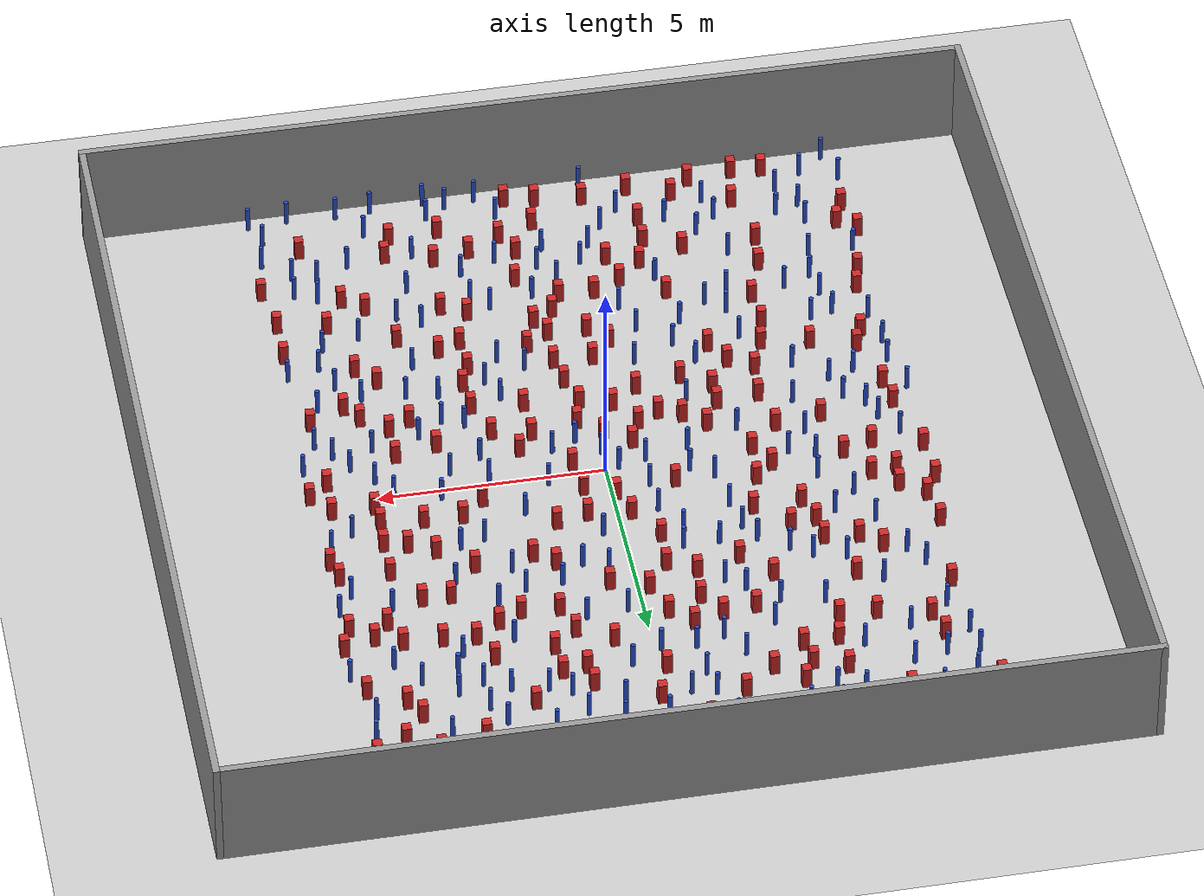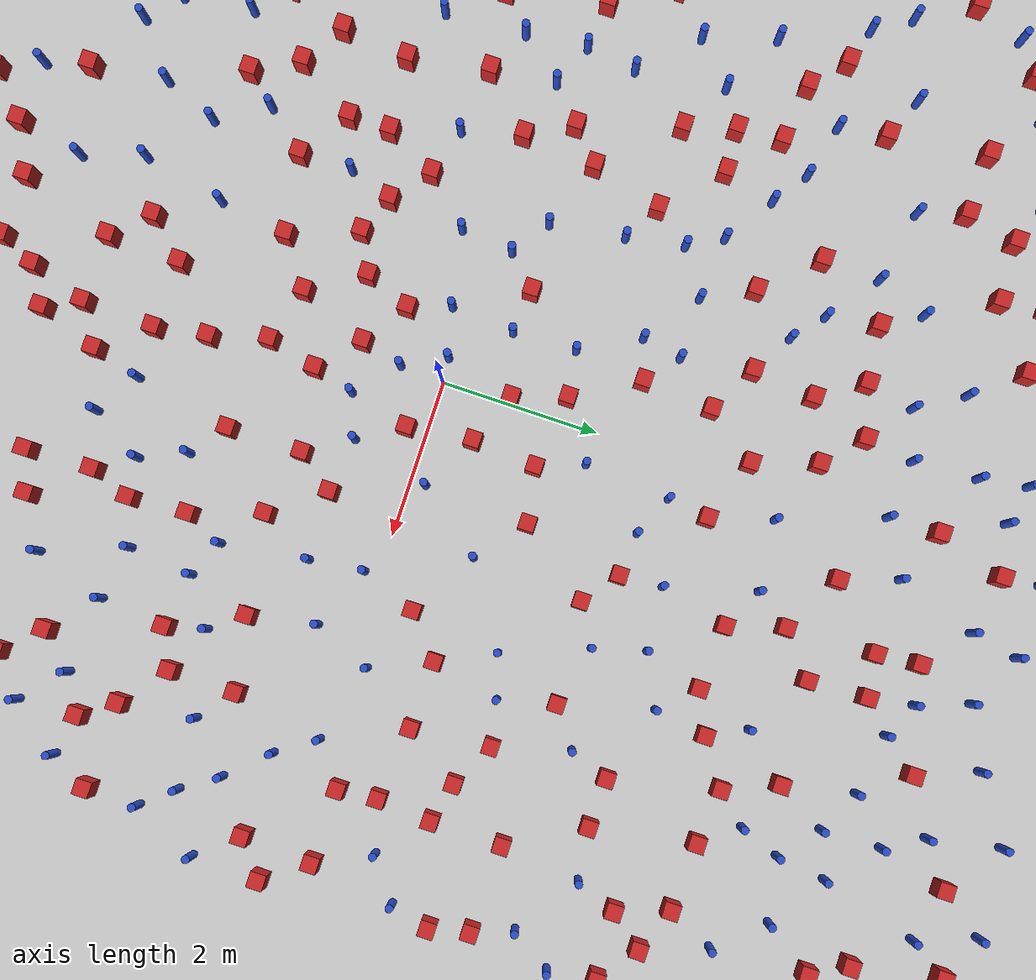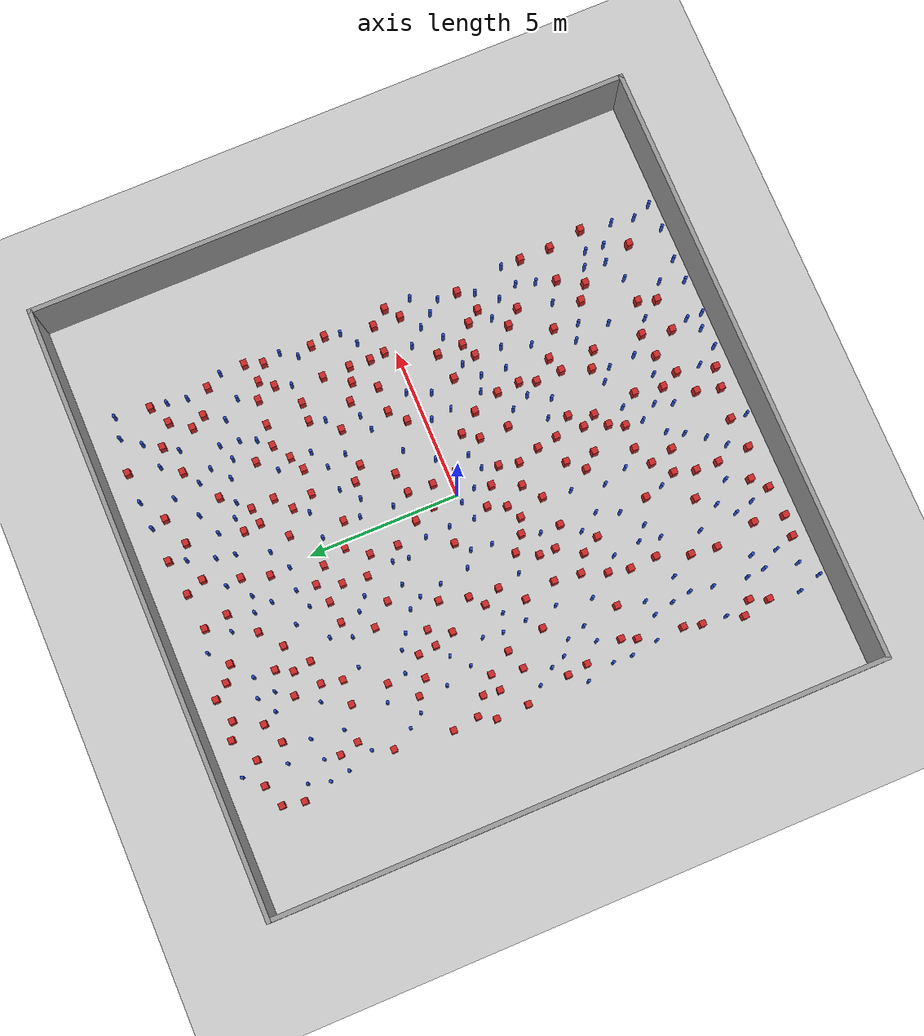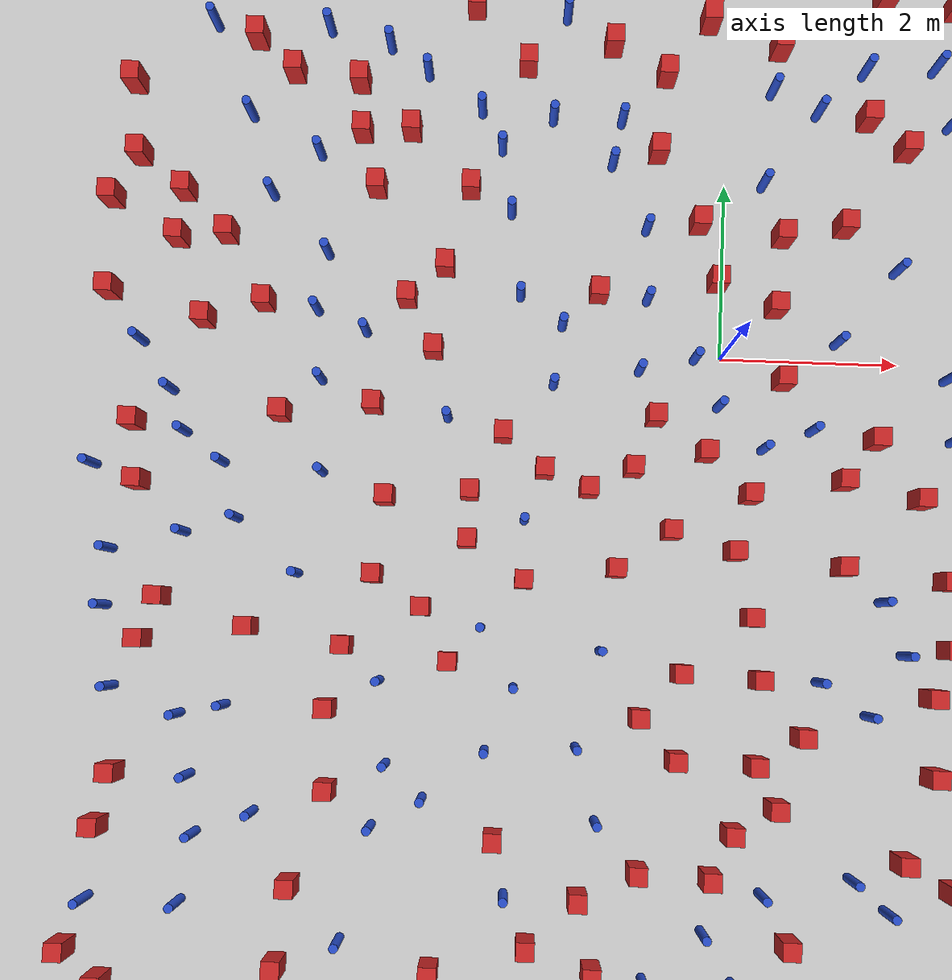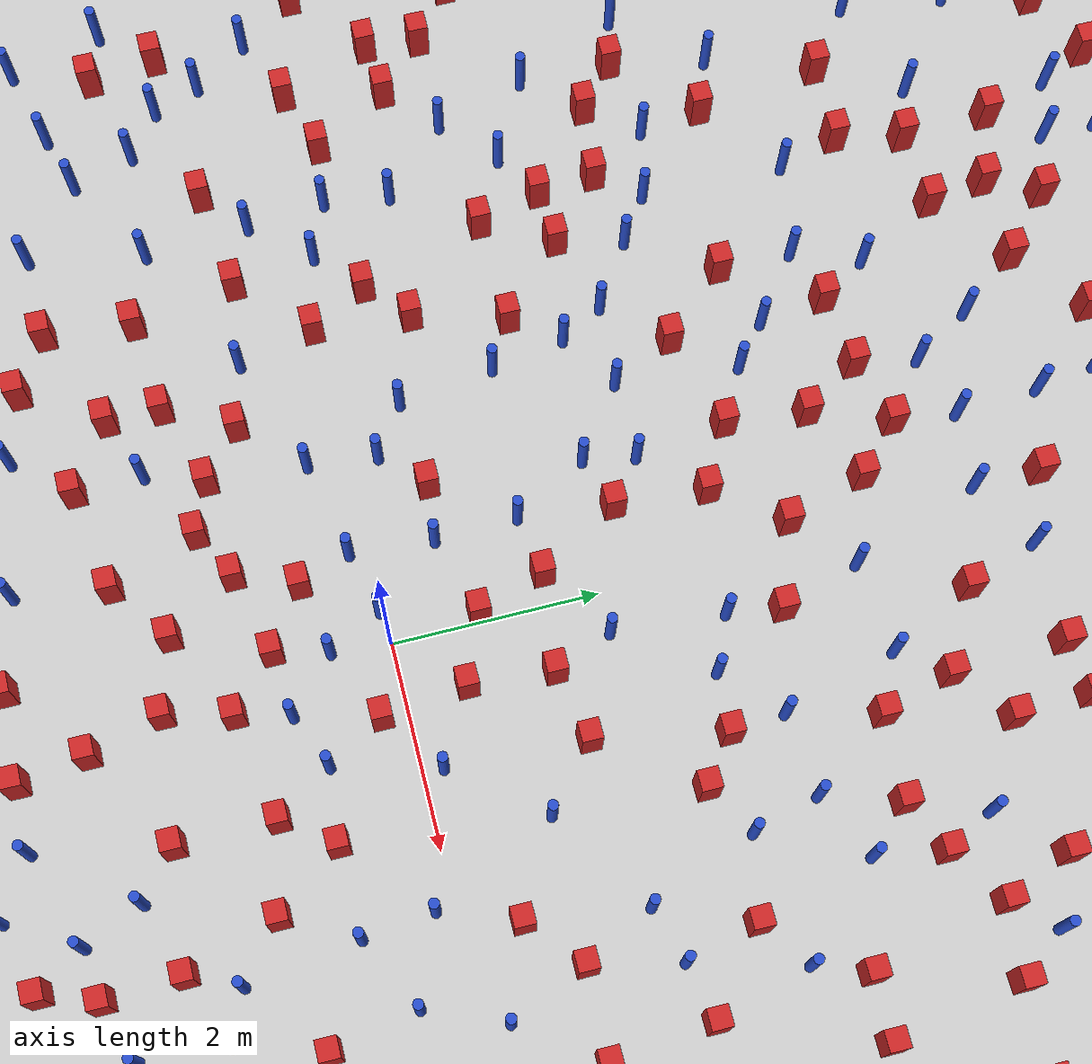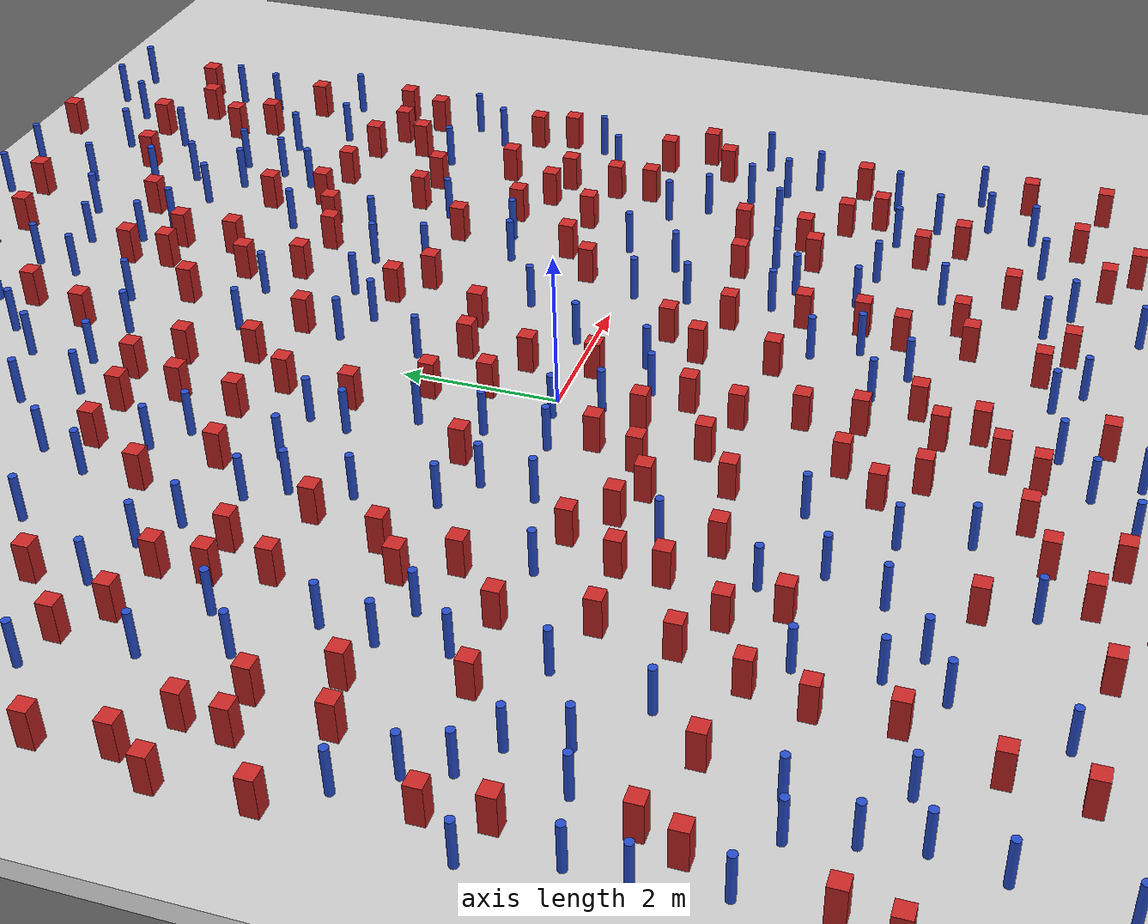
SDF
<sdf version="1.6">
 <world name="default">
  <light name="sun" type="directional">
   <pose>0 0 1000 0 -0 0</pose>
   <diffuse>0.8 0.8 0.8 1</diffuse>
   <specular>0.1 0.1 0.1 1</specular>
   <attenuation>
    <range>1000</range>
    <constant>0.9</constant>
    <linear>0.01</linear>
    <quadratic>0.001</quadratic>
   </attenuation>
   <direction>-0.5 0.5 -1</direction>
  </light>
  <model name="ground_plane">
   <static>1</static>
   <link name="link">
    <collision name="collision">
     <geometry><plane><normal>0 0 1</normal><size>100 100</size></plane></geometry>
     <surface><friction><ode><mu>100</mu><mu2>50</mu2></ode></friction></surface>
    </collision>
    <visual name="visual">
     <cast_shadows>0</cast_shadows>
     <geometry><plane><normal>0 0 1</normal><size>100 100</size></plane></geometry>
     <material>
      <ambient>1.0 1.0 1.0 1.0</ambient>
      <diffuse>0.8 0.8 0.8 1.0</diffuse>
      <specular>0.01 0.01 0.01 1.000000</specular>
     </material>
    </visual>
   </link>
  </model>
  <gravity>0 0 -9.8</gravity>
  <magnetic_field>6e-06 2.3e-05 -4.2e-05</magnetic_field>
  <atmosphere type="adiabatic"/>
  <physics name="default_physics" default="0" type="ode">
   <max_step_size>0.001</max_step_size>
   <real_time_factor>1</real_time_factor>
   <real_time_update_rate>1000</real_time_update_rate>
  </physics>
  <scene><ambient>0.4 0.4 0.4 1</ambient><background>0.7 0.7 0.7 1</background><shadows>1</shadows></scene>
  <spherical_coordinates>
   <surface_model>EARTH_WGS84</surface_model>
   <latitude_deg>0</latitude_deg>
   <longitude_deg>0</longitude_deg>
   <elevation>0</elevation>
   <heading_deg>0</heading_deg>
  </spherical_coordinates>
  <plugin name="gazebo_occupancy_map" filename="libgazebo_2Dmap_plugin.so">
   <map_resolution>0.05</map_resolution>
   <map_topic>generated_map</map_topic>
   <map_height>0.01</map_height>
   <map_size_x>50</map_size_x>
   <map_size_y>50</map_size_y>
  </plugin>
  <model name="NamedLocations">
   <static>true</static>
   <link name="DefaultStart"><pose>8.5 0 0 0 0 3.14</pose></link>
  </model>
  <model name="20x20_walls">
   <pose>0.044518 0.176112 0 0 -0 0</pose>
   <link name="Wall_1">
    <collision name="Wall_1_Collision">
     <geometry><box><size>20 0.15 2.5</size></box></geometry>
     <pose>0 0 1.25 0 -0 0</pose>
    </collision>
    <visual name="Wall_1_Visual">
     <pose>0 0 1.25 0 -0 0</pose>
     <geometry><box><size>20 0.15 2.5</size></box></geometry>
     <material>
      <script><uri>file://media/materials/scripts/gazebo.material</uri><name>Gazebo/Grey</name></script>
      <ambient>0.976471 0.992157 1 1</ambient>
     </material>
     <meta><layer>0</layer></meta>
    </visual>
    <pose>0 9.925 0 0 -0 0</pose>
   </link>
   <link name="Wall_3">
    <collision name="Wall_3_Collision">
     <geometry><box><size>20 0.15 2.5</size></box></geometry>
     <pose>0 0 1.25 0 -0 0</pose>
    </collision>
    <visual name="Wall_3_Visual">
     <pose>0 0 1.25 0 -0 0</pose>
     <geometry><box><size>20 0.15 2.5</size></box></geometry>
     <material>
      <script><uri>file://media/materials/scripts/gazebo.material</uri><name>Gazebo/Grey</name></script>
      <ambient>0.976471 0.992157 1 1</ambient>
     </material>
     <meta><layer>0</layer></meta>
    </visual>
    <pose>9.925 0 0 0 0 -1.5708</pose>
   </link>
   <link name="Wall_4">
    <collision name="Wall_4_Collision">
     <geometry><box><size>20 0.15 2.5</size></box></geometry>
     <pose>0 0 1.25 0 -0 0</pose>
    </collision>
    <visual name="Wall_4_Visual">
     <pose>0 0 1.25 0 -0 0</pose>
     <geometry><box><size>20 0.15 2.5</size></box></geometry>
     <material>
      <script><uri>file://media/materials/scripts/gazebo.material</uri><name>Gazebo/Grey</name></script>
      <ambient>0.976471 0.992157 1 1</ambient>
     </material>
     <meta><layer>0</layer></meta>
    </visual>
    <pose>0 -9.925 0 0 -0 3.14159</pose>
   </link>
   <link name="Wall_5">
    <collision name="Wall_5_Collision">
     <geometry><box><size>20 0.15 2.5</size></box></geometry>
     <pose>0 0 1.25 0 -0 0</pose>
    </collision>
    <visual name="Wall_5_Visual">
     <pose>0 0 1.25 0 -0 0</pose>
     <geometry><box><size>20 0.15 2.5</size></box></geometry>
     <material>
      <script><uri>file://media/materials/scripts/gazebo.material</uri><name>Gazebo/Grey</name></script>
      <ambient>0.976471 0.992157 1 1</ambient>
     </material>
     <meta><layer>0</layer></meta>
    </visual>
    <pose>-9.925 0 0 0 -0 1.5708</pose>
   </link>
   <static>1</static>
  </model>
  <model name="pole_obstacle0">
   <static>true</static>
   <pose>0.552288672222 -5.89928015238 7.38925637345e-09 -8.471706928e-08 1.24976765086e-08 -1.74513093015e-07</pose>
   <link name="link">
    <pose>0 0 0.3 0 -0 0</pose>
    <inertial>
     <mass>1</mass>
     <inertia><ixx>0.145833</ixx><ixy>0</ixy><ixz>0</ixz><iyy>0.145833</iyy><iyz>0</iyz><izz>0.125</izz></inertia>
    </inertial>
    <collision name="collision">
     <geometry><cylinder><radius>0.05</radius><length>.6</length></cylinder></geometry>
    </collision>
    <visual name="visual">
     <geometry><cylinder><radius>0.05</radius><length>.6</length></cylinder></geometry>
     <material>
      <script><name>Gazebo/Blue</name><uri>file://media/materials/scripts/gazebo.material</uri></script>
     </material>
    </visual>
   </link>
  </model>
  <model name="pole_obstacle1">
   <static>true</static>
   <pose>3.00676567767 3.73780736281 7.38925637345e-09 -8.47170692798e-08 1.24976764939e-08 -1.74513093025e-07</pose>
   <link name="link">
    <pose>0 0 0.3 0 -0 0</pose>
    <inertial>
     <mass>1</mass>
     <inertia><ixx>0.145833</ixx><ixy>0</ixy><ixz>0</ixz><iyy>0.145833</iyy><iyz>0</iyz><izz>0.125</izz></inertia>
    </inertial>
    <collision name="collision">
     <geometry><cylinder><radius>0.05</radius><length>.6</length></cylinder></geometry>
    </collision>
    <visual name="visual">
     <geometry><cylinder><radius>0.05</radius><length>.6</length></cylinder></geometry>
     <material>
      <script><name>Gazebo/Blue</name><uri>file://media/materials/scripts/gazebo.material</uri></script>
     </material>
    </visual>
   </link>
  </model>
  <model name="square_post_obstacle0">
   <static>true</static>
   <pose>-4.42537233581 9.34307108439 1.91545236811e-07 -7.35059704564e-06 1.12565212e-07 2.39332434364e-05</pose>
   <link name="link">
    <pose>0 0 0.25 0 -0 0</pose>
    <inertial>
     <mass>100</mass>
     <inertia>
      <ixx>0.166667</ixx>
      <ixy>0</ixy>
      <ixz>0</ixz>
      <iyy>0.166667</iyy>
      <iyz>0</iyz>
      <izz>0.166667</izz>
     </inertia>
    </inertial>
    <collision name="collision"><geometry><box><size>.2 .2 .5</size></box></geometry></collision>
    <visual name="visual">
     <geometry><box><size>.2 .2 .5</size></box></geometry>
     <material>
      <script><name>Gazebo/Red</name><uri>file://media/materials/scripts/gazebo.material</uri></script>
     </material>
    </visual>
   </link>
  </model>
  <model name="square_post_obstacle1">
   <static>true</static>
   <pose>-4.67498980944 -6.82831575101 1.91545236811e-07 -7.35059704564e-06 1.12565212e-07 2.39332434364e-05</pose>
   <link name="link">
    <pose>0 0 0.25 0 -0 0</pose>
    <inertial>
     <mass>100</mass>
     <inertia>
      <ixx>0.166667</ixx>
      <ixy>0</ixy>
      <ixz>0</ixz>
      <iyy>0.166667</iyy>
      <iyz>0</iyz>
      <izz>0.166667</izz>
     </inertia>
    </inertial>
    <collision name="collision"><geometry><box><size>.2 .2 .5</size></box></geometry></collision>
    <visual name="visual">
     <geometry><box><size>.2 .2 .5</size></box></geometry>
     <material>
      <script><name>Gazebo/Red</name><uri>file://media/materials/scripts/gazebo.material</uri></script>
     </material>
    </visual>
   </link>
  </model>
  <model name="pole_obstacle2">
   <static>true</static>
   <pose>5.726747599 -6.84969473188 7.38925637345e-09 -8.47170692796e-08 1.24976764786e-08 -1.74513093032e-07</pose>
   <link name="link">
    <pose>0 0 0.3 0 -0 0</pose>
    <inertial>
     <mass>1</mass>
     <inertia><ixx>0.145833</ixx><ixy>0</ixy><ixz>0</ixz><iyy>0.145833</iyy><iyz>0</iyz><izz>0.125</izz></inertia>
    </inertial>
    <collision name="collision">
     <geometry><cylinder><radius>0.05</radius><length>.6</length></cylinder></geometry>
    </collision>
    <visual name="visual">
     <geometry><cylinder><radius>0.05</radius><length>.6</length></cylinder></geometry>
     <material>
      <script><name>Gazebo/Blue</name><uri>file://media/materials/scripts/gazebo.material</uri></script>
     </material>
    </visual>
   </link>
  </model>
  <model name="pole_obstacle3">
   <static>true</static>
   <pose>-6.52432451563 -0.0444489107203 7.38925637345e-09 -8.47170692799e-08 1.24976765036e-08 -1.7451309302e-07</pose>
   <link name="link">
    <pose>0 0 0.3 0 -0 0</pose>
    <inertial>
     <mass>1</mass>
     <inertia><ixx>0.145833</ixx><ixy>0</ixy><ixz>0</ixz><iyy>0.145833</iyy><iyz>0</iyz><izz>0.125</izz></inertia>
    </inertial>
    <collision name="collision">
     <geometry><cylinder><radius>0.05</radius><length>.6</length></cylinder></geometry>
    </collision>
    <visual name="visual">
     <geometry><cylinder><radius>0.05</radius><length>.6</length></cylinder></geometry>
     <material>
      <script><name>Gazebo/Blue</name><uri>file://media/materials/scripts/gazebo.material</uri></script>
     </material>
    </visual>
   </link>
  </model>
  <model name="pole_obstacle4">
   <static>true</static>
   <pose>2.52354586549 -0.172979752865 7.38925637345e-09 -8.471706928e-08 1.24976765208e-08 -1.7451309301e-07</pose>
   <link name="link">
    <pose>0 0 0.3 0 -0 0</pose>
    <inertial>
     <mass>1</mass>
     <inertia><ixx>0.145833</ixx><ixy>0</ixy><ixz>0</ixz><iyy>0.145833</iyy><iyz>0</iyz><izz>0.125</izz></inertia>
    </inertial>
    <collision name="collision">
     <geometry><cylinder><radius>0.05</radius><length>.6</length></cylinder></geometry>
    </collision>
    <visual name="visual">
     <geometry><cylinder><radius>0.05</radius><length>.6</length></cylinder></geometry>
     <material>
      <script><name>Gazebo/Blue</name><uri>file://media/materials/scripts/gazebo.material</uri></script>
     </material>
    </visual>
   </link>
  </model>
  <model name="pole_obstacle5">
   <static>true</static>
   <pose>0.265713233834 -6.86529294261 7.38925637345e-09 -8.47170692799e-08 1.24976765101e-08 -1.74513093014e-07</pose>
   <link name="link">
    <pose>0 0 0.3 0 -0 0</pose>
    <inertial>
     <mass>1</mass>
     <inertia><ixx>0.145833</ixx><ixy>0</ixy><ixz>0</ixz><iyy>0.145833</iyy><iyz>0</iyz><izz>0.125</izz></inertia>
    </inertial>
    <collision name="collision">
     <geometry><cylinder><radius>0.05</radius><length>.6</length></cylinder></geometry>
    </collision>
    <visual name="visual">
     <geometry><cylinder><radius>0.05</radius><length>.6</length></cylinder></geometry>
     <material>
      <script><name>Gazebo/Blue</name><uri>file://media/materials/scripts/gazebo.material</uri></script>
     </material>
    </visual>
   </link>
  </model>
  <model name="pole_obstacle6">
   <static>true</static>
   <pose>1.14026042025 -3.58873495884 7.38925637345e-09 -8.47170692799e-08 1.24976765053e-08 -1.74513093017e-07</pose>
   <link name="link">
    <pose>0 0 0.3 0 -0 0</pose>
    <inertial>
     <mass>1</mass>
     <inertia><ixx>0.145833</ixx><ixy>0</ixy><ixz>0</ixz><iyy>0.145833</iyy><iyz>0</iyz><izz>0.125</izz></inertia>
    </inertial>
    <collision name="collision">
     <geometry><cylinder><radius>0.05</radius><length>.6</length></cylinder></geometry>
    </collision>
    <visual name="visual">
     <geometry><cylinder><radius>0.05</radius><length>.6</length></cylinder></geometry>
     <material>
      <script><name>Gazebo/Blue</name><uri>file://media/materials/scripts/gazebo.material</uri></script>
     </material>
    </visual>
   </link>
  </model>
  <model name="square_post_obstacle2">
   <static>true</static>
   <pose>-3.70692572244 -1.7061945904 1.91545236811e-07 -7.35059704564e-06 1.12565212e-07 2.39332434364e-05</pose>
   <link name="link">
    <pose>0 0 0.25 0 -0 0</pose>
    <inertial>
     <mass>100</mass>
     <inertia>
      <ixx>0.166667</ixx>
      <ixy>0</ixy>
      <ixz>0</ixz>
      <iyy>0.166667</iyy>
      <iyz>0</iyz>
      <izz>0.166667</izz>
     </inertia>
    </inertial>
    <collision name="collision"><geometry><box><size>.2 .2 .5</size></box></geometry></collision>
    <visual name="visual">
     <geometry><box><size>.2 .2 .5</size></box></geometry>
     <material>
      <script><name>Gazebo/Red</name><uri>file://media/materials/scripts/gazebo.material</uri></script>
     </material>
    </visual>
   </link>
  </model>
  <model name="square_post_obstacle3">
   <static>true</static>
   <pose>-3.88711328392 -0.675719960965 1.91545236811e-07 -7.35059704564e-06 1.12565212e-07 2.39332434364e-05</pose>
   <link name="link">
    <pose>0 0 0.25 0 -0 0</pose>
    <inertial>
     <mass>100</mass>
     <inertia>
      <ixx>0.166667</ixx>
      <ixy>0</ixy>
      <ixz>0</ixz>
      <iyy>0.166667</iyy>
      <iyz>0</iyz>
      <izz>0.166667</izz>
     </inertia>
    </inertial>
    <collision name="collision"><geometry><box><size>.2 .2 .5</size></box></geometry></collision>
    <visual name="visual">
     <geometry><box><size>.2 .2 .5</size></box></geometry>
     <material>
      <script><name>Gazebo/Red</name><uri>file://media/materials/scripts/gazebo.material</uri></script>
     </material>
    </visual>
   </link>
  </model>
  <model name="square_post_obstacle4">
   <static>true</static>
   <pose>0.182297855617 -2.18379983032 1.91545236811e-07 -7.35059704564e-06 1.12565212e-07 2.39332434364e-05</pose>
   <link name="link">
    <pose>0 0 0.25 0 -0 0</pose>
    <inertial>
     <mass>100</mass>
     <inertia>
      <ixx>0.166667</ixx>
      <ixy>0</ixy>
      <ixz>0</ixz>
      <iyy>0.166667</iyy>
      <iyz>0</iyz>
      <izz>0.166667</izz>
     </inertia>
    </inertial>
    <collision name="collision"><geometry><box><size>.2 .2 .5</size></box></geometry></collision>
    <visual name="visual">
     <geometry><box><size>.2 .2 .5</size></box></geometry>
     <material>
      <script><name>Gazebo/Red</name><uri>file://media/materials/scripts/gazebo.material</uri></script>
     </material>
    </visual>
   </link>
  </model>
  <model name="pole_obstacle7">
   <static>true</static>
   <pose>-4.47552511647 1.02826375217 7.38925637345e-09 -8.47170692801e-08 1.24976765139e-08 -1.74513093014e-07</pose>
   <link name="link">
    <pose>0 0 0.3 0 -0 0</pose>
    <inertial>
     <mass>1</mass>
     <inertia><ixx>0.145833</ixx><ixy>0</ixy><ixz>0</ixz><iyy>0.145833</iyy><iyz>0</iyz><izz>0.125</izz></inertia>
    </inertial>
    <collision name="collision">
     <geometry><cylinder><radius>0.05</radius><length>.6</length></cylinder></geometry>
    </collision>
    <visual name="visual">
     <geometry><cylinder><radius>0.05</radius><length>.6</length></cylinder></geometry>
     <material>
      <script><name>Gazebo/Blue</name><uri>file://media/materials/scripts/gazebo.material</uri></script>
     </material>
    </visual>
   </link>
  </model>
  <model name="pole_obstacle8">
   <static>true</static>
   <pose>-5.37966165243 -4.06961896865 7.38925637345e-09 -8.47170692796e-08 1.24976764786e-08 -1.74513093032e-07</pose>
   <link name="link">
    <pose>0 0 0.3 0 -0 0</pose>
    <inertial>
     <mass>1</mass>
     <inertia><ixx>0.145833</ixx><ixy>0</ixy><ixz>0</ixz><iyy>0.145833</iyy><iyz>0</iyz><izz>0.125</izz></inertia>
    </inertial>
    <collision name="collision">
     <geometry><cylinder><radius>0.05</radius><length>.6</length></cylinder></geometry>
    </collision>
    <visual name="visual">
     <geometry><cylinder><radius>0.05</radius><length>.6</length></cylinder></geometry>
     <material>
      <script><name>Gazebo/Blue</name><uri>file://media/materials/scripts/gazebo.material</uri></script>
     </material>
    </visual>
   </link>
  </model>
  <model name="square_post_obstacle5">
   <static>true</static>
   <pose>-0.0569344833062 -9.03164974831 1.91545236811e-07 -7.35059704564e-06 1.12565212e-07 2.39332434364e-05</pose>
   <link name="link">
    <pose>0 0 0.25 0 -0 0</pose>
    <inertial>
     <mass>100</mass>
     <inertia>
      <ixx>0.166667</ixx>
      <ixy>0</ixy>
      <ixz>0</ixz>
      <iyy>0.166667</iyy>
      <iyz>0</iyz>
      <izz>0.166667</izz>
     </inertia>
    </inertial>
    <collision name="collision"><geometry><box><size>.2 .2 .5</size></box></geometry></collision>
    <visual name="visual">
     <geometry><box><size>.2 .2 .5</size></box></geometry>
     <material>
      <script><name>Gazebo/Red</name><uri>file://media/materials/scripts/gazebo.material</uri></script>
     </material>
    </visual>
   </link>
  </model>
  <model name="square_post_obstacle6">
   <static>true</static>
   <pose>-0.779457869081 2.34286586143 1.91545236811e-07 -7.35059704564e-06 1.12565212e-07 2.39332434364e-05</pose>
   <link name="link">
    <pose>0 0 0.25 0 -0 0</pose>
    <inertial>
     <mass>100</mass>
     <inertia>
      <ixx>0.166667</ixx>
      <ixy>0</ixy>
      <ixz>0</ixz>
      <iyy>0.166667</iyy>
      <iyz>0</iyz>
      <izz>0.166667</izz>
     </inertia>
    </inertial>
    <collision name="collision"><geometry><box><size>.2 .2 .5</size></box></geometry></collision>
    <visual name="visual">
     <geometry><box><size>.2 .2 .5</size></box></geometry>
     <material>
      <script><name>Gazebo/Red</name><uri>file://media/materials/scripts/gazebo.material</uri></script>
     </material>
    </visual>
   </link>
  </model>
  <model name="square_post_obstacle7">
   <static>true</static>
   <pose>0.385087380425 -2.91029149053 1.91545236811e-07 -7.35059704564e-06 1.12565212e-07 2.39332434364e-05</pose>
   <link name="link">
    <pose>0 0 0.25 0 -0 0</pose>
    <inertial>
     <mass>100</mass>
     <inertia>
      <ixx>0.166667</ixx>
      <ixy>0</ixy>
      <ixz>0</ixz>
      <iyy>0.166667</iyy>
      <iyz>0</iyz>
      <izz>0.166667</izz>
     </inertia>
    </inertial>
    <collision name="collision"><geometry><box><size>.2 .2 .5</size></box></geometry></collision>
    <visual name="visual">
     <geometry><box><size>.2 .2 .5</size></box></geometry>
     <material>
      <script><name>Gazebo/Red</name><uri>file://media/materials/scripts/gazebo.material</uri></script>
     </material>
    </visual>
   </link>
  </model>
  <model name="pole_obstacle9">
   <static>true</static>
   <pose>6.43883494584 9.03935850446 7.38925637345e-09 -8.471706928e-08 1.24976765081e-08 -1.74513093015e-07</pose>
   <link name="link">
    <pose>0 0 0.3 0 -0 0</pose>
    <inertial>
     <mass>1</mass>
     <inertia><ixx>0.145833</ixx><ixy>0</ixy><ixz>0</ixz><iyy>0.145833</iyy><iyz>0</iyz><izz>0.125</izz></inertia>
    </inertial>
    <collision name="collision">
     <geometry><cylinder><radius>0.05</radius><length>.6</length></cylinder></geometry>
    </collision>
    <visual name="visual">
     <geometry><cylinder><radius>0.05</radius><length>.6</length></cylinder></geometry>
     <material>
      <script><name>Gazebo/Blue</name><uri>file://media/materials/scripts/gazebo.material</uri></script>
     </material>
    </visual>
   </link>
  </model>
  <model name="pole_obstacle10">
   <static>true</static>
   <pose>1.82763532323 -2.68481853135 7.38925637345e-09 -8.47170692799e-08 1.24976765053e-08 -1.74513093017e-07</pose>
   <link name="link">
    <pose>0 0 0.3 0 -0 0</pose>
    <inertial>
     <mass>1</mass>
     <inertia><ixx>0.145833</ixx><ixy>0</ixy><ixz>0</ixz><iyy>0.145833</iyy><iyz>0</iyz><izz>0.125</izz></inertia>
    </inertial>
    <collision name="collision">
     <geometry><cylinder><radius>0.05</radius><length>.6</length></cylinder></geometry>
    </collision>
    <visual name="visual">
     <geometry><cylinder><radius>0.05</radius><length>.6</length></cylinder></geometry>
     <material>
      <script><name>Gazebo/Blue</name><uri>file://media/materials/scripts/gazebo.material</uri></script>
     </material>
    </visual>
   </link>
  </model>
  <model name="pole_obstacle11">
   <static>true</static>
   <pose>3.85353323174 -3.12247104477 7.38925637345e-09 -8.47170692798e-08 1.24976764939e-08 -1.74513093025e-07</pose>
   <link name="link">
    <pose>0 0 0.3 0 -0 0</pose>
    <inertial>
     <mass>1</mass>
     <inertia><ixx>0.145833</ixx><ixy>0</ixy><ixz>0</ixz><iyy>0.145833</iyy><iyz>0</iyz><izz>0.125</izz></inertia>
    </inertial>
    <collision name="collision">
     <geometry><cylinder><radius>0.05</radius><length>.6</length></cylinder></geometry>
    </collision>
    <visual name="visual">
     <geometry><cylinder><radius>0.05</radius><length>.6</length></cylinder></geometry>
     <material>
      <script><name>Gazebo/Blue</name><uri>file://media/materials/scripts/gazebo.material</uri></script>
     </material>
    </visual>
   </link>
  </model>
  <model name="pole_obstacle12">
   <static>true</static>
   <pose>-5.4626077575 -8.49701745886 7.38925637345e-09 -8.471706928e-08 1.24976765081e-08 -1.74513093015e-07</pose>
   <link name="link">
    <pose>0 0 0.3 0 -0 0</pose>
    <inertial>
     <mass>1</mass>
     <inertia><ixx>0.145833</ixx><ixy>0</ixy><ixz>0</ixz><iyy>0.145833</iyy><iyz>0</iyz><izz>0.125</izz></inertia>
    </inertial>
    <collision name="collision">
     <geometry><cylinder><radius>0.05</radius><length>.6</length></cylinder></geometry>
    </collision>
    <visual name="visual">
     <geometry><cylinder><radius>0.05</radius><length>.6</length></cylinder></geometry>
     <material>
      <script><name>Gazebo/Blue</name><uri>file://media/materials/scripts/gazebo.material</uri></script>
     </material>
    </visual>
   </link>
  </model>
  <model name="square_post_obstacle8">
   <static>true</static>
   <pose>6.05506453243 0.368401354186 1.91545236811e-07 -7.35059704564e-06 1.12565212e-07 2.39332434364e-05</pose>
   <link name="link">
    <pose>0 0 0.25 0 -0 0</pose>
    <inertial>
     <mass>100</mass>
     <inertia>
      <ixx>0.166667</ixx>
      <ixy>0</ixy>
      <ixz>0</ixz>
      <iyy>0.166667</iyy>
      <iyz>0</iyz>
      <izz>0.166667</izz>
     </inertia>
    </inertial>
    <collision name="collision"><geometry><box><size>.2 .2 .5</size></box></geometry></collision>
    <visual name="visual">
     <geometry><box><size>.2 .2 .5</size></box></geometry>
     <material>
      <script><name>Gazebo/Red</name><uri>file://media/materials/scripts/gazebo.material</uri></script>
     </material>
    </visual>
   </link>
  </model>
  <model name="square_post_obstacle9">
   <static>true</static>
   <pose>2.03781863392 2.46468517248 1.91545236811e-07 -7.35059704564e-06 1.12565212e-07 2.39332434364e-05</pose>
   <link name="link">
    <pose>0 0 0.25 0 -0 0</pose>
    <inertial>
     <mass>100</mass>
     <inertia>
      <ixx>0.166667</ixx>
      <ixy>0</ixy>
      <ixz>0</ixz>
      <iyy>0.166667</iyy>
      <iyz>0</iyz>
      <izz>0.166667</izz>
     </inertia>
    </inertial>
    <collision name="collision"><geometry><box><size>.2 .2 .5</size></box></geometry></collision>
    <visual name="visual">
     <geometry><box><size>.2 .2 .5</size></box></geometry>
     <material>
      <script><name>Gazebo/Red</name><uri>file://media/materials/scripts/gazebo.material</uri></script>
     </material>
    </visual>
   </link>
  </model>
  <model name="pole_obstacle13">
   <static>true</static>
   <pose>3.62405460499 -5.69707315796 7.38925637345e-09 -8.47170692798e-08 1.24976765033e-08 -1.74513093019e-07</pose>
   <link name="link">
    <pose>0 0 0.3 0 -0 0</pose>
    <inertial>
     <mass>1</mass>
     <inertia><ixx>0.145833</ixx><ixy>0</ixy><ixz>0</ixz><iyy>0.145833</iyy><iyz>0</iyz><izz>0.125</izz></inertia>
    </inertial>
    <collision name="collision">
     <geometry><cylinder><radius>0.05</radius><length>.6</length></cylinder></geometry>
    </collision>
    <visual name="visual">
     <geometry><cylinder><radius>0.05</radius><length>.6</length></cylinder></geometry>
     <material>
      <script><name>Gazebo/Blue</name><uri>file://media/materials/scripts/gazebo.material</uri></script>
     </material>
    </visual>
   </link>
  </model>
  <model name="square_post_obstacle10">
   <static>true</static>
   <pose>-6.34527799305 -3.37768642562 1.91545236811e-07 -7.35059704564e-06 1.12565212e-07 2.39332434364e-05</pose>
   <link name="link">
    <pose>0 0 0.25 0 -0 0</pose>
    <inertial>
     <mass>100</mass>
     <inertia>
      <ixx>0.166667</ixx>
      <ixy>0</ixy>
      <ixz>0</ixz>
      <iyy>0.166667</iyy>
      <iyz>0</iyz>
      <izz>0.166667</izz>
     </inertia>
    </inertial>
    <collision name="collision"><geometry><box><size>.2 .2 .5</size></box></geometry></collision>
    <visual name="visual">
     <geometry><box><size>.2 .2 .5</size></box></geometry>
     <material>
      <script><name>Gazebo/Red</name><uri>file://media/materials/scripts/gazebo.material</uri></script>
     </material>
    </visual>
   </link>
  </model>
  <model name="square_post_obstacle11">
   <static>true</static>
   <pose>-2.42287995631 -0.95356776099 1.91545236811e-07 -7.35059704564e-06 1.12565212e-07 2.39332434364e-05</pose>
   <link name="link">
    <pose>0 0 0.25 0 -0 0</pose>
    <inertial>
     <mass>100</mass>
     <inertia>
      <ixx>0.166667</ixx>
      <ixy>0</ixy>
      <ixz>0</ixz>
      <iyy>0.166667</iyy>
      <iyz>0</iyz>
      <izz>0.166667</izz>
     </inertia>
    </inertial>
    <collision name="collision"><geometry><box><size>.2 .2 .5</size></box></geometry></collision>
    <visual name="visual">
     <geometry><box><size>.2 .2 .5</size></box></geometry>
     <material>
      <script><name>Gazebo/Red</name><uri>file://media/materials/scripts/gazebo.material</uri></script>
     </material>
    </visual>
   </link>
  </model>
  <model name="pole_obstacle14">
   <static>true</static>
   <pose>1.97462156829 -6.91148437594 7.38925637345e-09 -8.471706928e-08 1.24976765202e-08 -1.7451309301e-07</pose>
   <link name="link">
    <pose>0 0 0.3 0 -0 0</pose>
    <inertial>
     <mass>1</mass>
     <inertia><ixx>0.145833</ixx><ixy>0</ixy><ixz>0</ixz><iyy>0.145833</iyy><iyz>0</iyz><izz>0.125</izz></inertia>
    </inertial>
    <collision name="collision">
     <geometry><cylinder><radius>0.05</radius><length>.6</length></cylinder></geometry>
    </collision>
    <visual name="visual">
     <geometry><cylinder><radius>0.05</radius><length>.6</length></cylinder></geometry>
     <material>
      <script><name>Gazebo/Blue</name><uri>file://media/materials/scripts/gazebo.material</uri></script>
     </material>
    </visual>
   </link>
  </model>
  <model name="pole_obstacle15">
   <static>true</static>
   <pose>-1.29347158093 2.18036558145 7.38925637345e-09 -8.47170692799e-08 1.24976765053e-08 -1.74513093017e-07</pose>
   <link name="link">
    <pose>0 0 0.3 0 -0 0</pose>
    <inertial>
     <mass>1</mass>
     <inertia><ixx>0.145833</ixx><ixy>0</ixy><ixz>0</ixz><iyy>0.145833</iyy><iyz>0</iyz><izz>0.125</izz></inertia>
    </inertial>
    <collision name="collision">
     <geometry><cylinder><radius>0.05</radius><length>.6</length></cylinder></geometry>
    </collision>
    <visual name="visual">
     <geometry><cylinder><radius>0.05</radius><length>.6</length></cylinder></geometry>
     <material>
      <script><name>Gazebo/Blue</name><uri>file://media/materials/scripts/gazebo.material</uri></script>
     </material>
    </visual>
   </link>
  </model>
  <model name="square_post_obstacle12">
   <static>true</static>
   <pose>-1.10398348452 -8.89840903795 1.91545236811e-07 -7.35059704564e-06 1.12565212e-07 2.39332434364e-05</pose>
   <link name="link">
    <pose>0 0 0.25 0 -0 0</pose>
    <inertial>
     <mass>100</mass>
     <inertia>
      <ixx>0.166667</ixx>
      <ixy>0</ixy>
      <ixz>0</ixz>
      <iyy>0.166667</iyy>
      <iyz>0</iyz>
      <izz>0.166667</izz>
     </inertia>
    </inertial>
    <collision name="collision"><geometry><box><size>.2 .2 .5</size></box></geometry></collision>
    <visual name="visual">
     <geometry><box><size>.2 .2 .5</size></box></geometry>
     <material>
      <script><name>Gazebo/Red</name><uri>file://media/materials/scripts/gazebo.material</uri></script>
     </material>
    </visual>
   </link>
  </model>
  <model name="pole_obstacle16">
   <static>true</static>
   <pose>0.417773265763 1.99657974552 7.38925637345e-09 -8.47170692799e-08 1.24976765022e-08 -1.74513093019e-07</pose>
   <link name="link">
    <pose>0 0 0.3 0 -0 0</pose>
    <inertial>
     <mass>1</mass>
     <inertia><ixx>0.145833</ixx><ixy>0</ixy><ixz>0</ixz><iyy>0.145833</iyy><iyz>0</iyz><izz>0.125</izz></inertia>
    </inertial>
    <collision name="collision">
     <geometry><cylinder><radius>0.05</radius><length>.6</length></cylinder></geometry>
    </collision>
    <visual name="visual">
     <geometry><cylinder><radius>0.05</radius><length>.6</length></cylinder></geometry>
     <material>
      <script><name>Gazebo/Blue</name><uri>file://media/materials/scripts/gazebo.material</uri></script>
     </material>
    </visual>
   </link>
  </model>
  <model name="pole_obstacle17">
   <static>true</static>
   <pose>-1.03280544207 7.2472922459 7.38925637345e-09 -8.47170692799e-08 1.2497676505e-08 -1.74513093018e-07</pose>
   <link name="link">
    <pose>0 0 0.3 0 -0 0</pose>
    <inertial>
     <mass>1</mass>
     <inertia><ixx>0.145833</ixx><ixy>0</ixy><ixz>0</ixz><iyy>0.145833</iyy><iyz>0</iyz><izz>0.125</izz></inertia>
    </inertial>
    <collision name="collision">
     <geometry><cylinder><radius>0.05</radius><length>.6</length></cylinder></geometry>
    </collision>
    <visual name="visual">
     <geometry><cylinder><radius>0.05</radius><length>.6</length></cylinder></geometry>
     <material>
      <script><name>Gazebo/Blue</name><uri>file://media/materials/scripts/gazebo.material</uri></script>
     </material>
    </visual>
   </link>
  </model>
  <model name="square_post_obstacle13">
   <static>true</static>
   <pose>0.308547579843 8.96091731637 1.91545236811e-07 -7.35059704564e-06 1.12565212e-07 2.39332434364e-05</pose>
   <link name="link">
    <pose>0 0 0.25 0 -0 0</pose>
    <inertial>
     <mass>100</mass>
     <inertia>
      <ixx>0.166667</ixx>
      <ixy>0</ixy>
      <ixz>0</ixz>
      <iyy>0.166667</iyy>
      <iyz>0</iyz>
      <izz>0.166667</izz>
     </inertia>
    </inertial>
    <collision name="collision"><geometry><box><size>.2 .2 .5</size></box></geometry></collision>
    <visual name="visual">
     <geometry><box><size>.2 .2 .5</size></box></geometry>
     <material>
      <script><name>Gazebo/Red</name><uri>file://media/materials/scripts/gazebo.material</uri></script>
     </material>
    </visual>
   </link>
  </model>
  <model name="pole_obstacle18">
   <static>true</static>
   <pose>6.0780218421 -1.86008930025 7.38925637345e-09 -8.471706928e-08 1.24976765134e-08 -1.74513093015e-07</pose>
   <link name="link">
    <pose>0 0 0.3 0 -0 0</pose>
    <inertial>
     <mass>1</mass>
     <inertia><ixx>0.145833</ixx><ixy>0</ixy><ixz>0</ixz><iyy>0.145833</iyy><iyz>0</iyz><izz>0.125</izz></inertia>
    </inertial>
    <collision name="collision">
     <geometry><cylinder><radius>0.05</radius><length>.6</length></cylinder></geometry>
    </collision>
    <visual name="visual">
     <geometry><cylinder><radius>0.05</radius><length>.6</length></cylinder></geometry>
     <material>
      <script><name>Gazebo/Blue</name><uri>file://media/materials/scripts/gazebo.material</uri></script>
     </material>
    </visual>
   </link>
  </model>
  <model name="square_post_obstacle14">
   <static>true</static>
   <pose>-1.63838827621 7.36169777529 1.91545236811e-07 -7.35059704564e-06 1.12565212e-07 2.39332434364e-05</pose>
   <link name="link">
    <pose>0 0 0.25 0 -0 0</pose>
    <inertial>
     <mass>100</mass>
     <inertia>
      <ixx>0.166667</ixx>
      <ixy>0</ixy>
      <ixz>0</ixz>
      <iyy>0.166667</iyy>
      <iyz>0</iyz>
      <izz>0.166667</izz>
     </inertia>
    </inertial>
    <collision name="collision"><geometry><box><size>.2 .2 .5</size></box></geometry></collision>
    <visual name="visual">
     <geometry><box><size>.2 .2 .5</size></box></geometry>
     <material>
      <script><name>Gazebo/Red</name><uri>file://media/materials/scripts/gazebo.material</uri></script>
     </material>
    </visual>
   </link>
  </model>
  <model name="pole_obstacle19">
   <static>true</static>
   <pose>-1.26880020867 -3.33482278495 7.38925637345e-09 -8.47170692799e-08 1.24976765053e-08 -1.74513093017e-07</pose>
   <link name="link">
    <pose>0 0 0.3 0 -0 0</pose>
    <inertial>
     <mass>1</mass>
     <inertia><ixx>0.145833</ixx><ixy>0</ixy><ixz>0</ixz><iyy>0.145833</iyy><iyz>0</iyz><izz>0.125</izz></inertia>
    </inertial>
    <collision name="collision">
     <geometry><cylinder><radius>0.05</radius><length>.6</length></cylinder></geometry>
    </collision>
    <visual name="visual">
     <geometry><cylinder><radius>0.05</radius><length>.6</length></cylinder></geometry>
     <material>
      <script><name>Gazebo/Blue</name><uri>file://media/materials/scripts/gazebo.material</uri></script>
     </material>
    </visual>
   </link>
  </model>
  <model name="square_post_obstacle15">
   <static>true</static>
   <pose>-0.806000199674 -5.70891678703 1.91545236811e-07 -7.35059704564e-06 1.12565212e-07 2.39332434364e-05</pose>
   <link name="link">
    <pose>0 0 0.25 0 -0 0</pose>
    <inertial>
     <mass>100</mass>
     <inertia>
      <ixx>0.166667</ixx>
      <ixy>0</ixy>
      <ixz>0</ixz>
      <iyy>0.166667</iyy>
      <iyz>0</iyz>
      <izz>0.166667</izz>
     </inertia>
    </inertial>
    <collision name="collision"><geometry><box><size>.2 .2 .5</size></box></geometry></collision>
    <visual name="visual">
     <geometry><box><size>.2 .2 .5</size></box></geometry>
     <material>
      <script><name>Gazebo/Red</name><uri>file://media/materials/scripts/gazebo.material</uri></script>
     </material>
    </visual>
   </link>
  </model>
  <model name="square_post_obstacle16">
   <static>true</static>
   <pose>-3.55667821835 0.552505295943 1.91545236811e-07 -7.35059704564e-06 1.12565212e-07 2.39332434364e-05</pose>
   <link name="link">
    <pose>0 0 0.25 0 -0 0</pose>
    <inertial>
     <mass>100</mass>
     <inertia>
      <ixx>0.166667</ixx>
      <ixy>0</ixy>
      <ixz>0</ixz>
      <iyy>0.166667</iyy>
      <iyz>0</iyz>
      <izz>0.166667</izz>
     </inertia>
    </inertial>
    <collision name="collision"><geometry><box><size>.2 .2 .5</size></box></geometry></collision>
    <visual name="visual">
     <geometry><box><size>.2 .2 .5</size></box></geometry>
     <material>
      <script><name>Gazebo/Red</name><uri>file://media/materials/scripts/gazebo.material</uri></script>
     </material>
    </visual>
   </link>
  </model>
  <model name="square_post_obstacle17">
   <static>true</static>
   <pose>0.582227738402 3.61344862767 1.91545236811e-07 -7.35059704564e-06 1.12565212e-07 2.39332434364e-05</pose>
   <link name="link">
    <pose>0 0 0.25 0 -0 0</pose>
    <inertial>
     <mass>100</mass>
     <inertia>
      <ixx>0.166667</ixx>
      <ixy>0</ixy>
      <ixz>0</ixz>
      <iyy>0.166667</iyy>
      <iyz>0</iyz>
      <izz>0.166667</izz>
     </inertia>
    </inertial>
    <collision name="collision"><geometry><box><size>.2 .2 .5</size></box></geometry></collision>
    <visual name="visual">
     <geometry><box><size>.2 .2 .5</size></box></geometry>
     <material>
      <script><name>Gazebo/Red</name><uri>file://media/materials/scripts/gazebo.material</uri></script>
     </material>
    </visual>
   </link>
  </model>
  <model name="pole_obstacle20">
   <static>true</static>
   <pose>-5.19675171322 4.49950263533 7.38925637345e-09 -8.47170692796e-08 1.24976764786e-08 -1.74513093032e-07</pose>
   <link name="link">
    <pose>0 0 0.3 0 -0 0</pose>
    <inertial>
     <mass>1</mass>
     <inertia><ixx>0.145833</ixx><ixy>0</ixy><ixz>0</ixz><iyy>0.145833</iyy><iyz>0</iyz><izz>0.125</izz></inertia>
    </inertial>
    <collision name="collision">
     <geometry><cylinder><radius>0.05</radius><length>.6</length></cylinder></geometry>
    </collision>
    <visual name="visual">
     <geometry><cylinder><radius>0.05</radius><length>.6</length></cylinder></geometry>
     <material>
      <script><name>Gazebo/Blue</name><uri>file://media/materials/scripts/gazebo.material</uri></script>
     </material>
    </visual>
   </link>
  </model>
  <model name="pole_obstacle21">
   <static>true</static>
   <pose>1.55318609625 3.35626687531 7.38925637345e-09 -8.47170692799e-08 1.24976765053e-08 -1.74513093017e-07</pose>
   <link name="link">
    <pose>0 0 0.3 0 -0 0</pose>
    <inertial>
     <mass>1</mass>
     <inertia><ixx>0.145833</ixx><ixy>0</ixy><ixz>0</ixz><iyy>0.145833</iyy><iyz>0</iyz><izz>0.125</izz></inertia>
    </inertial>
    <collision name="collision">
     <geometry><cylinder><radius>0.05</radius><length>.6</length></cylinder></geometry>
    </collision>
    <visual name="visual">
     <geometry><cylinder><radius>0.05</radius><length>.6</length></cylinder></geometry>
     <material>
      <script><name>Gazebo/Blue</name><uri>file://media/materials/scripts/gazebo.material</uri></script>
     </material>
    </visual>
   </link>
  </model>
  <model name="pole_obstacle22">
   <static>true</static>
   <pose>-2.21132156115 -3.77076330193 7.38925637345e-09 -8.47170692798e-08 1.24976764939e-08 -1.74513093025e-07</pose>
   <link name="link">
    <pose>0 0 0.3 0 -0 0</pose>
    <inertial>
     <mass>1</mass>
     <inertia><ixx>0.145833</ixx><ixy>0</ixy><ixz>0</ixz><iyy>0.145833</iyy><iyz>0</iyz><izz>0.125</izz></inertia>
    </inertial>
    <collision name="collision">
     <geometry><cylinder><radius>0.05</radius><length>.6</length></cylinder></geometry>
    </collision>
    <visual name="visual">
     <geometry><cylinder><radius>0.05</radius><length>.6</length></cylinder></geometry>
     <material>
      <script><name>Gazebo/Blue</name><uri>file://media/materials/scripts/gazebo.material</uri></script>
     </material>
    </visual>
   </link>
  </model>
  <model name="pole_obstacle23">
   <static>true</static>
   <pose>0.503475183956 3.09309964641 7.38925637345e-09 -8.471706928e-08 1.2497676512e-08 -1.74513093015e-07</pose>
   <link name="link">
    <pose>0 0 0.3 0 -0 0</pose>
    <inertial>
     <mass>1</mass>
     <inertia><ixx>0.145833</ixx><ixy>0</ixy><ixz>0</ixz><iyy>0.145833</iyy><iyz>0</iyz><izz>0.125</izz></inertia>
    </inertial>
    <collision name="collision">
     <geometry><cylinder><radius>0.05</radius><length>.6</length></cylinder></geometry>
    </collision>
    <visual name="visual">
     <geometry><cylinder><radius>0.05</radius><length>.6</length></cylinder></geometry>
     <material>
      <script><name>Gazebo/Blue</name><uri>file://media/materials/scripts/gazebo.material</uri></script>
     </material>
    </visual>
   </link>
  </model>
  <model name="square_post_obstacle18">
   <static>true</static>
   <pose>6.28908925948 -4.81410016549 1.91545236811e-07 -7.35059704564e-06 1.12565212e-07 2.39332434364e-05</pose>
   <link name="link">
    <pose>0 0 0.25 0 -0 0</pose>
    <inertial>
     <mass>100</mass>
     <inertia>
      <ixx>0.166667</ixx>
      <ixy>0</ixy>
      <ixz>0</ixz>
      <iyy>0.166667</iyy>
      <iyz>0</iyz>
      <izz>0.166667</izz>
     </inertia>
    </inertial>
    <collision name="collision"><geometry><box><size>.2 .2 .5</size></box></geometry></collision>
    <visual name="visual">
     <geometry><box><size>.2 .2 .5</size></box></geometry>
     <material>
      <script><name>Gazebo/Red</name><uri>file://media/materials/scripts/gazebo.material</uri></script>
     </material>
    </visual>
   </link>
  </model>
  <model name="pole_obstacle24">
   <static>true</static>
   <pose>-6.76390360113 -3.02652793016 7.38925637345e-09 -8.47170692798e-08 1.24976764937e-08 -1.74513093023e-07</pose>
   <link name="link">
    <pose>0 0 0.3 0 -0 0</pose>
    <inertial>
     <mass>1</mass>
     <inertia><ixx>0.145833</ixx><ixy>0</ixy><ixz>0</ixz><iyy>0.145833</iyy><iyz>0</iyz><izz>0.125</izz></inertia>
    </inertial>
    <collision name="collision">
     <geometry><cylinder><radius>0.05</radius><length>.6</length></cylinder></geometry>
    </collision>
    <visual name="visual">
     <geometry><cylinder><radius>0.05</radius><length>.6</length></cylinder></geometry>
     <material>
      <script><name>Gazebo/Blue</name><uri>file://media/materials/scripts/gazebo.material</uri></script>
     </material>
    </visual>
   </link>
  </model>
  <model name="pole_obstacle25">
   <static>true</static>
   <pose>5.5819517249 -4.34960210006 7.38925637345e-09 -8.47170692796e-08 1.24976764786e-08 -1.74513093032e-07</pose>
   <link name="link">
    <pose>0 0 0.3 0 -0 0</pose>
    <inertial>
     <mass>1</mass>
     <inertia><ixx>0.145833</ixx><ixy>0</ixy><ixz>0</ixz><iyy>0.145833</iyy><iyz>0</iyz><izz>0.125</izz></inertia>
    </inertial>
    <collision name="collision">
     <geometry><cylinder><radius>0.05</radius><length>.6</length></cylinder></geometry>
    </collision>
    <visual name="visual">
     <geometry><cylinder><radius>0.05</radius><length>.6</length></cylinder></geometry>
     <material>
      <script><name>Gazebo/Blue</name><uri>file://media/materials/scripts/gazebo.material</uri></script>
     </material>
    </visual>
   </link>
  </model>
  <model name="pole_obstacle26">
   <static>true</static>
   <pose>-5.4174638391 2.60945205125 7.38925637345e-09 -8.47170692798e-08 1.24976764937e-08 -1.74513093023e-07</pose>
   <link name="link">
    <pose>0 0 0.3 0 -0 0</pose>
    <inertial>
     <mass>1</mass>
     <inertia><ixx>0.145833</ixx><ixy>0</ixy><ixz>0</ixz><iyy>0.145833</iyy><iyz>0</iyz><izz>0.125</izz></inertia>
    </inertial>
    <collision name="collision">
     <geometry><cylinder><radius>0.05</radius><length>.6</length></cylinder></geometry>
    </collision>
    <visual name="visual">
     <geometry><cylinder><radius>0.05</radius><length>.6</length></cylinder></geometry>
     <material>
      <script><name>Gazebo/Blue</name><uri>file://media/materials/scripts/gazebo.material</uri></script>
     </material>
    </visual>
   </link>
  </model>
  <model name="pole_obstacle27">
   <static>true</static>
   <pose>-4.56566480997 0.37416328228 7.38925637345e-09 -8.47170692798e-08 1.24976765003e-08 -1.7451309302e-07</pose>
   <link name="link">
    <pose>0 0 0.3 0 -0 0</pose>
    <inertial>
     <mass>1</mass>
     <inertia><ixx>0.145833</ixx><ixy>0</ixy><ixz>0</ixz><iyy>0.145833</iyy><iyz>0</iyz><izz>0.125</izz></inertia>
    </inertial>
    <collision name="collision">
     <geometry><cylinder><radius>0.05</radius><length>.6</length></cylinder></geometry>
    </collision>
    <visual name="visual">
     <geometry><cylinder><radius>0.05</radius><length>.6</length></cylinder></geometry>
     <material>
      <script><name>Gazebo/Blue</name><uri>file://media/materials/scripts/gazebo.material</uri></script>
     </material>
    </visual>
   </link>
  </model>
  <model name="pole_obstacle28">
   <static>true</static>
   <pose>1.01745465262 7.73019974511 7.38925637345e-09 -8.47170692799e-08 1.24976765021e-08 -1.74513093019e-07</pose>
   <link name="link">
    <pose>0 0 0.3 0 -0 0</pose>
    <inertial>
     <mass>1</mass>
     <inertia><ixx>0.145833</ixx><ixy>0</ixy><ixz>0</ixz><iyy>0.145833</iyy><iyz>0</iyz><izz>0.125</izz></inertia>
    </inertial>
    <collision name="collision">
     <geometry><cylinder><radius>0.05</radius><length>.6</length></cylinder></geometry>
    </collision>
    <visual name="visual">
     <geometry><cylinder><radius>0.05</radius><length>.6</length></cylinder></geometry>
     <material>
      <script><name>Gazebo/Blue</name><uri>file://media/materials/scripts/gazebo.material</uri></script>
     </material>
    </visual>
   </link>
  </model>
  <model name="square_post_obstacle19">
   <static>true</static>
   <pose>-0.156634946968 -1.08705150443 1.91545236811e-07 -7.35059704564e-06 1.12565212e-07 2.39332434364e-05</pose>
   <link name="link">
    <pose>0 0 0.25 0 -0 0</pose>
    <inertial>
     <mass>100</mass>
     <inertia>
      <ixx>0.166667</ixx>
      <ixy>0</ixy>
      <ixz>0</ixz>
      <iyy>0.166667</iyy>
      <iyz>0</iyz>
      <izz>0.166667</izz>
     </inertia>
    </inertial>
    <collision name="collision"><geometry><box><size>.2 .2 .5</size></box></geometry></collision>
    <visual name="visual">
     <geometry><box><size>.2 .2 .5</size></box></geometry>
     <material>
      <script><name>Gazebo/Red</name><uri>file://media/materials/scripts/gazebo.material</uri></script>
     </material>
    </visual>
   </link>
  </model>
  <model name="square_post_obstacle20">
   <static>true</static>
   <pose>0.49382564649 -3.58692973787 1.91545236811e-07 -7.35059704564e-06 1.12565212e-07 2.39332434364e-05</pose>
   <link name="link">
    <pose>0 0 0.25 0 -0 0</pose>
    <inertial>
     <mass>100</mass>
     <inertia>
      <ixx>0.166667</ixx>
      <ixy>0</ixy>
      <ixz>0</ixz>
      <iyy>0.166667</iyy>
      <iyz>0</iyz>
      <izz>0.166667</izz>
     </inertia>
    </inertial>
    <collision name="collision"><geometry><box><size>.2 .2 .5</size></box></geometry></collision>
    <visual name="visual">
     <geometry><box><size>.2 .2 .5</size></box></geometry>
     <material>
      <script><name>Gazebo/Red</name><uri>file://media/materials/scripts/gazebo.material</uri></script>
     </material>
    </visual>
   </link>
  </model>
  <model name="pole_obstacle29">
   <static>true</static>
   <pose>-0.0772566071916 -6.3267778482 7.38925637345e-09 -8.47170692799e-08 1.24976765047e-08 -1.74513093018e-07</pose>
   <link name="link">
    <pose>0 0 0.3 0 -0 0</pose>
    <inertial>
     <mass>1</mass>
     <inertia><ixx>0.145833</ixx><ixy>0</ixy><ixz>0</ixz><iyy>0.145833</iyy><iyz>0</iyz><izz>0.125</izz></inertia>
    </inertial>
    <collision name="collision">
     <geometry><cylinder><radius>0.05</radius><length>.6</length></cylinder></geometry>
    </collision>
    <visual name="visual">
     <geometry><cylinder><radius>0.05</radius><length>.6</length></cylinder></geometry>
     <material>
      <script><name>Gazebo/Blue</name><uri>file://media/materials/scripts/gazebo.material</uri></script>
     </material>
    </visual>
   </link>
  </model>
  <model name="square_post_obstacle21">
   <static>true</static>
   <pose>-3.09514104872 6.20930146234 1.91545236811e-07 -7.35059704564e-06 1.12565212e-07 2.39332434364e-05</pose>
   <link name="link">
    <pose>0 0 0.25 0 -0 0</pose>
    <inertial>
     <mass>100</mass>
     <inertia>
      <ixx>0.166667</ixx>
      <ixy>0</ixy>
      <ixz>0</ixz>
      <iyy>0.166667</iyy>
      <iyz>0</iyz>
      <izz>0.166667</izz>
     </inertia>
    </inertial>
    <collision name="collision"><geometry><box><size>.2 .2 .5</size></box></geometry></collision>
    <visual name="visual">
     <geometry><box><size>.2 .2 .5</size></box></geometry>
     <material>
      <script><name>Gazebo/Red</name><uri>file://media/materials/scripts/gazebo.material</uri></script>
     </material>
    </visual>
   </link>
  </model>
  <model name="pole_obstacle30">
   <static>true</static>
   <pose>2.36036367423 3.42401189032 7.38925637345e-09 -8.47170692798e-08 1.24976764939e-08 -1.74513093025e-07</pose>
   <link name="link">
    <pose>0 0 0.3 0 -0 0</pose>
    <inertial>
     <mass>1</mass>
     <inertia><ixx>0.145833</ixx><ixy>0</ixy><ixz>0</ixz><iyy>0.145833</iyy><iyz>0</iyz><izz>0.125</izz></inertia>
    </inertial>
    <collision name="collision">
     <geometry><cylinder><radius>0.05</radius><length>.6</length></cylinder></geometry>
    </collision>
    <visual name="visual">
     <geometry><cylinder><radius>0.05</radius><length>.6</length></cylinder></geometry>
     <material>
      <script><name>Gazebo/Blue</name><uri>file://media/materials/scripts/gazebo.material</uri></script>
     </material>
    </visual>
   </link>
  </model>
  <model name="square_post_obstacle22">
   <static>true</static>
   <pose>-4.57320922168 -5.97788511213 1.91545236811e-07 -7.35059704564e-06 1.12565212e-07 2.39332434364e-05</pose>
   <link name="link">
    <pose>0 0 0.25 0 -0 0</pose>
    <inertial>
     <mass>100</mass>
     <inertia>
      <ixx>0.166667</ixx>
      <ixy>0</ixy>
      <ixz>0</ixz>
      <iyy>0.166667</iyy>
      <iyz>0</iyz>
      <izz>0.166667</izz>
     </inertia>
    </inertial>
    <collision name="collision"><geometry><box><size>.2 .2 .5</size></box></geometry></collision>
    <visual name="visual">
     <geometry><box><size>.2 .2 .5</size></box></geometry>
     <material>
      <script><name>Gazebo/Red</name><uri>file://media/materials/scripts/gazebo.material</uri></script>
     </material>
    </visual>
   </link>
  </model>
  <model name="square_post_obstacle23">
   <static>true</static>
   <pose>-3.08481446903 9.33403487141 1.91545236811e-07 -7.35059704564e-06 1.12565212e-07 2.39332434364e-05</pose>
   <link name="link">
    <pose>0 0 0.25 0 -0 0</pose>
    <inertial>
     <mass>100</mass>
     <inertia>
      <ixx>0.166667</ixx>
      <ixy>0</ixy>
      <ixz>0</ixz>
      <iyy>0.166667</iyy>
      <iyz>0</iyz>
      <izz>0.166667</izz>
     </inertia>
    </inertial>
    <collision name="collision"><geometry><box><size>.2 .2 .5</size></box></geometry></collision>
    <visual name="visual">
     <geometry><box><size>.2 .2 .5</size></box></geometry>
     <material>
      <script><name>Gazebo/Red</name><uri>file://media/materials/scripts/gazebo.material</uri></script>
     </material>
    </visual>
   </link>
  </model>
  <model name="pole_obstacle31">
   <static>true</static>
   <pose>-5.63412295739 -5.46343741275 7.38925637345e-09 -8.47170692796e-08 1.24976764786e-08 -1.74513093032e-07</pose>
   <link name="link">
    <pose>0 0 0.3 0 -0 0</pose>
    <inertial>
     <mass>1</mass>
     <inertia><ixx>0.145833</ixx><ixy>0</ixy><ixz>0</ixz><iyy>0.145833</iyy><iyz>0</iyz><izz>0.125</izz></inertia>
    </inertial>
    <collision name="collision">
     <geometry><cylinder><radius>0.05</radius><length>.6</length></cylinder></geometry>
    </collision>
    <visual name="visual">
     <geometry><cylinder><radius>0.05</radius><length>.6</length></cylinder></geometry>
     <material>
      <script><name>Gazebo/Blue</name><uri>file://media/materials/scripts/gazebo.material</uri></script>
     </material>
    </visual>
   </link>
  </model>
  <model name="square_post_obstacle24">
   <static>true</static>
   <pose>5.2009959434 -5.61545775832 1.91545236811e-07 -7.35059704564e-06 1.12565212e-07 2.39332434364e-05</pose>
   <link name="link">
    <pose>0 0 0.25 0 -0 0</pose>
    <inertial>
     <mass>100</mass>
     <inertia>
      <ixx>0.166667</ixx>
      <ixy>0</ixy>
      <ixz>0</ixz>
      <iyy>0.166667</iyy>
      <iyz>0</iyz>
      <izz>0.166667</izz>
     </inertia>
    </inertial>
    <collision name="collision"><geometry><box><size>.2 .2 .5</size></box></geometry></collision>
    <visual name="visual">
     <geometry><box><size>.2 .2 .5</size></box></geometry>
     <material>
      <script><name>Gazebo/Red</name><uri>file://media/materials/scripts/gazebo.material</uri></script>
     </material>
    </visual>
   </link>
  </model>
  <model name="square_post_obstacle25">
   <static>true</static>
   <pose>-1.24236618436 4.39072266787 1.91545236811e-07 -7.35059704564e-06 1.12565212e-07 2.39332434364e-05</pose>
   <link name="link">
    <pose>0 0 0.25 0 -0 0</pose>
    <inertial>
     <mass>100</mass>
     <inertia>
      <ixx>0.166667</ixx>
      <ixy>0</ixy>
      <ixz>0</ixz>
      <iyy>0.166667</iyy>
      <iyz>0</iyz>
      <izz>0.166667</izz>
     </inertia>
    </inertial>
    <collision name="collision"><geometry><box><size>.2 .2 .5</size></box></geometry></collision>
    <visual name="visual">
     <geometry><box><size>.2 .2 .5</size></box></geometry>
     <material>
      <script><name>Gazebo/Red</name><uri>file://media/materials/scripts/gazebo.material</uri></script>
     </material>
    </visual>
   </link>
  </model>
  <model name="square_post_obstacle26">
   <static>true</static>
   <pose>0.342454666947 -1.54306636643 1.91545236811e-07 -7.35059704564e-06 1.12565212e-07 2.39332434364e-05</pose>
   <link name="link">
    <pose>0 0 0.25 0 -0 0</pose>
    <inertial>
     <mass>100</mass>
     <inertia>
      <ixx>0.166667</ixx>
      <ixy>0</ixy>
      <ixz>0</ixz>
      <iyy>0.166667</iyy>
      <iyz>0</iyz>
      <izz>0.166667</izz>
     </inertia>
    </inertial>
    <collision name="collision"><geometry><box><size>.2 .2 .5</size></box></geometry></collision>
    <visual name="visual">
     <geometry><box><size>.2 .2 .5</size></box></geometry>
     <material>
      <script><name>Gazebo/Red</name><uri>file://media/materials/scripts/gazebo.material</uri></script>
     </material>
    </visual>
   </link>
  </model>
  <model name="pole_obstacle32">
   <static>true</static>
   <pose>-3.87035606222 3.47852649039 7.38925637345e-09 -8.471706928e-08 1.24976765098e-08 -1.74513093016e-07</pose>
   <link name="link">
    <pose>0 0 0.3 0 -0 0</pose>
    <inertial>
     <mass>1</mass>
     <inertia><ixx>0.145833</ixx><ixy>0</ixy><ixz>0</ixz><iyy>0.145833</iyy><iyz>0</iyz><izz>0.125</izz></inertia>
    </inertial>
    <collision name="collision">
     <geometry><cylinder><radius>0.05</radius><length>.6</length></cylinder></geometry>
    </collision>
    <visual name="visual">
     <geometry><cylinder><radius>0.05</radius><length>.6</length></cylinder></geometry>
     <material>
      <script><name>Gazebo/Blue</name><uri>file://media/materials/scripts/gazebo.material</uri></script>
     </material>
    </visual>
   </link>
  </model>
  <model name="square_post_obstacle27">
   <static>true</static>
   <pose>-6.91373864437 0.527939856984 1.91545236811e-07 -7.35059704564e-06 1.12565212e-07 2.39332434364e-05</pose>
   <link name="link">
    <pose>0 0 0.25 0 -0 0</pose>
    <inertial>
     <mass>100</mass>
     <inertia>
      <ixx>0.166667</ixx>
      <ixy>0</ixy>
      <ixz>0</ixz>
      <iyy>0.166667</iyy>
      <iyz>0</iyz>
      <izz>0.166667</izz>
     </inertia>
    </inertial>
    <collision name="collision"><geometry><box><size>.2 .2 .5</size></box></geometry></collision>
    <visual name="visual">
     <geometry><box><size>.2 .2 .5</size></box></geometry>
     <material>
      <script><name>Gazebo/Red</name><uri>file://media/materials/scripts/gazebo.material</uri></script>
     </material>
    </visual>
   </link>
  </model>
  <model name="square_post_obstacle28">
   <static>true</static>
   <pose>1.38189060266 -1.3526002191 1.91545236811e-07 -7.35059704564e-06 1.12565212e-07 2.39332434364e-05</pose>
   <link name="link">
    <pose>0 0 0.25 0 -0 0</pose>
    <inertial>
     <mass>100</mass>
     <inertia>
      <ixx>0.166667</ixx>
      <ixy>0</ixy>
      <ixz>0</ixz>
      <iyy>0.166667</iyy>
      <iyz>0</iyz>
      <izz>0.166667</izz>
     </inertia>
    </inertial>
    <collision name="collision"><geometry><box><size>.2 .2 .5</size></box></geometry></collision>
    <visual name="visual">
     <geometry><box><size>.2 .2 .5</size></box></geometry>
     <material>
      <script><name>Gazebo/Red</name><uri>file://media/materials/scripts/gazebo.material</uri></script>
     </material>
    </visual>
   </link>
  </model>
  <model name="pole_obstacle33">
   <static>true</static>
   <pose>4.38627192349 8.28959876995 7.38925637345e-09 -8.471706928e-08 1.24976765081e-08 -1.74513093015e-07</pose>
   <link name="link">
    <pose>0 0 0.3 0 -0 0</pose>
    <inertial>
     <mass>1</mass>
     <inertia><ixx>0.145833</ixx><ixy>0</ixy><ixz>0</ixz><iyy>0.145833</iyy><iyz>0</iyz><izz>0.125</izz></inertia>
    </inertial>
    <collision name="collision">
     <geometry><cylinder><radius>0.05</radius><length>.6</length></cylinder></geometry>
    </collision>
    <visual name="visual">
     <geometry><cylinder><radius>0.05</radius><length>.6</length></cylinder></geometry>
     <material>
      <script><name>Gazebo/Blue</name><uri>file://media/materials/scripts/gazebo.material</uri></script>
     </material>
    </visual>
   </link>
  </model>
  <model name="pole_obstacle34">
   <static>true</static>
   <pose>0.0611854863166 -7.43807968166 7.38925637345e-09 -8.471706928e-08 1.2497676505e-08 -1.74513093019e-07</pose>
   <link name="link">
    <pose>0 0 0.3 0 -0 0</pose>
    <inertial>
     <mass>1</mass>
     <inertia><ixx>0.145833</ixx><ixy>0</ixy><ixz>0</ixz><iyy>0.145833</iyy><iyz>0</iyz><izz>0.125</izz></inertia>
    </inertial>
    <collision name="collision">
     <geometry><cylinder><radius>0.05</radius><length>.6</length></cylinder></geometry>
    </collision>
    <visual name="visual">
     <geometry><cylinder><radius>0.05</radius><length>.6</length></cylinder></geometry>
     <material>
      <script><name>Gazebo/Blue</name><uri>file://media/materials/scripts/gazebo.material</uri></script>
     </material>
    </visual>
   </link>
  </model>
  <model name="square_post_obstacle29">
   <static>true</static>
   <pose>-2.76971232478 -1.61561775754 1.91545236811e-07 -7.35059704564e-06 1.12565212e-07 2.39332434364e-05</pose>
   <link name="link">
    <pose>0 0 0.25 0 -0 0</pose>
    <inertial>
     <mass>100</mass>
     <inertia>
      <ixx>0.166667</ixx>
      <ixy>0</ixy>
      <ixz>0</ixz>
      <iyy>0.166667</iyy>
      <iyz>0</iyz>
      <izz>0.166667</izz>
     </inertia>
    </inertial>
    <collision name="collision"><geometry><box><size>.2 .2 .5</size></box></geometry></collision>
    <visual name="visual">
     <geometry><box><size>.2 .2 .5</size></box></geometry>
     <material>
      <script><name>Gazebo/Red</name><uri>file://media/materials/scripts/gazebo.material</uri></script>
     </material>
    </visual>
   </link>
  </model>
  <model name="pole_obstacle35">
   <static>true</static>
   <pose>5.43106437271 -1.00845521671 7.38925637345e-09 -8.471706928e-08 1.24976765101e-08 -1.74513093015e-07</pose>
   <link name="link">
    <pose>0 0 0.3 0 -0 0</pose>
    <inertial>
     <mass>1</mass>
     <inertia><ixx>0.145833</ixx><ixy>0</ixy><ixz>0</ixz><iyy>0.145833</iyy><iyz>0</iyz><izz>0.125</izz></inertia>
    </inertial>
    <collision name="collision">
     <geometry><cylinder><radius>0.05</radius><length>.6</length></cylinder></geometry>
    </collision>
    <visual name="visual">
     <geometry><cylinder><radius>0.05</radius><length>.6</length></cylinder></geometry>
     <material>
      <script><name>Gazebo/Blue</name><uri>file://media/materials/scripts/gazebo.material</uri></script>
     </material>
    </visual>
   </link>
  </model>
  <model name="square_post_obstacle30">
   <static>true</static>
   <pose>-2.93852463587 -3.50651644793 1.91545236811e-07 -7.35059704564e-06 1.12565212e-07 2.39332434364e-05</pose>
   <link name="link">
    <pose>0 0 0.25 0 -0 0</pose>
    <inertial>
     <mass>100</mass>
     <inertia>
      <ixx>0.166667</ixx>
      <ixy>0</ixy>
      <ixz>0</ixz>
      <iyy>0.166667</iyy>
      <iyz>0</iyz>
      <izz>0.166667</izz>
     </inertia>
    </inertial>
    <collision name="collision"><geometry><box><size>.2 .2 .5</size></box></geometry></collision>
    <visual name="visual">
     <geometry><box><size>.2 .2 .5</size></box></geometry>
     <material>
      <script><name>Gazebo/Red</name><uri>file://media/materials/scripts/gazebo.material</uri></script>
     </material>
    </visual>
   </link>
  </model>
  <model name="pole_obstacle36">
   <static>true</static>
   <pose>3.79349859983 2.92689420763 7.38925637345e-09 -8.47170692798e-08 1.24976764939e-08 -1.74513093025e-07</pose>
   <link name="link">
    <pose>0 0 0.3 0 -0 0</pose>
    <inertial>
     <mass>1</mass>
     <inertia><ixx>0.145833</ixx><ixy>0</ixy><ixz>0</ixz><iyy>0.145833</iyy><iyz>0</iyz><izz>0.125</izz></inertia>
    </inertial>
    <collision name="collision">
     <geometry><cylinder><radius>0.05</radius><length>.6</length></cylinder></geometry>
    </collision>
    <visual name="visual">
     <geometry><cylinder><radius>0.05</radius><length>.6</length></cylinder></geometry>
     <material>
      <script><name>Gazebo/Blue</name><uri>file://media/materials/scripts/gazebo.material</uri></script>
     </material>
    </visual>
   </link>
  </model>
  <model name="pole_obstacle37">
   <static>true</static>
   <pose>-5.91470820341 -7.31046517119 7.38925637345e-09 -8.47170692796e-08 1.24976764786e-08 -1.74513093032e-07</pose>
   <link name="link">
    <pose>0 0 0.3 0 -0 0</pose>
    <inertial>
     <mass>1</mass>
     <inertia><ixx>0.145833</ixx><ixy>0</ixy><ixz>0</ixz><iyy>0.145833</iyy><iyz>0</iyz><izz>0.125</izz></inertia>
    </inertial>
    <collision name="collision">
     <geometry><cylinder><radius>0.05</radius><length>.6</length></cylinder></geometry>
    </collision>
    <visual name="visual">
     <geometry><cylinder><radius>0.05</radius><length>.6</length></cylinder></geometry>
     <material>
      <script><name>Gazebo/Blue</name><uri>file://media/materials/scripts/gazebo.material</uri></script>
     </material>
    </visual>
   </link>
  </model>
  <model name="pole_obstacle38">
   <static>true</static>
   <pose>-1.86929195292 6.19314190581 7.38925637345e-09 -8.47170692799e-08 1.24976765033e-08 -1.74513093018e-07</pose>
   <link name="link">
    <pose>0 0 0.3 0 -0 0</pose>
    <inertial>
     <mass>1</mass>
     <inertia><ixx>0.145833</ixx><ixy>0</ixy><ixz>0</ixz><iyy>0.145833</iyy><iyz>0</iyz><izz>0.125</izz></inertia>
    </inertial>
    <collision name="collision">
     <geometry><cylinder><radius>0.05</radius><length>.6</length></cylinder></geometry>
    </collision>
    <visual name="visual">
     <geometry><cylinder><radius>0.05</radius><length>.6</length></cylinder></geometry>
     <material>
      <script><name>Gazebo/Blue</name><uri>file://media/materials/scripts/gazebo.material</uri></script>
     </material>
    </visual>
   </link>
  </model>
  <model name="pole_obstacle39">
   <static>true</static>
   <pose>-0.0265494629693 -0.564939502871 7.38925637345e-09 -8.47170692798e-08 1.24976764914e-08 -1.74513093025e-07</pose>
   <link name="link">
    <pose>0 0 0.3 0 -0 0</pose>
    <inertial>
     <mass>1</mass>
     <inertia><ixx>0.145833</ixx><ixy>0</ixy><ixz>0</ixz><iyy>0.145833</iyy><iyz>0</iyz><izz>0.125</izz></inertia>
    </inertial>
    <collision name="collision">
     <geometry><cylinder><radius>0.05</radius><length>.6</length></cylinder></geometry>
    </collision>
    <visual name="visual">
     <geometry><cylinder><radius>0.05</radius><length>.6</length></cylinder></geometry>
     <material>
      <script><name>Gazebo/Blue</name><uri>file://media/materials/scripts/gazebo.material</uri></script>
     </material>
    </visual>
   </link>
  </model>
  <model name="pole_obstacle40">
   <static>true</static>
   <pose>4.82441043605 -3.2085314311 7.38925637345e-09 -8.47170692798e-08 1.24976764937e-08 -1.74513093023e-07</pose>
   <link name="link">
    <pose>0 0 0.3 0 -0 0</pose>
    <inertial>
     <mass>1</mass>
     <inertia><ixx>0.145833</ixx><ixy>0</ixy><ixz>0</ixz><iyy>0.145833</iyy><iyz>0</iyz><izz>0.125</izz></inertia>
    </inertial>
    <collision name="collision">
     <geometry><cylinder><radius>0.05</radius><length>.6</length></cylinder></geometry>
    </collision>
    <visual name="visual">
     <geometry><cylinder><radius>0.05</radius><length>.6</length></cylinder></geometry>
     <material>
      <script><name>Gazebo/Blue</name><uri>file://media/materials/scripts/gazebo.material</uri></script>
     </material>
    </visual>
   </link>
  </model>
  <model name="pole_obstacle41">
   <static>true</static>
   <pose>0.337257957748 4.41213435781 7.38925637345e-09 -8.471706928e-08 1.24976765079e-08 -1.74513093015e-07</pose>
   <link name="link">
    <pose>0 0 0.3 0 -0 0</pose>
    <inertial>
     <mass>1</mass>
     <inertia><ixx>0.145833</ixx><ixy>0</ixy><ixz>0</ixz><iyy>0.145833</iyy><iyz>0</iyz><izz>0.125</izz></inertia>
    </inertial>
    <collision name="collision">
     <geometry><cylinder><radius>0.05</radius><length>.6</length></cylinder></geometry>
    </collision>
    <visual name="visual">
     <geometry><cylinder><radius>0.05</radius><length>.6</length></cylinder></geometry>
     <material>
      <script><name>Gazebo/Blue</name><uri>file://media/materials/scripts/gazebo.material</uri></script>
     </material>
    </visual>
   </link>
  </model>
  <model name="pole_obstacle42">
   <static>true</static>
   <pose>-3.83971023358 4.91311377642 7.38925637345e-09 -8.47170692798e-08 1.24976765033e-08 -1.74513093019e-07</pose>
   <link name="link">
    <pose>0 0 0.3 0 -0 0</pose>
    <inertial>
     <mass>1</mass>
     <inertia><ixx>0.145833</ixx><ixy>0</ixy><ixz>0</ixz><iyy>0.145833</iyy><iyz>0</iyz><izz>0.125</izz></inertia>
    </inertial>
    <collision name="collision">
     <geometry><cylinder><radius>0.05</radius><length>.6</length></cylinder></geometry>
    </collision>
    <visual name="visual">
     <geometry><cylinder><radius>0.05</radius><length>.6</length></cylinder></geometry>
     <material>
      <script><name>Gazebo/Blue</name><uri>file://media/materials/scripts/gazebo.material</uri></script>
     </material>
    </visual>
   </link>
  </model>
  <model name="square_post_obstacle31">
   <static>true</static>
   <pose>-1.12243625598 -2.42116664696 1.91545236811e-07 -7.35059704564e-06 1.12565212e-07 2.39332434364e-05</pose>
   <link name="link">
    <pose>0 0 0.25 0 -0 0</pose>
    <inertial>
     <mass>100</mass>
     <inertia>
      <ixx>0.166667</ixx>
      <ixy>0</ixy>
      <ixz>0</ixz>
      <iyy>0.166667</iyy>
      <iyz>0</iyz>
      <izz>0.166667</izz>
     </inertia>
    </inertial>
    <collision name="collision"><geometry><box><size>.2 .2 .5</size></box></geometry></collision>
    <visual name="visual">
     <geometry><box><size>.2 .2 .5</size></box></geometry>
     <material>
      <script><name>Gazebo/Red</name><uri>file://media/materials/scripts/gazebo.material</uri></script>
     </material>
    </visual>
   </link>
  </model>
  <model name="square_post_obstacle32">
   <static>true</static>
   <pose>-2.90508155995 3.98012649412 1.91545236811e-07 -7.35059704564e-06 1.12565212e-07 2.39332434364e-05</pose>
   <link name="link">
    <pose>0 0 0.25 0 -0 0</pose>
    <inertial>
     <mass>100</mass>
     <inertia>
      <ixx>0.166667</ixx>
      <ixy>0</ixy>
      <ixz>0</ixz>
      <iyy>0.166667</iyy>
      <iyz>0</iyz>
      <izz>0.166667</izz>
     </inertia>
    </inertial>
    <collision name="collision"><geometry><box><size>.2 .2 .5</size></box></geometry></collision>
    <visual name="visual">
     <geometry><box><size>.2 .2 .5</size></box></geometry>
     <material>
      <script><name>Gazebo/Red</name><uri>file://media/materials/scripts/gazebo.material</uri></script>
     </material>
    </visual>
   </link>
  </model>
  <model name="square_post_obstacle33">
   <static>true</static>
   <pose>-3.5673624059 -9.09396639698 1.91545236811e-07 -7.35059704564e-06 1.12565212e-07 2.39332434364e-05</pose>
   <link name="link">
    <pose>0 0 0.25 0 -0 0</pose>
    <inertial>
     <mass>100</mass>
     <inertia>
      <ixx>0.166667</ixx>
      <ixy>0</ixy>
      <ixz>0</ixz>
      <iyy>0.166667</iyy>
      <iyz>0</iyz>
      <izz>0.166667</izz>
     </inertia>
    </inertial>
    <collision name="collision"><geometry><box><size>.2 .2 .5</size></box></geometry></collision>
    <visual name="visual">
     <geometry><box><size>.2 .2 .5</size></box></geometry>
     <material>
      <script><name>Gazebo/Red</name><uri>file://media/materials/scripts/gazebo.material</uri></script>
     </material>
    </visual>
   </link>
  </model>
  <model name="square_post_obstacle34">
   <static>true</static>
   <pose>-1.40975903618 0.686962443168 1.91545236811e-07 -7.35059704564e-06 1.12565212e-07 2.39332434364e-05</pose>
   <link name="link">
    <pose>0 0 0.25 0 -0 0</pose>
    <inertial>
     <mass>100</mass>
     <inertia>
      <ixx>0.166667</ixx>
      <ixy>0</ixy>
      <ixz>0</ixz>
      <iyy>0.166667</iyy>
      <iyz>0</iyz>
      <izz>0.166667</izz>
     </inertia>
    </inertial>
    <collision name="collision"><geometry><box><size>.2 .2 .5</size></box></geometry></collision>
    <visual name="visual">
     <geometry><box><size>.2 .2 .5</size></box></geometry>
     <material>
      <script><name>Gazebo/Red</name><uri>file://media/materials/scripts/gazebo.material</uri></script>
     </material>
    </visual>
   </link>
  </model>
  <model name="pole_obstacle43">
   <static>true</static>
   <pose>-0.922115328884 -0.188899345458 7.38925637345e-09 -8.47170692799e-08 1.24976765096e-08 -1.74513093014e-07</pose>
   <link name="link">
    <pose>0 0 0.3 0 -0 0</pose>
    <inertial>
     <mass>1</mass>
     <inertia><ixx>0.145833</ixx><ixy>0</ixy><ixz>0</ixz><iyy>0.145833</iyy><iyz>0</iyz><izz>0.125</izz></inertia>
    </inertial>
    <collision name="collision">
     <geometry><cylinder><radius>0.05</radius><length>.6</length></cylinder></geometry>
    </collision>
    <visual name="visual">
     <geometry><cylinder><radius>0.05</radius><length>.6</length></cylinder></geometry>
     <material>
      <script><name>Gazebo/Blue</name><uri>file://media/materials/scripts/gazebo.material</uri></script>
     </material>
    </visual>
   </link>
  </model>
  <model name="pole_obstacle44">
   <static>true</static>
   <pose>-2.90251284717 4.72808386331 7.38925637345e-09 -8.47170692798e-08 1.24976765033e-08 -1.74513093019e-07</pose>
   <link name="link">
    <pose>0 0 0.3 0 -0 0</pose>
    <inertial>
     <mass>1</mass>
     <inertia><ixx>0.145833</ixx><ixy>0</ixy><ixz>0</ixz><iyy>0.145833</iyy><iyz>0</iyz><izz>0.125</izz></inertia>
    </inertial>
    <collision name="collision">
     <geometry><cylinder><radius>0.05</radius><length>.6</length></cylinder></geometry>
    </collision>
    <visual name="visual">
     <geometry><cylinder><radius>0.05</radius><length>.6</length></cylinder></geometry>
     <material>
      <script><name>Gazebo/Blue</name><uri>file://media/materials/scripts/gazebo.material</uri></script>
     </material>
    </visual>
   </link>
  </model>
  <model name="pole_obstacle45">
   <static>true</static>
   <pose>6.23284091133 1.44103149627 7.38925637345e-09 -8.471706928e-08 1.24976765134e-08 -1.74513093015e-07</pose>
   <link name="link">
    <pose>0 0 0.3 0 -0 0</pose>
    <inertial>
     <mass>1</mass>
     <inertia><ixx>0.145833</ixx><ixy>0</ixy><ixz>0</ixz><iyy>0.145833</iyy><iyz>0</iyz><izz>0.125</izz></inertia>
    </inertial>
    <collision name="collision">
     <geometry><cylinder><radius>0.05</radius><length>.6</length></cylinder></geometry>
    </collision>
    <visual name="visual">
     <geometry><cylinder><radius>0.05</radius><length>.6</length></cylinder></geometry>
     <material>
      <script><name>Gazebo/Blue</name><uri>file://media/materials/scripts/gazebo.material</uri></script>
     </material>
    </visual>
   </link>
  </model>
  <model name="square_post_obstacle35">
   <static>true</static>
   <pose>3.38666781271 5.44627114641 1.91545236811e-07 -7.35059704564e-06 1.12565212e-07 2.39332434364e-05</pose>
   <link name="link">
    <pose>0 0 0.25 0 -0 0</pose>
    <inertial>
     <mass>100</mass>
     <inertia>
      <ixx>0.166667</ixx>
      <ixy>0</ixy>
      <ixz>0</ixz>
      <iyy>0.166667</iyy>
      <iyz>0</iyz>
      <izz>0.166667</izz>
     </inertia>
    </inertial>
    <collision name="collision"><geometry><box><size>.2 .2 .5</size></box></geometry></collision>
    <visual name="visual">
     <geometry><box><size>.2 .2 .5</size></box></geometry>
     <material>
      <script><name>Gazebo/Red</name><uri>file://media/materials/scripts/gazebo.material</uri></script>
     </material>
    </visual>
   </link>
  </model>
  <model name="pole_obstacle46">
   <static>true</static>
   <pose>-3.54563214074 8.12941647687 7.38925637345e-09 -8.47170692793e-08 1.24976764408e-08 -1.74513093041e-07</pose>
   <link name="link">
    <pose>0 0 0.3 0 -0 0</pose>
    <inertial>
     <mass>1</mass>
     <inertia><ixx>0.145833</ixx><ixy>0</ixy><ixz>0</ixz><iyy>0.145833</iyy><iyz>0</iyz><izz>0.125</izz></inertia>
    </inertial>
    <collision name="collision">
     <geometry><cylinder><radius>0.05</radius><length>.6</length></cylinder></geometry>
    </collision>
    <visual name="visual">
     <geometry><cylinder><radius>0.05</radius><length>.6</length></cylinder></geometry>
     <material>
      <script><name>Gazebo/Blue</name><uri>file://media/materials/scripts/gazebo.material</uri></script>
     </material>
    </visual>
   </link>
  </model>
  <model name="pole_obstacle47">
   <static>true</static>
   <pose>-0.129529236448 5.71778781946 7.38925637345e-09 -8.47170692799e-08 1.24976765043e-08 -1.74513093019e-07</pose>
   <link name="link">
    <pose>0 0 0.3 0 -0 0</pose>
    <inertial>
     <mass>1</mass>
     <inertia><ixx>0.145833</ixx><ixy>0</ixy><ixz>0</ixz><iyy>0.145833</iyy><iyz>0</iyz><izz>0.125</izz></inertia>
    </inertial>
    <collision name="collision">
     <geometry><cylinder><radius>0.05</radius><length>.6</length></cylinder></geometry>
    </collision>
    <visual name="visual">
     <geometry><cylinder><radius>0.05</radius><length>.6</length></cylinder></geometry>
     <material>
      <script><name>Gazebo/Blue</name><uri>file://media/materials/scripts/gazebo.material</uri></script>
     </material>
    </visual>
   </link>
  </model>
  <model name="square_post_obstacle36">
   <static>true</static>
   <pose>1.34840584041 1.54676185632 1.91545236811e-07 -7.35059704564e-06 1.12565212e-07 2.39332434364e-05</pose>
   <link name="link">
    <pose>0 0 0.25 0 -0 0</pose>
    <inertial>
     <mass>100</mass>
     <inertia>
      <ixx>0.166667</ixx>
      <ixy>0</ixy>
      <ixz>0</ixz>
      <iyy>0.166667</iyy>
      <iyz>0</iyz>
      <izz>0.166667</izz>
     </inertia>
    </inertial>
    <collision name="collision"><geometry><box><size>.2 .2 .5</size></box></geometry></collision>
    <visual name="visual">
     <geometry><box><size>.2 .2 .5</size></box></geometry>
     <material>
      <script><name>Gazebo/Red</name><uri>file://media/materials/scripts/gazebo.material</uri></script>
     </material>
    </visual>
   </link>
  </model>
  <model name="square_post_obstacle37">
   <static>true</static>
   <pose>-6.17593598702 1.16178303904 1.91545236811e-07 -7.35059704564e-06 1.12565212e-07 2.39332434364e-05</pose>
   <link name="link">
    <pose>0 0 0.25 0 -0 0</pose>
    <inertial>
     <mass>100</mass>
     <inertia>
      <ixx>0.166667</ixx>
      <ixy>0</ixy>
      <ixz>0</ixz>
      <iyy>0.166667</iyy>
      <iyz>0</iyz>
      <izz>0.166667</izz>
     </inertia>
    </inertial>
    <collision name="collision"><geometry><box><size>.2 .2 .5</size></box></geometry></collision>
    <visual name="visual">
     <geometry><box><size>.2 .2 .5</size></box></geometry>
     <material>
      <script><name>Gazebo/Red</name><uri>file://media/materials/scripts/gazebo.material</uri></script>
     </material>
    </visual>
   </link>
  </model>
  <model name="pole_obstacle48">
   <static>true</static>
   <pose>-3.44367314999 -7.36795932282 7.38925637345e-09 -8.47170692798e-08 1.24976765033e-08 -1.74513093019e-07</pose>
   <link name="link">
    <pose>0 0 0.3 0 -0 0</pose>
    <inertial>
     <mass>1</mass>
     <inertia><ixx>0.145833</ixx><ixy>0</ixy><ixz>0</ixz><iyy>0.145833</iyy><iyz>0</iyz><izz>0.125</izz></inertia>
    </inertial>
    <collision name="collision">
     <geometry><cylinder><radius>0.05</radius><length>.6</length></cylinder></geometry>
    </collision>
    <visual name="visual">
     <geometry><cylinder><radius>0.05</radius><length>.6</length></cylinder></geometry>
     <material>
      <script><name>Gazebo/Blue</name><uri>file://media/materials/scripts/gazebo.material</uri></script>
     </material>
    </visual>
   </link>
  </model>
  <model name="square_post_obstacle38">
   <static>true</static>
   <pose>1.8155594871 8.42395148105 1.91545236811e-07 -7.35059704564e-06 1.12565212e-07 2.39332434364e-05</pose>
   <link name="link">
    <pose>0 0 0.25 0 -0 0</pose>
    <inertial>
     <mass>100</mass>
     <inertia>
      <ixx>0.166667</ixx>
      <ixy>0</ixy>
      <ixz>0</ixz>
      <iyy>0.166667</iyy>
      <iyz>0</iyz>
      <izz>0.166667</izz>
     </inertia>
    </inertial>
    <collision name="collision"><geometry><box><size>.2 .2 .5</size></box></geometry></collision>
    <visual name="visual">
     <geometry><box><size>.2 .2 .5</size></box></geometry>
     <material>
      <script><name>Gazebo/Red</name><uri>file://media/materials/scripts/gazebo.material</uri></script>
     </material>
    </visual>
   </link>
  </model>
  <model name="square_post_obstacle39">
   <static>true</static>
   <pose>5.21998832689 4.64930276739 1.91545236811e-07 -7.35059704564e-06 1.12565212e-07 2.39332434364e-05</pose>
   <link name="link">
    <pose>0 0 0.25 0 -0 0</pose>
    <inertial>
     <mass>100</mass>
     <inertia>
      <ixx>0.166667</ixx>
      <ixy>0</ixy>
      <ixz>0</ixz>
      <iyy>0.166667</iyy>
      <iyz>0</iyz>
      <izz>0.166667</izz>
     </inertia>
    </inertial>
    <collision name="collision"><geometry><box><size>.2 .2 .5</size></box></geometry></collision>
    <visual name="visual">
     <geometry><box><size>.2 .2 .5</size></box></geometry>
     <material>
      <script><name>Gazebo/Red</name><uri>file://media/materials/scripts/gazebo.material</uri></script>
     </material>
    </visual>
   </link>
  </model>
  <model name="pole_obstacle49">
   <static>true</static>
   <pose>-0.512999969094 7.12655623232 7.38925637345e-09 -8.471706928e-08 1.24976765117e-08 -1.74513093013e-07</pose>
   <link name="link">
    <pose>0 0 0.3 0 -0 0</pose>
    <inertial>
     <mass>1</mass>
     <inertia><ixx>0.145833</ixx><ixy>0</ixy><ixz>0</ixz><iyy>0.145833</iyy><iyz>0</iyz><izz>0.125</izz></inertia>
    </inertial>
    <collision name="collision">
     <geometry><cylinder><radius>0.05</radius><length>.6</length></cylinder></geometry>
    </collision>
    <visual name="visual">
     <geometry><cylinder><radius>0.05</radius><length>.6</length></cylinder></geometry>
     <material>
      <script><name>Gazebo/Blue</name><uri>file://media/materials/scripts/gazebo.material</uri></script>
     </material>
    </visual>
   </link>
  </model>
  <model name="pole_obstacle50">
   <static>true</static>
   <pose>-3.42618506502 3.17109421138 7.38925637345e-09 -8.47170692798e-08 1.24976764939e-08 -1.74513093025e-07</pose>
   <link name="link">
    <pose>0 0 0.3 0 -0 0</pose>
    <inertial>
     <mass>1</mass>
     <inertia><ixx>0.145833</ixx><ixy>0</ixy><ixz>0</ixz><iyy>0.145833</iyy><iyz>0</iyz><izz>0.125</izz></inertia>
    </inertial>
    <collision name="collision">
     <geometry><cylinder><radius>0.05</radius><length>.6</length></cylinder></geometry>
    </collision>
    <visual name="visual">
     <geometry><cylinder><radius>0.05</radius><length>.6</length></cylinder></geometry>
     <material>
      <script><name>Gazebo/Blue</name><uri>file://media/materials/scripts/gazebo.material</uri></script>
     </material>
    </visual>
   </link>
  </model>
  <model name="pole_obstacle51">
   <static>true</static>
   <pose>-6.5410241655 7.67725922876 7.38925637345e-09 -8.47170692796e-08 1.24976764786e-08 -1.74513093032e-07</pose>
   <link name="link">
    <pose>0 0 0.3 0 -0 0</pose>
    <inertial>
     <mass>1</mass>
     <inertia><ixx>0.145833</ixx><ixy>0</ixy><ixz>0</ixz><iyy>0.145833</iyy><iyz>0</iyz><izz>0.125</izz></inertia>
    </inertial>
    <collision name="collision">
     <geometry><cylinder><radius>0.05</radius><length>.6</length></cylinder></geometry>
    </collision>
    <visual name="visual">
     <geometry><cylinder><radius>0.05</radius><length>.6</length></cylinder></geometry>
     <material>
      <script><name>Gazebo/Blue</name><uri>file://media/materials/scripts/gazebo.material</uri></script>
     </material>
    </visual>
   </link>
  </model>
  <model name="pole_obstacle52">
   <static>true</static>
   <pose>-5.7300568943 -4.84075058531 7.38925637345e-09 -8.47170692796e-08 1.24976764786e-08 -1.74513093032e-07</pose>
   <link name="link">
    <pose>0 0 0.3 0 -0 0</pose>
    <inertial>
     <mass>1</mass>
     <inertia><ixx>0.145833</ixx><ixy>0</ixy><ixz>0</ixz><iyy>0.145833</iyy><iyz>0</iyz><izz>0.125</izz></inertia>
    </inertial>
    <collision name="collision">
     <geometry><cylinder><radius>0.05</radius><length>.6</length></cylinder></geometry>
    </collision>
    <visual name="visual">
     <geometry><cylinder><radius>0.05</radius><length>.6</length></cylinder></geometry>
     <material>
      <script><name>Gazebo/Blue</name><uri>file://media/materials/scripts/gazebo.material</uri></script>
     </material>
    </visual>
   </link>
  </model>
  <model name="pole_obstacle53">
   <static>true</static>
   <pose>-0.885758236064 1.43796768044 7.38925637345e-09 -8.47170692799e-08 1.24976765033e-08 -1.7451309302e-07</pose>
   <link name="link">
    <pose>0 0 0.3 0 -0 0</pose>
    <inertial>
     <mass>1</mass>
     <inertia><ixx>0.145833</ixx><ixy>0</ixy><ixz>0</ixz><iyy>0.145833</iyy><iyz>0</iyz><izz>0.125</izz></inertia>
    </inertial>
    <collision name="collision">
     <geometry><cylinder><radius>0.05</radius><length>.6</length></cylinder></geometry>
    </collision>
    <visual name="visual">
     <geometry><cylinder><radius>0.05</radius><length>.6</length></cylinder></geometry>
     <material>
      <script><name>Gazebo/Blue</name><uri>file://media/materials/scripts/gazebo.material</uri></script>
     </material>
    </visual>
   </link>
  </model>
  <model name="square_post_obstacle40">
   <static>true</static>
   <pose>-3.86367975901 6.17256029874 1.91545236811e-07 -7.35059704564e-06 1.12565212e-07 2.39332434364e-05</pose>
   <link name="link">
    <pose>0 0 0.25 0 -0 0</pose>
    <inertial>
     <mass>100</mass>
     <inertia>
      <ixx>0.166667</ixx>
      <ixy>0</ixy>
      <ixz>0</ixz>
      <iyy>0.166667</iyy>
      <iyz>0</iyz>
      <izz>0.166667</izz>
     </inertia>
    </inertial>
    <collision name="collision"><geometry><box><size>.2 .2 .5</size></box></geometry></collision>
    <visual name="visual">
     <geometry><box><size>.2 .2 .5</size></box></geometry>
     <material>
      <script><name>Gazebo/Red</name><uri>file://media/materials/scripts/gazebo.material</uri></script>
     </material>
    </visual>
   </link>
  </model>
  <model name="pole_obstacle54">
   <static>true</static>
   <pose>2.41237021046 -9.46922981814 7.38925637345e-09 -8.47170692793e-08 1.24976764408e-08 -1.74513093041e-07</pose>
   <link name="link">
    <pose>0 0 0.3 0 -0 0</pose>
    <inertial>
     <mass>1</mass>
     <inertia><ixx>0.145833</ixx><ixy>0</ixy><ixz>0</ixz><iyy>0.145833</iyy><iyz>0</iyz><izz>0.125</izz></inertia>
    </inertial>
    <collision name="collision">
     <geometry><cylinder><radius>0.05</radius><length>.6</length></cylinder></geometry>
    </collision>
    <visual name="visual">
     <geometry><cylinder><radius>0.05</radius><length>.6</length></cylinder></geometry>
     <material>
      <script><name>Gazebo/Blue</name><uri>file://media/materials/scripts/gazebo.material</uri></script>
     </material>
    </visual>
   </link>
  </model>
  <model name="square_post_obstacle41">
   <static>true</static>
   <pose>4.59716601824 3.40265601159 1.91545236811e-07 -7.35059704564e-06 1.12565212e-07 2.39332434364e-05</pose>
   <link name="link">
    <pose>0 0 0.25 0 -0 0</pose>
    <inertial>
     <mass>100</mass>
     <inertia>
      <ixx>0.166667</ixx>
      <ixy>0</ixy>
      <ixz>0</ixz>
      <iyy>0.166667</iyy>
      <iyz>0</iyz>
      <izz>0.166667</izz>
     </inertia>
    </inertial>
    <collision name="collision"><geometry><box><size>.2 .2 .5</size></box></geometry></collision>
    <visual name="visual">
     <geometry><box><size>.2 .2 .5</size></box></geometry>
     <material>
      <script><name>Gazebo/Red</name><uri>file://media/materials/scripts/gazebo.material</uri></script>
     </material>
    </visual>
   </link>
  </model>
  <model name="pole_obstacle55">
   <static>true</static>
   <pose>-6.63234236846 -3.90736994178 7.38925637345e-09 -8.47170692798e-08 1.24976764937e-08 -1.74513093023e-07</pose>
   <link name="link">
    <pose>0 0 0.3 0 -0 0</pose>
    <inertial>
     <mass>1</mass>
     <inertia><ixx>0.145833</ixx><ixy>0</ixy><ixz>0</ixz><iyy>0.145833</iyy><iyz>0</iyz><izz>0.125</izz></inertia>
    </inertial>
    <collision name="collision">
     <geometry><cylinder><radius>0.05</radius><length>.6</length></cylinder></geometry>
    </collision>
    <visual name="visual">
     <geometry><cylinder><radius>0.05</radius><length>.6</length></cylinder></geometry>
     <material>
      <script><name>Gazebo/Blue</name><uri>file://media/materials/scripts/gazebo.material</uri></script>
     </material>
    </visual>
   </link>
  </model>
  <model name="square_post_obstacle42">
   <static>true</static>
   <pose>6.44566975658 -0.173356314862 1.91545236811e-07 -7.35059704564e-06 1.12565212e-07 2.39332434364e-05</pose>
   <link name="link">
    <pose>0 0 0.25 0 -0 0</pose>
    <inertial>
     <mass>100</mass>
     <inertia>
      <ixx>0.166667</ixx>
      <ixy>0</ixy>
      <ixz>0</ixz>
      <iyy>0.166667</iyy>
      <iyz>0</iyz>
      <izz>0.166667</izz>
     </inertia>
    </inertial>
    <collision name="collision"><geometry><box><size>.2 .2 .5</size></box></geometry></collision>
    <visual name="visual">
     <geometry><box><size>.2 .2 .5</size></box></geometry>
     <material>
      <script><name>Gazebo/Red</name><uri>file://media/materials/scripts/gazebo.material</uri></script>
     </material>
    </visual>
   </link>
  </model>
  <model name="square_post_obstacle43">
   <static>true</static>
   <pose>-6.12449215025 1.70416959982 1.91545236811e-07 -7.35059704564e-06 1.12565212e-07 2.39332434364e-05</pose>
   <link name="link">
    <pose>0 0 0.25 0 -0 0</pose>
    <inertial>
     <mass>100</mass>
     <inertia>
      <ixx>0.166667</ixx>
      <ixy>0</ixy>
      <ixz>0</ixz>
      <iyy>0.166667</iyy>
      <iyz>0</iyz>
      <izz>0.166667</izz>
     </inertia>
    </inertial>
    <collision name="collision"><geometry><box><size>.2 .2 .5</size></box></geometry></collision>
    <visual name="visual">
     <geometry><box><size>.2 .2 .5</size></box></geometry>
     <material>
      <script><name>Gazebo/Red</name><uri>file://media/materials/scripts/gazebo.material</uri></script>
     </material>
    </visual>
   </link>
  </model>
  <model name="pole_obstacle56">
   <static>true</static>
   <pose>3.44344472262 7.33857064177 7.38925637345e-09 -8.47170692798e-08 1.24976765033e-08 -1.74513093019e-07</pose>
   <link name="link">
    <pose>0 0 0.3 0 -0 0</pose>
    <inertial>
     <mass>1</mass>
     <inertia><ixx>0.145833</ixx><ixy>0</ixy><ixz>0</ixz><iyy>0.145833</iyy><iyz>0</iyz><izz>0.125</izz></inertia>
    </inertial>
    <collision name="collision">
     <geometry><cylinder><radius>0.05</radius><length>.6</length></cylinder></geometry>
    </collision>
    <visual name="visual">
     <geometry><cylinder><radius>0.05</radius><length>.6</length></cylinder></geometry>
     <material>
      <script><name>Gazebo/Blue</name><uri>file://media/materials/scripts/gazebo.material</uri></script>
     </material>
    </visual>
   </link>
  </model>
  <model name="pole_obstacle57">
   <static>true</static>
   <pose>3.27122801807 8.23968151039 7.38925637345e-09 -8.47170692793e-08 1.24976764408e-08 -1.74513093041e-07</pose>
   <link name="link">
    <pose>0 0 0.3 0 -0 0</pose>
    <inertial>
     <mass>1</mass>
     <inertia><ixx>0.145833</ixx><ixy>0</ixy><ixz>0</ixz><iyy>0.145833</iyy><iyz>0</iyz><izz>0.125</izz></inertia>
    </inertial>
    <collision name="collision">
     <geometry><cylinder><radius>0.05</radius><length>.6</length></cylinder></geometry>
    </collision>
    <visual name="visual">
     <geometry><cylinder><radius>0.05</radius><length>.6</length></cylinder></geometry>
     <material>
      <script><name>Gazebo/Blue</name><uri>file://media/materials/scripts/gazebo.material</uri></script>
     </material>
    </visual>
   </link>
  </model>
  <model name="pole_obstacle58">
   <static>true</static>
   <pose>3.57361111671 9.28716800198 7.38925637345e-09 -8.47170692793e-08 1.24976764408e-08 -1.74513093041e-07</pose>
   <link name="link">
    <pose>0 0 0.3 0 -0 0</pose>
    <inertial>
     <mass>1</mass>
     <inertia><ixx>0.145833</ixx><ixy>0</ixy><ixz>0</ixz><iyy>0.145833</iyy><iyz>0</iyz><izz>0.125</izz></inertia>
    </inertial>
    <collision name="collision">
     <geometry><cylinder><radius>0.05</radius><length>.6</length></cylinder></geometry>
    </collision>
    <visual name="visual">
     <geometry><cylinder><radius>0.05</radius><length>.6</length></cylinder></geometry>
     <material>
      <script><name>Gazebo/Blue</name><uri>file://media/materials/scripts/gazebo.material</uri></script>
     </material>
    </visual>
   </link>
  </model>
  <model name="square_post_obstacle44">
   <static>true</static>
   <pose>4.7484021377 -6.41635731774 1.91545236811e-07 -7.35059704564e-06 1.12565212e-07 2.39332434364e-05</pose>
   <link name="link">
    <pose>0 0 0.25 0 -0 0</pose>
    <inertial>
     <mass>100</mass>
     <inertia>
      <ixx>0.166667</ixx>
      <ixy>0</ixy>
      <ixz>0</ixz>
      <iyy>0.166667</iyy>
      <iyz>0</iyz>
      <izz>0.166667</izz>
     </inertia>
    </inertial>
    <collision name="collision"><geometry><box><size>.2 .2 .5</size></box></geometry></collision>
    <visual name="visual">
     <geometry><box><size>.2 .2 .5</size></box></geometry>
     <material>
      <script><name>Gazebo/Red</name><uri>file://media/materials/scripts/gazebo.material</uri></script>
     </material>
    </visual>
   </link>
  </model>
  <model name="pole_obstacle59">
   <static>true</static>
   <pose>4.403107617 -9.35817250478 7.38925637345e-09 -8.471706928e-08 1.24976765081e-08 -1.74513093015e-07</pose>
   <link name="link">
    <pose>0 0 0.3 0 -0 0</pose>
    <inertial>
     <mass>1</mass>
     <inertia><ixx>0.145833</ixx><ixy>0</ixy><ixz>0</ixz><iyy>0.145833</iyy><iyz>0</iyz><izz>0.125</izz></inertia>
    </inertial>
    <collision name="collision">
     <geometry><cylinder><radius>0.05</radius><length>.6</length></cylinder></geometry>
    </collision>
    <visual name="visual">
     <geometry><cylinder><radius>0.05</radius><length>.6</length></cylinder></geometry>
     <material>
      <script><name>Gazebo/Blue</name><uri>file://media/materials/scripts/gazebo.material</uri></script>
     </material>
    </visual>
   </link>
  </model>
  <model name="square_post_obstacle45">
   <static>true</static>
   <pose>0.459297580475 -4.51668139729 1.91545236811e-07 -7.35059704564e-06 1.12565212e-07 2.39332434364e-05</pose>
   <link name="link">
    <pose>0 0 0.25 0 -0 0</pose>
    <inertial>
     <mass>100</mass>
     <inertia>
      <ixx>0.166667</ixx>
      <ixy>0</ixy>
      <ixz>0</ixz>
      <iyy>0.166667</iyy>
      <iyz>0</iyz>
      <izz>0.166667</izz>
     </inertia>
    </inertial>
    <collision name="collision"><geometry><box><size>.2 .2 .5</size></box></geometry></collision>
    <visual name="visual">
     <geometry><box><size>.2 .2 .5</size></box></geometry>
     <material>
      <script><name>Gazebo/Red</name><uri>file://media/materials/scripts/gazebo.material</uri></script>
     </material>
    </visual>
   </link>
  </model>
  <model name="pole_obstacle60">
   <static>true</static>
   <pose>2.66086202297 9.23289298458 7.38925637345e-09 -8.47170692793e-08 1.24976764408e-08 -1.74513093041e-07</pose>
   <link name="link">
    <pose>0 0 0.3 0 -0 0</pose>
    <inertial>
     <mass>1</mass>
     <inertia><ixx>0.145833</ixx><ixy>0</ixy><ixz>0</ixz><iyy>0.145833</iyy><iyz>0</iyz><izz>0.125</izz></inertia>
    </inertial>
    <collision name="collision">
     <geometry><cylinder><radius>0.05</radius><length>.6</length></cylinder></geometry>
    </collision>
    <visual name="visual">
     <geometry><cylinder><radius>0.05</radius><length>.6</length></cylinder></geometry>
     <material>
      <script><name>Gazebo/Blue</name><uri>file://media/materials/scripts/gazebo.material</uri></script>
     </material>
    </visual>
   </link>
  </model>
  <model name="square_post_obstacle46">
   <static>true</static>
   <pose>-3.95458299181 1.81921405457 1.91545236811e-07 -7.35059704564e-06 1.12565212e-07 2.39332434364e-05</pose>
   <link name="link">
    <pose>0 0 0.25 0 -0 0</pose>
    <inertial>
     <mass>100</mass>
     <inertia>
      <ixx>0.166667</ixx>
      <ixy>0</ixy>
      <ixz>0</ixz>
      <iyy>0.166667</iyy>
      <iyz>0</iyz>
      <izz>0.166667</izz>
     </inertia>
    </inertial>
    <collision name="collision"><geometry><box><size>.2 .2 .5</size></box></geometry></collision>
    <visual name="visual">
     <geometry><box><size>.2 .2 .5</size></box></geometry>
     <material>
      <script><name>Gazebo/Red</name><uri>file://media/materials/scripts/gazebo.material</uri></script>
     </material>
    </visual>
   </link>
  </model>
  <model name="pole_obstacle61">
   <static>true</static>
   <pose>-0.705357612804 -6.8557861656 7.38925637345e-09 -8.471706928e-08 1.24976765086e-08 -1.74513093015e-07</pose>
   <link name="link">
    <pose>0 0 0.3 0 -0 0</pose>
    <inertial>
     <mass>1</mass>
     <inertia><ixx>0.145833</ixx><ixy>0</ixy><ixz>0</ixz><iyy>0.145833</iyy><iyz>0</iyz><izz>0.125</izz></inertia>
    </inertial>
    <collision name="collision">
     <geometry><cylinder><radius>0.05</radius><length>.6</length></cylinder></geometry>
    </collision>
    <visual name="visual">
     <geometry><cylinder><radius>0.05</radius><length>.6</length></cylinder></geometry>
     <material>
      <script><name>Gazebo/Blue</name><uri>file://media/materials/scripts/gazebo.material</uri></script>
     </material>
    </visual>
   </link>
  </model>
  <model name="square_post_obstacle47">
   <static>true</static>
   <pose>-4.21569209448 -4.94015472353 1.91545236811e-07 -7.35059704564e-06 1.12565212e-07 2.39332434364e-05</pose>
   <link name="link">
    <pose>0 0 0.25 0 -0 0</pose>
    <inertial>
     <mass>100</mass>
     <inertia>
      <ixx>0.166667</ixx>
      <ixy>0</ixy>
      <ixz>0</ixz>
      <iyy>0.166667</iyy>
      <iyz>0</iyz>
      <izz>0.166667</izz>
     </inertia>
    </inertial>
    <collision name="collision"><geometry><box><size>.2 .2 .5</size></box></geometry></collision>
    <visual name="visual">
     <geometry><box><size>.2 .2 .5</size></box></geometry>
     <material>
      <script><name>Gazebo/Red</name><uri>file://media/materials/scripts/gazebo.material</uri></script>
     </material>
    </visual>
   </link>
  </model>
  <model name="pole_obstacle62">
   <static>true</static>
   <pose>-1.86199265198 3.90369243995 7.38925637345e-09 -8.47170692799e-08 1.24976765053e-08 -1.74513093017e-07</pose>
   <link name="link">
    <pose>0 0 0.3 0 -0 0</pose>
    <inertial>
     <mass>1</mass>
     <inertia><ixx>0.145833</ixx><ixy>0</ixy><ixz>0</ixz><iyy>0.145833</iyy><iyz>0</iyz><izz>0.125</izz></inertia>
    </inertial>
    <collision name="collision">
     <geometry><cylinder><radius>0.05</radius><length>.6</length></cylinder></geometry>
    </collision>
    <visual name="visual">
     <geometry><cylinder><radius>0.05</radius><length>.6</length></cylinder></geometry>
     <material>
      <script><name>Gazebo/Blue</name><uri>file://media/materials/scripts/gazebo.material</uri></script>
     </material>
    </visual>
   </link>
  </model>
  <model name="square_post_obstacle48">
   <static>true</static>
   <pose>5.42436424604 6.43318882685 1.91545236811e-07 -7.35059704564e-06 1.12565212e-07 2.39332434364e-05</pose>
   <link name="link">
    <pose>0 0 0.25 0 -0 0</pose>
    <inertial>
     <mass>100</mass>
     <inertia>
      <ixx>0.166667</ixx>
      <ixy>0</ixy>
      <ixz>0</ixz>
      <iyy>0.166667</iyy>
      <iyz>0</iyz>
      <izz>0.166667</izz>
     </inertia>
    </inertial>
    <collision name="collision"><geometry><box><size>.2 .2 .5</size></box></geometry></collision>
    <visual name="visual">
     <geometry><box><size>.2 .2 .5</size></box></geometry>
     <material>
      <script><name>Gazebo/Red</name><uri>file://media/materials/scripts/gazebo.material</uri></script>
     </material>
    </visual>
   </link>
  </model>
  <model name="square_post_obstacle49">
   <static>true</static>
   <pose>-2.721855677 8.85385675609 1.91545236811e-07 -7.35059704564e-06 1.12565212e-07 2.39332434364e-05</pose>
   <link name="link">
    <pose>0 0 0.25 0 -0 0</pose>
    <inertial>
     <mass>100</mass>
     <inertia>
      <ixx>0.166667</ixx>
      <ixy>0</ixy>
      <ixz>0</ixz>
      <iyy>0.166667</iyy>
      <iyz>0</iyz>
      <izz>0.166667</izz>
     </inertia>
    </inertial>
    <collision name="collision"><geometry><box><size>.2 .2 .5</size></box></geometry></collision>
    <visual name="visual">
     <geometry><box><size>.2 .2 .5</size></box></geometry>
     <material>
      <script><name>Gazebo/Red</name><uri>file://media/materials/scripts/gazebo.material</uri></script>
     </material>
    </visual>
   </link>
  </model>
  <model name="pole_obstacle63">
   <static>true</static>
   <pose>2.54129996785 2.76347063465 7.38925637345e-09 -8.47170692798e-08 1.24976764939e-08 -1.74513093025e-07</pose>
   <link name="link">
    <pose>0 0 0.3 0 -0 0</pose>
    <inertial>
     <mass>1</mass>
     <inertia><ixx>0.145833</ixx><ixy>0</ixy><ixz>0</ixz><iyy>0.145833</iyy><iyz>0</iyz><izz>0.125</izz></inertia>
    </inertial>
    <collision name="collision">
     <geometry><cylinder><radius>0.05</radius><length>.6</length></cylinder></geometry>
    </collision>
    <visual name="visual">
     <geometry><cylinder><radius>0.05</radius><length>.6</length></cylinder></geometry>
     <material>
      <script><name>Gazebo/Blue</name><uri>file://media/materials/scripts/gazebo.material</uri></script>
     </material>
    </visual>
   </link>
  </model>
  <model name="pole_obstacle64">
   <static>true</static>
   <pose>1.94392713426 1.04446652824 7.38925637345e-09 -8.471706928e-08 1.24976765116e-08 -1.74513093013e-07</pose>
   <link name="link">
    <pose>0 0 0.3 0 -0 0</pose>
    <inertial>
     <mass>1</mass>
     <inertia><ixx>0.145833</ixx><ixy>0</ixy><ixz>0</ixz><iyy>0.145833</iyy><iyz>0</iyz><izz>0.125</izz></inertia>
    </inertial>
    <collision name="collision">
     <geometry><cylinder><radius>0.05</radius><length>.6</length></cylinder></geometry>
    </collision>
    <visual name="visual">
     <geometry><cylinder><radius>0.05</radius><length>.6</length></cylinder></geometry>
     <material>
      <script><name>Gazebo/Blue</name><uri>file://media/materials/scripts/gazebo.material</uri></script>
     </material>
    </visual>
   </link>
  </model>
  <model name="pole_obstacle65">
   <static>true</static>
   <pose>3.32256471329 -0.504397547687 7.38925637345e-09 -8.471706928e-08 1.24976765186e-08 -1.74513093012e-07</pose>
   <link name="link">
    <pose>0 0 0.3 0 -0 0</pose>
    <inertial>
     <mass>1</mass>
     <inertia><ixx>0.145833</ixx><ixy>0</ixy><ixz>0</ixz><iyy>0.145833</iyy><iyz>0</iyz><izz>0.125</izz></inertia>
    </inertial>
    <collision name="collision">
     <geometry><cylinder><radius>0.05</radius><length>.6</length></cylinder></geometry>
    </collision>
    <visual name="visual">
     <geometry><cylinder><radius>0.05</radius><length>.6</length></cylinder></geometry>
     <material>
      <script><name>Gazebo/Blue</name><uri>file://media/materials/scripts/gazebo.material</uri></script>
     </material>
    </visual>
   </link>
  </model>
  <model name="pole_obstacle66">
   <static>true</static>
   <pose>5.28277343739 8.54254350757 7.38925637345e-09 -8.471706928e-08 1.24976765081e-08 -1.74513093015e-07</pose>
   <link name="link">
    <pose>0 0 0.3 0 -0 0</pose>
    <inertial>
     <mass>1</mass>
     <inertia><ixx>0.145833</ixx><ixy>0</ixy><ixz>0</ixz><iyy>0.145833</iyy><iyz>0</iyz><izz>0.125</izz></inertia>
    </inertial>
    <collision name="collision">
     <geometry><cylinder><radius>0.05</radius><length>.6</length></cylinder></geometry>
    </collision>
    <visual name="visual">
     <geometry><cylinder><radius>0.05</radius><length>.6</length></cylinder></geometry>
     <material>
      <script><name>Gazebo/Blue</name><uri>file://media/materials/scripts/gazebo.material</uri></script>
     </material>
    </visual>
   </link>
  </model>
  <model name="square_post_obstacle50">
   <static>true</static>
   <pose>-6.65897586266 2.10480446351 1.91545236811e-07 -7.35059704564e-06 1.12565212e-07 2.39332434364e-05</pose>
   <link name="link">
    <pose>0 0 0.25 0 -0 0</pose>
    <inertial>
     <mass>100</mass>
     <inertia>
      <ixx>0.166667</ixx>
      <ixy>0</ixy>
      <ixz>0</ixz>
      <iyy>0.166667</iyy>
      <iyz>0</iyz>
      <izz>0.166667</izz>
     </inertia>
    </inertial>
    <collision name="collision"><geometry><box><size>.2 .2 .5</size></box></geometry></collision>
    <visual name="visual">
     <geometry><box><size>.2 .2 .5</size></box></geometry>
     <material>
      <script><name>Gazebo/Red</name><uri>file://media/materials/scripts/gazebo.material</uri></script>
     </material>
    </visual>
   </link>
  </model>
  <model name="pole_obstacle67">
   <static>true</static>
   <pose>1.23654706711 4.49518239781 7.38925637345e-09 -8.47170692799e-08 1.24976765033e-08 -1.74513093018e-07</pose>
   <link name="link">
    <pose>0 0 0.3 0 -0 0</pose>
    <inertial>
     <mass>1</mass>
     <inertia><ixx>0.145833</ixx><ixy>0</ixy><ixz>0</ixz><iyy>0.145833</iyy><iyz>0</iyz><izz>0.125</izz></inertia>
    </inertial>
    <collision name="collision">
     <geometry><cylinder><radius>0.05</radius><length>.6</length></cylinder></geometry>
    </collision>
    <visual name="visual">
     <geometry><cylinder><radius>0.05</radius><length>.6</length></cylinder></geometry>
     <material>
      <script><name>Gazebo/Blue</name><uri>file://media/materials/scripts/gazebo.material</uri></script>
     </material>
    </visual>
   </link>
  </model>
  <model name="pole_obstacle68">
   <static>true</static>
   <pose>6.48093558159 5.45163694313 7.38925637345e-09 -8.47170692796e-08 1.24976764786e-08 -1.74513093032e-07</pose>
   <link name="link">
    <pose>0 0 0.3 0 -0 0</pose>
    <inertial>
     <mass>1</mass>
     <inertia><ixx>0.145833</ixx><ixy>0</ixy><ixz>0</ixz><iyy>0.145833</iyy><iyz>0</iyz><izz>0.125</izz></inertia>
    </inertial>
    <collision name="collision">
     <geometry><cylinder><radius>0.05</radius><length>.6</length></cylinder></geometry>
    </collision>
    <visual name="visual">
     <geometry><cylinder><radius>0.05</radius><length>.6</length></cylinder></geometry>
     <material>
      <script><name>Gazebo/Blue</name><uri>file://media/materials/scripts/gazebo.material</uri></script>
     </material>
    </visual>
   </link>
  </model>
  <model name="square_post_obstacle51">
   <static>true</static>
   <pose>5.13246928677 2.47707967401 1.91545236811e-07 -7.35059704564e-06 1.12565212e-07 2.39332434364e-05</pose>
   <link name="link">
    <pose>0 0 0.25 0 -0 0</pose>
    <inertial>
     <mass>100</mass>
     <inertia>
      <ixx>0.166667</ixx>
      <ixy>0</ixy>
      <ixz>0</ixz>
      <iyy>0.166667</iyy>
      <iyz>0</iyz>
      <izz>0.166667</izz>
     </inertia>
    </inertial>
    <collision name="collision"><geometry><box><size>.2 .2 .5</size></box></geometry></collision>
    <visual name="visual">
     <geometry><box><size>.2 .2 .5</size></box></geometry>
     <material>
      <script><name>Gazebo/Red</name><uri>file://media/materials/scripts/gazebo.material</uri></script>
     </material>
    </visual>
   </link>
  </model>
  <model name="square_post_obstacle52">
   <static>true</static>
   <pose>-6.4682823946 -1.62873893158 1.91545236811e-07 -7.35059704564e-06 1.12565212e-07 2.39332434364e-05</pose>
   <link name="link">
    <pose>0 0 0.25 0 -0 0</pose>
    <inertial>
     <mass>100</mass>
     <inertia>
      <ixx>0.166667</ixx>
      <ixy>0</ixy>
      <ixz>0</ixz>
      <iyy>0.166667</iyy>
      <iyz>0</iyz>
      <izz>0.166667</izz>
     </inertia>
    </inertial>
    <collision name="collision"><geometry><box><size>.2 .2 .5</size></box></geometry></collision>
    <visual name="visual">
     <geometry><box><size>.2 .2 .5</size></box></geometry>
     <material>
      <script><name>Gazebo/Red</name><uri>file://media/materials/scripts/gazebo.material</uri></script>
     </material>
    </visual>
   </link>
  </model>
  <model name="square_post_obstacle53">
   <static>true</static>
   <pose>-5.83012517689 0.239624018968 1.91545236811e-07 -7.35059704564e-06 1.12565212e-07 2.39332434364e-05</pose>
   <link name="link">
    <pose>0 0 0.25 0 -0 0</pose>
    <inertial>
     <mass>100</mass>
     <inertia>
      <ixx>0.166667</ixx>
      <ixy>0</ixy>
      <ixz>0</ixz>
      <iyy>0.166667</iyy>
      <iyz>0</iyz>
      <izz>0.166667</izz>
     </inertia>
    </inertial>
    <collision name="collision"><geometry><box><size>.2 .2 .5</size></box></geometry></collision>
    <visual name="visual">
     <geometry><box><size>.2 .2 .5</size></box></geometry>
     <material>
      <script><name>Gazebo/Red</name><uri>file://media/materials/scripts/gazebo.material</uri></script>
     </material>
    </visual>
   </link>
  </model>
  <model name="square_post_obstacle54">
   <static>true</static>
   <pose>-5.62134615115 1.22285496758 1.91545236811e-07 -7.35059704564e-06 1.12565212e-07 2.39332434364e-05</pose>
   <link name="link">
    <pose>0 0 0.25 0 -0 0</pose>
    <inertial>
     <mass>100</mass>
     <inertia>
      <ixx>0.166667</ixx>
      <ixy>0</ixy>
      <ixz>0</ixz>
      <iyy>0.166667</iyy>
      <iyz>0</iyz>
      <izz>0.166667</izz>
     </inertia>
    </inertial>
    <collision name="collision"><geometry><box><size>.2 .2 .5</size></box></geometry></collision>
    <visual name="visual">
     <geometry><box><size>.2 .2 .5</size></box></geometry>
     <material>
      <script><name>Gazebo/Red</name><uri>file://media/materials/scripts/gazebo.material</uri></script>
     </material>
    </visual>
   </link>
  </model>
  <model name="square_post_obstacle55">
   <static>true</static>
   <pose>4.05338056155 1.98004612645 1.91545236811e-07 -7.35059704564e-06 1.12565212e-07 2.39332434364e-05</pose>
   <link name="link">
    <pose>0 0 0.25 0 -0 0</pose>
    <inertial>
     <mass>100</mass>
     <inertia>
      <ixx>0.166667</ixx>
      <ixy>0</ixy>
      <ixz>0</ixz>
      <iyy>0.166667</iyy>
      <iyz>0</iyz>
      <izz>0.166667</izz>
     </inertia>
    </inertial>
    <collision name="collision"><geometry><box><size>.2 .2 .5</size></box></geometry></collision>
    <visual name="visual">
     <geometry><box><size>.2 .2 .5</size></box></geometry>
     <material>
      <script><name>Gazebo/Red</name><uri>file://media/materials/scripts/gazebo.material</uri></script>
     </material>
    </visual>
   </link>
  </model>
  <model name="square_post_obstacle56">
   <static>true</static>
   <pose>-2.21653575165 -7.96495628618 1.91545236811e-07 -7.35059704564e-06 1.12565212e-07 2.39332434364e-05</pose>
   <link name="link">
    <pose>0 0 0.25 0 -0 0</pose>
    <inertial>
     <mass>100</mass>
     <inertia>
      <ixx>0.166667</ixx>
      <ixy>0</ixy>
      <ixz>0</ixz>
      <iyy>0.166667</iyy>
      <iyz>0</iyz>
      <izz>0.166667</izz>
     </inertia>
    </inertial>
    <collision name="collision"><geometry><box><size>.2 .2 .5</size></box></geometry></collision>
    <visual name="visual">
     <geometry><box><size>.2 .2 .5</size></box></geometry>
     <material>
      <script><name>Gazebo/Red</name><uri>file://media/materials/scripts/gazebo.material</uri></script>
     </material>
    </visual>
   </link>
  </model>
  <model name="square_post_obstacle57">
   <static>true</static>
   <pose>-5.06562023933 7.93323465853 1.91545236811e-07 -7.35059704564e-06 1.12565212e-07 2.39332434364e-05</pose>
   <link name="link">
    <pose>0 0 0.25 0 -0 0</pose>
    <inertial>
     <mass>100</mass>
     <inertia>
      <ixx>0.166667</ixx>
      <ixy>0</ixy>
      <ixz>0</ixz>
      <iyy>0.166667</iyy>
      <iyz>0</iyz>
      <izz>0.166667</izz>
     </inertia>
    </inertial>
    <collision name="collision"><geometry><box><size>.2 .2 .5</size></box></geometry></collision>
    <visual name="visual">
     <geometry><box><size>.2 .2 .5</size></box></geometry>
     <material>
      <script><name>Gazebo/Red</name><uri>file://media/materials/scripts/gazebo.material</uri></script>
     </material>
    </visual>
   </link>
  </model>
  <model name="square_post_obstacle58">
   <static>true</static>
   <pose>6.34560710064 1.94424547865 1.91545236811e-07 -7.35059704564e-06 1.12565212e-07 2.39332434364e-05</pose>
   <link name="link">
    <pose>0 0 0.25 0 -0 0</pose>
    <inertial>
     <mass>100</mass>
     <inertia>
      <ixx>0.166667</ixx>
      <ixy>0</ixy>
      <ixz>0</ixz>
      <iyy>0.166667</iyy>
      <iyz>0</iyz>
      <izz>0.166667</izz>
     </inertia>
    </inertial>
    <collision name="collision"><geometry><box><size>.2 .2 .5</size></box></geometry></collision>
    <visual name="visual">
     <geometry><box><size>.2 .2 .5</size></box></geometry>
     <material>
      <script><name>Gazebo/Red</name><uri>file://media/materials/scripts/gazebo.material</uri></script>
     </material>
    </visual>
   </link>
  </model>
  <model name="pole_obstacle69">
   <static>true</static>
   <pose>1.9490525188 -9.24918581859 7.38925637345e-09 -8.47170692798e-08 1.24976764881e-08 -1.74513093027e-07</pose>
   <link name="link">
    <pose>0 0 0.3 0 -0 0</pose>
    <inertial>
     <mass>1</mass>
     <inertia><ixx>0.145833</ixx><ixy>0</ixy><ixz>0</ixz><iyy>0.145833</iyy><iyz>0</iyz><izz>0.125</izz></inertia>
    </inertial>
    <collision name="collision">
     <geometry><cylinder><radius>0.05</radius><length>.6</length></cylinder></geometry>
    </collision>
    <visual name="visual">
     <geometry><cylinder><radius>0.05</radius><length>.6</length></cylinder></geometry>
     <material>
      <script><name>Gazebo/Blue</name><uri>file://media/materials/scripts/gazebo.material</uri></script>
     </material>
    </visual>
   </link>
  </model>
  <model name="pole_obstacle70">
   <static>true</static>
   <pose>-5.31615816809 7.08995258912 7.38925637345e-09 -8.47170692796e-08 1.24976764786e-08 -1.74513093032e-07</pose>
   <link name="link">
    <pose>0 0 0.3 0 -0 0</pose>
    <inertial>
     <mass>1</mass>
     <inertia><ixx>0.145833</ixx><ixy>0</ixy><ixz>0</ixz><iyy>0.145833</iyy><iyz>0</iyz><izz>0.125</izz></inertia>
    </inertial>
    <collision name="collision">
     <geometry><cylinder><radius>0.05</radius><length>.6</length></cylinder></geometry>
    </collision>
    <visual name="visual">
     <geometry><cylinder><radius>0.05</radius><length>.6</length></cylinder></geometry>
     <material>
      <script><name>Gazebo/Blue</name><uri>file://media/materials/scripts/gazebo.material</uri></script>
     </material>
    </visual>
   </link>
  </model>
  <model name="square_post_obstacle59">
   <static>true</static>
   <pose>-5.27611914222 8.85090359988 1.91545236811e-07 -7.35059704564e-06 1.12565212e-07 2.39332434364e-05</pose>
   <link name="link">
    <pose>0 0 0.25 0 -0 0</pose>
    <inertial>
     <mass>100</mass>
     <inertia>
      <ixx>0.166667</ixx>
      <ixy>0</ixy>
      <ixz>0</ixz>
      <iyy>0.166667</iyy>
      <iyz>0</iyz>
      <izz>0.166667</izz>
     </inertia>
    </inertial>
    <collision name="collision"><geometry><box><size>.2 .2 .5</size></box></geometry></collision>
    <visual name="visual">
     <geometry><box><size>.2 .2 .5</size></box></geometry>
     <material>
      <script><name>Gazebo/Red</name><uri>file://media/materials/scripts/gazebo.material</uri></script>
     </material>
    </visual>
   </link>
  </model>
  <model name="square_post_obstacle60">
   <static>true</static>
   <pose>6.22812129086 2.44280715354 1.91545236811e-07 -7.35059704564e-06 1.12565212e-07 2.39332434364e-05</pose>
   <link name="link">
    <pose>0 0 0.25 0 -0 0</pose>
    <inertial>
     <mass>100</mass>
     <inertia>
      <ixx>0.166667</ixx>
      <ixy>0</ixy>
      <ixz>0</ixz>
      <iyy>0.166667</iyy>
      <iyz>0</iyz>
      <izz>0.166667</izz>
     </inertia>
    </inertial>
    <collision name="collision"><geometry><box><size>.2 .2 .5</size></box></geometry></collision>
    <visual name="visual">
     <geometry><box><size>.2 .2 .5</size></box></geometry>
     <material>
      <script><name>Gazebo/Red</name><uri>file://media/materials/scripts/gazebo.material</uri></script>
     </material>
    </visual>
   </link>
  </model>
  <model name="square_post_obstacle61">
   <static>true</static>
   <pose>6.28039331181 4.05074198997 1.91545236811e-07 -7.35059704564e-06 1.12565212e-07 2.39332434364e-05</pose>
   <link name="link">
    <pose>0 0 0.25 0 -0 0</pose>
    <inertial>
     <mass>100</mass>
     <inertia>
      <ixx>0.166667</ixx>
      <ixy>0</ixy>
      <ixz>0</ixz>
      <iyy>0.166667</iyy>
      <iyz>0</iyz>
      <izz>0.166667</izz>
     </inertia>
    </inertial>
    <collision name="collision"><geometry><box><size>.2 .2 .5</size></box></geometry></collision>
    <visual name="visual">
     <geometry><box><size>.2 .2 .5</size></box></geometry>
     <material>
      <script><name>Gazebo/Red</name><uri>file://media/materials/scripts/gazebo.material</uri></script>
     </material>
    </visual>
   </link>
  </model>
  <model name="pole_obstacle71">
   <static>true</static>
   <pose>1.16298150011 -7.23687250287 7.38925637345e-09 -8.47170692799e-08 1.24976765033e-08 -1.74513093018e-07</pose>
   <link name="link">
    <pose>0 0 0.3 0 -0 0</pose>
    <inertial>
     <mass>1</mass>
     <inertia><ixx>0.145833</ixx><ixy>0</ixy><ixz>0</ixz><iyy>0.145833</iyy><iyz>0</iyz><izz>0.125</izz></inertia>
    </inertial>
    <collision name="collision">
     <geometry><cylinder><radius>0.05</radius><length>.6</length></cylinder></geometry>
    </collision>
    <visual name="visual">
     <geometry><cylinder><radius>0.05</radius><length>.6</length></cylinder></geometry>
     <material>
      <script><name>Gazebo/Blue</name><uri>file://media/materials/scripts/gazebo.material</uri></script>
     </material>
    </visual>
   </link>
  </model>
  <model name="pole_obstacle72">
   <static>true</static>
   <pose>1.95988558031 6.71472503706 7.38925637345e-09 -8.471706928e-08 1.24976765202e-08 -1.7451309301e-07</pose>
   <link name="link">
    <pose>0 0 0.3 0 -0 0</pose>
    <inertial>
     <mass>1</mass>
     <inertia><ixx>0.145833</ixx><ixy>0</ixy><ixz>0</ixz><iyy>0.145833</iyy><iyz>0</iyz><izz>0.125</izz></inertia>
    </inertial>
    <collision name="collision">
     <geometry><cylinder><radius>0.05</radius><length>.6</length></cylinder></geometry>
    </collision>
    <visual name="visual">
     <geometry><cylinder><radius>0.05</radius><length>.6</length></cylinder></geometry>
     <material>
      <script><name>Gazebo/Blue</name><uri>file://media/materials/scripts/gazebo.material</uri></script>
     </material>
    </visual>
   </link>
  </model>
  <model name="square_post_obstacle62">
   <static>true</static>
   <pose>-0.130804643997 6.36409256207 1.91545236811e-07 -7.35059704564e-06 1.12565212e-07 2.39332434364e-05</pose>
   <link name="link">
    <pose>0 0 0.25 0 -0 0</pose>
    <inertial>
     <mass>100</mass>
     <inertia>
      <ixx>0.166667</ixx>
      <ixy>0</ixy>
      <ixz>0</ixz>
      <iyy>0.166667</iyy>
      <iyz>0</iyz>
      <izz>0.166667</izz>
     </inertia>
    </inertial>
    <collision name="collision"><geometry><box><size>.2 .2 .5</size></box></geometry></collision>
    <visual name="visual">
     <geometry><box><size>.2 .2 .5</size></box></geometry>
     <material>
      <script><name>Gazebo/Red</name><uri>file://media/materials/scripts/gazebo.material</uri></script>
     </material>
    </visual>
   </link>
  </model>
  <model name="square_post_obstacle63">
   <static>true</static>
   <pose>2.79519327134 0.554088566454 1.91545236811e-07 -7.35059704564e-06 1.12565212e-07 2.39332434364e-05</pose>
   <link name="link">
    <pose>0 0 0.25 0 -0 0</pose>
    <inertial>
     <mass>100</mass>
     <inertia>
      <ixx>0.166667</ixx>
      <ixy>0</ixy>
      <ixz>0</ixz>
      <iyy>0.166667</iyy>
      <iyz>0</iyz>
      <izz>0.166667</izz>
     </inertia>
    </inertial>
    <collision name="collision"><geometry><box><size>.2 .2 .5</size></box></geometry></collision>
    <visual name="visual">
     <geometry><box><size>.2 .2 .5</size></box></geometry>
     <material>
      <script><name>Gazebo/Red</name><uri>file://media/materials/scripts/gazebo.material</uri></script>
     </material>
    </visual>
   </link>
  </model>
  <model name="pole_obstacle73">
   <static>true</static>
   <pose>-1.35263235997 -7.94637558437 7.38925637345e-09 -8.47170692799e-08 1.24976765033e-08 -1.74513093018e-07</pose>
   <link name="link">
    <pose>0 0 0.3 0 -0 0</pose>
    <inertial>
     <mass>1</mass>
     <inertia><ixx>0.145833</ixx><ixy>0</ixy><ixz>0</ixz><iyy>0.145833</iyy><iyz>0</iyz><izz>0.125</izz></inertia>
    </inertial>
    <collision name="collision">
     <geometry><cylinder><radius>0.05</radius><length>.6</length></cylinder></geometry>
    </collision>
    <visual name="visual">
     <geometry><cylinder><radius>0.05</radius><length>.6</length></cylinder></geometry>
     <material>
      <script><name>Gazebo/Blue</name><uri>file://media/materials/scripts/gazebo.material</uri></script>
     </material>
    </visual>
   </link>
  </model>
  <model name="pole_obstacle74">
   <static>true</static>
   <pose>-1.5056622778 -4.39693730111 7.38925637345e-09 -8.47170692799e-08 1.24976765033e-08 -1.74513093018e-07</pose>
   <link name="link">
    <pose>0 0 0.3 0 -0 0</pose>
    <inertial>
     <mass>1</mass>
     <inertia><ixx>0.145833</ixx><ixy>0</ixy><ixz>0</ixz><iyy>0.145833</iyy><iyz>0</iyz><izz>0.125</izz></inertia>
    </inertial>
    <collision name="collision">
     <geometry><cylinder><radius>0.05</radius><length>.6</length></cylinder></geometry>
    </collision>
    <visual name="visual">
     <geometry><cylinder><radius>0.05</radius><length>.6</length></cylinder></geometry>
     <material>
      <script><name>Gazebo/Blue</name><uri>file://media/materials/scripts/gazebo.material</uri></script>
     </material>
    </visual>
   </link>
  </model>
  <model name="square_post_obstacle64">
   <static>true</static>
   <pose>-4.14286515511 2.46294975578 1.91545236811e-07 -7.35059704564e-06 1.12565212e-07 2.39332434364e-05</pose>
   <link name="link">
    <pose>0 0 0.25 0 -0 0</pose>
    <inertial>
     <mass>100</mass>
     <inertia>
      <ixx>0.166667</ixx>
      <ixy>0</ixy>
      <ixz>0</ixz>
      <iyy>0.166667</iyy>
      <iyz>0</iyz>
      <izz>0.166667</izz>
     </inertia>
    </inertial>
    <collision name="collision"><geometry><box><size>.2 .2 .5</size></box></geometry></collision>
    <visual name="visual">
     <geometry><box><size>.2 .2 .5</size></box></geometry>
     <material>
      <script><name>Gazebo/Red</name><uri>file://media/materials/scripts/gazebo.material</uri></script>
     </material>
    </visual>
   </link>
  </model>
  <model name="pole_obstacle75">
   <static>true</static>
   <pose>4.56066403676 -5.20536059698 7.38925637345e-09 -8.47170692796e-08 1.24976764786e-08 -1.74513093032e-07</pose>
   <link name="link">
    <pose>0 0 0.3 0 -0 0</pose>
    <inertial>
     <mass>1</mass>
     <inertia><ixx>0.145833</ixx><ixy>0</ixy><ixz>0</ixz><iyy>0.145833</iyy><iyz>0</iyz><izz>0.125</izz></inertia>
    </inertial>
    <collision name="collision">
     <geometry><cylinder><radius>0.05</radius><length>.6</length></cylinder></geometry>
    </collision>
    <visual name="visual">
     <geometry><cylinder><radius>0.05</radius><length>.6</length></cylinder></geometry>
     <material>
      <script><name>Gazebo/Blue</name><uri>file://media/materials/scripts/gazebo.material</uri></script>
     </material>
    </visual>
   </link>
  </model>
  <model name="pole_obstacle76">
   <static>true</static>
   <pose>-6.35180279559 5.49449665691 7.38925637345e-09 -8.47170692796e-08 1.24976764786e-08 -1.74513093032e-07</pose>
   <link name="link">
    <pose>0 0 0.3 0 -0 0</pose>
    <inertial>
     <mass>1</mass>
     <inertia><ixx>0.145833</ixx><ixy>0</ixy><ixz>0</ixz><iyy>0.145833</iyy><iyz>0</iyz><izz>0.125</izz></inertia>
    </inertial>
    <collision name="collision">
     <geometry><cylinder><radius>0.05</radius><length>.6</length></cylinder></geometry>
    </collision>
    <visual name="visual">
     <geometry><cylinder><radius>0.05</radius><length>.6</length></cylinder></geometry>
     <material>
      <script><name>Gazebo/Blue</name><uri>file://media/materials/scripts/gazebo.material</uri></script>
     </material>
    </visual>
   </link>
  </model>
  <model name="square_post_obstacle65">
   <static>true</static>
   <pose>1.59475968034 2.80629622628 1.91545236811e-07 -7.35059704564e-06 1.12565212e-07 2.39332434364e-05</pose>
   <link name="link">
    <pose>0 0 0.25 0 -0 0</pose>
    <inertial>
     <mass>100</mass>
     <inertia>
      <ixx>0.166667</ixx>
      <ixy>0</ixy>
      <ixz>0</ixz>
      <iyy>0.166667</iyy>
      <iyz>0</iyz>
      <izz>0.166667</izz>
     </inertia>
    </inertial>
    <collision name="collision"><geometry><box><size>.2 .2 .5</size></box></geometry></collision>
    <visual name="visual">
     <geometry><box><size>.2 .2 .5</size></box></geometry>
     <material>
      <script><name>Gazebo/Red</name><uri>file://media/materials/scripts/gazebo.material</uri></script>
     </material>
    </visual>
   </link>
  </model>
  <model name="pole_obstacle77">
   <static>true</static>
   <pose>0.481585702395 -1.02948417264 7.38925637345e-09 -8.47170692798e-08 1.24976764961e-08 -1.74513093022e-07</pose>
   <link name="link">
    <pose>0 0 0.3 0 -0 0</pose>
    <inertial>
     <mass>1</mass>
     <inertia><ixx>0.145833</ixx><ixy>0</ixy><ixz>0</ixz><iyy>0.145833</iyy><iyz>0</iyz><izz>0.125</izz></inertia>
    </inertial>
    <collision name="collision">
     <geometry><cylinder><radius>0.05</radius><length>.6</length></cylinder></geometry>
    </collision>
    <visual name="visual">
     <geometry><cylinder><radius>0.05</radius><length>.6</length></cylinder></geometry>
     <material>
      <script><name>Gazebo/Blue</name><uri>file://media/materials/scripts/gazebo.material</uri></script>
     </material>
    </visual>
   </link>
  </model>
  <model name="square_post_obstacle66">
   <static>true</static>
   <pose>1.69523619898 -7.55312990781 1.91545236811e-07 -7.35059704564e-06 1.12565212e-07 2.39332434364e-05</pose>
   <link name="link">
    <pose>0 0 0.25 0 -0 0</pose>
    <inertial>
     <mass>100</mass>
     <inertia>
      <ixx>0.166667</ixx>
      <ixy>0</ixy>
      <ixz>0</ixz>
      <iyy>0.166667</iyy>
      <iyz>0</iyz>
      <izz>0.166667</izz>
     </inertia>
    </inertial>
    <collision name="collision"><geometry><box><size>.2 .2 .5</size></box></geometry></collision>
    <visual name="visual">
     <geometry><box><size>.2 .2 .5</size></box></geometry>
     <material>
      <script><name>Gazebo/Red</name><uri>file://media/materials/scripts/gazebo.material</uri></script>
     </material>
    </visual>
   </link>
  </model>
  <model name="pole_obstacle78">
   <static>true</static>
   <pose>5.68740669742 -7.46687375094 7.38925637345e-09 -8.47170692796e-08 1.24976764786e-08 -1.74513093032e-07</pose>
   <link name="link">
    <pose>0 0 0.3 0 -0 0</pose>
    <inertial>
     <mass>1</mass>
     <inertia><ixx>0.145833</ixx><ixy>0</ixy><ixz>0</ixz><iyy>0.145833</iyy><iyz>0</iyz><izz>0.125</izz></inertia>
    </inertial>
    <collision name="collision">
     <geometry><cylinder><radius>0.05</radius><length>.6</length></cylinder></geometry>
    </collision>
    <visual name="visual">
     <geometry><cylinder><radius>0.05</radius><length>.6</length></cylinder></geometry>
     <material>
      <script><name>Gazebo/Blue</name><uri>file://media/materials/scripts/gazebo.material</uri></script>
     </material>
    </visual>
   </link>
  </model>
  <model name="pole_obstacle79">
   <static>true</static>
   <pose>3.5519941236 -4.0437278819 7.38925637345e-09 -8.47170692799e-08 1.24976764995e-08 -1.74513093021e-07</pose>
   <link name="link">
    <pose>0 0 0.3 0 -0 0</pose>
    <inertial>
     <mass>1</mass>
     <inertia><ixx>0.145833</ixx><ixy>0</ixy><ixz>0</ixz><iyy>0.145833</iyy><iyz>0</iyz><izz>0.125</izz></inertia>
    </inertial>
    <collision name="collision">
     <geometry><cylinder><radius>0.05</radius><length>.6</length></cylinder></geometry>
    </collision>
    <visual name="visual">
     <geometry><cylinder><radius>0.05</radius><length>.6</length></cylinder></geometry>
     <material>
      <script><name>Gazebo/Blue</name><uri>file://media/materials/scripts/gazebo.material</uri></script>
     </material>
    </visual>
   </link>
  </model>
  <model name="square_post_obstacle67">
   <static>true</static>
   <pose>1.46859394641 6.60679710805 1.91545236811e-07 -7.35059704564e-06 1.12565212e-07 2.39332434364e-05</pose>
   <link name="link">
    <pose>0 0 0.25 0 -0 0</pose>
    <inertial>
     <mass>100</mass>
     <inertia>
      <ixx>0.166667</ixx>
      <ixy>0</ixy>
      <ixz>0</ixz>
      <iyy>0.166667</iyy>
      <iyz>0</iyz>
      <izz>0.166667</izz>
     </inertia>
    </inertial>
    <collision name="collision"><geometry><box><size>.2 .2 .5</size></box></geometry></collision>
    <visual name="visual">
     <geometry><box><size>.2 .2 .5</size></box></geometry>
     <material>
      <script><name>Gazebo/Red</name><uri>file://media/materials/scripts/gazebo.material</uri></script>
     </material>
    </visual>
   </link>
  </model>
  <model name="square_post_obstacle68">
   <static>true</static>
   <pose>0.843703836164 -6.42918117387 1.91545236811e-07 -7.35059704564e-06 1.12565212e-07 2.39332434364e-05</pose>
   <link name="link">
    <pose>0 0 0.25 0 -0 0</pose>
    <inertial>
     <mass>100</mass>
     <inertia>
      <ixx>0.166667</ixx>
      <ixy>0</ixy>
      <ixz>0</ixz>
      <iyy>0.166667</iyy>
      <iyz>0</iyz>
      <izz>0.166667</izz>
     </inertia>
    </inertial>
    <collision name="collision"><geometry><box><size>.2 .2 .5</size></box></geometry></collision>
    <visual name="visual">
     <geometry><box><size>.2 .2 .5</size></box></geometry>
     <material>
      <script><name>Gazebo/Red</name><uri>file://media/materials/scripts/gazebo.material</uri></script>
     </material>
    </visual>
   </link>
  </model>
  <model name="pole_obstacle80">
   <static>true</static>
   <pose>-1.80364807686 0.295900043256 7.38925637345e-09 -8.47170692799e-08 1.2497676507e-08 -1.74513093018e-07</pose>
   <link name="link">
    <pose>0 0 0.3 0 -0 0</pose>
    <inertial>
     <mass>1</mass>
     <inertia><ixx>0.145833</ixx><ixy>0</ixy><ixz>0</ixz><iyy>0.145833</iyy><iyz>0</iyz><izz>0.125</izz></inertia>
    </inertial>
    <collision name="collision">
     <geometry><cylinder><radius>0.05</radius><length>.6</length></cylinder></geometry>
    </collision>
    <visual name="visual">
     <geometry><cylinder><radius>0.05</radius><length>.6</length></cylinder></geometry>
     <material>
      <script><name>Gazebo/Blue</name><uri>file://media/materials/scripts/gazebo.material</uri></script>
     </material>
    </visual>
   </link>
  </model>
  <model name="square_post_obstacle69">
   <static>true</static>
   <pose>0.802651611613 5.35255156181 1.91545236811e-07 -7.35059704564e-06 1.12565212e-07 2.39332434364e-05</pose>
   <link name="link">
    <pose>0 0 0.25 0 -0 0</pose>
    <inertial>
     <mass>100</mass>
     <inertia>
      <ixx>0.166667</ixx>
      <ixy>0</ixy>
      <ixz>0</ixz>
      <iyy>0.166667</iyy>
      <iyz>0</iyz>
      <izz>0.166667</izz>
     </inertia>
    </inertial>
    <collision name="collision"><geometry><box><size>.2 .2 .5</size></box></geometry></collision>
    <visual name="visual">
     <geometry><box><size>.2 .2 .5</size></box></geometry>
     <material>
      <script><name>Gazebo/Red</name><uri>file://media/materials/scripts/gazebo.material</uri></script>
     </material>
    </visual>
   </link>
  </model>
  <model name="pole_obstacle81">
   <static>true</static>
   <pose>2.4189466482 6.49661407589 7.38925637345e-09 -8.47170692798e-08 1.24976765033e-08 -1.74513093019e-07</pose>
   <link name="link">
    <pose>0 0 0.3 0 -0 0</pose>
    <inertial>
     <mass>1</mass>
     <inertia><ixx>0.145833</ixx><ixy>0</ixy><ixz>0</ixz><iyy>0.145833</iyy><iyz>0</iyz><izz>0.125</izz></inertia>
    </inertial>
    <collision name="collision">
     <geometry><cylinder><radius>0.05</radius><length>.6</length></cylinder></geometry>
    </collision>
    <visual name="visual">
     <geometry><cylinder><radius>0.05</radius><length>.6</length></cylinder></geometry>
     <material>
      <script><name>Gazebo/Blue</name><uri>file://media/materials/scripts/gazebo.material</uri></script>
     </material>
    </visual>
   </link>
  </model>
  <model name="square_post_obstacle70">
   <static>true</static>
   <pose>4.41020320494 -1.16916210372 1.91545236811e-07 -7.35059704564e-06 1.12565212e-07 2.39332434364e-05</pose>
   <link name="link">
    <pose>0 0 0.25 0 -0 0</pose>
    <inertial>
     <mass>100</mass>
     <inertia>
      <ixx>0.166667</ixx>
      <ixy>0</ixy>
      <ixz>0</ixz>
      <iyy>0.166667</iyy>
      <iyz>0</iyz>
      <izz>0.166667</izz>
     </inertia>
    </inertial>
    <collision name="collision"><geometry><box><size>.2 .2 .5</size></box></geometry></collision>
    <visual name="visual">
     <geometry><box><size>.2 .2 .5</size></box></geometry>
     <material>
      <script><name>Gazebo/Red</name><uri>file://media/materials/scripts/gazebo.material</uri></script>
     </material>
    </visual>
   </link>
  </model>
  <model name="pole_obstacle82">
   <static>true</static>
   <pose>3.4986279685 1.86415683768 7.38925637345e-09 -8.471706928e-08 1.24976765152e-08 -1.74513093012e-07</pose>
   <link name="link">
    <pose>0 0 0.3 0 -0 0</pose>
    <inertial>
     <mass>1</mass>
     <inertia><ixx>0.145833</ixx><ixy>0</ixy><ixz>0</ixz><iyy>0.145833</iyy><iyz>0</iyz><izz>0.125</izz></inertia>
    </inertial>
    <collision name="collision">
     <geometry><cylinder><radius>0.05</radius><length>.6</length></cylinder></geometry>
    </collision>
    <visual name="visual">
     <geometry><cylinder><radius>0.05</radius><length>.6</length></cylinder></geometry>
     <material>
      <script><name>Gazebo/Blue</name><uri>file://media/materials/scripts/gazebo.material</uri></script>
     </material>
    </visual>
   </link>
  </model>
  <model name="square_post_obstacle71">
   <static>true</static>
   <pose>1.56021606672 4.92759658298 1.91545236811e-07 -7.35059704564e-06 1.12565212e-07 2.39332434364e-05</pose>
   <link name="link">
    <pose>0 0 0.25 0 -0 0</pose>
    <inertial>
     <mass>100</mass>
     <inertia>
      <ixx>0.166667</ixx>
      <ixy>0</ixy>
      <ixz>0</ixz>
      <iyy>0.166667</iyy>
      <iyz>0</iyz>
      <izz>0.166667</izz>
     </inertia>
    </inertial>
    <collision name="collision"><geometry><box><size>.2 .2 .5</size></box></geometry></collision>
    <visual name="visual">
     <geometry><box><size>.2 .2 .5</size></box></geometry>
     <material>
      <script><name>Gazebo/Red</name><uri>file://media/materials/scripts/gazebo.material</uri></script>
     </material>
    </visual>
   </link>
  </model>
  <model name="square_post_obstacle72">
   <static>true</static>
   <pose>5.27130910377 -2.8988232657 1.91545236811e-07 -7.35059704564e-06 1.12565212e-07 2.39332434364e-05</pose>
   <link name="link">
    <pose>0 0 0.25 0 -0 0</pose>
    <inertial>
     <mass>100</mass>
     <inertia>
      <ixx>0.166667</ixx>
      <ixy>0</ixy>
      <ixz>0</ixz>
      <iyy>0.166667</iyy>
      <iyz>0</iyz>
      <izz>0.166667</izz>
     </inertia>
    </inertial>
    <collision name="collision"><geometry><box><size>.2 .2 .5</size></box></geometry></collision>
    <visual name="visual">
     <geometry><box><size>.2 .2 .5</size></box></geometry>
     <material>
      <script><name>Gazebo/Red</name><uri>file://media/materials/scripts/gazebo.material</uri></script>
     </material>
    </visual>
   </link>
  </model>
  <model name="pole_obstacle83">
   <static>true</static>
   <pose>1.30534997604 8.59849395168 7.38925637345e-09 -8.47170692798e-08 1.24976764881e-08 -1.74513093027e-07</pose>
   <link name="link">
    <pose>0 0 0.3 0 -0 0</pose>
    <inertial>
     <mass>1</mass>
     <inertia><ixx>0.145833</ixx><ixy>0</ixy><ixz>0</ixz><iyy>0.145833</iyy><iyz>0</iyz><izz>0.125</izz></inertia>
    </inertial>
    <collision name="collision">
     <geometry><cylinder><radius>0.05</radius><length>.6</length></cylinder></geometry>
    </collision>
    <visual name="visual">
     <geometry><cylinder><radius>0.05</radius><length>.6</length></cylinder></geometry>
     <material>
      <script><name>Gazebo/Blue</name><uri>file://media/materials/scripts/gazebo.material</uri></script>
     </material>
    </visual>
   </link>
  </model>
  <model name="pole_obstacle84">
   <static>true</static>
   <pose>-5.76072703257 -6.19977281902 7.38925637345e-09 -8.47170692796e-08 1.24976764786e-08 -1.74513093032e-07</pose>
   <link name="link">
    <pose>0 0 0.3 0 -0 0</pose>
    <inertial>
     <mass>1</mass>
     <inertia><ixx>0.145833</ixx><ixy>0</ixy><ixz>0</ixz><iyy>0.145833</iyy><iyz>0</iyz><izz>0.125</izz></inertia>
    </inertial>
    <collision name="collision">
     <geometry><cylinder><radius>0.05</radius><length>.6</length></cylinder></geometry>
    </collision>
    <visual name="visual">
     <geometry><cylinder><radius>0.05</radius><length>.6</length></cylinder></geometry>
     <material>
      <script><name>Gazebo/Blue</name><uri>file://media/materials/scripts/gazebo.material</uri></script>
     </material>
    </visual>
   </link>
  </model>
  <model name="pole_obstacle85">
   <static>true</static>
   <pose>4.96795111286 -0.511769533748 7.38925637345e-09 -8.47170692798e-08 1.24976765005e-08 -1.74513093021e-07</pose>
   <link name="link">
    <pose>0 0 0.3 0 -0 0</pose>
    <inertial>
     <mass>1</mass>
     <inertia><ixx>0.145833</ixx><ixy>0</ixy><ixz>0</ixz><iyy>0.145833</iyy><iyz>0</iyz><izz>0.125</izz></inertia>
    </inertial>
    <collision name="collision">
     <geometry><cylinder><radius>0.05</radius><length>.6</length></cylinder></geometry>
    </collision>
    <visual name="visual">
     <geometry><cylinder><radius>0.05</radius><length>.6</length></cylinder></geometry>
     <material>
      <script><name>Gazebo/Blue</name><uri>file://media/materials/scripts/gazebo.material</uri></script>
     </material>
    </visual>
   </link>
  </model>
  <model name="square_post_obstacle73">
   <static>true</static>
   <pose>2.53244975121 -2.43503713704 1.91545236811e-07 -7.35059704564e-06 1.12565212e-07 2.39332434364e-05</pose>
   <link name="link">
    <pose>0 0 0.25 0 -0 0</pose>
    <inertial>
     <mass>100</mass>
     <inertia>
      <ixx>0.166667</ixx>
      <ixy>0</ixy>
      <ixz>0</ixz>
      <iyy>0.166667</iyy>
      <iyz>0</iyz>
      <izz>0.166667</izz>
     </inertia>
    </inertial>
    <collision name="collision"><geometry><box><size>.2 .2 .5</size></box></geometry></collision>
    <visual name="visual">
     <geometry><box><size>.2 .2 .5</size></box></geometry>
     <material>
      <script><name>Gazebo/Red</name><uri>file://media/materials/scripts/gazebo.material</uri></script>
     </material>
    </visual>
   </link>
  </model>
  <model name="pole_obstacle86">
   <static>true</static>
   <pose>4.65745340407 7.53725400249 7.38925637345e-09 -8.47170692796e-08 1.24976764786e-08 -1.74513093032e-07</pose>
   <link name="link">
    <pose>0 0 0.3 0 -0 0</pose>
    <inertial>
     <mass>1</mass>
     <inertia><ixx>0.145833</ixx><ixy>0</ixy><ixz>0</ixz><iyy>0.145833</iyy><iyz>0</iyz><izz>0.125</izz></inertia>
    </inertial>
    <collision name="collision">
     <geometry><cylinder><radius>0.05</radius><length>.6</length></cylinder></geometry>
    </collision>
    <visual name="visual">
     <geometry><cylinder><radius>0.05</radius><length>.6</length></cylinder></geometry>
     <material>
      <script><name>Gazebo/Blue</name><uri>file://media/materials/scripts/gazebo.material</uri></script>
     </material>
    </visual>
   </link>
  </model>
  <model name="square_post_obstacle74">
   <static>true</static>
   <pose>-6.56219991522 -4.83039880466 1.91545236811e-07 -7.35059704564e-06 1.12565212e-07 2.39332434364e-05</pose>
   <link name="link">
    <pose>0 0 0.25 0 -0 0</pose>
    <inertial>
     <mass>100</mass>
     <inertia>
      <ixx>0.166667</ixx>
      <ixy>0</ixy>
      <ixz>0</ixz>
      <iyy>0.166667</iyy>
      <iyz>0</iyz>
      <izz>0.166667</izz>
     </inertia>
    </inertial>
    <collision name="collision"><geometry><box><size>.2 .2 .5</size></box></geometry></collision>
    <visual name="visual">
     <geometry><box><size>.2 .2 .5</size></box></geometry>
     <material>
      <script><name>Gazebo/Red</name><uri>file://media/materials/scripts/gazebo.material</uri></script>
     </material>
    </visual>
   </link>
  </model>
  <model name="pole_obstacle87">
   <static>true</static>
   <pose>-5.74234168032 8.0087339575 7.38925637345e-09 -8.47170692797e-08 1.24976764908e-08 -1.74513093024e-07</pose>
   <link name="link">
    <pose>0 0 0.3 0 -0 0</pose>
    <inertial>
     <mass>1</mass>
     <inertia><ixx>0.145833</ixx><ixy>0</ixy><ixz>0</ixz><iyy>0.145833</iyy><iyz>0</iyz><izz>0.125</izz></inertia>
    </inertial>
    <collision name="collision">
     <geometry><cylinder><radius>0.05</radius><length>.6</length></cylinder></geometry>
    </collision>
    <visual name="visual">
     <geometry><cylinder><radius>0.05</radius><length>.6</length></cylinder></geometry>
     <material>
      <script><name>Gazebo/Blue</name><uri>file://media/materials/scripts/gazebo.material</uri></script>
     </material>
    </visual>
   </link>
  </model>
  <model name="pole_obstacle88">
   <static>true</static>
   <pose>-4.38326507302 6.38238014235 7.38925637345e-09 -8.47170692796e-08 1.24976764786e-08 -1.74513093032e-07</pose>
   <link name="link">
    <pose>0 0 0.3 0 -0 0</pose>
    <inertial>
     <mass>1</mass>
     <inertia><ixx>0.145833</ixx><ixy>0</ixy><ixz>0</ixz><iyy>0.145833</iyy><iyz>0</iyz><izz>0.125</izz></inertia>
    </inertial>
    <collision name="collision">
     <geometry><cylinder><radius>0.05</radius><length>.6</length></cylinder></geometry>
    </collision>
    <visual name="visual">
     <geometry><cylinder><radius>0.05</radius><length>.6</length></cylinder></geometry>
     <material>
      <script><name>Gazebo/Blue</name><uri>file://media/materials/scripts/gazebo.material</uri></script>
     </material>
    </visual>
   </link>
  </model>
  <model name="square_post_obstacle75">
   <static>true</static>
   <pose>3.7610594723 -4.90305564765 1.91545236811e-07 -7.35059704564e-06 1.12565212e-07 2.39332434364e-05</pose>
   <link name="link">
    <pose>0 0 0.25 0 -0 0</pose>
    <inertial>
     <mass>100</mass>
     <inertia>
      <ixx>0.166667</ixx>
      <ixy>0</ixy>
      <ixz>0</ixz>
      <iyy>0.166667</iyy>
      <iyz>0</iyz>
      <izz>0.166667</izz>
     </inertia>
    </inertial>
    <collision name="collision"><geometry><box><size>.2 .2 .5</size></box></geometry></collision>
    <visual name="visual">
     <geometry><box><size>.2 .2 .5</size></box></geometry>
     <material>
      <script><name>Gazebo/Red</name><uri>file://media/materials/scripts/gazebo.material</uri></script>
     </material>
    </visual>
   </link>
  </model>
  <model name="square_post_obstacle76">
   <static>true</static>
   <pose>-6.996028172 7.95770468546 1.91545236811e-07 -7.35059704564e-06 1.12565212e-07 2.39332434364e-05</pose>
   <link name="link">
    <pose>0 0 0.25 0 -0 0</pose>
    <inertial>
     <mass>100</mass>
     <inertia>
      <ixx>0.166667</ixx>
      <ixy>0</ixy>
      <ixz>0</ixz>
      <iyy>0.166667</iyy>
      <iyz>0</iyz>
      <izz>0.166667</izz>
     </inertia>
    </inertial>
    <collision name="collision"><geometry><box><size>.2 .2 .5</size></box></geometry></collision>
    <visual name="visual">
     <geometry><box><size>.2 .2 .5</size></box></geometry>
     <material>
      <script><name>Gazebo/Red</name><uri>file://media/materials/scripts/gazebo.material</uri></script>
     </material>
    </visual>
   </link>
  </model>
  <model name="square_post_obstacle77">
   <static>true</static>
   <pose>6.27797381221 -5.83577190341 1.91545236811e-07 -7.35059704564e-06 1.12565212e-07 2.39332434364e-05</pose>
   <link name="link">
    <pose>0 0 0.25 0 -0 0</pose>
    <inertial>
     <mass>100</mass>
     <inertia>
      <ixx>0.166667</ixx>
      <ixy>0</ixy>
      <ixz>0</ixz>
      <iyy>0.166667</iyy>
      <iyz>0</iyz>
      <izz>0.166667</izz>
     </inertia>
    </inertial>
    <collision name="collision"><geometry><box><size>.2 .2 .5</size></box></geometry></collision>
    <visual name="visual">
     <geometry><box><size>.2 .2 .5</size></box></geometry>
     <material>
      <script><name>Gazebo/Red</name><uri>file://media/materials/scripts/gazebo.material</uri></script>
     </material>
    </visual>
   </link>
  </model>
  <model name="square_post_obstacle78">
   <static>true</static>
   <pose>-4.94384376058 3.1409705075 1.91545236811e-07 -7.35059704564e-06 1.12565212e-07 2.39332434364e-05</pose>
   <link name="link">
    <pose>0 0 0.25 0 -0 0</pose>
    <inertial>
     <mass>100</mass>
     <inertia>
      <ixx>0.166667</ixx>
      <ixy>0</ixy>
      <ixz>0</ixz>
      <iyy>0.166667</iyy>
      <iyz>0</iyz>
      <izz>0.166667</izz>
     </inertia>
    </inertial>
    <collision name="collision"><geometry><box><size>.2 .2 .5</size></box></geometry></collision>
    <visual name="visual">
     <geometry><box><size>.2 .2 .5</size></box></geometry>
     <material>
      <script><name>Gazebo/Red</name><uri>file://media/materials/scripts/gazebo.material</uri></script>
     </material>
    </visual>
   </link>
  </model>
  <model name="pole_obstacle89">
   <static>true</static>
   <pose>1.28467313891 0.200555245513 7.38925637345e-09 -8.47170692799e-08 1.24976765057e-08 -1.74513093016e-07</pose>
   <link name="link">
    <pose>0 0 0.3 0 -0 0</pose>
    <inertial>
     <mass>1</mass>
     <inertia><ixx>0.145833</ixx><ixy>0</ixy><ixz>0</ixz><iyy>0.145833</iyy><iyz>0</iyz><izz>0.125</izz></inertia>
    </inertial>
    <collision name="collision">
     <geometry><cylinder><radius>0.05</radius><length>.6</length></cylinder></geometry>
    </collision>
    <visual name="visual">
     <geometry><cylinder><radius>0.05</radius><length>.6</length></cylinder></geometry>
     <material>
      <script><name>Gazebo/Blue</name><uri>file://media/materials/scripts/gazebo.material</uri></script>
     </material>
    </visual>
   </link>
  </model>
  <model name="square_post_obstacle79">
   <static>true</static>
   <pose>3.6672656424 4.77400452804 1.91545236811e-07 -7.35059704564e-06 1.12565212e-07 2.39332434364e-05</pose>
   <link name="link">
    <pose>0 0 0.25 0 -0 0</pose>
    <inertial>
     <mass>100</mass>
     <inertia>
      <ixx>0.166667</ixx>
      <ixy>0</ixy>
      <ixz>0</ixz>
      <iyy>0.166667</iyy>
      <iyz>0</iyz>
      <izz>0.166667</izz>
     </inertia>
    </inertial>
    <collision name="collision"><geometry><box><size>.2 .2 .5</size></box></geometry></collision>
    <visual name="visual">
     <geometry><box><size>.2 .2 .5</size></box></geometry>
     <material>
      <script><name>Gazebo/Red</name><uri>file://media/materials/scripts/gazebo.material</uri></script>
     </material>
    </visual>
   </link>
  </model>
  <model name="square_post_obstacle80">
   <static>true</static>
   <pose>-0.752348343231 8.05369143228 1.91545236811e-07 -7.35059704564e-06 1.12565212e-07 2.39332434364e-05</pose>
   <link name="link">
    <pose>0 0 0.25 0 -0 0</pose>
    <inertial>
     <mass>100</mass>
     <inertia>
      <ixx>0.166667</ixx>
      <ixy>0</ixy>
      <ixz>0</ixz>
      <iyy>0.166667</iyy>
      <iyz>0</iyz>
      <izz>0.166667</izz>
     </inertia>
    </inertial>
    <collision name="collision"><geometry><box><size>.2 .2 .5</size></box></geometry></collision>
    <visual name="visual">
     <geometry><box><size>.2 .2 .5</size></box></geometry>
     <material>
      <script><name>Gazebo/Red</name><uri>file://media/materials/scripts/gazebo.material</uri></script>
     </material>
    </visual>
   </link>
  </model>
  <model name="square_post_obstacle81">
   <static>true</static>
   <pose>6.44925846712 -6.98225727251 1.91545236811e-07 -7.35059704564e-06 1.12565212e-07 2.39332434364e-05</pose>
   <link name="link">
    <pose>0 0 0.25 0 -0 0</pose>
    <inertial>
     <mass>100</mass>
     <inertia>
      <ixx>0.166667</ixx>
      <ixy>0</ixy>
      <ixz>0</ixz>
      <iyy>0.166667</iyy>
      <iyz>0</iyz>
      <izz>0.166667</izz>
     </inertia>
    </inertial>
    <collision name="collision"><geometry><box><size>.2 .2 .5</size></box></geometry></collision>
    <visual name="visual">
     <geometry><box><size>.2 .2 .5</size></box></geometry>
     <material>
      <script><name>Gazebo/Red</name><uri>file://media/materials/scripts/gazebo.material</uri></script>
     </material>
    </visual>
   </link>
  </model>
  <model name="pole_obstacle90">
   <static>true</static>
   <pose>-5.32653967156 -7.70868877962 7.38925637345e-09 -8.47170692796e-08 1.24976764786e-08 -1.74513093032e-07</pose>
   <link name="link">
    <pose>0 0 0.3 0 -0 0</pose>
    <inertial>
     <mass>1</mass>
     <inertia><ixx>0.145833</ixx><ixy>0</ixy><ixz>0</ixz><iyy>0.145833</iyy><iyz>0</iyz><izz>0.125</izz></inertia>
    </inertial>
    <collision name="collision">
     <geometry><cylinder><radius>0.05</radius><length>.6</length></cylinder></geometry>
    </collision>
    <visual name="visual">
     <geometry><cylinder><radius>0.05</radius><length>.6</length></cylinder></geometry>
     <material>
      <script><name>Gazebo/Blue</name><uri>file://media/materials/scripts/gazebo.material</uri></script>
     </material>
    </visual>
   </link>
  </model>
  <model name="square_post_obstacle82">
   <static>true</static>
   <pose>-6.5917989796 4.8559910626 1.91545236811e-07 -7.35059704564e-06 1.12565212e-07 2.39332434364e-05</pose>
   <link name="link">
    <pose>0 0 0.25 0 -0 0</pose>
    <inertial>
     <mass>100</mass>
     <inertia>
      <ixx>0.166667</ixx>
      <ixy>0</ixy>
      <ixz>0</ixz>
      <iyy>0.166667</iyy>
      <iyz>0</iyz>
      <izz>0.166667</izz>
     </inertia>
    </inertial>
    <collision name="collision"><geometry><box><size>.2 .2 .5</size></box></geometry></collision>
    <visual name="visual">
     <geometry><box><size>.2 .2 .5</size></box></geometry>
     <material>
      <script><name>Gazebo/Red</name><uri>file://media/materials/scripts/gazebo.material</uri></script>
     </material>
    </visual>
   </link>
  </model>
  <model name="square_post_obstacle83">
   <static>true</static>
   <pose>-3.8986490618 7.06341154303 1.91545236811e-07 -7.35059704564e-06 1.12565212e-07 2.39332434364e-05</pose>
   <link name="link">
    <pose>0 0 0.25 0 -0 0</pose>
    <inertial>
     <mass>100</mass>
     <inertia>
      <ixx>0.166667</ixx>
      <ixy>0</ixy>
      <ixz>0</ixz>
      <iyy>0.166667</iyy>
      <iyz>0</iyz>
      <izz>0.166667</izz>
     </inertia>
    </inertial>
    <collision name="collision"><geometry><box><size>.2 .2 .5</size></box></geometry></collision>
    <visual name="visual">
     <geometry><box><size>.2 .2 .5</size></box></geometry>
     <material>
      <script><name>Gazebo/Red</name><uri>file://media/materials/scripts/gazebo.material</uri></script>
     </material>
    </visual>
   </link>
  </model>
  <model name="square_post_obstacle84">
   <static>true</static>
   <pose>5.12848473698 1.56891961007 1.91545236811e-07 -7.35059704564e-06 1.12565212e-07 2.39332434364e-05</pose>
   <link name="link">
    <pose>0 0 0.25 0 -0 0</pose>
    <inertial>
     <mass>100</mass>
     <inertia>
      <ixx>0.166667</ixx>
      <ixy>0</ixy>
      <ixz>0</ixz>
      <iyy>0.166667</iyy>
      <iyz>0</iyz>
      <izz>0.166667</izz>
     </inertia>
    </inertial>
    <collision name="collision"><geometry><box><size>.2 .2 .5</size></box></geometry></collision>
    <visual name="visual">
     <geometry><box><size>.2 .2 .5</size></box></geometry>
     <material>
      <script><name>Gazebo/Red</name><uri>file://media/materials/scripts/gazebo.material</uri></script>
     </material>
    </visual>
   </link>
  </model>
  <model name="pole_obstacle91">
   <static>true</static>
   <pose>-5.54018511833 -1.38757523051 7.38925637345e-09 -8.471706928e-08 1.24976765134e-08 -1.74513093015e-07</pose>
   <link name="link">
    <pose>0 0 0.3 0 -0 0</pose>
    <inertial>
     <mass>1</mass>
     <inertia><ixx>0.145833</ixx><ixy>0</ixy><ixz>0</ixz><iyy>0.145833</iyy><iyz>0</iyz><izz>0.125</izz></inertia>
    </inertial>
    <collision name="collision">
     <geometry><cylinder><radius>0.05</radius><length>.6</length></cylinder></geometry>
    </collision>
    <visual name="visual">
     <geometry><cylinder><radius>0.05</radius><length>.6</length></cylinder></geometry>
     <material>
      <script><name>Gazebo/Blue</name><uri>file://media/materials/scripts/gazebo.material</uri></script>
     </material>
    </visual>
   </link>
  </model>
  <model name="square_post_obstacle85">
   <static>true</static>
   <pose>-1.45206795194 -1.5387293437 1.91545236811e-07 -7.35059704564e-06 1.12565212e-07 2.39332434364e-05</pose>
   <link name="link">
    <pose>0 0 0.25 0 -0 0</pose>
    <inertial>
     <mass>100</mass>
     <inertia>
      <ixx>0.166667</ixx>
      <ixy>0</ixy>
      <ixz>0</ixz>
      <iyy>0.166667</iyy>
      <iyz>0</iyz>
      <izz>0.166667</izz>
     </inertia>
    </inertial>
    <collision name="collision"><geometry><box><size>.2 .2 .5</size></box></geometry></collision>
    <visual name="visual">
     <geometry><box><size>.2 .2 .5</size></box></geometry>
     <material>
      <script><name>Gazebo/Red</name><uri>file://media/materials/scripts/gazebo.material</uri></script>
     </material>
    </visual>
   </link>
  </model>
  <model name="pole_obstacle92">
   <static>true</static>
   <pose>-5.4490186674 6.03763071061 7.38925637345e-09 -8.47170692796e-08 1.24976764786e-08 -1.74513093032e-07</pose>
   <link name="link">
    <pose>0 0 0.3 0 -0 0</pose>
    <inertial>
     <mass>1</mass>
     <inertia><ixx>0.145833</ixx><ixy>0</ixy><ixz>0</ixz><iyy>0.145833</iyy><iyz>0</iyz><izz>0.125</izz></inertia>
    </inertial>
    <collision name="collision">
     <geometry><cylinder><radius>0.05</radius><length>.6</length></cylinder></geometry>
    </collision>
    <visual name="visual">
     <geometry><cylinder><radius>0.05</radius><length>.6</length></cylinder></geometry>
     <material>
      <script><name>Gazebo/Blue</name><uri>file://media/materials/scripts/gazebo.material</uri></script>
     </material>
    </visual>
   </link>
  </model>
  <model name="pole_obstacle93">
   <static>true</static>
   <pose>-1.81551912065 -8.44724715865 7.38925637345e-09 -8.47170692798e-08 1.24976764881e-08 -1.74513093027e-07</pose>
   <link name="link">
    <pose>0 0 0.3 0 -0 0</pose>
    <inertial>
     <mass>1</mass>
     <inertia><ixx>0.145833</ixx><ixy>0</ixy><ixz>0</ixz><iyy>0.145833</iyy><iyz>0</iyz><izz>0.125</izz></inertia>
    </inertial>
    <collision name="collision">
     <geometry><cylinder><radius>0.05</radius><length>.6</length></cylinder></geometry>
    </collision>
    <visual name="visual">
     <geometry><cylinder><radius>0.05</radius><length>.6</length></cylinder></geometry>
     <material>
      <script><name>Gazebo/Blue</name><uri>file://media/materials/scripts/gazebo.material</uri></script>
     </material>
    </visual>
   </link>
  </model>
  <model name="square_post_obstacle86">
   <static>true</static>
   <pose>6.01618016727 -0.530010584377 1.91545236811e-07 -7.35059704564e-06 1.12565212e-07 2.39332434364e-05</pose>
   <link name="link">
    <pose>0 0 0.25 0 -0 0</pose>
    <inertial>
     <mass>100</mass>
     <inertia>
      <ixx>0.166667</ixx>
      <ixy>0</ixy>
      <ixz>0</ixz>
      <iyy>0.166667</iyy>
      <iyz>0</iyz>
      <izz>0.166667</izz>
     </inertia>
    </inertial>
    <collision name="collision"><geometry><box><size>.2 .2 .5</size></box></geometry></collision>
    <visual name="visual">
     <geometry><box><size>.2 .2 .5</size></box></geometry>
     <material>
      <script><name>Gazebo/Red</name><uri>file://media/materials/scripts/gazebo.material</uri></script>
     </material>
    </visual>
   </link>
  </model>
  <model name="pole_obstacle94">
   <static>true</static>
   <pose>-2.65128972737 5.38689296455 7.38925637345e-09 -8.47170692798e-08 1.24976765033e-08 -1.74513093019e-07</pose>
   <link name="link">
    <pose>0 0 0.3 0 -0 0</pose>
    <inertial>
     <mass>1</mass>
     <inertia><ixx>0.145833</ixx><ixy>0</ixy><ixz>0</ixz><iyy>0.145833</iyy><iyz>0</iyz><izz>0.125</izz></inertia>
    </inertial>
    <collision name="collision">
     <geometry><cylinder><radius>0.05</radius><length>.6</length></cylinder></geometry>
    </collision>
    <visual name="visual">
     <geometry><cylinder><radius>0.05</radius><length>.6</length></cylinder></geometry>
     <material>
      <script><name>Gazebo/Blue</name><uri>file://media/materials/scripts/gazebo.material</uri></script>
     </material>
    </visual>
   </link>
  </model>
  <model name="square_post_obstacle87">
   <static>true</static>
   <pose>-3.18597300844 6.80134699992 1.91545236811e-07 -7.35059704564e-06 1.12565212e-07 2.39332434364e-05</pose>
   <link name="link">
    <pose>0 0 0.25 0 -0 0</pose>
    <inertial>
     <mass>100</mass>
     <inertia>
      <ixx>0.166667</ixx>
      <ixy>0</ixy>
      <ixz>0</ixz>
      <iyy>0.166667</iyy>
      <iyz>0</iyz>
      <izz>0.166667</izz>
     </inertia>
    </inertial>
    <collision name="collision"><geometry><box><size>.2 .2 .5</size></box></geometry></collision>
    <visual name="visual">
     <geometry><box><size>.2 .2 .5</size></box></geometry>
     <material>
      <script><name>Gazebo/Red</name><uri>file://media/materials/scripts/gazebo.material</uri></script>
     </material>
    </visual>
   </link>
  </model>
  <model name="pole_obstacle95">
   <static>true</static>
   <pose>-0.879925239615 5.79441441476 7.38925637345e-09 -8.471706928e-08 1.24976765086e-08 -1.74513093015e-07</pose>
   <link name="link">
    <pose>0 0 0.3 0 -0 0</pose>
    <inertial>
     <mass>1</mass>
     <inertia><ixx>0.145833</ixx><ixy>0</ixy><ixz>0</ixz><iyy>0.145833</iyy><iyz>0</iyz><izz>0.125</izz></inertia>
    </inertial>
    <collision name="collision">
     <geometry><cylinder><radius>0.05</radius><length>.6</length></cylinder></geometry>
    </collision>
    <visual name="visual">
     <geometry><cylinder><radius>0.05</radius><length>.6</length></cylinder></geometry>
     <material>
      <script><name>Gazebo/Blue</name><uri>file://media/materials/scripts/gazebo.material</uri></script>
     </material>
    </visual>
   </link>
  </model>
  <model name="square_post_obstacle88">
   <static>true</static>
   <pose>-2.37762121006 -5.41292113218 1.91545236811e-07 -7.35059704564e-06 1.12565212e-07 2.39332434364e-05</pose>
   <link name="link">
    <pose>0 0 0.25 0 -0 0</pose>
    <inertial>
     <mass>100</mass>
     <inertia>
      <ixx>0.166667</ixx>
      <ixy>0</ixy>
      <ixz>0</ixz>
      <iyy>0.166667</iyy>
      <iyz>0</iyz>
      <izz>0.166667</izz>
     </inertia>
    </inertial>
    <collision name="collision"><geometry><box><size>.2 .2 .5</size></box></geometry></collision>
    <visual name="visual">
     <geometry><box><size>.2 .2 .5</size></box></geometry>
     <material>
      <script><name>Gazebo/Red</name><uri>file://media/materials/scripts/gazebo.material</uri></script>
     </material>
    </visual>
   </link>
  </model>
  <model name="pole_obstacle96">
   <static>true</static>
   <pose>-2.23942535714 -6.00915001634 7.38925637345e-09 -8.47170692798e-08 1.24976765033e-08 -1.74513093019e-07</pose>
   <link name="link">
    <pose>0 0 0.3 0 -0 0</pose>
    <inertial>
     <mass>1</mass>
     <inertia><ixx>0.145833</ixx><ixy>0</ixy><ixz>0</ixz><iyy>0.145833</iyy><iyz>0</iyz><izz>0.125</izz></inertia>
    </inertial>
    <collision name="collision">
     <geometry><cylinder><radius>0.05</radius><length>.6</length></cylinder></geometry>
    </collision>
    <visual name="visual">
     <geometry><cylinder><radius>0.05</radius><length>.6</length></cylinder></geometry>
     <material>
      <script><name>Gazebo/Blue</name><uri>file://media/materials/scripts/gazebo.material</uri></script>
     </material>
    </visual>
   </link>
  </model>
  <model name="pole_obstacle97">
   <static>true</static>
   <pose>0.0795535159686 7.74541924346 7.38925637345e-09 -8.47170692799e-08 1.24976765062e-08 -1.74513093018e-07</pose>
   <link name="link">
    <pose>0 0 0.3 0 -0 0</pose>
    <inertial>
     <mass>1</mass>
     <inertia><ixx>0.145833</ixx><ixy>0</ixy><ixz>0</ixz><iyy>0.145833</iyy><iyz>0</iyz><izz>0.125</izz></inertia>
    </inertial>
    <collision name="collision">
     <geometry><cylinder><radius>0.05</radius><length>.6</length></cylinder></geometry>
    </collision>
    <visual name="visual">
     <geometry><cylinder><radius>0.05</radius><length>.6</length></cylinder></geometry>
     <material>
      <script><name>Gazebo/Blue</name><uri>file://media/materials/scripts/gazebo.material</uri></script>
     </material>
    </visual>
   </link>
  </model>
  <model name="square_post_obstacle89">
   <static>true</static>
   <pose>-0.730378002831 -0.702988328249 1.91545236811e-07 -7.35059704564e-06 1.12565212e-07 2.39332434364e-05</pose>
   <link name="link">
    <pose>0 0 0.25 0 -0 0</pose>
    <inertial>
     <mass>100</mass>
     <inertia>
      <ixx>0.166667</ixx>
      <ixy>0</ixy>
      <ixz>0</ixz>
      <iyy>0.166667</iyy>
      <iyz>0</iyz>
      <izz>0.166667</izz>
     </inertia>
    </inertial>
    <collision name="collision"><geometry><box><size>.2 .2 .5</size></box></geometry></collision>
    <visual name="visual">
     <geometry><box><size>.2 .2 .5</size></box></geometry>
     <material>
      <script><name>Gazebo/Red</name><uri>file://media/materials/scripts/gazebo.material</uri></script>
     </material>
    </visual>
   </link>
  </model>
  <model name="pole_obstacle98">
   <static>true</static>
   <pose>2.07930388125 -3.26746651544 7.38925637345e-09 -8.47170692798e-08 1.24976764939e-08 -1.74513093025e-07</pose>
   <link name="link">
    <pose>0 0 0.3 0 -0 0</pose>
    <inertial>
     <mass>1</mass>
     <inertia><ixx>0.145833</ixx><ixy>0</ixy><ixz>0</ixz><iyy>0.145833</iyy><iyz>0</iyz><izz>0.125</izz></inertia>
    </inertial>
    <collision name="collision">
     <geometry><cylinder><radius>0.05</radius><length>.6</length></cylinder></geometry>
    </collision>
    <visual name="visual">
     <geometry><cylinder><radius>0.05</radius><length>.6</length></cylinder></geometry>
     <material>
      <script><name>Gazebo/Blue</name><uri>file://media/materials/scripts/gazebo.material</uri></script>
     </material>
    </visual>
   </link>
  </model>
  <model name="pole_obstacle99">
   <static>true</static>
   <pose>1.68852073536 -3.94086955083 7.38925637345e-09 -8.47170692799e-08 1.24976765053e-08 -1.74513093017e-07</pose>
   <link name="link">
    <pose>0 0 0.3 0 -0 0</pose>
    <inertial>
     <mass>1</mass>
     <inertia><ixx>0.145833</ixx><ixy>0</ixy><ixz>0</ixz><iyy>0.145833</iyy><iyz>0</iyz><izz>0.125</izz></inertia>
    </inertial>
    <collision name="collision">
     <geometry><cylinder><radius>0.05</radius><length>.6</length></cylinder></geometry>
    </collision>
    <visual name="visual">
     <geometry><cylinder><radius>0.05</radius><length>.6</length></cylinder></geometry>
     <material>
      <script><name>Gazebo/Blue</name><uri>file://media/materials/scripts/gazebo.material</uri></script>
     </material>
    </visual>
   </link>
  </model>
  <model name="square_post_obstacle90">
   <static>true</static>
   <pose>-0.956719167307 5.1549071017 1.91545236811e-07 -7.35059704564e-06 1.12565212e-07 2.39332434364e-05</pose>
   <link name="link">
    <pose>0 0 0.25 0 -0 0</pose>
    <inertial>
     <mass>100</mass>
     <inertia>
      <ixx>0.166667</ixx>
      <ixy>0</ixy>
      <ixz>0</ixz>
      <iyy>0.166667</iyy>
      <iyz>0</iyz>
      <izz>0.166667</izz>
     </inertia>
    </inertial>
    <collision name="collision"><geometry><box><size>.2 .2 .5</size></box></geometry></collision>
    <visual name="visual">
     <geometry><box><size>.2 .2 .5</size></box></geometry>
     <material>
      <script><name>Gazebo/Red</name><uri>file://media/materials/scripts/gazebo.material</uri></script>
     </material>
    </visual>
   </link>
  </model>
  <model name="square_post_obstacle91">
   <static>true</static>
   <pose>-0.907562092377 8.85625605651 1.91545236811e-07 -7.35059704564e-06 1.12565212e-07 2.39332434364e-05</pose>
   <link name="link">
    <pose>0 0 0.25 0 -0 0</pose>
    <inertial>
     <mass>100</mass>
     <inertia>
      <ixx>0.166667</ixx>
      <ixy>0</ixy>
      <ixz>0</ixz>
      <iyy>0.166667</iyy>
      <iyz>0</iyz>
      <izz>0.166667</izz>
     </inertia>
    </inertial>
    <collision name="collision"><geometry><box><size>.2 .2 .5</size></box></geometry></collision>
    <visual name="visual">
     <geometry><box><size>.2 .2 .5</size></box></geometry>
     <material>
      <script><name>Gazebo/Red</name><uri>file://media/materials/scripts/gazebo.material</uri></script>
     </material>
    </visual>
   </link>
  </model>
  <model name="pole_obstacle100">
   <static>true</static>
   <pose>3.88168481784 -8.63528784399 7.38925637345e-09 -8.47170692793e-08 1.24976764408e-08 -1.74513093041e-07</pose>
   <link name="link">
    <pose>0 0 0.3 0 -0 0</pose>
    <inertial>
     <mass>1</mass>
     <inertia><ixx>0.145833</ixx><ixy>0</ixy><ixz>0</ixz><iyy>0.145833</iyy><iyz>0</iyz><izz>0.125</izz></inertia>
    </inertial>
    <collision name="collision">
     <geometry><cylinder><radius>0.05</radius><length>.6</length></cylinder></geometry>
    </collision>
    <visual name="visual">
     <geometry><cylinder><radius>0.05</radius><length>.6</length></cylinder></geometry>
     <material>
      <script><name>Gazebo/Blue</name><uri>file://media/materials/scripts/gazebo.material</uri></script>
     </material>
    </visual>
   </link>
  </model>
  <model name="square_post_obstacle92">
   <static>true</static>
   <pose>5.40658634911 -8.23358385811 1.91545236811e-07 -7.35059704564e-06 1.12565212e-07 2.39332434364e-05</pose>
   <link name="link">
    <pose>0 0 0.25 0 -0 0</pose>
    <inertial>
     <mass>100</mass>
     <inertia>
      <ixx>0.166667</ixx>
      <ixy>0</ixy>
      <ixz>0</ixz>
      <iyy>0.166667</iyy>
      <iyz>0</iyz>
      <izz>0.166667</izz>
     </inertia>
    </inertial>
    <collision name="collision"><geometry><box><size>.2 .2 .5</size></box></geometry></collision>
    <visual name="visual">
     <geometry><box><size>.2 .2 .5</size></box></geometry>
     <material>
      <script><name>Gazebo/Red</name><uri>file://media/materials/scripts/gazebo.material</uri></script>
     </material>
    </visual>
   </link>
  </model>
  <model name="pole_obstacle101">
   <static>true</static>
   <pose>-4.65266463231 -2.59816612865 7.38925637345e-09 -8.47170692798e-08 1.24976764937e-08 -1.74513093023e-07</pose>
   <link name="link">
    <pose>0 0 0.3 0 -0 0</pose>
    <inertial>
     <mass>1</mass>
     <inertia><ixx>0.145833</ixx><ixy>0</ixy><ixz>0</ixz><iyy>0.145833</iyy><iyz>0</iyz><izz>0.125</izz></inertia>
    </inertial>
    <collision name="collision">
     <geometry><cylinder><radius>0.05</radius><length>.6</length></cylinder></geometry>
    </collision>
    <visual name="visual">
     <geometry><cylinder><radius>0.05</radius><length>.6</length></cylinder></geometry>
     <material>
      <script><name>Gazebo/Blue</name><uri>file://media/materials/scripts/gazebo.material</uri></script>
     </material>
    </visual>
   </link>
  </model>
  <model name="square_post_obstacle93">
   <static>true</static>
   <pose>4.26967480329 -6.06856023027 1.91545236811e-07 -7.35059704564e-06 1.12565212e-07 2.39332434364e-05</pose>
   <link name="link">
    <pose>0 0 0.25 0 -0 0</pose>
    <inertial>
     <mass>100</mass>
     <inertia>
      <ixx>0.166667</ixx>
      <ixy>0</ixy>
      <ixz>0</ixz>
      <iyy>0.166667</iyy>
      <iyz>0</iyz>
      <izz>0.166667</izz>
     </inertia>
    </inertial>
    <collision name="collision"><geometry><box><size>.2 .2 .5</size></box></geometry></collision>
    <visual name="visual">
     <geometry><box><size>.2 .2 .5</size></box></geometry>
     <material>
      <script><name>Gazebo/Red</name><uri>file://media/materials/scripts/gazebo.material</uri></script>
     </material>
    </visual>
   </link>
  </model>
  <model name="square_post_obstacle94">
   <static>true</static>
   <pose>-2.13864173265 -2.58306816552 1.91545236811e-07 -7.35059704564e-06 1.12565212e-07 2.39332434364e-05</pose>
   <link name="link">
    <pose>0 0 0.25 0 -0 0</pose>
    <inertial>
     <mass>100</mass>
     <inertia>
      <ixx>0.166667</ixx>
      <ixy>0</ixy>
      <ixz>0</ixz>
      <iyy>0.166667</iyy>
      <iyz>0</iyz>
      <izz>0.166667</izz>
     </inertia>
    </inertial>
    <collision name="collision"><geometry><box><size>.2 .2 .5</size></box></geometry></collision>
    <visual name="visual">
     <geometry><box><size>.2 .2 .5</size></box></geometry>
     <material>
      <script><name>Gazebo/Red</name><uri>file://media/materials/scripts/gazebo.material</uri></script>
     </material>
    </visual>
   </link>
  </model>
  <model name="square_post_obstacle95">
   <static>true</static>
   <pose>-6.09542338812 8.90953433169 1.91545236811e-07 -7.35059704564e-06 1.12565212e-07 2.39332434364e-05</pose>
   <link name="link">
    <pose>0 0 0.25 0 -0 0</pose>
    <inertial>
     <mass>100</mass>
     <inertia>
      <ixx>0.166667</ixx>
      <ixy>0</ixy>
      <ixz>0</ixz>
      <iyy>0.166667</iyy>
      <iyz>0</iyz>
      <izz>0.166667</izz>
     </inertia>
    </inertial>
    <collision name="collision"><geometry><box><size>.2 .2 .5</size></box></geometry></collision>
    <visual name="visual">
     <geometry><box><size>.2 .2 .5</size></box></geometry>
     <material>
      <script><name>Gazebo/Red</name><uri>file://media/materials/scripts/gazebo.material</uri></script>
     </material>
    </visual>
   </link>
  </model>
  <model name="square_post_obstacle96">
   <static>true</static>
   <pose>1.77273773107 4.21609472806 1.91545236811e-07 -7.35059704564e-06 1.12565212e-07 2.39332434364e-05</pose>
   <link name="link">
    <pose>0 0 0.25 0 -0 0</pose>
    <inertial>
     <mass>100</mass>
     <inertia>
      <ixx>0.166667</ixx>
      <ixy>0</ixy>
      <ixz>0</ixz>
      <iyy>0.166667</iyy>
      <iyz>0</iyz>
      <izz>0.166667</izz>
     </inertia>
    </inertial>
    <collision name="collision"><geometry><box><size>.2 .2 .5</size></box></geometry></collision>
    <visual name="visual">
     <geometry><box><size>.2 .2 .5</size></box></geometry>
     <material>
      <script><name>Gazebo/Red</name><uri>file://media/materials/scripts/gazebo.material</uri></script>
     </material>
    </visual>
   </link>
  </model>
  <model name="square_post_obstacle97">
   <static>true</static>
   <pose>4.82986860788 -4.09003584182 1.91545236811e-07 -7.35059704564e-06 1.12565212e-07 2.39332434364e-05</pose>
   <link name="link">
    <pose>0 0 0.25 0 -0 0</pose>
    <inertial>
     <mass>100</mass>
     <inertia>
      <ixx>0.166667</ixx>
      <ixy>0</ixy>
      <ixz>0</ixz>
      <iyy>0.166667</iyy>
      <iyz>0</iyz>
      <izz>0.166667</izz>
     </inertia>
    </inertial>
    <collision name="collision"><geometry><box><size>.2 .2 .5</size></box></geometry></collision>
    <visual name="visual">
     <geometry><box><size>.2 .2 .5</size></box></geometry>
     <material>
      <script><name>Gazebo/Red</name><uri>file://media/materials/scripts/gazebo.material</uri></script>
     </material>
    </visual>
   </link>
  </model>
  <model name="pole_obstacle102">
   <static>true</static>
   <pose>-6.74154418757 6.99983110497 7.38925637345e-09 -8.47170692796e-08 1.24976764786e-08 -1.74513093032e-07</pose>
   <link name="link">
    <pose>0 0 0.3 0 -0 0</pose>
    <inertial>
     <mass>1</mass>
     <inertia><ixx>0.145833</ixx><ixy>0</ixy><ixz>0</ixz><iyy>0.145833</iyy><iyz>0</iyz><izz>0.125</izz></inertia>
    </inertial>
    <collision name="collision">
     <geometry><cylinder><radius>0.05</radius><length>.6</length></cylinder></geometry>
    </collision>
    <visual name="visual">
     <geometry><cylinder><radius>0.05</radius><length>.6</length></cylinder></geometry>
     <material>
      <script><name>Gazebo/Blue</name><uri>file://media/materials/scripts/gazebo.material</uri></script>
     </material>
    </visual>
   </link>
  </model>
  <model name="pole_obstacle103">
   <static>true</static>
   <pose>-1.98371619093 2.68836493172 7.38925637345e-09 -8.471706928e-08 1.24976765192e-08 -1.7451309301e-07</pose>
   <link name="link">
    <pose>0 0 0.3 0 -0 0</pose>
    <inertial>
     <mass>1</mass>
     <inertia><ixx>0.145833</ixx><ixy>0</ixy><ixz>0</ixz><iyy>0.145833</iyy><iyz>0</iyz><izz>0.125</izz></inertia>
    </inertial>
    <collision name="collision">
     <geometry><cylinder><radius>0.05</radius><length>.6</length></cylinder></geometry>
    </collision>
    <visual name="visual">
     <geometry><cylinder><radius>0.05</radius><length>.6</length></cylinder></geometry>
     <material>
      <script><name>Gazebo/Blue</name><uri>file://media/materials/scripts/gazebo.material</uri></script>
     </material>
    </visual>
   </link>
  </model>
  <model name="square_post_obstacle98">
   <static>true</static>
   <pose>4.41330014491 -3.6151857069 1.91545236811e-07 -7.35059704564e-06 1.12565212e-07 2.39332434364e-05</pose>
   <link name="link">
    <pose>0 0 0.25 0 -0 0</pose>
    <inertial>
     <mass>100</mass>
     <inertia>
      <ixx>0.166667</ixx>
      <ixy>0</ixy>
      <ixz>0</ixz>
      <iyy>0.166667</iyy>
      <iyz>0</iyz>
      <izz>0.166667</izz>
     </inertia>
    </inertial>
    <collision name="collision"><geometry><box><size>.2 .2 .5</size></box></geometry></collision>
    <visual name="visual">
     <geometry><box><size>.2 .2 .5</size></box></geometry>
     <material>
      <script><name>Gazebo/Red</name><uri>file://media/materials/scripts/gazebo.material</uri></script>
     </material>
    </visual>
   </link>
  </model>
  <model name="square_post_obstacle99">
   <static>true</static>
   <pose>0.220000682491 -5.25678338181 1.91545236811e-07 -7.35059704564e-06 1.12565212e-07 2.39332434364e-05</pose>
   <link name="link">
    <pose>0 0 0.25 0 -0 0</pose>
    <inertial>
     <mass>100</mass>
     <inertia>
      <ixx>0.166667</ixx>
      <ixy>0</ixy>
      <ixz>0</ixz>
      <iyy>0.166667</iyy>
      <iyz>0</iyz>
      <izz>0.166667</izz>
     </inertia>
    </inertial>
    <collision name="collision"><geometry><box><size>.2 .2 .5</size></box></geometry></collision>
    <visual name="visual">
     <geometry><box><size>.2 .2 .5</size></box></geometry>
     <material>
      <script><name>Gazebo/Red</name><uri>file://media/materials/scripts/gazebo.material</uri></script>
     </material>
    </visual>
   </link>
  </model>
  <model name="pole_obstacle104">
   <static>true</static>
   <pose>3.23064411423 -2.1715812948 7.38925637345e-09 -8.47170692798e-08 1.24976764939e-08 -1.74513093025e-07</pose>
   <link name="link">
    <pose>0 0 0.3 0 -0 0</pose>
    <inertial>
     <mass>1</mass>
     <inertia><ixx>0.145833</ixx><ixy>0</ixy><ixz>0</ixz><iyy>0.145833</iyy><iyz>0</iyz><izz>0.125</izz></inertia>
    </inertial>
    <collision name="collision">
     <geometry><cylinder><radius>0.05</radius><length>.6</length></cylinder></geometry>
    </collision>
    <visual name="visual">
     <geometry><cylinder><radius>0.05</radius><length>.6</length></cylinder></geometry>
     <material>
      <script><name>Gazebo/Blue</name><uri>file://media/materials/scripts/gazebo.material</uri></script>
     </material>
    </visual>
   </link>
  </model>
  <model name="pole_obstacle105">
   <static>true</static>
   <pose>-3.16610420422 -5.00560858575 7.38925637345e-09 -8.47170692798e-08 1.24976765033e-08 -1.74513093019e-07</pose>
   <link name="link">
    <pose>0 0 0.3 0 -0 0</pose>
    <inertial>
     <mass>1</mass>
     <inertia><ixx>0.145833</ixx><ixy>0</ixy><ixz>0</ixz><iyy>0.145833</iyy><iyz>0</iyz><izz>0.125</izz></inertia>
    </inertial>
    <collision name="collision">
     <geometry><cylinder><radius>0.05</radius><length>.6</length></cylinder></geometry>
    </collision>
    <visual name="visual">
     <geometry><cylinder><radius>0.05</radius><length>.6</length></cylinder></geometry>
     <material>
      <script><name>Gazebo/Blue</name><uri>file://media/materials/scripts/gazebo.material</uri></script>
     </material>
    </visual>
   </link>
  </model>
  <model name="square_post_obstacle100">
   <static>true</static>
   <pose>-5.26530152345 -9.13641427341 1.91545236811e-07 -7.35059704564e-06 1.12565212e-07 2.39332434364e-05</pose>
   <link name="link">
    <pose>0 0 0.25 0 -0 0</pose>
    <inertial>
     <mass>100</mass>
     <inertia>
      <ixx>0.166667</ixx>
      <ixy>0</ixy>
      <ixz>0</ixz>
      <iyy>0.166667</iyy>
      <iyz>0</iyz>
      <izz>0.166667</izz>
     </inertia>
    </inertial>
    <collision name="collision"><geometry><box><size>.2 .2 .5</size></box></geometry></collision>
    <visual name="visual">
     <geometry><box><size>.2 .2 .5</size></box></geometry>
     <material>
      <script><name>Gazebo/Red</name><uri>file://media/materials/scripts/gazebo.material</uri></script>
     </material>
    </visual>
   </link>
  </model>
  <model name="pole_obstacle106">
   <static>true</static>
   <pose>-6.74138721276 -2.39681399516 7.38925637345e-09 -8.47170692798e-08 1.24976764937e-08 -1.74513093023e-07</pose>
   <link name="link">
    <pose>0 0 0.3 0 -0 0</pose>
    <inertial>
     <mass>1</mass>
     <inertia><ixx>0.145833</ixx><ixy>0</ixy><ixz>0</ixz><iyy>0.145833</iyy><iyz>0</iyz><izz>0.125</izz></inertia>
    </inertial>
    <collision name="collision">
     <geometry><cylinder><radius>0.05</radius><length>.6</length></cylinder></geometry>
    </collision>
    <visual name="visual">
     <geometry><cylinder><radius>0.05</radius><length>.6</length></cylinder></geometry>
     <material>
      <script><name>Gazebo/Blue</name><uri>file://media/materials/scripts/gazebo.material</uri></script>
     </material>
    </visual>
   </link>
  </model>
  <model name="square_post_obstacle101">
   <static>true</static>
   <pose>-1.32400818551 3.5850652676 1.91545236811e-07 -7.35059704564e-06 1.12565212e-07 2.39332434364e-05</pose>
   <link name="link">
    <pose>0 0 0.25 0 -0 0</pose>
    <inertial>
     <mass>100</mass>
     <inertia>
      <ixx>0.166667</ixx>
      <ixy>0</ixy>
      <ixz>0</ixz>
      <iyy>0.166667</iyy>
      <iyz>0</iyz>
      <izz>0.166667</izz>
     </inertia>
    </inertial>
    <collision name="collision"><geometry><box><size>.2 .2 .5</size></box></geometry></collision>
    <visual name="visual">
     <geometry><box><size>.2 .2 .5</size></box></geometry>
     <material>
      <script><name>Gazebo/Red</name><uri>file://media/materials/scripts/gazebo.material</uri></script>
     </material>
    </visual>
   </link>
  </model>
  <model name="square_post_obstacle102">
   <static>true</static>
   <pose>2.23478806774 -1.53384341802 1.91545236811e-07 -7.35059704564e-06 1.12565212e-07 2.39332434364e-05</pose>
   <link name="link">
    <pose>0 0 0.25 0 -0 0</pose>
    <inertial>
     <mass>100</mass>
     <inertia>
      <ixx>0.166667</ixx>
      <ixy>0</ixy>
      <ixz>0</ixz>
      <iyy>0.166667</iyy>
      <iyz>0</iyz>
      <izz>0.166667</izz>
     </inertia>
    </inertial>
    <collision name="collision"><geometry><box><size>.2 .2 .5</size></box></geometry></collision>
    <visual name="visual">
     <geometry><box><size>.2 .2 .5</size></box></geometry>
     <material>
      <script><name>Gazebo/Red</name><uri>file://media/materials/scripts/gazebo.material</uri></script>
     </material>
    </visual>
   </link>
  </model>
  <model name="pole_obstacle107">
   <static>true</static>
   <pose>5.72319153716 1.0579496729 7.38925637345e-09 -8.471706928e-08 1.24976765134e-08 -1.74513093015e-07</pose>
   <link name="link">
    <pose>0 0 0.3 0 -0 0</pose>
    <inertial>
     <mass>1</mass>
     <inertia><ixx>0.145833</ixx><ixy>0</ixy><ixz>0</ixz><iyy>0.145833</iyy><iyz>0</iyz><izz>0.125</izz></inertia>
    </inertial>
    <collision name="collision">
     <geometry><cylinder><radius>0.05</radius><length>.6</length></cylinder></geometry>
    </collision>
    <visual name="visual">
     <geometry><cylinder><radius>0.05</radius><length>.6</length></cylinder></geometry>
     <material>
      <script><name>Gazebo/Blue</name><uri>file://media/materials/scripts/gazebo.material</uri></script>
     </material>
    </visual>
   </link>
  </model>
  <model name="pole_obstacle108">
   <static>true</static>
   <pose>-6.76949113717 -6.19482490507 7.38925637345e-09 -8.47170692796e-08 1.24976764786e-08 -1.74513093032e-07</pose>
   <link name="link">
    <pose>0 0 0.3 0 -0 0</pose>
    <inertial>
     <mass>1</mass>
     <inertia><ixx>0.145833</ixx><ixy>0</ixy><ixz>0</ixz><iyy>0.145833</iyy><iyz>0</iyz><izz>0.125</izz></inertia>
    </inertial>
    <collision name="collision">
     <geometry><cylinder><radius>0.05</radius><length>.6</length></cylinder></geometry>
    </collision>
    <visual name="visual">
     <geometry><cylinder><radius>0.05</radius><length>.6</length></cylinder></geometry>
     <material>
      <script><name>Gazebo/Blue</name><uri>file://media/materials/scripts/gazebo.material</uri></script>
     </material>
    </visual>
   </link>
  </model>
  <model name="pole_obstacle109">
   <static>true</static>
   <pose>2.95640503992 1.69918804623 7.38925637345e-09 -8.471706928e-08 1.24976765152e-08 -1.74513093012e-07</pose>
   <link name="link">
    <pose>0 0 0.3 0 -0 0</pose>
    <inertial>
     <mass>1</mass>
     <inertia><ixx>0.145833</ixx><ixy>0</ixy><ixz>0</ixz><iyy>0.145833</iyy><iyz>0</iyz><izz>0.125</izz></inertia>
    </inertial>
    <collision name="collision">
     <geometry><cylinder><radius>0.05</radius><length>.6</length></cylinder></geometry>
    </collision>
    <visual name="visual">
     <geometry><cylinder><radius>0.05</radius><length>.6</length></cylinder></geometry>
     <material>
      <script><name>Gazebo/Blue</name><uri>file://media/materials/scripts/gazebo.material</uri></script>
     </material>
    </visual>
   </link>
  </model>
  <model name="pole_obstacle110">
   <static>true</static>
   <pose>2.47433631225 7.71870514691 7.38925637345e-09 -8.47170692798e-08 1.24976765033e-08 -1.74513093019e-07</pose>
   <link name="link">
    <pose>0 0 0.3 0 -0 0</pose>
    <inertial>
     <mass>1</mass>
     <inertia><ixx>0.145833</ixx><ixy>0</ixy><ixz>0</ixz><iyy>0.145833</iyy><iyz>0</iyz><izz>0.125</izz></inertia>
    </inertial>
    <collision name="collision">
     <geometry><cylinder><radius>0.05</radius><length>.6</length></cylinder></geometry>
    </collision>
    <visual name="visual">
     <geometry><cylinder><radius>0.05</radius><length>.6</length></cylinder></geometry>
     <material>
      <script><name>Gazebo/Blue</name><uri>file://media/materials/scripts/gazebo.material</uri></script>
     </material>
    </visual>
   </link>
  </model>
  <model name="square_post_obstacle103">
   <static>true</static>
   <pose>2.08626114343 -5.50006305933 1.91545236811e-07 -7.35059704564e-06 1.12565212e-07 2.39332434364e-05</pose>
   <link name="link">
    <pose>0 0 0.25 0 -0 0</pose>
    <inertial>
     <mass>100</mass>
     <inertia>
      <ixx>0.166667</ixx>
      <ixy>0</ixy>
      <ixz>0</ixz>
      <iyy>0.166667</iyy>
      <iyz>0</iyz>
      <izz>0.166667</izz>
     </inertia>
    </inertial>
    <collision name="collision"><geometry><box><size>.2 .2 .5</size></box></geometry></collision>
    <visual name="visual">
     <geometry><box><size>.2 .2 .5</size></box></geometry>
     <material>
      <script><name>Gazebo/Red</name><uri>file://media/materials/scripts/gazebo.material</uri></script>
     </material>
    </visual>
   </link>
  </model>
  <model name="square_post_obstacle104">
   <static>true</static>
   <pose>-2.22370816298 8.53568527933 1.91545236811e-07 -7.35059704564e-06 1.12565212e-07 2.39332434364e-05</pose>
   <link name="link">
    <pose>0 0 0.25 0 -0 0</pose>
    <inertial>
     <mass>100</mass>
     <inertia>
      <ixx>0.166667</ixx>
      <ixy>0</ixy>
      <ixz>0</ixz>
      <iyy>0.166667</iyy>
      <iyz>0</iyz>
      <izz>0.166667</izz>
     </inertia>
    </inertial>
    <collision name="collision"><geometry><box><size>.2 .2 .5</size></box></geometry></collision>
    <visual name="visual">
     <geometry><box><size>.2 .2 .5</size></box></geometry>
     <material>
      <script><name>Gazebo/Red</name><uri>file://media/materials/scripts/gazebo.material</uri></script>
     </material>
    </visual>
   </link>
  </model>
  <model name="square_post_obstacle105">
   <static>true</static>
   <pose>-1.61569237653 4.96791428554 1.91545236811e-07 -7.35059704564e-06 1.12565212e-07 2.39332434364e-05</pose>
   <link name="link">
    <pose>0 0 0.25 0 -0 0</pose>
    <inertial>
     <mass>100</mass>
     <inertia>
      <ixx>0.166667</ixx>
      <ixy>0</ixy>
      <ixz>0</ixz>
      <iyy>0.166667</iyy>
      <iyz>0</iyz>
      <izz>0.166667</izz>
     </inertia>
    </inertial>
    <collision name="collision"><geometry><box><size>.2 .2 .5</size></box></geometry></collision>
    <visual name="visual">
     <geometry><box><size>.2 .2 .5</size></box></geometry>
     <material>
      <script><name>Gazebo/Red</name><uri>file://media/materials/scripts/gazebo.material</uri></script>
     </material>
    </visual>
   </link>
  </model>
  <model name="pole_obstacle111">
   <static>true</static>
   <pose>-1.26920511881 -5.18857553138 7.38925637345e-09 -8.47170692799e-08 1.24976765033e-08 -1.74513093018e-07</pose>
   <link name="link">
    <pose>0 0 0.3 0 -0 0</pose>
    <inertial>
     <mass>1</mass>
     <inertia><ixx>0.145833</ixx><ixy>0</ixy><ixz>0</ixz><iyy>0.145833</iyy><iyz>0</iyz><izz>0.125</izz></inertia>
    </inertial>
    <collision name="collision">
     <geometry><cylinder><radius>0.05</radius><length>.6</length></cylinder></geometry>
    </collision>
    <visual name="visual">
     <geometry><cylinder><radius>0.05</radius><length>.6</length></cylinder></geometry>
     <material>
      <script><name>Gazebo/Blue</name><uri>file://media/materials/scripts/gazebo.material</uri></script>
     </material>
    </visual>
   </link>
  </model>
  <model name="square_post_obstacle106">
   <static>true</static>
   <pose>3.29907235706 0.99927008219 1.91545236811e-07 -7.35059704564e-06 1.12565212e-07 2.39332434364e-05</pose>
   <link name="link">
    <pose>0 0 0.25 0 -0 0</pose>
    <inertial>
     <mass>100</mass>
     <inertia>
      <ixx>0.166667</ixx>
      <ixy>0</ixy>
      <ixz>0</ixz>
      <iyy>0.166667</iyy>
      <iyz>0</iyz>
      <izz>0.166667</izz>
     </inertia>
    </inertial>
    <collision name="collision"><geometry><box><size>.2 .2 .5</size></box></geometry></collision>
    <visual name="visual">
     <geometry><box><size>.2 .2 .5</size></box></geometry>
     <material>
      <script><name>Gazebo/Red</name><uri>file://media/materials/scripts/gazebo.material</uri></script>
     </material>
    </visual>
   </link>
  </model>
  <model name="square_post_obstacle107">
   <static>true</static>
   <pose>2.27365245362 -8.36186591891 1.91545236811e-07 -7.35059704564e-06 1.12565212e-07 2.39332434364e-05</pose>
   <link name="link">
    <pose>0 0 0.25 0 -0 0</pose>
    <inertial>
     <mass>100</mass>
     <inertia>
      <ixx>0.166667</ixx>
      <ixy>0</ixy>
      <ixz>0</ixz>
      <iyy>0.166667</iyy>
      <iyz>0</iyz>
      <izz>0.166667</izz>
     </inertia>
    </inertial>
    <collision name="collision"><geometry><box><size>.2 .2 .5</size></box></geometry></collision>
    <visual name="visual">
     <geometry><box><size>.2 .2 .5</size></box></geometry>
     <material>
      <script><name>Gazebo/Red</name><uri>file://media/materials/scripts/gazebo.material</uri></script>
     </material>
    </visual>
   </link>
  </model>
  <model name="square_post_obstacle108">
   <static>true</static>
   <pose>5.44771622154 4.00115317048 1.91545236811e-07 -7.35059704564e-06 1.12565212e-07 2.39332434364e-05</pose>
   <link name="link">
    <pose>0 0 0.25 0 -0 0</pose>
    <inertial>
     <mass>100</mass>
     <inertia>
      <ixx>0.166667</ixx>
      <ixy>0</ixy>
      <ixz>0</ixz>
      <iyy>0.166667</iyy>
      <iyz>0</iyz>
      <izz>0.166667</izz>
     </inertia>
    </inertial>
    <collision name="collision"><geometry><box><size>.2 .2 .5</size></box></geometry></collision>
    <visual name="visual">
     <geometry><box><size>.2 .2 .5</size></box></geometry>
     <material>
      <script><name>Gazebo/Red</name><uri>file://media/materials/scripts/gazebo.material</uri></script>
     </material>
    </visual>
   </link>
  </model>
  <model name="pole_obstacle112">
   <static>true</static>
   <pose>4.8630517241 -1.54293452733 7.38925637345e-09 -8.471706928e-08 1.24976765134e-08 -1.74513093015e-07</pose>
   <link name="link">
    <pose>0 0 0.3 0 -0 0</pose>
    <inertial>
     <mass>1</mass>
     <inertia><ixx>0.145833</ixx><ixy>0</ixy><ixz>0</ixz><iyy>0.145833</iyy><iyz>0</iyz><izz>0.125</izz></inertia>
    </inertial>
    <collision name="collision">
     <geometry><cylinder><radius>0.05</radius><length>.6</length></cylinder></geometry>
    </collision>
    <visual name="visual">
     <geometry><cylinder><radius>0.05</radius><length>.6</length></cylinder></geometry>
     <material>
      <script><name>Gazebo/Blue</name><uri>file://media/materials/scripts/gazebo.material</uri></script>
     </material>
    </visual>
   </link>
  </model>
  <model name="square_post_obstacle109">
   <static>true</static>
   <pose>-2.2924513308 3.31349529404 1.91545236811e-07 -7.35059704564e-06 1.12565212e-07 2.39332434364e-05</pose>
   <link name="link">
    <pose>0 0 0.25 0 -0 0</pose>
    <inertial>
     <mass>100</mass>
     <inertia>
      <ixx>0.166667</ixx>
      <ixy>0</ixy>
      <ixz>0</ixz>
      <iyy>0.166667</iyy>
      <iyz>0</iyz>
      <izz>0.166667</izz>
     </inertia>
    </inertial>
    <collision name="collision"><geometry><box><size>.2 .2 .5</size></box></geometry></collision>
    <visual name="visual">
     <geometry><box><size>.2 .2 .5</size></box></geometry>
     <material>
      <script><name>Gazebo/Red</name><uri>file://media/materials/scripts/gazebo.material</uri></script>
     </material>
    </visual>
   </link>
  </model>
  <model name="square_post_obstacle110">
   <static>true</static>
   <pose>1.73243401027 -0.879495644446 1.91545236811e-07 -7.35059704564e-06 1.12565212e-07 2.39332434364e-05</pose>
   <link name="link">
    <pose>0 0 0.25 0 -0 0</pose>
    <inertial>
     <mass>100</mass>
     <inertia>
      <ixx>0.166667</ixx>
      <ixy>0</ixy>
      <ixz>0</ixz>
      <iyy>0.166667</iyy>
      <iyz>0</iyz>
      <izz>0.166667</izz>
     </inertia>
    </inertial>
    <collision name="collision"><geometry><box><size>.2 .2 .5</size></box></geometry></collision>
    <visual name="visual">
     <geometry><box><size>.2 .2 .5</size></box></geometry>
     <material>
      <script><name>Gazebo/Red</name><uri>file://media/materials/scripts/gazebo.material</uri></script>
     </material>
    </visual>
   </link>
  </model>
  <model name="pole_obstacle113">
   <static>true</static>
   <pose>5.14501522393 -7.30920517493 7.38925637345e-09 -8.47170692796e-08 1.24976764786e-08 -1.74513093032e-07</pose>
   <link name="link">
    <pose>0 0 0.3 0 -0 0</pose>
    <inertial>
     <mass>1</mass>
     <inertia><ixx>0.145833</ixx><ixy>0</ixy><ixz>0</ixz><iyy>0.145833</iyy><iyz>0</iyz><izz>0.125</izz></inertia>
    </inertial>
    <collision name="collision">
     <geometry><cylinder><radius>0.05</radius><length>.6</length></cylinder></geometry>
    </collision>
    <visual name="visual">
     <geometry><cylinder><radius>0.05</radius><length>.6</length></cylinder></geometry>
     <material>
      <script><name>Gazebo/Blue</name><uri>file://media/materials/scripts/gazebo.material</uri></script>
     </material>
    </visual>
   </link>
  </model>
  <model name="pole_obstacle114">
   <static>true</static>
   <pose>-2.50338091352 -4.46691991595 7.38925637345e-09 -8.47170692798e-08 1.24976765033e-08 -1.74513093019e-07</pose>
   <link name="link">
    <pose>0 0 0.3 0 -0 0</pose>
    <inertial>
     <mass>1</mass>
     <inertia><ixx>0.145833</ixx><ixy>0</ixy><ixz>0</ixz><iyy>0.145833</iyy><iyz>0</iyz><izz>0.125</izz></inertia>
    </inertial>
    <collision name="collision">
     <geometry><cylinder><radius>0.05</radius><length>.6</length></cylinder></geometry>
    </collision>
    <visual name="visual">
     <geometry><cylinder><radius>0.05</radius><length>.6</length></cylinder></geometry>
     <material>
      <script><name>Gazebo/Blue</name><uri>file://media/materials/scripts/gazebo.material</uri></script>
     </material>
    </visual>
   </link>
  </model>
  <model name="square_post_obstacle111">
   <static>true</static>
   <pose>-2.14747889558 -9.03453597975 1.91545236811e-07 -7.35059704564e-06 1.12565212e-07 2.39332434364e-05</pose>
   <link name="link">
    <pose>0 0 0.25 0 -0 0</pose>
    <inertial>
     <mass>100</mass>
     <inertia>
      <ixx>0.166667</ixx>
      <ixy>0</ixy>
      <ixz>0</ixz>
      <iyy>0.166667</iyy>
      <iyz>0</iyz>
      <izz>0.166667</izz>
     </inertia>
    </inertial>
    <collision name="collision"><geometry><box><size>.2 .2 .5</size></box></geometry></collision>
    <visual name="visual">
     <geometry><box><size>.2 .2 .5</size></box></geometry>
     <material>
      <script><name>Gazebo/Red</name><uri>file://media/materials/scripts/gazebo.material</uri></script>
     </material>
    </visual>
   </link>
  </model>
  <model name="pole_obstacle115">
   <static>true</static>
   <pose>6.05218838079 2.95087385496 7.38925637345e-09 -8.47170692798e-08 1.24976764937e-08 -1.74513093023e-07</pose>
   <link name="link">
    <pose>0 0 0.3 0 -0 0</pose>
    <inertial>
     <mass>1</mass>
     <inertia><ixx>0.145833</ixx><ixy>0</ixy><ixz>0</ixz><iyy>0.145833</iyy><iyz>0</iyz><izz>0.125</izz></inertia>
    </inertial>
    <collision name="collision">
     <geometry><cylinder><radius>0.05</radius><length>.6</length></cylinder></geometry>
    </collision>
    <visual name="visual">
     <geometry><cylinder><radius>0.05</radius><length>.6</length></cylinder></geometry>
     <material>
      <script><name>Gazebo/Blue</name><uri>file://media/materials/scripts/gazebo.material</uri></script>
     </material>
    </visual>
   </link>
  </model>
  <model name="square_post_obstacle112">
   <static>true</static>
   <pose>-2.34164089278 6.80106602701 1.91545236811e-07 -7.35059704564e-06 1.12565212e-07 2.39332434364e-05</pose>
   <link name="link">
    <pose>0 0 0.25 0 -0 0</pose>
    <inertial>
     <mass>100</mass>
     <inertia>
      <ixx>0.166667</ixx>
      <ixy>0</ixy>
      <ixz>0</ixz>
      <iyy>0.166667</iyy>
      <iyz>0</iyz>
      <izz>0.166667</izz>
     </inertia>
    </inertial>
    <collision name="collision"><geometry><box><size>.2 .2 .5</size></box></geometry></collision>
    <visual name="visual">
     <geometry><box><size>.2 .2 .5</size></box></geometry>
     <material>
      <script><name>Gazebo/Red</name><uri>file://media/materials/scripts/gazebo.material</uri></script>
     </material>
    </visual>
   </link>
  </model>
  <model name="square_post_obstacle113">
   <static>true</static>
   <pose>5.12426211553 0.378596422547 1.91545236811e-07 -7.35059704564e-06 1.12565212e-07 2.39332434364e-05</pose>
   <link name="link">
    <pose>0 0 0.25 0 -0 0</pose>
    <inertial>
     <mass>100</mass>
     <inertia>
      <ixx>0.166667</ixx>
      <ixy>0</ixy>
      <ixz>0</ixz>
      <iyy>0.166667</iyy>
      <iyz>0</iyz>
      <izz>0.166667</izz>
     </inertia>
    </inertial>
    <collision name="collision"><geometry><box><size>.2 .2 .5</size></box></geometry></collision>
    <visual name="visual">
     <geometry><box><size>.2 .2 .5</size></box></geometry>
     <material>
      <script><name>Gazebo/Red</name><uri>file://media/materials/scripts/gazebo.material</uri></script>
     </material>
    </visual>
   </link>
  </model>
  <model name="square_post_obstacle114">
   <static>true</static>
   <pose>4.36871104881 4.69713074803 1.91545236811e-07 -7.35059704564e-06 1.12565212e-07 2.39332434364e-05</pose>
   <link name="link">
    <pose>0 0 0.25 0 -0 0</pose>
    <inertial>
     <mass>100</mass>
     <inertia>
      <ixx>0.166667</ixx>
      <ixy>0</ixy>
      <ixz>0</ixz>
      <iyy>0.166667</iyy>
      <iyz>0</iyz>
      <izz>0.166667</izz>
     </inertia>
    </inertial>
    <collision name="collision"><geometry><box><size>.2 .2 .5</size></box></geometry></collision>
    <visual name="visual">
     <geometry><box><size>.2 .2 .5</size></box></geometry>
     <material>
      <script><name>Gazebo/Red</name><uri>file://media/materials/scripts/gazebo.material</uri></script>
     </material>
    </visual>
   </link>
  </model>
  <model name="square_post_obstacle115">
   <static>true</static>
   <pose>3.31583319987 2.5744230659 1.91545236811e-07 -7.35059704564e-06 1.12565212e-07 2.39332434364e-05</pose>
   <link name="link">
    <pose>0 0 0.25 0 -0 0</pose>
    <inertial>
     <mass>100</mass>
     <inertia>
      <ixx>0.166667</ixx>
      <ixy>0</ixy>
      <ixz>0</ixz>
      <iyy>0.166667</iyy>
      <iyz>0</iyz>
      <izz>0.166667</izz>
     </inertia>
    </inertial>
    <collision name="collision"><geometry><box><size>.2 .2 .5</size></box></geometry></collision>
    <visual name="visual">
     <geometry><box><size>.2 .2 .5</size></box></geometry>
     <material>
      <script><name>Gazebo/Red</name><uri>file://media/materials/scripts/gazebo.material</uri></script>
     </material>
    </visual>
   </link>
  </model>
  <model name="pole_obstacle116">
   <static>true</static>
   <pose>1.52727540107 -5.70347109138 7.38925637345e-09 -8.47170692799e-08 1.24976765033e-08 -1.74513093018e-07</pose>
   <link name="link">
    <pose>0 0 0.3 0 -0 0</pose>
    <inertial>
     <mass>1</mass>
     <inertia><ixx>0.145833</ixx><ixy>0</ixy><ixz>0</ixz><iyy>0.145833</iyy><iyz>0</iyz><izz>0.125</izz></inertia>
    </inertial>
    <collision name="collision">
     <geometry><cylinder><radius>0.05</radius><length>.6</length></cylinder></geometry>
    </collision>
    <visual name="visual">
     <geometry><cylinder><radius>0.05</radius><length>.6</length></cylinder></geometry>
     <material>
      <script><name>Gazebo/Blue</name><uri>file://media/materials/scripts/gazebo.material</uri></script>
     </material>
    </visual>
   </link>
  </model>
  <model name="pole_obstacle117">
   <static>true</static>
   <pose>1.02058423602 -0.805461946773 7.38925637345e-09 -8.47170692798e-08 1.24976764942e-08 -1.74513093024e-07</pose>
   <link name="link">
    <pose>0 0 0.3 0 -0 0</pose>
    <inertial>
     <mass>1</mass>
     <inertia><ixx>0.145833</ixx><ixy>0</ixy><ixz>0</ixz><iyy>0.145833</iyy><iyz>0</iyz><izz>0.125</izz></inertia>
    </inertial>
    <collision name="collision">
     <geometry><cylinder><radius>0.05</radius><length>.6</length></cylinder></geometry>
    </collision>
    <visual name="visual">
     <geometry><cylinder><radius>0.05</radius><length>.6</length></cylinder></geometry>
     <material>
      <script><name>Gazebo/Blue</name><uri>file://media/materials/scripts/gazebo.material</uri></script>
     </material>
    </visual>
   </link>
  </model>
  <model name="square_post_obstacle116">
   <static>true</static>
   <pose>5.78811146953 4.42310288406 1.91545236811e-07 -7.35059704564e-06 1.12565212e-07 2.39332434364e-05</pose>
   <link name="link">
    <pose>0 0 0.25 0 -0 0</pose>
    <inertial>
     <mass>100</mass>
     <inertia>
      <ixx>0.166667</ixx>
      <ixy>0</ixy>
      <ixz>0</ixz>
      <iyy>0.166667</iyy>
      <iyz>0</iyz>
      <izz>0.166667</izz>
     </inertia>
    </inertial>
    <collision name="collision"><geometry><box><size>.2 .2 .5</size></box></geometry></collision>
    <visual name="visual">
     <geometry><box><size>.2 .2 .5</size></box></geometry>
     <material>
      <script><name>Gazebo/Red</name><uri>file://media/materials/scripts/gazebo.material</uri></script>
     </material>
    </visual>
   </link>
  </model>
  <model name="square_post_obstacle117">
   <static>true</static>
   <pose>-4.65355472396 4.2718973122 1.91545236811e-07 -7.35059704564e-06 1.12565212e-07 2.39332434364e-05</pose>
   <link name="link">
    <pose>0 0 0.25 0 -0 0</pose>
    <inertial>
     <mass>100</mass>
     <inertia>
      <ixx>0.166667</ixx>
      <ixy>0</ixy>
      <ixz>0</ixz>
      <iyy>0.166667</iyy>
      <iyz>0</iyz>
      <izz>0.166667</izz>
     </inertia>
    </inertial>
    <collision name="collision"><geometry><box><size>.2 .2 .5</size></box></geometry></collision>
    <visual name="visual">
     <geometry><box><size>.2 .2 .5</size></box></geometry>
     <material>
      <script><name>Gazebo/Red</name><uri>file://media/materials/scripts/gazebo.material</uri></script>
     </material>
    </visual>
   </link>
  </model>
  <model name="square_post_obstacle118">
   <static>true</static>
   <pose>-1.4409567332 -6.01534267105 1.91545236811e-07 -7.35059704564e-06 1.12565212e-07 2.39332434364e-05</pose>
   <link name="link">
    <pose>0 0 0.25 0 -0 0</pose>
    <inertial>
     <mass>100</mass>
     <inertia>
      <ixx>0.166667</ixx>
      <ixy>0</ixy>
      <ixz>0</ixz>
      <iyy>0.166667</iyy>
      <iyz>0</iyz>
      <izz>0.166667</izz>
     </inertia>
    </inertial>
    <collision name="collision"><geometry><box><size>.2 .2 .5</size></box></geometry></collision>
    <visual name="visual">
     <geometry><box><size>.2 .2 .5</size></box></geometry>
     <material>
      <script><name>Gazebo/Red</name><uri>file://media/materials/scripts/gazebo.material</uri></script>
     </material>
    </visual>
   </link>
  </model>
  <model name="pole_obstacle118">
   <static>true</static>
   <pose>5.72731945205 9.1341911314 7.38925637345e-09 -8.471706928e-08 1.24976765081e-08 -1.74513093015e-07</pose>
   <link name="link">
    <pose>0 0 0.3 0 -0 0</pose>
    <inertial>
     <mass>1</mass>
     <inertia><ixx>0.145833</ixx><ixy>0</ixy><ixz>0</ixz><iyy>0.145833</iyy><iyz>0</iyz><izz>0.125</izz></inertia>
    </inertial>
    <collision name="collision">
     <geometry><cylinder><radius>0.05</radius><length>.6</length></cylinder></geometry>
    </collision>
    <visual name="visual">
     <geometry><cylinder><radius>0.05</radius><length>.6</length></cylinder></geometry>
     <material>
      <script><name>Gazebo/Blue</name><uri>file://media/materials/scripts/gazebo.material</uri></script>
     </material>
    </visual>
   </link>
  </model>
  <model name="square_post_obstacle119">
   <static>true</static>
   <pose>-0.225609458666 3.90076886565 1.91545236811e-07 -7.35059704564e-06 1.12565212e-07 2.39332434364e-05</pose>
   <link name="link">
    <pose>0 0 0.25 0 -0 0</pose>
    <inertial>
     <mass>100</mass>
     <inertia>
      <ixx>0.166667</ixx>
      <ixy>0</ixy>
      <ixz>0</ixz>
      <iyy>0.166667</iyy>
      <iyz>0</iyz>
      <izz>0.166667</izz>
     </inertia>
    </inertial>
    <collision name="collision"><geometry><box><size>.2 .2 .5</size></box></geometry></collision>
    <visual name="visual">
     <geometry><box><size>.2 .2 .5</size></box></geometry>
     <material>
      <script><name>Gazebo/Red</name><uri>file://media/materials/scripts/gazebo.material</uri></script>
     </material>
    </visual>
   </link>
  </model>
  <model name="square_post_obstacle120">
   <static>true</static>
   <pose>2.78614215095 8.74407531196 1.91545236811e-07 -7.35059704564e-06 1.12565212e-07 2.39332434364e-05</pose>
   <link name="link">
    <pose>0 0 0.25 0 -0 0</pose>
    <inertial>
     <mass>100</mass>
     <inertia>
      <ixx>0.166667</ixx>
      <ixy>0</ixy>
      <ixz>0</ixz>
      <iyy>0.166667</iyy>
      <iyz>0</iyz>
      <izz>0.166667</izz>
     </inertia>
    </inertial>
    <collision name="collision"><geometry><box><size>.2 .2 .5</size></box></geometry></collision>
    <visual name="visual">
     <geometry><box><size>.2 .2 .5</size></box></geometry>
     <material>
      <script><name>Gazebo/Red</name><uri>file://media/materials/scripts/gazebo.material</uri></script>
     </material>
    </visual>
   </link>
  </model>
  <model name="pole_obstacle119">
   <static>true</static>
   <pose>1.7253643911 7.36992155974 7.38925637345e-09 -8.47170692799e-08 1.24976765033e-08 -1.74513093018e-07</pose>
   <link name="link">
    <pose>0 0 0.3 0 -0 0</pose>
    <inertial>
     <mass>1</mass>
     <inertia><ixx>0.145833</ixx><ixy>0</ixy><ixz>0</ixz><iyy>0.145833</iyy><iyz>0</iyz><izz>0.125</izz></inertia>
    </inertial>
    <collision name="collision">
     <geometry><cylinder><radius>0.05</radius><length>.6</length></cylinder></geometry>
    </collision>
    <visual name="visual">
     <geometry><cylinder><radius>0.05</radius><length>.6</length></cylinder></geometry>
     <material>
      <script><name>Gazebo/Blue</name><uri>file://media/materials/scripts/gazebo.material</uri></script>
     </material>
    </visual>
   </link>
  </model>
  <model name="pole_obstacle120">
   <static>true</static>
   <pose>-3.58205869978 -4.64731659598 7.38925637345e-09 -8.47170692794e-08 1.24976764468e-08 -1.7451309304e-07</pose>
   <link name="link">
    <pose>0 0 0.3 0 -0 0</pose>
    <inertial>
     <mass>1</mass>
     <inertia><ixx>0.145833</ixx><ixy>0</ixy><ixz>0</ixz><iyy>0.145833</iyy><iyz>0</iyz><izz>0.125</izz></inertia>
    </inertial>
    <collision name="collision">
     <geometry><cylinder><radius>0.05</radius><length>.6</length></cylinder></geometry>
    </collision>
    <visual name="visual">
     <geometry><cylinder><radius>0.05</radius><length>.6</length></cylinder></geometry>
     <material>
      <script><name>Gazebo/Blue</name><uri>file://media/materials/scripts/gazebo.material</uri></script>
     </material>
    </visual>
   </link>
  </model>
  <model name="pole_obstacle121">
   <static>true</static>
   <pose>-6.98115264469 -1.45860127084 7.38925637345e-09 -8.471706928e-08 1.24976765134e-08 -1.74513093015e-07</pose>
   <link name="link">
    <pose>0 0 0.3 0 -0 0</pose>
    <inertial>
     <mass>1</mass>
     <inertia><ixx>0.145833</ixx><ixy>0</ixy><ixz>0</ixz><iyy>0.145833</iyy><iyz>0</iyz><izz>0.125</izz></inertia>
    </inertial>
    <collision name="collision">
     <geometry><cylinder><radius>0.05</radius><length>.6</length></cylinder></geometry>
    </collision>
    <visual name="visual">
     <geometry><cylinder><radius>0.05</radius><length>.6</length></cylinder></geometry>
     <material>
      <script><name>Gazebo/Blue</name><uri>file://media/materials/scripts/gazebo.material</uri></script>
     </material>
    </visual>
   </link>
  </model>
  <model name="square_post_obstacle121">
   <static>true</static>
   <pose>0.970241502026 -4.19111780717 1.91545236811e-07 -7.35059704564e-06 1.12565212e-07 2.39332434364e-05</pose>
   <link name="link">
    <pose>0 0 0.25 0 -0 0</pose>
    <inertial>
     <mass>100</mass>
     <inertia>
      <ixx>0.166667</ixx>
      <ixy>0</ixy>
      <ixz>0</ixz>
      <iyy>0.166667</iyy>
      <iyz>0</iyz>
      <izz>0.166667</izz>
     </inertia>
    </inertial>
    <collision name="collision"><geometry><box><size>.2 .2 .5</size></box></geometry></collision>
    <visual name="visual">
     <geometry><box><size>.2 .2 .5</size></box></geometry>
     <material>
      <script><name>Gazebo/Red</name><uri>file://media/materials/scripts/gazebo.material</uri></script>
     </material>
    </visual>
   </link>
  </model>
  <model name="pole_obstacle122">
   <static>true</static>
   <pose>-4.61668513418 2.18182412368 7.38925637345e-09 -8.47170692798e-08 1.24976764937e-08 -1.74513093023e-07</pose>
   <link name="link">
    <pose>0 0 0.3 0 -0 0</pose>
    <inertial>
     <mass>1</mass>
     <inertia><ixx>0.145833</ixx><ixy>0</ixy><ixz>0</ixz><iyy>0.145833</iyy><iyz>0</iyz><izz>0.125</izz></inertia>
    </inertial>
    <collision name="collision">
     <geometry><cylinder><radius>0.05</radius><length>.6</length></cylinder></geometry>
    </collision>
    <visual name="visual">
     <geometry><cylinder><radius>0.05</radius><length>.6</length></cylinder></geometry>
     <material>
      <script><name>Gazebo/Blue</name><uri>file://media/materials/scripts/gazebo.material</uri></script>
     </material>
    </visual>
   </link>
  </model>
  <model name="pole_obstacle123">
   <static>true</static>
   <pose>6.45015567072 -1.04547024138 7.38925637345e-09 -8.471706928e-08 1.24976765101e-08 -1.74513093015e-07</pose>
   <link name="link">
    <pose>0 0 0.3 0 -0 0</pose>
    <inertial>
     <mass>1</mass>
     <inertia><ixx>0.145833</ixx><ixy>0</ixy><ixz>0</ixz><iyy>0.145833</iyy><iyz>0</iyz><izz>0.125</izz></inertia>
    </inertial>
    <collision name="collision">
     <geometry><cylinder><radius>0.05</radius><length>.6</length></cylinder></geometry>
    </collision>
    <visual name="visual">
     <geometry><cylinder><radius>0.05</radius><length>.6</length></cylinder></geometry>
     <material>
      <script><name>Gazebo/Blue</name><uri>file://media/materials/scripts/gazebo.material</uri></script>
     </material>
    </visual>
   </link>
  </model>
  <model name="pole_obstacle124">
   <static>true</static>
   <pose>4.41716860628 -7.64705998715 7.38925637345e-09 -8.47170692796e-08 1.24976764786e-08 -1.74513093032e-07</pose>
   <link name="link">
    <pose>0 0 0.3 0 -0 0</pose>
    <inertial>
     <mass>1</mass>
     <inertia><ixx>0.145833</ixx><ixy>0</ixy><ixz>0</ixz><iyy>0.145833</iyy><iyz>0</iyz><izz>0.125</izz></inertia>
    </inertial>
    <collision name="collision">
     <geometry><cylinder><radius>0.05</radius><length>.6</length></cylinder></geometry>
    </collision>
    <visual name="visual">
     <geometry><cylinder><radius>0.05</radius><length>.6</length></cylinder></geometry>
     <material>
      <script><name>Gazebo/Blue</name><uri>file://media/materials/scripts/gazebo.material</uri></script>
     </material>
    </visual>
   </link>
  </model>
  <model name="pole_obstacle125">
   <static>true</static>
   <pose>-2.59412136716 -3.12690519862 7.38925637345e-09 -8.47170692798e-08 1.24976764939e-08 -1.74513093025e-07</pose>
   <link name="link">
    <pose>0 0 0.3 0 -0 0</pose>
    <inertial>
     <mass>1</mass>
     <inertia><ixx>0.145833</ixx><ixy>0</ixy><ixz>0</ixz><iyy>0.145833</iyy><iyz>0</iyz><izz>0.125</izz></inertia>
    </inertial>
    <collision name="collision">
     <geometry><cylinder><radius>0.05</radius><length>.6</length></cylinder></geometry>
    </collision>
    <visual name="visual">
     <geometry><cylinder><radius>0.05</radius><length>.6</length></cylinder></geometry>
     <material>
      <script><name>Gazebo/Blue</name><uri>file://media/materials/scripts/gazebo.material</uri></script>
     </material>
    </visual>
   </link>
  </model>
  <model name="pole_obstacle126">
   <static>true</static>
   <pose>-4.11970724171 7.77674104722 7.38925637345e-09 -8.47170692796e-08 1.24976764786e-08 -1.74513093032e-07</pose>
   <link name="link">
    <pose>0 0 0.3 0 -0 0</pose>
    <inertial>
     <mass>1</mass>
     <inertia><ixx>0.145833</ixx><ixy>0</ixy><ixz>0</ixz><iyy>0.145833</iyy><iyz>0</iyz><izz>0.125</izz></inertia>
    </inertial>
    <collision name="collision">
     <geometry><cylinder><radius>0.05</radius><length>.6</length></cylinder></geometry>
    </collision>
    <visual name="visual">
     <geometry><cylinder><radius>0.05</radius><length>.6</length></cylinder></geometry>
     <material>
      <script><name>Gazebo/Blue</name><uri>file://media/materials/scripts/gazebo.material</uri></script>
     </material>
    </visual>
   </link>
  </model>
  <model name="square_post_obstacle122">
   <static>true</static>
   <pose>0.548187543537 8.36126639216 1.91545236811e-07 -7.35059704564e-06 1.12565212e-07 2.39332434364e-05</pose>
   <link name="link">
    <pose>0 0 0.25 0 -0 0</pose>
    <inertial>
     <mass>100</mass>
     <inertia>
      <ixx>0.166667</ixx>
      <ixy>0</ixy>
      <ixz>0</ixz>
      <iyy>0.166667</iyy>
      <iyz>0</iyz>
      <izz>0.166667</izz>
     </inertia>
    </inertial>
    <collision name="collision"><geometry><box><size>.2 .2 .5</size></box></geometry></collision>
    <visual name="visual">
     <geometry><box><size>.2 .2 .5</size></box></geometry>
     <material>
      <script><name>Gazebo/Red</name><uri>file://media/materials/scripts/gazebo.material</uri></script>
     </material>
    </visual>
   </link>
  </model>
  <model name="pole_obstacle127">
   <static>true</static>
   <pose>-5.87792899911 -4.18277182565 7.38925637345e-09 -8.47170692796e-08 1.24976764786e-08 -1.74513093032e-07</pose>
   <link name="link">
    <pose>0 0 0.3 0 -0 0</pose>
    <inertial>
     <mass>1</mass>
     <inertia><ixx>0.145833</ixx><ixy>0</ixy><ixz>0</ixz><iyy>0.145833</iyy><iyz>0</iyz><izz>0.125</izz></inertia>
    </inertial>
    <collision name="collision">
     <geometry><cylinder><radius>0.05</radius><length>.6</length></cylinder></geometry>
    </collision>
    <visual name="visual">
     <geometry><cylinder><radius>0.05</radius><length>.6</length></cylinder></geometry>
     <material>
      <script><name>Gazebo/Blue</name><uri>file://media/materials/scripts/gazebo.material</uri></script>
     </material>
    </visual>
   </link>
  </model>
  <model name="square_post_obstacle123">
   <static>true</static>
   <pose>-0.291770926339 1.52798730163 1.91545236811e-07 -7.35059704564e-06 1.12565212e-07 2.39332434364e-05</pose>
   <link name="link">
    <pose>0 0 0.25 0 -0 0</pose>
    <inertial>
     <mass>100</mass>
     <inertia>
      <ixx>0.166667</ixx>
      <ixy>0</ixy>
      <ixz>0</ixz>
      <iyy>0.166667</iyy>
      <iyz>0</iyz>
      <izz>0.166667</izz>
     </inertia>
    </inertial>
    <collision name="collision"><geometry><box><size>.2 .2 .5</size></box></geometry></collision>
    <visual name="visual">
     <geometry><box><size>.2 .2 .5</size></box></geometry>
     <material>
      <script><name>Gazebo/Red</name><uri>file://media/materials/scripts/gazebo.material</uri></script>
     </material>
    </visual>
   </link>
  </model>
  <model name="pole_obstacle128">
   <static>true</static>
   <pose>-4.4860711374 -0.415650827678 7.38925637345e-09 -8.47170692798e-08 1.24976765003e-08 -1.7451309302e-07</pose>
   <link name="link">
    <pose>0 0 0.3 0 -0 0</pose>
    <inertial>
     <mass>1</mass>
     <inertia><ixx>0.145833</ixx><ixy>0</ixy><ixz>0</ixz><iyy>0.145833</iyy><iyz>0</iyz><izz>0.125</izz></inertia>
    </inertial>
    <collision name="collision">
     <geometry><cylinder><radius>0.05</radius><length>.6</length></cylinder></geometry>
    </collision>
    <visual name="visual">
     <geometry><cylinder><radius>0.05</radius><length>.6</length></cylinder></geometry>
     <material>
      <script><name>Gazebo/Blue</name><uri>file://media/materials/scripts/gazebo.material</uri></script>
     </material>
    </visual>
   </link>
  </model>
  <model name="square_post_obstacle124">
   <static>true</static>
   <pose>-4.1013489087 -3.36843926269 1.91545236811e-07 -7.35059704564e-06 1.12565212e-07 2.39332434364e-05</pose>
   <link name="link">
    <pose>0 0 0.25 0 -0 0</pose>
    <inertial>
     <mass>100</mass>
     <inertia>
      <ixx>0.166667</ixx>
      <ixy>0</ixy>
      <ixz>0</ixz>
      <iyy>0.166667</iyy>
      <iyz>0</iyz>
      <izz>0.166667</izz>
     </inertia>
    </inertial>
    <collision name="collision"><geometry><box><size>.2 .2 .5</size></box></geometry></collision>
    <visual name="visual">
     <geometry><box><size>.2 .2 .5</size></box></geometry>
     <material>
      <script><name>Gazebo/Red</name><uri>file://media/materials/scripts/gazebo.material</uri></script>
     </material>
    </visual>
   </link>
  </model>
  <model name="pole_obstacle129">
   <static>true</static>
   <pose>-6.69728284218 -9.3980638872 7.38925637345e-09 -8.471706928e-08 1.24976765081e-08 -1.74513093015e-07</pose>
   <link name="link">
    <pose>0 0 0.3 0 -0 0</pose>
    <inertial>
     <mass>1</mass>
     <inertia><ixx>0.145833</ixx><ixy>0</ixy><ixz>0</ixz><iyy>0.145833</iyy><iyz>0</iyz><izz>0.125</izz></inertia>
    </inertial>
    <collision name="collision">
     <geometry><cylinder><radius>0.05</radius><length>.6</length></cylinder></geometry>
    </collision>
    <visual name="visual">
     <geometry><cylinder><radius>0.05</radius><length>.6</length></cylinder></geometry>
     <material>
      <script><name>Gazebo/Blue</name><uri>file://media/materials/scripts/gazebo.material</uri></script>
     </material>
    </visual>
   </link>
  </model>
  <model name="square_post_obstacle125">
   <static>true</static>
   <pose>2.4105910045 -4.57347378195 1.91545236811e-07 -7.35059704564e-06 1.12565212e-07 2.39332434364e-05</pose>
   <link name="link">
    <pose>0 0 0.25 0 -0 0</pose>
    <inertial>
     <mass>100</mass>
     <inertia>
      <ixx>0.166667</ixx>
      <ixy>0</ixy>
      <ixz>0</ixz>
      <iyy>0.166667</iyy>
      <iyz>0</iyz>
      <izz>0.166667</izz>
     </inertia>
    </inertial>
    <collision name="collision"><geometry><box><size>.2 .2 .5</size></box></geometry></collision>
    <visual name="visual">
     <geometry><box><size>.2 .2 .5</size></box></geometry>
     <material>
      <script><name>Gazebo/Red</name><uri>file://media/materials/scripts/gazebo.material</uri></script>
     </material>
    </visual>
   </link>
  </model>
  <model name="pole_obstacle130">
   <static>true</static>
   <pose>3.2532453518 -6.58778740214 7.38925637345e-09 -8.47170692798e-08 1.24976765033e-08 -1.74513093019e-07</pose>
   <link name="link">
    <pose>0 0 0.3 0 -0 0</pose>
    <inertial>
     <mass>1</mass>
     <inertia><ixx>0.145833</ixx><ixy>0</ixy><ixz>0</ixz><iyy>0.145833</iyy><iyz>0</iyz><izz>0.125</izz></inertia>
    </inertial>
    <collision name="collision">
     <geometry><cylinder><radius>0.05</radius><length>.6</length></cylinder></geometry>
    </collision>
    <visual name="visual">
     <geometry><cylinder><radius>0.05</radius><length>.6</length></cylinder></geometry>
     <material>
      <script><name>Gazebo/Blue</name><uri>file://media/materials/scripts/gazebo.material</uri></script>
     </material>
    </visual>
   </link>
  </model>
  <model name="pole_obstacle131">
   <static>true</static>
   <pose>-2.42211159376 1.57659329963 7.38925637345e-09 -8.471706928e-08 1.24976765152e-08 -1.74513093012e-07</pose>
   <link name="link">
    <pose>0 0 0.3 0 -0 0</pose>
    <inertial>
     <mass>1</mass>
     <inertia><ixx>0.145833</ixx><ixy>0</ixy><ixz>0</ixz><iyy>0.145833</iyy><iyz>0</iyz><izz>0.125</izz></inertia>
    </inertial>
    <collision name="collision">
     <geometry><cylinder><radius>0.05</radius><length>.6</length></cylinder></geometry>
    </collision>
    <visual name="visual">
     <geometry><cylinder><radius>0.05</radius><length>.6</length></cylinder></geometry>
     <material>
      <script><name>Gazebo/Blue</name><uri>file://media/materials/scripts/gazebo.material</uri></script>
     </material>
    </visual>
   </link>
  </model>
  <model name="square_post_obstacle126">
   <static>true</static>
   <pose>4.95816907874 7.99166861018 1.91545236811e-07 -7.35059704564e-06 1.12565212e-07 2.39332434364e-05</pose>
   <link name="link">
    <pose>0 0 0.25 0 -0 0</pose>
    <inertial>
     <mass>100</mass>
     <inertia>
      <ixx>0.166667</ixx>
      <ixy>0</ixy>
      <ixz>0</ixz>
      <iyy>0.166667</iyy>
      <iyz>0</iyz>
      <izz>0.166667</izz>
     </inertia>
    </inertial>
    <collision name="collision"><geometry><box><size>.2 .2 .5</size></box></geometry></collision>
    <visual name="visual">
     <geometry><box><size>.2 .2 .5</size></box></geometry>
     <material>
      <script><name>Gazebo/Red</name><uri>file://media/materials/scripts/gazebo.material</uri></script>
     </material>
    </visual>
   </link>
  </model>
  <model name="square_post_obstacle127">
   <static>true</static>
   <pose>2.38477010834 -3.71820952959 1.91545236811e-07 -7.35059704564e-06 1.12565212e-07 2.39332434364e-05</pose>
   <link name="link">
    <pose>0 0 0.25 0 -0 0</pose>
    <inertial>
     <mass>100</mass>
     <inertia>
      <ixx>0.166667</ixx>
      <ixy>0</ixy>
      <ixz>0</ixz>
      <iyy>0.166667</iyy>
      <iyz>0</iyz>
      <izz>0.166667</izz>
     </inertia>
    </inertial>
    <collision name="collision"><geometry><box><size>.2 .2 .5</size></box></geometry></collision>
    <visual name="visual">
     <geometry><box><size>.2 .2 .5</size></box></geometry>
     <material>
      <script><name>Gazebo/Red</name><uri>file://media/materials/scripts/gazebo.material</uri></script>
     </material>
    </visual>
   </link>
  </model>
  <model name="square_post_obstacle128">
   <static>true</static>
   <pose>4.97691506553 -2.47465356542 1.91545236811e-07 -7.35059704564e-06 1.12565212e-07 2.39332434364e-05</pose>
   <link name="link">
    <pose>0 0 0.25 0 -0 0</pose>
    <inertial>
     <mass>100</mass>
     <inertia>
      <ixx>0.166667</ixx>
      <ixy>0</ixy>
      <ixz>0</ixz>
      <iyy>0.166667</iyy>
      <iyz>0</iyz>
      <izz>0.166667</izz>
     </inertia>
    </inertial>
    <collision name="collision"><geometry><box><size>.2 .2 .5</size></box></geometry></collision>
    <visual name="visual">
     <geometry><box><size>.2 .2 .5</size></box></geometry>
     <material>
      <script><name>Gazebo/Red</name><uri>file://media/materials/scripts/gazebo.material</uri></script>
     </material>
    </visual>
   </link>
  </model>
  <model name="pole_obstacle132">
   <static>true</static>
   <pose>5.74226064334 -1.46166600901 7.38925637345e-09 -8.471706928e-08 1.24976765134e-08 -1.74513093015e-07</pose>
   <link name="link">
    <pose>0 0 0.3 0 -0 0</pose>
    <inertial>
     <mass>1</mass>
     <inertia><ixx>0.145833</ixx><ixy>0</ixy><ixz>0</ixz><iyy>0.145833</iyy><iyz>0</iyz><izz>0.125</izz></inertia>
    </inertial>
    <collision name="collision">
     <geometry><cylinder><radius>0.05</radius><length>.6</length></cylinder></geometry>
    </collision>
    <visual name="visual">
     <geometry><cylinder><radius>0.05</radius><length>.6</length></cylinder></geometry>
     <material>
      <script><name>Gazebo/Blue</name><uri>file://media/materials/scripts/gazebo.material</uri></script>
     </material>
    </visual>
   </link>
  </model>
  <model name="square_post_obstacle129">
   <static>true</static>
   <pose>6.47381973206 4.63207363439 1.91545236811e-07 -7.35059704564e-06 1.12565212e-07 2.39332434364e-05</pose>
   <link name="link">
    <pose>0 0 0.25 0 -0 0</pose>
    <inertial>
     <mass>100</mass>
     <inertia>
      <ixx>0.166667</ixx>
      <ixy>0</ixy>
      <ixz>0</ixz>
      <iyy>0.166667</iyy>
      <iyz>0</iyz>
      <izz>0.166667</izz>
     </inertia>
    </inertial>
    <collision name="collision"><geometry><box><size>.2 .2 .5</size></box></geometry></collision>
    <visual name="visual">
     <geometry><box><size>.2 .2 .5</size></box></geometry>
     <material>
      <script><name>Gazebo/Red</name><uri>file://media/materials/scripts/gazebo.material</uri></script>
     </material>
    </visual>
   </link>
  </model>
  <model name="square_post_obstacle130">
   <static>true</static>
   <pose>6.30701076481 7.88849110511 1.91545236811e-07 -7.35059704564e-06 1.12565212e-07 2.39332434364e-05</pose>
   <link name="link">
    <pose>0 0 0.25 0 -0 0</pose>
    <inertial>
     <mass>100</mass>
     <inertia>
      <ixx>0.166667</ixx>
      <ixy>0</ixy>
      <ixz>0</ixz>
      <iyy>0.166667</iyy>
      <iyz>0</iyz>
      <izz>0.166667</izz>
     </inertia>
    </inertial>
    <collision name="collision"><geometry><box><size>.2 .2 .5</size></box></geometry></collision>
    <visual name="visual">
     <geometry><box><size>.2 .2 .5</size></box></geometry>
     <material>
      <script><name>Gazebo/Red</name><uri>file://media/materials/scripts/gazebo.material</uri></script>
     </material>
    </visual>
   </link>
  </model>
  <model name="square_post_obstacle131">
   <static>true</static>
   <pose>2.59447474805 4.15691205259 1.91545236811e-07 -7.35059704564e-06 1.12565212e-07 2.39332434364e-05</pose>
   <link name="link">
    <pose>0 0 0.25 0 -0 0</pose>
    <inertial>
     <mass>100</mass>
     <inertia>
      <ixx>0.166667</ixx>
      <ixy>0</ixy>
      <ixz>0</ixz>
      <iyy>0.166667</iyy>
      <iyz>0</iyz>
      <izz>0.166667</izz>
     </inertia>
    </inertial>
    <collision name="collision"><geometry><box><size>.2 .2 .5</size></box></geometry></collision>
    <visual name="visual">
     <geometry><box><size>.2 .2 .5</size></box></geometry>
     <material>
      <script><name>Gazebo/Red</name><uri>file://media/materials/scripts/gazebo.material</uri></script>
     </material>
    </visual>
   </link>
  </model>
  <model name="square_post_obstacle132">
   <static>true</static>
   <pose>-6.8508579768 8.64848479356 1.91545236811e-07 -7.35059704564e-06 1.12565212e-07 2.39332434364e-05</pose>
   <link name="link">
    <pose>0 0 0.25 0 -0 0</pose>
    <inertial>
     <mass>100</mass>
     <inertia>
      <ixx>0.166667</ixx>
      <ixy>0</ixy>
      <ixz>0</ixz>
      <iyy>0.166667</iyy>
      <iyz>0</iyz>
      <izz>0.166667</izz>
     </inertia>
    </inertial>
    <collision name="collision"><geometry><box><size>.2 .2 .5</size></box></geometry></collision>
    <visual name="visual">
     <geometry><box><size>.2 .2 .5</size></box></geometry>
     <material>
      <script><name>Gazebo/Red</name><uri>file://media/materials/scripts/gazebo.material</uri></script>
     </material>
    </visual>
   </link>
  </model>
  <model name="pole_obstacle133">
   <static>true</static>
   <pose>0.551315568277 6.09092202188 7.38925637345e-09 -8.471706928e-08 1.24976765086e-08 -1.74513093015e-07</pose>
   <link name="link">
    <pose>0 0 0.3 0 -0 0</pose>
    <inertial>
     <mass>1</mass>
     <inertia><ixx>0.145833</ixx><ixy>0</ixy><ixz>0</ixz><iyy>0.145833</iyy><iyz>0</iyz><izz>0.125</izz></inertia>
    </inertial>
    <collision name="collision">
     <geometry><cylinder><radius>0.05</radius><length>.6</length></cylinder></geometry>
    </collision>
    <visual name="visual">
     <geometry><cylinder><radius>0.05</radius><length>.6</length></cylinder></geometry>
     <material>
      <script><name>Gazebo/Blue</name><uri>file://media/materials/scripts/gazebo.material</uri></script>
     </material>
    </visual>
   </link>
  </model>
  <model name="pole_obstacle134">
   <static>true</static>
   <pose>4.02419805024 5.17238212434 7.38925637345e-09 -8.47170692796e-08 1.24976764793e-08 -1.74513093032e-07</pose>
   <link name="link">
    <pose>0 0 0.3 0 -0 0</pose>
    <inertial>
     <mass>1</mass>
     <inertia><ixx>0.145833</ixx><ixy>0</ixy><ixz>0</ixz><iyy>0.145833</iyy><iyz>0</iyz><izz>0.125</izz></inertia>
    </inertial>
    <collision name="collision">
     <geometry><cylinder><radius>0.05</radius><length>.6</length></cylinder></geometry>
    </collision>
    <visual name="visual">
     <geometry><cylinder><radius>0.05</radius><length>.6</length></cylinder></geometry>
     <material>
      <script><name>Gazebo/Blue</name><uri>file://media/materials/scripts/gazebo.material</uri></script>
     </material>
    </visual>
   </link>
  </model>
  <model name="pole_obstacle135">
   <static>true</static>
   <pose>-5.8815861731 3.67293108532 7.38925637345e-09 -8.47170692798e-08 1.24976764937e-08 -1.74513093023e-07</pose>
   <link name="link">
    <pose>0 0 0.3 0 -0 0</pose>
    <inertial>
     <mass>1</mass>
     <inertia><ixx>0.145833</ixx><ixy>0</ixy><ixz>0</ixz><iyy>0.145833</iyy><iyz>0</iyz><izz>0.125</izz></inertia>
    </inertial>
    <collision name="collision">
     <geometry><cylinder><radius>0.05</radius><length>.6</length></cylinder></geometry>
    </collision>
    <visual name="visual">
     <geometry><cylinder><radius>0.05</radius><length>.6</length></cylinder></geometry>
     <material>
      <script><name>Gazebo/Blue</name><uri>file://media/materials/scripts/gazebo.material</uri></script>
     </material>
    </visual>
   </link>
  </model>
  <model name="pole_obstacle136">
   <static>true</static>
   <pose>-3.69212782105 -3.74614294576 7.38925637345e-09 -8.47170692798e-08 1.24976764939e-08 -1.74513093025e-07</pose>
   <link name="link">
    <pose>0 0 0.3 0 -0 0</pose>
    <inertial>
     <mass>1</mass>
     <inertia><ixx>0.145833</ixx><ixy>0</ixy><ixz>0</ixz><iyy>0.145833</iyy><iyz>0</iyz><izz>0.125</izz></inertia>
    </inertial>
    <collision name="collision">
     <geometry><cylinder><radius>0.05</radius><length>.6</length></cylinder></geometry>
    </collision>
    <visual name="visual">
     <geometry><cylinder><radius>0.05</radius><length>.6</length></cylinder></geometry>
     <material>
      <script><name>Gazebo/Blue</name><uri>file://media/materials/scripts/gazebo.material</uri></script>
     </material>
    </visual>
   </link>
  </model>
  <model name="square_post_obstacle133">
   <static>true</static>
   <pose>5.63150810978 7.53114104285 1.91545236811e-07 -7.35059704564e-06 1.12565212e-07 2.39332434364e-05</pose>
   <link name="link">
    <pose>0 0 0.25 0 -0 0</pose>
    <inertial>
     <mass>100</mass>
     <inertia>
      <ixx>0.166667</ixx>
      <ixy>0</ixy>
      <ixz>0</ixz>
      <iyy>0.166667</iyy>
      <iyz>0</iyz>
      <izz>0.166667</izz>
     </inertia>
    </inertial>
    <collision name="collision"><geometry><box><size>.2 .2 .5</size></box></geometry></collision>
    <visual name="visual">
     <geometry><box><size>.2 .2 .5</size></box></geometry>
     <material>
      <script><name>Gazebo/Red</name><uri>file://media/materials/scripts/gazebo.material</uri></script>
     </material>
    </visual>
   </link>
  </model>
  <model name="pole_obstacle137">
   <static>true</static>
   <pose>3.80054773199 -1.76635031219 7.38925637345e-09 -8.471706928e-08 1.24976765152e-08 -1.74513093012e-07</pose>
   <link name="link">
    <pose>0 0 0.3 0 -0 0</pose>
    <inertial>
     <mass>1</mass>
     <inertia><ixx>0.145833</ixx><ixy>0</ixy><ixz>0</ixz><iyy>0.145833</iyy><iyz>0</iyz><izz>0.125</izz></inertia>
    </inertial>
    <collision name="collision">
     <geometry><cylinder><radius>0.05</radius><length>.6</length></cylinder></geometry>
    </collision>
    <visual name="visual">
     <geometry><cylinder><radius>0.05</radius><length>.6</length></cylinder></geometry>
     <material>
      <script><name>Gazebo/Blue</name><uri>file://media/materials/scripts/gazebo.material</uri></script>
     </material>
    </visual>
   </link>
  </model>
  <model name="pole_obstacle138">
   <static>true</static>
   <pose>5.51394114738 5.245447822 7.38925637345e-09 -8.47170692796e-08 1.24976764786e-08 -1.74513093032e-07</pose>
   <link name="link">
    <pose>0 0 0.3 0 -0 0</pose>
    <inertial>
     <mass>1</mass>
     <inertia><ixx>0.145833</ixx><ixy>0</ixy><ixz>0</ixz><iyy>0.145833</iyy><iyz>0</iyz><izz>0.125</izz></inertia>
    </inertial>
    <collision name="collision">
     <geometry><cylinder><radius>0.05</radius><length>.6</length></cylinder></geometry>
    </collision>
    <visual name="visual">
     <geometry><cylinder><radius>0.05</radius><length>.6</length></cylinder></geometry>
     <material>
      <script><name>Gazebo/Blue</name><uri>file://media/materials/scripts/gazebo.material</uri></script>
     </material>
    </visual>
   </link>
  </model>
  <model name="square_post_obstacle134">
   <static>true</static>
   <pose>-2.88907440777 1.845653099 1.91545236811e-07 -7.35059704564e-06 1.12565212e-07 2.39332434364e-05</pose>
   <link name="link">
    <pose>0 0 0.25 0 -0 0</pose>
    <inertial>
     <mass>100</mass>
     <inertia>
      <ixx>0.166667</ixx>
      <ixy>0</ixy>
      <ixz>0</ixz>
      <iyy>0.166667</iyy>
      <iyz>0</iyz>
      <izz>0.166667</izz>
     </inertia>
    </inertial>
    <collision name="collision"><geometry><box><size>.2 .2 .5</size></box></geometry></collision>
    <visual name="visual">
     <geometry><box><size>.2 .2 .5</size></box></geometry>
     <material>
      <script><name>Gazebo/Red</name><uri>file://media/materials/scripts/gazebo.material</uri></script>
     </material>
    </visual>
   </link>
  </model>
  <model name="pole_obstacle139">
   <static>true</static>
   <pose>-6.19499582836 4.14510025263 7.38925637345e-09 -8.47170692796e-08 1.24976764786e-08 -1.74513093032e-07</pose>
   <link name="link">
    <pose>0 0 0.3 0 -0 0</pose>
    <inertial>
     <mass>1</mass>
     <inertia><ixx>0.145833</ixx><ixy>0</ixy><ixz>0</ixz><iyy>0.145833</iyy><iyz>0</iyz><izz>0.125</izz></inertia>
    </inertial>
    <collision name="collision">
     <geometry><cylinder><radius>0.05</radius><length>.6</length></cylinder></geometry>
    </collision>
    <visual name="visual">
     <geometry><cylinder><radius>0.05</radius><length>.6</length></cylinder></geometry>
     <material>
      <script><name>Gazebo/Blue</name><uri>file://media/materials/scripts/gazebo.material</uri></script>
     </material>
    </visual>
   </link>
  </model>
  <model name="pole_obstacle140">
   <static>true</static>
   <pose>-6.04865787776 6.9366899794 7.38925637345e-09 -8.47170692796e-08 1.24976764786e-08 -1.74513093032e-07</pose>
   <link name="link">
    <pose>0 0 0.3 0 -0 0</pose>
    <inertial>
     <mass>1</mass>
     <inertia><ixx>0.145833</ixx><ixy>0</ixy><ixz>0</ixz><iyy>0.145833</iyy><iyz>0</iyz><izz>0.125</izz></inertia>
    </inertial>
    <collision name="collision">
     <geometry><cylinder><radius>0.05</radius><length>.6</length></cylinder></geometry>
    </collision>
    <visual name="visual">
     <geometry><cylinder><radius>0.05</radius><length>.6</length></cylinder></geometry>
     <material>
      <script><name>Gazebo/Blue</name><uri>file://media/materials/scripts/gazebo.material</uri></script>
     </material>
    </visual>
   </link>
  </model>
  <model name="square_post_obstacle135">
   <static>true</static>
   <pose>2.91999619768 -4.37924009221 1.91545236811e-07 -7.35059704564e-06 1.12565212e-07 2.39332434364e-05</pose>
   <link name="link">
    <pose>0 0 0.25 0 -0 0</pose>
    <inertial>
     <mass>100</mass>
     <inertia>
      <ixx>0.166667</ixx>
      <ixy>0</ixy>
      <ixz>0</ixz>
      <iyy>0.166667</iyy>
      <iyz>0</iyz>
      <izz>0.166667</izz>
     </inertia>
    </inertial>
    <collision name="collision"><geometry><box><size>.2 .2 .5</size></box></geometry></collision>
    <visual name="visual">
     <geometry><box><size>.2 .2 .5</size></box></geometry>
     <material>
      <script><name>Gazebo/Red</name><uri>file://media/materials/scripts/gazebo.material</uri></script>
     </material>
    </visual>
   </link>
  </model>
  <model name="square_post_obstacle136">
   <static>true</static>
   <pose>-3.8058539096 -2.57666546132 1.91545236811e-07 -7.35059704564e-06 1.12565212e-07 2.39332434364e-05</pose>
   <link name="link">
    <pose>0 0 0.25 0 -0 0</pose>
    <inertial>
     <mass>100</mass>
     <inertia>
      <ixx>0.166667</ixx>
      <ixy>0</ixy>
      <ixz>0</ixz>
      <iyy>0.166667</iyy>
      <iyz>0</iyz>
      <izz>0.166667</izz>
     </inertia>
    </inertial>
    <collision name="collision"><geometry><box><size>.2 .2 .5</size></box></geometry></collision>
    <visual name="visual">
     <geometry><box><size>.2 .2 .5</size></box></geometry>
     <material>
      <script><name>Gazebo/Red</name><uri>file://media/materials/scripts/gazebo.material</uri></script>
     </material>
    </visual>
   </link>
  </model>
  <model name="square_post_obstacle137">
   <static>true</static>
   <pose>-3.23786510375 -0.024544919342 1.91545236811e-07 -7.35059704564e-06 1.12565212e-07 2.39332434364e-05</pose>
   <link name="link">
    <pose>0 0 0.25 0 -0 0</pose>
    <inertial>
     <mass>100</mass>
     <inertia>
      <ixx>0.166667</ixx>
      <ixy>0</ixy>
      <ixz>0</ixz>
      <iyy>0.166667</iyy>
      <iyz>0</iyz>
      <izz>0.166667</izz>
     </inertia>
    </inertial>
    <collision name="collision"><geometry><box><size>.2 .2 .5</size></box></geometry></collision>
    <visual name="visual">
     <geometry><box><size>.2 .2 .5</size></box></geometry>
     <material>
      <script><name>Gazebo/Red</name><uri>file://media/materials/scripts/gazebo.material</uri></script>
     </material>
    </visual>
   </link>
  </model>
  <model name="pole_obstacle141">
   <static>true</static>
   <pose>-2.82531869772 -7.9393461767 7.38925637345e-09 -8.47170692798e-08 1.24976765033e-08 -1.74513093019e-07</pose>
   <link name="link">
    <pose>0 0 0.3 0 -0 0</pose>
    <inertial>
     <mass>1</mass>
     <inertia><ixx>0.145833</ixx><ixy>0</ixy><ixz>0</ixz><iyy>0.145833</iyy><iyz>0</iyz><izz>0.125</izz></inertia>
    </inertial>
    <collision name="collision">
     <geometry><cylinder><radius>0.05</radius><length>.6</length></cylinder></geometry>
    </collision>
    <visual name="visual">
     <geometry><cylinder><radius>0.05</radius><length>.6</length></cylinder></geometry>
     <material>
      <script><name>Gazebo/Blue</name><uri>file://media/materials/scripts/gazebo.material</uri></script>
     </material>
    </visual>
   </link>
  </model>
  <model name="square_post_obstacle138">
   <static>true</static>
   <pose>-2.92915984897 7.31871479456 1.91545236811e-07 -7.35059704564e-06 1.12565212e-07 2.39332434364e-05</pose>
   <link name="link">
    <pose>0 0 0.25 0 -0 0</pose>
    <inertial>
     <mass>100</mass>
     <inertia>
      <ixx>0.166667</ixx>
      <ixy>0</ixy>
      <ixz>0</ixz>
      <iyy>0.166667</iyy>
      <iyz>0</iyz>
      <izz>0.166667</izz>
     </inertia>
    </inertial>
    <collision name="collision"><geometry><box><size>.2 .2 .5</size></box></geometry></collision>
    <visual name="visual">
     <geometry><box><size>.2 .2 .5</size></box></geometry>
     <material>
      <script><name>Gazebo/Red</name><uri>file://media/materials/scripts/gazebo.material</uri></script>
     </material>
    </visual>
   </link>
  </model>
  <model name="pole_obstacle142">
   <static>true</static>
   <pose>-2.79855610994 2.75295431558 7.38925637345e-09 -8.47170692798e-08 1.24976764939e-08 -1.74513093025e-07</pose>
   <link name="link">
    <pose>0 0 0.3 0 -0 0</pose>
    <inertial>
     <mass>1</mass>
     <inertia><ixx>0.145833</ixx><ixy>0</ixy><ixz>0</ixz><iyy>0.145833</iyy><iyz>0</iyz><izz>0.125</izz></inertia>
    </inertial>
    <collision name="collision">
     <geometry><cylinder><radius>0.05</radius><length>.6</length></cylinder></geometry>
    </collision>
    <visual name="visual">
     <geometry><cylinder><radius>0.05</radius><length>.6</length></cylinder></geometry>
     <material>
      <script><name>Gazebo/Blue</name><uri>file://media/materials/scripts/gazebo.material</uri></script>
     </material>
    </visual>
   </link>
  </model>
  <model name="square_post_obstacle139">
   <static>true</static>
   <pose>-0.413697934901 -4.49266319689 1.91545236811e-07 -7.35059704564e-06 1.12565212e-07 2.39332434364e-05</pose>
   <link name="link">
    <pose>0 0 0.25 0 -0 0</pose>
    <inertial>
     <mass>100</mass>
     <inertia>
      <ixx>0.166667</ixx>
      <ixy>0</ixy>
      <ixz>0</ixz>
      <iyy>0.166667</iyy>
      <iyz>0</iyz>
      <izz>0.166667</izz>
     </inertia>
    </inertial>
    <collision name="collision"><geometry><box><size>.2 .2 .5</size></box></geometry></collision>
    <visual name="visual">
     <geometry><box><size>.2 .2 .5</size></box></geometry>
     <material>
      <script><name>Gazebo/Red</name><uri>file://media/materials/scripts/gazebo.material</uri></script>
     </material>
    </visual>
   </link>
  </model>
  <model name="pole_obstacle143">
   <static>true</static>
   <pose>-2.88846513414 8.0117945067 7.38925637345e-09 -8.47170692799e-08 1.24976765028e-08 -1.74513093018e-07</pose>
   <link name="link">
    <pose>0 0 0.3 0 -0 0</pose>
    <inertial>
     <mass>1</mass>
     <inertia><ixx>0.145833</ixx><ixy>0</ixy><ixz>0</ixz><iyy>0.145833</iyy><iyz>0</iyz><izz>0.125</izz></inertia>
    </inertial>
    <collision name="collision">
     <geometry><cylinder><radius>0.05</radius><length>.6</length></cylinder></geometry>
    </collision>
    <visual name="visual">
     <geometry><cylinder><radius>0.05</radius><length>.6</length></cylinder></geometry>
     <material>
      <script><name>Gazebo/Blue</name><uri>file://media/materials/scripts/gazebo.material</uri></script>
     </material>
    </visual>
   </link>
  </model>
  <model name="pole_obstacle144">
   <static>true</static>
   <pose>5.01280908481 5.83331621269 7.38925637345e-09 -8.47170692796e-08 1.24976764786e-08 -1.74513093032e-07</pose>
   <link name="link">
    <pose>0 0 0.3 0 -0 0</pose>
    <inertial>
     <mass>1</mass>
     <inertia><ixx>0.145833</ixx><ixy>0</ixy><ixz>0</ixz><iyy>0.145833</iyy><iyz>0</iyz><izz>0.125</izz></inertia>
    </inertial>
    <collision name="collision">
     <geometry><cylinder><radius>0.05</radius><length>.6</length></cylinder></geometry>
    </collision>
    <visual name="visual">
     <geometry><cylinder><radius>0.05</radius><length>.6</length></cylinder></geometry>
     <material>
      <script><name>Gazebo/Blue</name><uri>file://media/materials/scripts/gazebo.material</uri></script>
     </material>
    </visual>
   </link>
  </model>
  <model name="pole_obstacle145">
   <static>true</static>
   <pose>-2.28641028033 0.621699367285 7.38925637345e-09 -8.471706928e-08 1.24976765177e-08 -1.74513093012e-07</pose>
   <link name="link">
    <pose>0 0 0.3 0 -0 0</pose>
    <inertial>
     <mass>1</mass>
     <inertia><ixx>0.145833</ixx><ixy>0</ixy><ixz>0</ixz><iyy>0.145833</iyy><iyz>0</iyz><izz>0.125</izz></inertia>
    </inertial>
    <collision name="collision">
     <geometry><cylinder><radius>0.05</radius><length>.6</length></cylinder></geometry>
    </collision>
    <visual name="visual">
     <geometry><cylinder><radius>0.05</radius><length>.6</length></cylinder></geometry>
     <material>
      <script><name>Gazebo/Blue</name><uri>file://media/materials/scripts/gazebo.material</uri></script>
     </material>
    </visual>
   </link>
  </model>
  <model name="square_post_obstacle140">
   <static>true</static>
   <pose>-6.70566130304 -5.41041761863 1.91545236811e-07 -7.35059704564e-06 1.12565212e-07 2.39332434364e-05</pose>
   <link name="link">
    <pose>0 0 0.25 0 -0 0</pose>
    <inertial>
     <mass>100</mass>
     <inertia>
      <ixx>0.166667</ixx>
      <ixy>0</ixy>
      <ixz>0</ixz>
      <iyy>0.166667</iyy>
      <iyz>0</iyz>
      <izz>0.166667</izz>
     </inertia>
    </inertial>
    <collision name="collision"><geometry><box><size>.2 .2 .5</size></box></geometry></collision>
    <visual name="visual">
     <geometry><box><size>.2 .2 .5</size></box></geometry>
     <material>
      <script><name>Gazebo/Red</name><uri>file://media/materials/scripts/gazebo.material</uri></script>
     </material>
    </visual>
   </link>
  </model>
  <model name="pole_obstacle146">
   <static>true</static>
   <pose>-1.31251473957 8.11333497526 7.38925637345e-09 -8.47170692798e-08 1.24976764881e-08 -1.74513093027e-07</pose>
   <link name="link">
    <pose>0 0 0.3 0 -0 0</pose>
    <inertial>
     <mass>1</mass>
     <inertia><ixx>0.145833</ixx><ixy>0</ixy><ixz>0</ixz><iyy>0.145833</iyy><iyz>0</iyz><izz>0.125</izz></inertia>
    </inertial>
    <collision name="collision">
     <geometry><cylinder><radius>0.05</radius><length>.6</length></cylinder></geometry>
    </collision>
    <visual name="visual">
     <geometry><cylinder><radius>0.05</radius><length>.6</length></cylinder></geometry>
     <material>
      <script><name>Gazebo/Blue</name><uri>file://media/materials/scripts/gazebo.material</uri></script>
     </material>
    </visual>
   </link>
  </model>
  <model name="pole_obstacle147">
   <static>true</static>
   <pose>1.25650389097 -9.37915358288 7.38925637345e-09 -8.47170692798e-08 1.24976764881e-08 -1.74513093027e-07</pose>
   <link name="link">
    <pose>0 0 0.3 0 -0 0</pose>
    <inertial>
     <mass>1</mass>
     <inertia><ixx>0.145833</ixx><ixy>0</ixy><ixz>0</ixz><iyy>0.145833</iyy><iyz>0</iyz><izz>0.125</izz></inertia>
    </inertial>
    <collision name="collision">
     <geometry><cylinder><radius>0.05</radius><length>.6</length></cylinder></geometry>
    </collision>
    <visual name="visual">
     <geometry><cylinder><radius>0.05</radius><length>.6</length></cylinder></geometry>
     <material>
      <script><name>Gazebo/Blue</name><uri>file://media/materials/scripts/gazebo.material</uri></script>
     </material>
    </visual>
   </link>
  </model>
  <model name="square_post_obstacle141">
   <static>true</static>
   <pose>-5.38849247671 3.52563923357 1.91545236811e-07 -7.35059704564e-06 1.12565212e-07 2.39332434364e-05</pose>
   <link name="link">
    <pose>0 0 0.25 0 -0 0</pose>
    <inertial>
     <mass>100</mass>
     <inertia>
      <ixx>0.166667</ixx>
      <ixy>0</ixy>
      <ixz>0</ixz>
      <iyy>0.166667</iyy>
      <iyz>0</iyz>
      <izz>0.166667</izz>
     </inertia>
    </inertial>
    <collision name="collision"><geometry><box><size>.2 .2 .5</size></box></geometry></collision>
    <visual name="visual">
     <geometry><box><size>.2 .2 .5</size></box></geometry>
     <material>
      <script><name>Gazebo/Red</name><uri>file://media/materials/scripts/gazebo.material</uri></script>
     </material>
    </visual>
   </link>
  </model>
  <model name="pole_obstacle148">
   <static>true</static>
   <pose>0.898290636637 7.12077196246 7.38925637345e-09 -8.471706928e-08 1.24976765086e-08 -1.74513093015e-07</pose>
   <link name="link">
    <pose>0 0 0.3 0 -0 0</pose>
    <inertial>
     <mass>1</mass>
     <inertia><ixx>0.145833</ixx><ixy>0</ixy><ixz>0</ixz><iyy>0.145833</iyy><iyz>0</iyz><izz>0.125</izz></inertia>
    </inertial>
    <collision name="collision">
     <geometry><cylinder><radius>0.05</radius><length>.6</length></cylinder></geometry>
    </collision>
    <visual name="visual">
     <geometry><cylinder><radius>0.05</radius><length>.6</length></cylinder></geometry>
     <material>
      <script><name>Gazebo/Blue</name><uri>file://media/materials/scripts/gazebo.material</uri></script>
     </material>
    </visual>
   </link>
  </model>
  <model name="pole_obstacle149">
   <static>true</static>
   <pose>-0.975459394236 -7.36558238332 7.38925637345e-09 -8.47170692799e-08 1.2497676509e-08 -1.74513093015e-07</pose>
   <link name="link">
    <pose>0 0 0.3 0 -0 0</pose>
    <inertial>
     <mass>1</mass>
     <inertia><ixx>0.145833</ixx><ixy>0</ixy><ixz>0</ixz><iyy>0.145833</iyy><iyz>0</iyz><izz>0.125</izz></inertia>
    </inertial>
    <collision name="collision">
     <geometry><cylinder><radius>0.05</radius><length>.6</length></cylinder></geometry>
    </collision>
    <visual name="visual">
     <geometry><cylinder><radius>0.05</radius><length>.6</length></cylinder></geometry>
     <material>
      <script><name>Gazebo/Blue</name><uri>file://media/materials/scripts/gazebo.material</uri></script>
     </material>
    </visual>
   </link>
  </model>
  <model name="square_post_obstacle142">
   <static>true</static>
   <pose>1.49792317727 9.13254991693 1.91545236811e-07 -7.35059704564e-06 1.12565212e-07 2.39332434364e-05</pose>
   <link name="link">
    <pose>0 0 0.25 0 -0 0</pose>
    <inertial>
     <mass>100</mass>
     <inertia>
      <ixx>0.166667</ixx>
      <ixy>0</ixy>
      <ixz>0</ixz>
      <iyy>0.166667</iyy>
      <iyz>0</iyz>
      <izz>0.166667</izz>
     </inertia>
    </inertial>
    <collision name="collision"><geometry><box><size>.2 .2 .5</size></box></geometry></collision>
    <visual name="visual">
     <geometry><box><size>.2 .2 .5</size></box></geometry>
     <material>
      <script><name>Gazebo/Red</name><uri>file://media/materials/scripts/gazebo.material</uri></script>
     </material>
    </visual>
   </link>
  </model>
  <model name="square_post_obstacle143">
   <static>true</static>
   <pose>3.3701711215 -8.32019302199 1.91545236811e-07 -7.35059704564e-06 1.12565212e-07 2.39332434364e-05</pose>
   <link name="link">
    <pose>0 0 0.25 0 -0 0</pose>
    <inertial>
     <mass>100</mass>
     <inertia>
      <ixx>0.166667</ixx>
      <ixy>0</ixy>
      <ixz>0</ixz>
      <iyy>0.166667</iyy>
      <iyz>0</iyz>
      <izz>0.166667</izz>
     </inertia>
    </inertial>
    <collision name="collision"><geometry><box><size>.2 .2 .5</size></box></geometry></collision>
    <visual name="visual">
     <geometry><box><size>.2 .2 .5</size></box></geometry>
     <material>
      <script><name>Gazebo/Red</name><uri>file://media/materials/scripts/gazebo.material</uri></script>
     </material>
    </visual>
   </link>
  </model>
  <model name="square_post_obstacle144">
   <static>true</static>
   <pose>0.623304747291 -9.15128701665 1.91545236811e-07 -7.35059704564e-06 1.12565212e-07 2.39332434364e-05</pose>
   <link name="link">
    <pose>0 0 0.25 0 -0 0</pose>
    <inertial>
     <mass>100</mass>
     <inertia>
      <ixx>0.166667</ixx>
      <ixy>0</ixy>
      <ixz>0</ixz>
      <iyy>0.166667</iyy>
      <iyz>0</iyz>
      <izz>0.166667</izz>
     </inertia>
    </inertial>
    <collision name="collision"><geometry><box><size>.2 .2 .5</size></box></geometry></collision>
    <visual name="visual">
     <geometry><box><size>.2 .2 .5</size></box></geometry>
     <material>
      <script><name>Gazebo/Red</name><uri>file://media/materials/scripts/gazebo.material</uri></script>
     </material>
    </visual>
   </link>
  </model>
  <model name="pole_obstacle150">
   <static>true</static>
   <pose>2.9467657834 -7.71972627525 7.38925637345e-09 -8.47170692798e-08 1.24976765033e-08 -1.74513093019e-07</pose>
   <link name="link">
    <pose>0 0 0.3 0 -0 0</pose>
    <inertial>
     <mass>1</mass>
     <inertia><ixx>0.145833</ixx><ixy>0</ixy><ixz>0</ixz><iyy>0.145833</iyy><iyz>0</iyz><izz>0.125</izz></inertia>
    </inertial>
    <collision name="collision">
     <geometry><cylinder><radius>0.05</radius><length>.6</length></cylinder></geometry>
    </collision>
    <visual name="visual">
     <geometry><cylinder><radius>0.05</radius><length>.6</length></cylinder></geometry>
     <material>
      <script><name>Gazebo/Blue</name><uri>file://media/materials/scripts/gazebo.material</uri></script>
     </material>
    </visual>
   </link>
  </model>
  <model name="pole_obstacle151">
   <static>true</static>
   <pose>-3.05342508335 -0.793230905652 7.38925637345e-09 -8.471706928e-08 1.24976765177e-08 -1.74513093012e-07</pose>
   <link name="link">
    <pose>0 0 0.3 0 -0 0</pose>
    <inertial>
     <mass>1</mass>
     <inertia><ixx>0.145833</ixx><ixy>0</ixy><ixz>0</ixz><iyy>0.145833</iyy><iyz>0</iyz><izz>0.125</izz></inertia>
    </inertial>
    <collision name="collision">
     <geometry><cylinder><radius>0.05</radius><length>.6</length></cylinder></geometry>
    </collision>
    <visual name="visual">
     <geometry><cylinder><radius>0.05</radius><length>.6</length></cylinder></geometry>
     <material>
      <script><name>Gazebo/Blue</name><uri>file://media/materials/scripts/gazebo.material</uri></script>
     </material>
    </visual>
   </link>
  </model>
  <model name="pole_obstacle152">
   <static>true</static>
   <pose>-5.5980302016 9.44710012789 7.38925637345e-09 -8.471706928e-08 1.24976765081e-08 -1.74513093015e-07</pose>
   <link name="link">
    <pose>0 0 0.3 0 -0 0</pose>
    <inertial>
     <mass>1</mass>
     <inertia><ixx>0.145833</ixx><ixy>0</ixy><ixz>0</ixz><iyy>0.145833</iyy><iyz>0</iyz><izz>0.125</izz></inertia>
    </inertial>
    <collision name="collision">
     <geometry><cylinder><radius>0.05</radius><length>.6</length></cylinder></geometry>
    </collision>
    <visual name="visual">
     <geometry><cylinder><radius>0.05</radius><length>.6</length></cylinder></geometry>
     <material>
      <script><name>Gazebo/Blue</name><uri>file://media/materials/scripts/gazebo.material</uri></script>
     </material>
    </visual>
   </link>
  </model>
  <model name="square_post_obstacle145">
   <static>true</static>
   <pose>0.585488936397 0.589266131785 1.91545236811e-07 -7.35059704564e-06 1.12565212e-07 2.39332434364e-05</pose>
   <link name="link">
    <pose>0 0 0.25 0 -0 0</pose>
    <inertial>
     <mass>100</mass>
     <inertia>
      <ixx>0.166667</ixx>
      <ixy>0</ixy>
      <ixz>0</ixz>
      <iyy>0.166667</iyy>
      <iyz>0</iyz>
      <izz>0.166667</izz>
     </inertia>
    </inertial>
    <collision name="collision"><geometry><box><size>.2 .2 .5</size></box></geometry></collision>
    <visual name="visual">
     <geometry><box><size>.2 .2 .5</size></box></geometry>
     <material>
      <script><name>Gazebo/Red</name><uri>file://media/materials/scripts/gazebo.material</uri></script>
     </material>
    </visual>
   </link>
  </model>
  <model name="square_post_obstacle146">
   <static>true</static>
   <pose>-3.25679873644 -2.92115871749 1.91545236811e-07 -7.35059704564e-06 1.12565212e-07 2.39332434364e-05</pose>
   <link name="link">
    <pose>0 0 0.25 0 -0 0</pose>
    <inertial>
     <mass>100</mass>
     <inertia>
      <ixx>0.166667</ixx>
      <ixy>0</ixy>
      <ixz>0</ixz>
      <iyy>0.166667</iyy>
      <iyz>0</iyz>
      <izz>0.166667</izz>
     </inertia>
    </inertial>
    <collision name="collision"><geometry><box><size>.2 .2 .5</size></box></geometry></collision>
    <visual name="visual">
     <geometry><box><size>.2 .2 .5</size></box></geometry>
     <material>
      <script><name>Gazebo/Red</name><uri>file://media/materials/scripts/gazebo.material</uri></script>
     </material>
    </visual>
   </link>
  </model>
  <model name="square_post_obstacle147">
   <static>true</static>
   <pose>-4.81832206668 5.53756485698 1.91545236811e-07 -7.35059704564e-06 1.12565212e-07 2.39332434364e-05</pose>
   <link name="link">
    <pose>0 0 0.25 0 -0 0</pose>
    <inertial>
     <mass>100</mass>
     <inertia>
      <ixx>0.166667</ixx>
      <ixy>0</ixy>
      <ixz>0</ixz>
      <iyy>0.166667</iyy>
      <iyz>0</iyz>
      <izz>0.166667</izz>
     </inertia>
    </inertial>
    <collision name="collision"><geometry><box><size>.2 .2 .5</size></box></geometry></collision>
    <visual name="visual">
     <geometry><box><size>.2 .2 .5</size></box></geometry>
     <material>
      <script><name>Gazebo/Red</name><uri>file://media/materials/scripts/gazebo.material</uri></script>
     </material>
    </visual>
   </link>
  </model>
  <model name="square_post_obstacle148">
   <static>true</static>
   <pose>-4.91721498927 -0.800770975645 1.91545236811e-07 -7.35059704564e-06 1.12565212e-07 2.39332434364e-05</pose>
   <link name="link">
    <pose>0 0 0.25 0 -0 0</pose>
    <inertial>
     <mass>100</mass>
     <inertia>
      <ixx>0.166667</ixx>
      <ixy>0</ixy>
      <ixz>0</ixz>
      <iyy>0.166667</iyy>
      <iyz>0</iyz>
      <izz>0.166667</izz>
     </inertia>
    </inertial>
    <collision name="collision"><geometry><box><size>.2 .2 .5</size></box></geometry></collision>
    <visual name="visual">
     <geometry><box><size>.2 .2 .5</size></box></geometry>
     <material>
      <script><name>Gazebo/Red</name><uri>file://media/materials/scripts/gazebo.material</uri></script>
     </material>
    </visual>
   </link>
  </model>
  <model name="square_post_obstacle149">
   <static>true</static>
   <pose>6.21278077012 5.98247236528 1.91545236811e-07 -7.35059704564e-06 1.12565212e-07 2.39332434364e-05</pose>
   <link name="link">
    <pose>0 0 0.25 0 -0 0</pose>
    <inertial>
     <mass>100</mass>
     <inertia>
      <ixx>0.166667</ixx>
      <ixy>0</ixy>
      <ixz>0</ixz>
      <iyy>0.166667</iyy>
      <iyz>0</iyz>
      <izz>0.166667</izz>
     </inertia>
    </inertial>
    <collision name="collision"><geometry><box><size>.2 .2 .5</size></box></geometry></collision>
    <visual name="visual">
     <geometry><box><size>.2 .2 .5</size></box></geometry>
     <material>
      <script><name>Gazebo/Red</name><uri>file://media/materials/scripts/gazebo.material</uri></script>
     </material>
    </visual>
   </link>
  </model>
  <model name="square_post_obstacle150">
   <static>true</static>
   <pose>3.11073169026 4.3991337766 1.91545236811e-07 -7.35059704564e-06 1.12565212e-07 2.39332434364e-05</pose>
   <link name="link">
    <pose>0 0 0.25 0 -0 0</pose>
    <inertial>
     <mass>100</mass>
     <inertia>
      <ixx>0.166667</ixx>
      <ixy>0</ixy>
      <ixz>0</ixz>
      <iyy>0.166667</iyy>
      <iyz>0</iyz>
      <izz>0.166667</izz>
     </inertia>
    </inertial>
    <collision name="collision"><geometry><box><size>.2 .2 .5</size></box></geometry></collision>
    <visual name="visual">
     <geometry><box><size>.2 .2 .5</size></box></geometry>
     <material>
      <script><name>Gazebo/Red</name><uri>file://media/materials/scripts/gazebo.material</uri></script>
     </material>
    </visual>
   </link>
  </model>
  <model name="pole_obstacle153">
   <static>true</static>
   <pose>-5.86528783506 -7.89803661114 7.38925637345e-09 -8.47170692796e-08 1.24976764786e-08 -1.74513093032e-07</pose>
   <link name="link">
    <pose>0 0 0.3 0 -0 0</pose>
    <inertial>
     <mass>1</mass>
     <inertia><ixx>0.145833</ixx><ixy>0</ixy><ixz>0</ixz><iyy>0.145833</iyy><iyz>0</iyz><izz>0.125</izz></inertia>
    </inertial>
    <collision name="collision">
     <geometry><cylinder><radius>0.05</radius><length>.6</length></cylinder></geometry>
    </collision>
    <visual name="visual">
     <geometry><cylinder><radius>0.05</radius><length>.6</length></cylinder></geometry>
     <material>
      <script><name>Gazebo/Blue</name><uri>file://media/materials/scripts/gazebo.material</uri></script>
     </material>
    </visual>
   </link>
  </model>
  <model name="pole_obstacle154">
   <static>true</static>
   <pose>-0.303978070792 -0.0321206275959 7.38925637345e-09 -8.47170692798e-08 1.24976764929e-08 -1.74513093025e-07</pose>
   <link name="link">
    <pose>0 0 0.3 0 -0 0</pose>
    <inertial>
     <mass>1</mass>
     <inertia><ixx>0.145833</ixx><ixy>0</ixy><ixz>0</ixz><iyy>0.145833</iyy><iyz>0</iyz><izz>0.125</izz></inertia>
    </inertial>
    <collision name="collision">
     <geometry><cylinder><radius>0.05</radius><length>.6</length></cylinder></geometry>
    </collision>
    <visual name="visual">
     <geometry><cylinder><radius>0.05</radius><length>.6</length></cylinder></geometry>
     <material>
      <script><name>Gazebo/Blue</name><uri>file://media/materials/scripts/gazebo.material</uri></script>
     </material>
    </visual>
   </link>
  </model>
  <model name="square_post_obstacle151">
   <static>true</static>
   <pose>2.77214558804 6.93243838983 1.91545236811e-07 -7.35059704564e-06 1.12565212e-07 2.39332434364e-05</pose>
   <link name="link">
    <pose>0 0 0.25 0 -0 0</pose>
    <inertial>
     <mass>100</mass>
     <inertia>
      <ixx>0.166667</ixx>
      <ixy>0</ixy>
      <ixz>0</ixz>
      <iyy>0.166667</iyy>
      <iyz>0</iyz>
      <izz>0.166667</izz>
     </inertia>
    </inertial>
    <collision name="collision"><geometry><box><size>.2 .2 .5</size></box></geometry></collision>
    <visual name="visual">
     <geometry><box><size>.2 .2 .5</size></box></geometry>
     <material>
      <script><name>Gazebo/Red</name><uri>file://media/materials/scripts/gazebo.material</uri></script>
     </material>
    </visual>
   </link>
  </model>
  <model name="pole_obstacle155">
   <static>true</static>
   <pose>-5.97809376899 -1.06090150538 7.38925637345e-09 -8.471706928e-08 1.24976765134e-08 -1.74513093015e-07</pose>
   <link name="link">
    <pose>0 0 0.3 0 -0 0</pose>
    <inertial>
     <mass>1</mass>
     <inertia><ixx>0.145833</ixx><ixy>0</ixy><ixz>0</ixz><iyy>0.145833</iyy><iyz>0</iyz><izz>0.125</izz></inertia>
    </inertial>
    <collision name="collision">
     <geometry><cylinder><radius>0.05</radius><length>.6</length></cylinder></geometry>
    </collision>
    <visual name="visual">
     <geometry><cylinder><radius>0.05</radius><length>.6</length></cylinder></geometry>
     <material>
      <script><name>Gazebo/Blue</name><uri>file://media/materials/scripts/gazebo.material</uri></script>
     </material>
    </visual>
   </link>
  </model>
  <model name="pole_obstacle156">
   <static>true</static>
   <pose>6.14703836218 -8.73814823734 7.38925637345e-09 -8.471706928e-08 1.24976765081e-08 -1.74513093015e-07</pose>
   <link name="link">
    <pose>0 0 0.3 0 -0 0</pose>
    <inertial>
     <mass>1</mass>
     <inertia><ixx>0.145833</ixx><ixy>0</ixy><ixz>0</ixz><iyy>0.145833</iyy><iyz>0</iyz><izz>0.125</izz></inertia>
    </inertial>
    <collision name="collision">
     <geometry><cylinder><radius>0.05</radius><length>.6</length></cylinder></geometry>
    </collision>
    <visual name="visual">
     <geometry><cylinder><radius>0.05</radius><length>.6</length></cylinder></geometry>
     <material>
      <script><name>Gazebo/Blue</name><uri>file://media/materials/scripts/gazebo.material</uri></script>
     </material>
    </visual>
   </link>
  </model>
  <model name="square_post_obstacle152">
   <static>true</static>
   <pose>5.17497685672 6.89419982875 1.91545236811e-07 -7.35059704564e-06 1.12565212e-07 2.39332434364e-05</pose>
   <link name="link">
    <pose>0 0 0.25 0 -0 0</pose>
    <inertial>
     <mass>100</mass>
     <inertia>
      <ixx>0.166667</ixx>
      <ixy>0</ixy>
      <ixz>0</ixz>
      <iyy>0.166667</iyy>
      <iyz>0</iyz>
      <izz>0.166667</izz>
     </inertia>
    </inertial>
    <collision name="collision"><geometry><box><size>.2 .2 .5</size></box></geometry></collision>
    <visual name="visual">
     <geometry><box><size>.2 .2 .5</size></box></geometry>
     <material>
      <script><name>Gazebo/Red</name><uri>file://media/materials/scripts/gazebo.material</uri></script>
     </material>
    </visual>
   </link>
  </model>
  <model name="pole_obstacle157">
   <static>true</static>
   <pose>1.9197597124 -6.03621423221 7.38925637345e-09 -8.47170692799e-08 1.24976765033e-08 -1.74513093018e-07</pose>
   <link name="link">
    <pose>0 0 0.3 0 -0 0</pose>
    <inertial>
     <mass>1</mass>
     <inertia><ixx>0.145833</ixx><ixy>0</ixy><ixz>0</ixz><iyy>0.145833</iyy><iyz>0</iyz><izz>0.125</izz></inertia>
    </inertial>
    <collision name="collision">
     <geometry><cylinder><radius>0.05</radius><length>.6</length></cylinder></geometry>
    </collision>
    <visual name="visual">
     <geometry><cylinder><radius>0.05</radius><length>.6</length></cylinder></geometry>
     <material>
      <script><name>Gazebo/Blue</name><uri>file://media/materials/scripts/gazebo.material</uri></script>
     </material>
    </visual>
   </link>
  </model>
  <model name="pole_obstacle158">
   <static>true</static>
   <pose>3.19983254448 6.36667808694 7.38925637345e-09 -8.47170692798e-08 1.24976765033e-08 -1.74513093019e-07</pose>
   <link name="link">
    <pose>0 0 0.3 0 -0 0</pose>
    <inertial>
     <mass>1</mass>
     <inertia><ixx>0.145833</ixx><ixy>0</ixy><ixz>0</ixz><iyy>0.145833</iyy><iyz>0</iyz><izz>0.125</izz></inertia>
    </inertial>
    <collision name="collision">
     <geometry><cylinder><radius>0.05</radius><length>.6</length></cylinder></geometry>
    </collision>
    <visual name="visual">
     <geometry><cylinder><radius>0.05</radius><length>.6</length></cylinder></geometry>
     <material>
      <script><name>Gazebo/Blue</name><uri>file://media/materials/scripts/gazebo.material</uri></script>
     </material>
    </visual>
   </link>
  </model>
  <model name="square_post_obstacle153">
   <static>true</static>
   <pose>-0.487288803444 4.71145056812 1.91545236811e-07 -7.35059704564e-06 1.12565212e-07 2.39332434364e-05</pose>
   <link name="link">
    <pose>0 0 0.25 0 -0 0</pose>
    <inertial>
     <mass>100</mass>
     <inertia>
      <ixx>0.166667</ixx>
      <ixy>0</ixy>
      <ixz>0</ixz>
      <iyy>0.166667</iyy>
      <iyz>0</iyz>
      <izz>0.166667</izz>
     </inertia>
    </inertial>
    <collision name="collision"><geometry><box><size>.2 .2 .5</size></box></geometry></collision>
    <visual name="visual">
     <geometry><box><size>.2 .2 .5</size></box></geometry>
     <material>
      <script><name>Gazebo/Red</name><uri>file://media/materials/scripts/gazebo.material</uri></script>
     </material>
    </visual>
   </link>
  </model>
  <model name="pole_obstacle159">
   <static>true</static>
   <pose>-3.92512927078 -7.8171857841 7.38925637345e-09 -8.47170692794e-08 1.24976764468e-08 -1.7451309304e-07</pose>
   <link name="link">
    <pose>0 0 0.3 0 -0 0</pose>
    <inertial>
     <mass>1</mass>
     <inertia><ixx>0.145833</ixx><ixy>0</ixy><ixz>0</ixz><iyy>0.145833</iyy><iyz>0</iyz><izz>0.125</izz></inertia>
    </inertial>
    <collision name="collision">
     <geometry><cylinder><radius>0.05</radius><length>.6</length></cylinder></geometry>
    </collision>
    <visual name="visual">
     <geometry><cylinder><radius>0.05</radius><length>.6</length></cylinder></geometry>
     <material>
      <script><name>Gazebo/Blue</name><uri>file://media/materials/scripts/gazebo.material</uri></script>
     </material>
    </visual>
   </link>
  </model>
  <model name="pole_obstacle160">
   <static>true</static>
   <pose>2.42147998817 -8.94354616063 7.38925637345e-09 -8.47170692793e-08 1.24976764408e-08 -1.74513093041e-07</pose>
   <link name="link">
    <pose>0 0 0.3 0 -0 0</pose>
    <inertial>
     <mass>1</mass>
     <inertia><ixx>0.145833</ixx><ixy>0</ixy><ixz>0</ixz><iyy>0.145833</iyy><iyz>0</iyz><izz>0.125</izz></inertia>
    </inertial>
    <collision name="collision">
     <geometry><cylinder><radius>0.05</radius><length>.6</length></cylinder></geometry>
    </collision>
    <visual name="visual">
     <geometry><cylinder><radius>0.05</radius><length>.6</length></cylinder></geometry>
     <material>
      <script><name>Gazebo/Blue</name><uri>file://media/materials/scripts/gazebo.material</uri></script>
     </material>
    </visual>
   </link>
  </model>
  <model name="pole_obstacle161">
   <static>true</static>
   <pose>2.60484163581 -0.866802326107 7.38925637345e-09 -8.471706928e-08 1.24976765177e-08 -1.74513093012e-07</pose>
   <link name="link">
    <pose>0 0 0.3 0 -0 0</pose>
    <inertial>
     <mass>1</mass>
     <inertia><ixx>0.145833</ixx><ixy>0</ixy><ixz>0</ixz><iyy>0.145833</iyy><iyz>0</iyz><izz>0.125</izz></inertia>
    </inertial>
    <collision name="collision">
     <geometry><cylinder><radius>0.05</radius><length>.6</length></cylinder></geometry>
    </collision>
    <visual name="visual">
     <geometry><cylinder><radius>0.05</radius><length>.6</length></cylinder></geometry>
     <material>
      <script><name>Gazebo/Blue</name><uri>file://media/materials/scripts/gazebo.material</uri></script>
     </material>
    </visual>
   </link>
  </model>
  <model name="pole_obstacle162">
   <static>true</static>
   <pose>-6.15336710575 -0.592223643378 7.38925637345e-09 -8.47170692799e-08 1.24976765038e-08 -1.74513093018e-07</pose>
   <link name="link">
    <pose>0 0 0.3 0 -0 0</pose>
    <inertial>
     <mass>1</mass>
     <inertia><ixx>0.145833</ixx><ixy>0</ixy><ixz>0</ixz><iyy>0.145833</iyy><iyz>0</iyz><izz>0.125</izz></inertia>
    </inertial>
    <collision name="collision">
     <geometry><cylinder><radius>0.05</radius><length>.6</length></cylinder></geometry>
    </collision>
    <visual name="visual">
     <geometry><cylinder><radius>0.05</radius><length>.6</length></cylinder></geometry>
     <material>
      <script><name>Gazebo/Blue</name><uri>file://media/materials/scripts/gazebo.material</uri></script>
     </material>
    </visual>
   </link>
  </model>
  <model name="pole_obstacle163">
   <static>true</static>
   <pose>2.87473282468 4.89448850796 7.38925637345e-09 -8.47170692798e-08 1.24976765033e-08 -1.74513093019e-07</pose>
   <link name="link">
    <pose>0 0 0.3 0 -0 0</pose>
    <inertial>
     <mass>1</mass>
     <inertia><ixx>0.145833</ixx><ixy>0</ixy><ixz>0</ixz><iyy>0.145833</iyy><iyz>0</iyz><izz>0.125</izz></inertia>
    </inertial>
    <collision name="collision">
     <geometry><cylinder><radius>0.05</radius><length>.6</length></cylinder></geometry>
    </collision>
    <visual name="visual">
     <geometry><cylinder><radius>0.05</radius><length>.6</length></cylinder></geometry>
     <material>
      <script><name>Gazebo/Blue</name><uri>file://media/materials/scripts/gazebo.material</uri></script>
     </material>
    </visual>
   </link>
  </model>
  <model name="square_post_obstacle154">
   <static>true</static>
   <pose>-6.57184686783 -7.06440463111 1.91545236811e-07 -7.35059704564e-06 1.12565212e-07 2.39332434364e-05</pose>
   <link name="link">
    <pose>0 0 0.25 0 -0 0</pose>
    <inertial>
     <mass>100</mass>
     <inertia>
      <ixx>0.166667</ixx>
      <ixy>0</ixy>
      <ixz>0</ixz>
      <iyy>0.166667</iyy>
      <iyz>0</iyz>
      <izz>0.166667</izz>
     </inertia>
    </inertial>
    <collision name="collision"><geometry><box><size>.2 .2 .5</size></box></geometry></collision>
    <visual name="visual">
     <geometry><box><size>.2 .2 .5</size></box></geometry>
     <material>
      <script><name>Gazebo/Red</name><uri>file://media/materials/scripts/gazebo.material</uri></script>
     </material>
    </visual>
   </link>
  </model>
  <model name="pole_obstacle164">
   <static>true</static>
   <pose>3.63328639066 0.237684599191 7.38925637345e-09 -8.471706928e-08 1.24976765149e-08 -1.74513093013e-07</pose>
   <link name="link">
    <pose>0 0 0.3 0 -0 0</pose>
    <inertial>
     <mass>1</mass>
     <inertia><ixx>0.145833</ixx><ixy>0</ixy><ixz>0</ixz><iyy>0.145833</iyy><iyz>0</iyz><izz>0.125</izz></inertia>
    </inertial>
    <collision name="collision">
     <geometry><cylinder><radius>0.05</radius><length>.6</length></cylinder></geometry>
    </collision>
    <visual name="visual">
     <geometry><cylinder><radius>0.05</radius><length>.6</length></cylinder></geometry>
     <material>
      <script><name>Gazebo/Blue</name><uri>file://media/materials/scripts/gazebo.material</uri></script>
     </material>
    </visual>
   </link>
  </model>
  <model name="square_post_obstacle155">
   <static>true</static>
   <pose>-0.376033443142 -3.54781501761 1.91545236811e-07 -7.35059704564e-06 1.12565212e-07 2.39332434364e-05</pose>
   <link name="link">
    <pose>0 0 0.25 0 -0 0</pose>
    <inertial>
     <mass>100</mass>
     <inertia>
      <ixx>0.166667</ixx>
      <ixy>0</ixy>
      <ixz>0</ixz>
      <iyy>0.166667</iyy>
      <iyz>0</iyz>
      <izz>0.166667</izz>
     </inertia>
    </inertial>
    <collision name="collision"><geometry><box><size>.2 .2 .5</size></box></geometry></collision>
    <visual name="visual">
     <geometry><box><size>.2 .2 .5</size></box></geometry>
     <material>
      <script><name>Gazebo/Red</name><uri>file://media/materials/scripts/gazebo.material</uri></script>
     </material>
    </visual>
   </link>
  </model>
  <model name="square_post_obstacle156">
   <static>true</static>
   <pose>-6.55653978231 -0.956836545317 1.91545236811e-07 -7.35059704564e-06 1.12565212e-07 2.39332434364e-05</pose>
   <link name="link">
    <pose>0 0 0.25 0 -0 0</pose>
    <inertial>
     <mass>100</mass>
     <inertia>
      <ixx>0.166667</ixx>
      <ixy>0</ixy>
      <ixz>0</ixz>
      <iyy>0.166667</iyy>
      <iyz>0</iyz>
      <izz>0.166667</izz>
     </inertia>
    </inertial>
    <collision name="collision"><geometry><box><size>.2 .2 .5</size></box></geometry></collision>
    <visual name="visual">
     <geometry><box><size>.2 .2 .5</size></box></geometry>
     <material>
      <script><name>Gazebo/Red</name><uri>file://media/materials/scripts/gazebo.material</uri></script>
     </material>
    </visual>
   </link>
  </model>
  <model name="square_post_obstacle157">
   <static>true</static>
   <pose>-5.16105095088 0.453593242047 1.91545236811e-07 -7.35059704564e-06 1.12565212e-07 2.39332434364e-05</pose>
   <link name="link">
    <pose>0 0 0.25 0 -0 0</pose>
    <inertial>
     <mass>100</mass>
     <inertia>
      <ixx>0.166667</ixx>
      <ixy>0</ixy>
      <ixz>0</ixz>
      <iyy>0.166667</iyy>
      <iyz>0</iyz>
      <izz>0.166667</izz>
     </inertia>
    </inertial>
    <collision name="collision"><geometry><box><size>.2 .2 .5</size></box></geometry></collision>
    <visual name="visual">
     <geometry><box><size>.2 .2 .5</size></box></geometry>
     <material>
      <script><name>Gazebo/Red</name><uri>file://media/materials/scripts/gazebo.material</uri></script>
     </material>
    </visual>
   </link>
  </model>
  <model name="square_post_obstacle158">
   <static>true</static>
   <pose>4.40945747625 -2.01716016401 1.91545236811e-07 -7.35059704564e-06 1.12565212e-07 2.39332434364e-05</pose>
   <link name="link">
    <pose>0 0 0.25 0 -0 0</pose>
    <inertial>
     <mass>100</mass>
     <inertia>
      <ixx>0.166667</ixx>
      <ixy>0</ixy>
      <ixz>0</ixz>
      <iyy>0.166667</iyy>
      <iyz>0</iyz>
      <izz>0.166667</izz>
     </inertia>
    </inertial>
    <collision name="collision"><geometry><box><size>.2 .2 .5</size></box></geometry></collision>
    <visual name="visual">
     <geometry><box><size>.2 .2 .5</size></box></geometry>
     <material>
      <script><name>Gazebo/Red</name><uri>file://media/materials/scripts/gazebo.material</uri></script>
     </material>
    </visual>
   </link>
  </model>
  <model name="pole_obstacle165">
   <static>true</static>
   <pose>-6.65986455263 6.36419875757 7.38925637345e-09 -8.47170692796e-08 1.24976764786e-08 -1.74513093032e-07</pose>
   <link name="link">
    <pose>0 0 0.3 0 -0 0</pose>
    <inertial>
     <mass>1</mass>
     <inertia><ixx>0.145833</ixx><ixy>0</ixy><ixz>0</ixz><iyy>0.145833</iyy><iyz>0</iyz><izz>0.125</izz></inertia>
    </inertial>
    <collision name="collision">
     <geometry><cylinder><radius>0.05</radius><length>.6</length></cylinder></geometry>
    </collision>
    <visual name="visual">
     <geometry><cylinder><radius>0.05</radius><length>.6</length></cylinder></geometry>
     <material>
      <script><name>Gazebo/Blue</name><uri>file://media/materials/scripts/gazebo.material</uri></script>
     </material>
    </visual>
   </link>
  </model>
  <model name="square_post_obstacle159">
   <static>true</static>
   <pose>-3.0150473099 -6.82741249075 1.91545236811e-07 -7.35059704564e-06 1.12565212e-07 2.39332434364e-05</pose>
   <link name="link">
    <pose>0 0 0.25 0 -0 0</pose>
    <inertial>
     <mass>100</mass>
     <inertia>
      <ixx>0.166667</ixx>
      <ixy>0</ixy>
      <ixz>0</ixz>
      <iyy>0.166667</iyy>
      <iyz>0</iyz>
      <izz>0.166667</izz>
     </inertia>
    </inertial>
    <collision name="collision"><geometry><box><size>.2 .2 .5</size></box></geometry></collision>
    <visual name="visual">
     <geometry><box><size>.2 .2 .5</size></box></geometry>
     <material>
      <script><name>Gazebo/Red</name><uri>file://media/materials/scripts/gazebo.material</uri></script>
     </material>
    </visual>
   </link>
  </model>
  <model name="square_post_obstacle160">
   <static>true</static>
   <pose>-3.58625906215 2.50057988181 1.91545236811e-07 -7.35059704564e-06 1.12565212e-07 2.39332434364e-05</pose>
   <link name="link">
    <pose>0 0 0.25 0 -0 0</pose>
    <inertial>
     <mass>100</mass>
     <inertia>
      <ixx>0.166667</ixx>
      <ixy>0</ixy>
      <ixz>0</ixz>
      <iyy>0.166667</iyy>
      <iyz>0</iyz>
      <izz>0.166667</izz>
     </inertia>
    </inertial>
    <collision name="collision"><geometry><box><size>.2 .2 .5</size></box></geometry></collision>
    <visual name="visual">
     <geometry><box><size>.2 .2 .5</size></box></geometry>
     <material>
      <script><name>Gazebo/Red</name><uri>file://media/materials/scripts/gazebo.material</uri></script>
     </material>
    </visual>
   </link>
  </model>
  <model name="square_post_obstacle161">
   <static>true</static>
   <pose>-0.710990339478 3.2475421613 1.91545236811e-07 -7.35059704564e-06 1.12565212e-07 2.39332434364e-05</pose>
   <link name="link">
    <pose>0 0 0.25 0 -0 0</pose>
    <inertial>
     <mass>100</mass>
     <inertia>
      <ixx>0.166667</ixx>
      <ixy>0</ixy>
      <ixz>0</ixz>
      <iyy>0.166667</iyy>
      <iyz>0</iyz>
      <izz>0.166667</izz>
     </inertia>
    </inertial>
    <collision name="collision"><geometry><box><size>.2 .2 .5</size></box></geometry></collision>
    <visual name="visual">
     <geometry><box><size>.2 .2 .5</size></box></geometry>
     <material>
      <script><name>Gazebo/Red</name><uri>file://media/materials/scripts/gazebo.material</uri></script>
     </material>
    </visual>
   </link>
  </model>
  <model name="square_post_obstacle162">
   <static>true</static>
   <pose>-0.0759354398667 0.86090251827 1.91545236811e-07 -7.35059704564e-06 1.12565212e-07 2.39332434364e-05</pose>
   <link name="link">
    <pose>0 0 0.25 0 -0 0</pose>
    <inertial>
     <mass>100</mass>
     <inertia>
      <ixx>0.166667</ixx>
      <ixy>0</ixy>
      <ixz>0</ixz>
      <iyy>0.166667</iyy>
      <iyz>0</iyz>
      <izz>0.166667</izz>
     </inertia>
    </inertial>
    <collision name="collision"><geometry><box><size>.2 .2 .5</size></box></geometry></collision>
    <visual name="visual">
     <geometry><box><size>.2 .2 .5</size></box></geometry>
     <material>
      <script><name>Gazebo/Red</name><uri>file://media/materials/scripts/gazebo.material</uri></script>
     </material>
    </visual>
   </link>
  </model>
  <model name="square_post_obstacle163">
   <static>true</static>
   <pose>3.55981640269 -7.73409177594 1.91545236811e-07 -7.35059704564e-06 1.12565212e-07 2.39332434364e-05</pose>
   <link name="link">
    <pose>0 0 0.25 0 -0 0</pose>
    <inertial>
     <mass>100</mass>
     <inertia>
      <ixx>0.166667</ixx>
      <ixy>0</ixy>
      <ixz>0</ixz>
      <iyy>0.166667</iyy>
      <iyz>0</iyz>
      <izz>0.166667</izz>
     </inertia>
    </inertial>
    <collision name="collision"><geometry><box><size>.2 .2 .5</size></box></geometry></collision>
    <visual name="visual">
     <geometry><box><size>.2 .2 .5</size></box></geometry>
     <material>
      <script><name>Gazebo/Red</name><uri>file://media/materials/scripts/gazebo.material</uri></script>
     </material>
    </visual>
   </link>
  </model>
  <model name="pole_obstacle166">
   <static>true</static>
   <pose>-0.855038904201 0.625272202866 7.38925637345e-09 -8.47170692799e-08 1.24976765008e-08 -1.7451309302e-07</pose>
   <link name="link">
    <pose>0 0 0.3 0 -0 0</pose>
    <inertial>
     <mass>1</mass>
     <inertia><ixx>0.145833</ixx><ixy>0</ixy><ixz>0</ixz><iyy>0.145833</iyy><iyz>0</iyz><izz>0.125</izz></inertia>
    </inertial>
    <collision name="collision">
     <geometry><cylinder><radius>0.05</radius><length>.6</length></cylinder></geometry>
    </collision>
    <visual name="visual">
     <geometry><cylinder><radius>0.05</radius><length>.6</length></cylinder></geometry>
     <material>
      <script><name>Gazebo/Blue</name><uri>file://media/materials/scripts/gazebo.material</uri></script>
     </material>
    </visual>
   </link>
  </model>
  <model name="square_post_obstacle164">
   <static>true</static>
   <pose>2.5764801551 -3.18757604016 1.91545236811e-07 -7.35059704564e-06 1.12565212e-07 2.39332434364e-05</pose>
   <link name="link">
    <pose>0 0 0.25 0 -0 0</pose>
    <inertial>
     <mass>100</mass>
     <inertia>
      <ixx>0.166667</ixx>
      <ixy>0</ixy>
      <ixz>0</ixz>
      <iyy>0.166667</iyy>
      <iyz>0</iyz>
      <izz>0.166667</izz>
     </inertia>
    </inertial>
    <collision name="collision"><geometry><box><size>.2 .2 .5</size></box></geometry></collision>
    <visual name="visual">
     <geometry><box><size>.2 .2 .5</size></box></geometry>
     <material>
      <script><name>Gazebo/Red</name><uri>file://media/materials/scripts/gazebo.material</uri></script>
     </material>
    </visual>
   </link>
  </model>
  <model name="pole_obstacle167">
   <static>true</static>
   <pose>-6.11054406882 -8.94883008701 7.38925637345e-09 -8.471706928e-08 1.24976765081e-08 -1.74513093015e-07</pose>
   <link name="link">
    <pose>0 0 0.3 0 -0 0</pose>
    <inertial>
     <mass>1</mass>
     <inertia><ixx>0.145833</ixx><ixy>0</ixy><ixz>0</ixz><iyy>0.145833</iyy><iyz>0</iyz><izz>0.125</izz></inertia>
    </inertial>
    <collision name="collision">
     <geometry><cylinder><radius>0.05</radius><length>.6</length></cylinder></geometry>
    </collision>
    <visual name="visual">
     <geometry><cylinder><radius>0.05</radius><length>.6</length></cylinder></geometry>
     <material>
      <script><name>Gazebo/Blue</name><uri>file://media/materials/scripts/gazebo.material</uri></script>
     </material>
    </visual>
   </link>
  </model>
  <model name="pole_obstacle168">
   <static>true</static>
   <pose>5.81889165217 -3.03893407313 7.38925637345e-09 -8.47170692798e-08 1.24976764937e-08 -1.74513093023e-07</pose>
   <link name="link">
    <pose>0 0 0.3 0 -0 0</pose>
    <inertial>
     <mass>1</mass>
     <inertia><ixx>0.145833</ixx><ixy>0</ixy><ixz>0</ixz><iyy>0.145833</iyy><iyz>0</iyz><izz>0.125</izz></inertia>
    </inertial>
    <collision name="collision">
     <geometry><cylinder><radius>0.05</radius><length>.6</length></cylinder></geometry>
    </collision>
    <visual name="visual">
     <geometry><cylinder><radius>0.05</radius><length>.6</length></cylinder></geometry>
     <material>
      <script><name>Gazebo/Blue</name><uri>file://media/materials/scripts/gazebo.material</uri></script>
     </material>
    </visual>
   </link>
  </model>
  <model name="square_post_obstacle165">
   <static>true</static>
   <pose>-5.16695301244 -3.20247508091 1.91545236811e-07 -7.35059704564e-06 1.12565212e-07 2.39332434364e-05</pose>
   <link name="link">
    <pose>0 0 0.25 0 -0 0</pose>
    <inertial>
     <mass>100</mass>
     <inertia>
      <ixx>0.166667</ixx>
      <ixy>0</ixy>
      <ixz>0</ixz>
      <iyy>0.166667</iyy>
      <iyz>0</iyz>
      <izz>0.166667</izz>
     </inertia>
    </inertial>
    <collision name="collision"><geometry><box><size>.2 .2 .5</size></box></geometry></collision>
    <visual name="visual">
     <geometry><box><size>.2 .2 .5</size></box></geometry>
     <material>
      <script><name>Gazebo/Red</name><uri>file://media/materials/scripts/gazebo.material</uri></script>
     </material>
    </visual>
   </link>
  </model>
  <model name="square_post_obstacle166">
   <static>true</static>
   <pose>3.97849218478 3.42334711225 1.91545236811e-07 -7.35059704564e-06 1.12565212e-07 2.39332434364e-05</pose>
   <link name="link">
    <pose>0 0 0.25 0 -0 0</pose>
    <inertial>
     <mass>100</mass>
     <inertia>
      <ixx>0.166667</ixx>
      <ixy>0</ixy>
      <ixz>0</ixz>
      <iyy>0.166667</iyy>
      <iyz>0</iyz>
      <izz>0.166667</izz>
     </inertia>
    </inertial>
    <collision name="collision"><geometry><box><size>.2 .2 .5</size></box></geometry></collision>
    <visual name="visual">
     <geometry><box><size>.2 .2 .5</size></box></geometry>
     <material>
      <script><name>Gazebo/Red</name><uri>file://media/materials/scripts/gazebo.material</uri></script>
     </material>
    </visual>
   </link>
  </model>
  <model name="square_post_obstacle167">
   <static>true</static>
   <pose>2.5118474499 -7.41211512826 1.91545236811e-07 -7.35059704564e-06 1.12565212e-07 2.39332434364e-05</pose>
   <link name="link">
    <pose>0 0 0.25 0 -0 0</pose>
    <inertial>
     <mass>100</mass>
     <inertia>
      <ixx>0.166667</ixx>
      <ixy>0</ixy>
      <ixz>0</ixz>
      <iyy>0.166667</iyy>
      <iyz>0</iyz>
      <izz>0.166667</izz>
     </inertia>
    </inertial>
    <collision name="collision"><geometry><box><size>.2 .2 .5</size></box></geometry></collision>
    <visual name="visual">
     <geometry><box><size>.2 .2 .5</size></box></geometry>
     <material>
      <script><name>Gazebo/Red</name><uri>file://media/materials/scripts/gazebo.material</uri></script>
     </material>
    </visual>
   </link>
  </model>
  <model name="pole_obstacle169">
   <static>true</static>
   <pose>6.23747754869 7.35374544587 7.38925637345e-09 -8.47170692796e-08 1.24976764786e-08 -1.74513093032e-07</pose>
   <link name="link">
    <pose>0 0 0.3 0 -0 0</pose>
    <inertial>
     <mass>1</mass>
     <inertia><ixx>0.145833</ixx><ixy>0</ixy><ixz>0</ixz><iyy>0.145833</iyy><iyz>0</iyz><izz>0.125</izz></inertia>
    </inertial>
    <collision name="collision">
     <geometry><cylinder><radius>0.05</radius><length>.6</length></cylinder></geometry>
    </collision>
    <visual name="visual">
     <geometry><cylinder><radius>0.05</radius><length>.6</length></cylinder></geometry>
     <material>
      <script><name>Gazebo/Blue</name><uri>file://media/materials/scripts/gazebo.material</uri></script>
     </material>
    </visual>
   </link>
  </model>
  <model name="square_post_obstacle168">
   <static>true</static>
   <pose>4.15227731606 0.984043653038 1.91545236811e-07 -7.35059704564e-06 1.12565212e-07 2.39332434364e-05</pose>
   <link name="link">
    <pose>0 0 0.25 0 -0 0</pose>
    <inertial>
     <mass>100</mass>
     <inertia>
      <ixx>0.166667</ixx>
      <ixy>0</ixy>
      <ixz>0</ixz>
      <iyy>0.166667</iyy>
      <iyz>0</iyz>
      <izz>0.166667</izz>
     </inertia>
    </inertial>
    <collision name="collision"><geometry><box><size>.2 .2 .5</size></box></geometry></collision>
    <visual name="visual">
     <geometry><box><size>.2 .2 .5</size></box></geometry>
     <material>
      <script><name>Gazebo/Red</name><uri>file://media/materials/scripts/gazebo.material</uri></script>
     </material>
    </visual>
   </link>
  </model>
  <model name="square_post_obstacle169">
   <static>true</static>
   <pose>-6.94488833716 1.59530502121 1.91545236811e-07 -7.35059704564e-06 1.12565212e-07 2.39332434364e-05</pose>
   <link name="link">
    <pose>0 0 0.25 0 -0 0</pose>
    <inertial>
     <mass>100</mass>
     <inertia>
      <ixx>0.166667</ixx>
      <ixy>0</ixy>
      <ixz>0</ixz>
      <iyy>0.166667</iyy>
      <iyz>0</iyz>
      <izz>0.166667</izz>
     </inertia>
    </inertial>
    <collision name="collision"><geometry><box><size>.2 .2 .5</size></box></geometry></collision>
    <visual name="visual">
     <geometry><box><size>.2 .2 .5</size></box></geometry>
     <material>
      <script><name>Gazebo/Red</name><uri>file://media/materials/scripts/gazebo.material</uri></script>
     </material>
    </visual>
   </link>
  </model>
  <model name="square_post_obstacle170">
   <static>true</static>
   <pose>-6.11617356047 6.42526317171 1.91545236811e-07 -7.35059704564e-06 1.12565212e-07 2.39332434364e-05</pose>
   <link name="link">
    <pose>0 0 0.25 0 -0 0</pose>
    <inertial>
     <mass>100</mass>
     <inertia>
      <ixx>0.166667</ixx>
      <ixy>0</ixy>
      <ixz>0</ixz>
      <iyy>0.166667</iyy>
      <iyz>0</iyz>
      <izz>0.166667</izz>
     </inertia>
    </inertial>
    <collision name="collision"><geometry><box><size>.2 .2 .5</size></box></geometry></collision>
    <visual name="visual">
     <geometry><box><size>.2 .2 .5</size></box></geometry>
     <material>
      <script><name>Gazebo/Red</name><uri>file://media/materials/scripts/gazebo.material</uri></script>
     </material>
    </visual>
   </link>
  </model>
  <model name="square_post_obstacle171">
   <static>true</static>
   <pose>-2.77627977251 -2.15362815865 1.91545236811e-07 -7.35059704564e-06 1.12565212e-07 2.39332434364e-05</pose>
   <link name="link">
    <pose>0 0 0.25 0 -0 0</pose>
    <inertial>
     <mass>100</mass>
     <inertia>
      <ixx>0.166667</ixx>
      <ixy>0</ixy>
      <ixz>0</ixz>
      <iyy>0.166667</iyy>
      <iyz>0</iyz>
      <izz>0.166667</izz>
     </inertia>
    </inertial>
    <collision name="collision"><geometry><box><size>.2 .2 .5</size></box></geometry></collision>
    <visual name="visual">
     <geometry><box><size>.2 .2 .5</size></box></geometry>
     <material>
      <script><name>Gazebo/Red</name><uri>file://media/materials/scripts/gazebo.material</uri></script>
     </material>
    </visual>
   </link>
  </model>
  <model name="pole_obstacle170">
   <static>true</static>
   <pose>-4.57156047935 3.65676696751 7.38925637345e-09 -8.47170692798e-08 1.24976764937e-08 -1.74513093023e-07</pose>
   <link name="link">
    <pose>0 0 0.3 0 -0 0</pose>
    <inertial>
     <mass>1</mass>
     <inertia><ixx>0.145833</ixx><ixy>0</ixy><ixz>0</ixz><iyy>0.145833</iyy><iyz>0</iyz><izz>0.125</izz></inertia>
    </inertial>
    <collision name="collision">
     <geometry><cylinder><radius>0.05</radius><length>.6</length></cylinder></geometry>
    </collision>
    <visual name="visual">
     <geometry><cylinder><radius>0.05</radius><length>.6</length></cylinder></geometry>
     <material>
      <script><name>Gazebo/Blue</name><uri>file://media/materials/scripts/gazebo.material</uri></script>
     </material>
    </visual>
   </link>
  </model>
  <model name="pole_obstacle171">
   <static>true</static>
   <pose>-5.92865768623 -2.1834153327 7.38925637345e-09 -8.47170692798e-08 1.24976764937e-08 -1.74513093023e-07</pose>
   <link name="link">
    <pose>0 0 0.3 0 -0 0</pose>
    <inertial>
     <mass>1</mass>
     <inertia><ixx>0.145833</ixx><ixy>0</ixy><ixz>0</ixz><iyy>0.145833</iyy><iyz>0</iyz><izz>0.125</izz></inertia>
    </inertial>
    <collision name="collision">
     <geometry><cylinder><radius>0.05</radius><length>.6</length></cylinder></geometry>
    </collision>
    <visual name="visual">
     <geometry><cylinder><radius>0.05</radius><length>.6</length></cylinder></geometry>
     <material>
      <script><name>Gazebo/Blue</name><uri>file://media/materials/scripts/gazebo.material</uri></script>
     </material>
    </visual>
   </link>
  </model>
  <model name="pole_obstacle172">
   <static>true</static>
   <pose>-0.931915506598 6.62699122638 7.38925637345e-09 -8.471706928e-08 1.24976765086e-08 -1.74513093015e-07</pose>
   <link name="link">
    <pose>0 0 0.3 0 -0 0</pose>
    <inertial>
     <mass>1</mass>
     <inertia><ixx>0.145833</ixx><ixy>0</ixy><ixz>0</ixz><iyy>0.145833</iyy><iyz>0</iyz><izz>0.125</izz></inertia>
    </inertial>
    <collision name="collision">
     <geometry><cylinder><radius>0.05</radius><length>.6</length></cylinder></geometry>
    </collision>
    <visual name="visual">
     <geometry><cylinder><radius>0.05</radius><length>.6</length></cylinder></geometry>
     <material>
      <script><name>Gazebo/Blue</name><uri>file://media/materials/scripts/gazebo.material</uri></script>
     </material>
    </visual>
   </link>
  </model>
  <model name="pole_obstacle173">
   <static>true</static>
   <pose>3.73084090703 6.8459269954 7.38925637345e-09 -8.47170692798e-08 1.24976765033e-08 -1.74513093019e-07</pose>
   <link name="link">
    <pose>0 0 0.3 0 -0 0</pose>
    <inertial>
     <mass>1</mass>
     <inertia><ixx>0.145833</ixx><ixy>0</ixy><ixz>0</ixz><iyy>0.145833</iyy><iyz>0</iyz><izz>0.125</izz></inertia>
    </inertial>
    <collision name="collision">
     <geometry><cylinder><radius>0.05</radius><length>.6</length></cylinder></geometry>
    </collision>
    <visual name="visual">
     <geometry><cylinder><radius>0.05</radius><length>.6</length></cylinder></geometry>
     <material>
      <script><name>Gazebo/Blue</name><uri>file://media/materials/scripts/gazebo.material</uri></script>
     </material>
    </visual>
   </link>
  </model>
  <model name="pole_obstacle174">
   <static>true</static>
   <pose>1.02781237304 2.85769696014 7.38925637345e-09 -8.471706928e-08 1.2497676505e-08 -1.74513093017e-07</pose>
   <link name="link">
    <pose>0 0 0.3 0 -0 0</pose>
    <inertial>
     <mass>1</mass>
     <inertia><ixx>0.145833</ixx><ixy>0</ixy><ixz>0</ixz><iyy>0.145833</iyy><iyz>0</iyz><izz>0.125</izz></inertia>
    </inertial>
    <collision name="collision">
     <geometry><cylinder><radius>0.05</radius><length>.6</length></cylinder></geometry>
    </collision>
    <visual name="visual">
     <geometry><cylinder><radius>0.05</radius><length>.6</length></cylinder></geometry>
     <material>
      <script><name>Gazebo/Blue</name><uri>file://media/materials/scripts/gazebo.material</uri></script>
     </material>
    </visual>
   </link>
  </model>
  <model name="square_post_obstacle172">
   <static>true</static>
   <pose>-2.18722450258 -7.22282165809 1.91545236811e-07 -7.35059704564e-06 1.12565212e-07 2.39332434364e-05</pose>
   <link name="link">
    <pose>0 0 0.25 0 -0 0</pose>
    <inertial>
     <mass>100</mass>
     <inertia>
      <ixx>0.166667</ixx>
      <ixy>0</ixy>
      <ixz>0</ixz>
      <iyy>0.166667</iyy>
      <iyz>0</iyz>
      <izz>0.166667</izz>
     </inertia>
    </inertial>
    <collision name="collision"><geometry><box><size>.2 .2 .5</size></box></geometry></collision>
    <visual name="visual">
     <geometry><box><size>.2 .2 .5</size></box></geometry>
     <material>
      <script><name>Gazebo/Red</name><uri>file://media/materials/scripts/gazebo.material</uri></script>
     </material>
    </visual>
   </link>
  </model>
  <model name="square_post_obstacle173">
   <static>true</static>
   <pose>-0.011913383439 -5.74280282613 1.91545236811e-07 -7.35059704564e-06 1.12565212e-07 2.39332434364e-05</pose>
   <link name="link">
    <pose>0 0 0.25 0 -0 0</pose>
    <inertial>
     <mass>100</mass>
     <inertia>
      <ixx>0.166667</ixx>
      <ixy>0</ixy>
      <ixz>0</ixz>
      <iyy>0.166667</iyy>
      <iyz>0</iyz>
      <izz>0.166667</izz>
     </inertia>
    </inertial>
    <collision name="collision"><geometry><box><size>.2 .2 .5</size></box></geometry></collision>
    <visual name="visual">
     <geometry><box><size>.2 .2 .5</size></box></geometry>
     <material>
      <script><name>Gazebo/Red</name><uri>file://media/materials/scripts/gazebo.material</uri></script>
     </material>
    </visual>
   </link>
  </model>
  <model name="pole_obstacle175">
   <static>true</static>
   <pose>-2.55251416154 2.31577916686 7.38925637345e-09 -8.47170692798e-08 1.24976764939e-08 -1.74513093025e-07</pose>
   <link name="link">
    <pose>0 0 0.3 0 -0 0</pose>
    <inertial>
     <mass>1</mass>
     <inertia><ixx>0.145833</ixx><ixy>0</ixy><ixz>0</ixz><iyy>0.145833</iyy><iyz>0</iyz><izz>0.125</izz></inertia>
    </inertial>
    <collision name="collision">
     <geometry><cylinder><radius>0.05</radius><length>.6</length></cylinder></geometry>
    </collision>
    <visual name="visual">
     <geometry><cylinder><radius>0.05</radius><length>.6</length></cylinder></geometry>
     <material>
      <script><name>Gazebo/Blue</name><uri>file://media/materials/scripts/gazebo.material</uri></script>
     </material>
    </visual>
   </link>
  </model>
  <model name="pole_obstacle176">
   <static>true</static>
   <pose>2.75720901085 -1.96154681647 7.38925637345e-09 -8.471706928e-08 1.249767651e-08 -1.74513093015e-07</pose>
   <link name="link">
    <pose>0 0 0.3 0 -0 0</pose>
    <inertial>
     <mass>1</mass>
     <inertia><ixx>0.145833</ixx><ixy>0</ixy><ixz>0</ixz><iyy>0.145833</iyy><iyz>0</iyz><izz>0.125</izz></inertia>
    </inertial>
    <collision name="collision">
     <geometry><cylinder><radius>0.05</radius><length>.6</length></cylinder></geometry>
    </collision>
    <visual name="visual">
     <geometry><cylinder><radius>0.05</radius><length>.6</length></cylinder></geometry>
     <material>
      <script><name>Gazebo/Blue</name><uri>file://media/materials/scripts/gazebo.material</uri></script>
     </material>
    </visual>
   </link>
  </model>
  <model name="square_post_obstacle174">
   <static>true</static>
   <pose>-0.827737108694 -4.04531236476 1.91545236811e-07 -7.35059704564e-06 1.12565212e-07 2.39332434364e-05</pose>
   <link name="link">
    <pose>0 0 0.25 0 -0 0</pose>
    <inertial>
     <mass>100</mass>
     <inertia>
      <ixx>0.166667</ixx>
      <ixy>0</ixy>
      <ixz>0</ixz>
      <iyy>0.166667</iyy>
      <iyz>0</iyz>
      <izz>0.166667</izz>
     </inertia>
    </inertial>
    <collision name="collision"><geometry><box><size>.2 .2 .5</size></box></geometry></collision>
    <visual name="visual">
     <geometry><box><size>.2 .2 .5</size></box></geometry>
     <material>
      <script><name>Gazebo/Red</name><uri>file://media/materials/scripts/gazebo.material</uri></script>
     </material>
    </visual>
   </link>
  </model>
  <model name="pole_obstacle177">
   <static>true</static>
   <pose>-1.20151487862 2.68931459511 7.38925637345e-09 -8.47170692799e-08 1.24976765053e-08 -1.74513093017e-07</pose>
   <link name="link">
    <pose>0 0 0.3 0 -0 0</pose>
    <inertial>
     <mass>1</mass>
     <inertia><ixx>0.145833</ixx><ixy>0</ixy><ixz>0</ixz><iyy>0.145833</iyy><iyz>0</iyz><izz>0.125</izz></inertia>
    </inertial>
    <collision name="collision">
     <geometry><cylinder><radius>0.05</radius><length>.6</length></cylinder></geometry>
    </collision>
    <visual name="visual">
     <geometry><cylinder><radius>0.05</radius><length>.6</length></cylinder></geometry>
     <material>
      <script><name>Gazebo/Blue</name><uri>file://media/materials/scripts/gazebo.material</uri></script>
     </material>
    </visual>
   </link>
  </model>
  <model name="pole_obstacle178">
   <static>true</static>
   <pose>-2.15274828129 -1.91836739006 7.38925637345e-09 -8.471706928e-08 1.24976765152e-08 -1.74513093012e-07</pose>
   <link name="link">
    <pose>0 0 0.3 0 -0 0</pose>
    <inertial>
     <mass>1</mass>
     <inertia><ixx>0.145833</ixx><ixy>0</ixy><ixz>0</ixz><iyy>0.145833</iyy><iyz>0</iyz><izz>0.125</izz></inertia>
    </inertial>
    <collision name="collision">
     <geometry><cylinder><radius>0.05</radius><length>.6</length></cylinder></geometry>
    </collision>
    <visual name="visual">
     <geometry><cylinder><radius>0.05</radius><length>.6</length></cylinder></geometry>
     <material>
      <script><name>Gazebo/Blue</name><uri>file://media/materials/scripts/gazebo.material</uri></script>
     </material>
    </visual>
   </link>
  </model>
  <model name="pole_obstacle179">
   <static>true</static>
   <pose>-3.71447414491 -5.32259435653 7.38925637345e-09 -8.47170692794e-08 1.24976764468e-08 -1.7451309304e-07</pose>
   <link name="link">
    <pose>0 0 0.3 0 -0 0</pose>
    <inertial>
     <mass>1</mass>
     <inertia><ixx>0.145833</ixx><ixy>0</ixy><ixz>0</ixz><iyy>0.145833</iyy><iyz>0</iyz><izz>0.125</izz></inertia>
    </inertial>
    <collision name="collision">
     <geometry><cylinder><radius>0.05</radius><length>.6</length></cylinder></geometry>
    </collision>
    <visual name="visual">
     <geometry><cylinder><radius>0.05</radius><length>.6</length></cylinder></geometry>
     <material>
      <script><name>Gazebo/Blue</name><uri>file://media/materials/scripts/gazebo.material</uri></script>
     </material>
    </visual>
   </link>
  </model>
  <model name="square_post_obstacle175">
   <static>true</static>
   <pose>-2.345498346 4.88798246004 1.91545236811e-07 -7.35059704564e-06 1.12565212e-07 2.39332434364e-05</pose>
   <link name="link">
    <pose>0 0 0.25 0 -0 0</pose>
    <inertial>
     <mass>100</mass>
     <inertia>
      <ixx>0.166667</ixx>
      <ixy>0</ixy>
      <ixz>0</ixz>
      <iyy>0.166667</iyy>
      <iyz>0</iyz>
      <izz>0.166667</izz>
     </inertia>
    </inertial>
    <collision name="collision"><geometry><box><size>.2 .2 .5</size></box></geometry></collision>
    <visual name="visual">
     <geometry><box><size>.2 .2 .5</size></box></geometry>
     <material>
      <script><name>Gazebo/Red</name><uri>file://media/materials/scripts/gazebo.material</uri></script>
     </material>
    </visual>
   </link>
  </model>
  <model name="square_post_obstacle176">
   <static>true</static>
   <pose>1.5181174115 6.0528051802 1.91545236811e-07 -7.35059704564e-06 1.12565212e-07 2.39332434364e-05</pose>
   <link name="link">
    <pose>0 0 0.25 0 -0 0</pose>
    <inertial>
     <mass>100</mass>
     <inertia>
      <ixx>0.166667</ixx>
      <ixy>0</ixy>
      <ixz>0</ixz>
      <iyy>0.166667</iyy>
      <iyz>0</iyz>
      <izz>0.166667</izz>
     </inertia>
    </inertial>
    <collision name="collision"><geometry><box><size>.2 .2 .5</size></box></geometry></collision>
    <visual name="visual">
     <geometry><box><size>.2 .2 .5</size></box></geometry>
     <material>
      <script><name>Gazebo/Red</name><uri>file://media/materials/scripts/gazebo.material</uri></script>
     </material>
    </visual>
   </link>
  </model>
  <model name="square_post_obstacle177">
   <static>true</static>
   <pose>-6.16133204258 -2.90581916185 1.91545236811e-07 -7.35059704564e-06 1.12565212e-07 2.39332434364e-05</pose>
   <link name="link">
    <pose>0 0 0.25 0 -0 0</pose>
    <inertial>
     <mass>100</mass>
     <inertia>
      <ixx>0.166667</ixx>
      <ixy>0</ixy>
      <ixz>0</ixz>
      <iyy>0.166667</iyy>
      <iyz>0</iyz>
      <izz>0.166667</izz>
     </inertia>
    </inertial>
    <collision name="collision"><geometry><box><size>.2 .2 .5</size></box></geometry></collision>
    <visual name="visual">
     <geometry><box><size>.2 .2 .5</size></box></geometry>
     <material>
      <script><name>Gazebo/Red</name><uri>file://media/materials/scripts/gazebo.material</uri></script>
     </material>
    </visual>
   </link>
  </model>
  <model name="square_post_obstacle178">
   <static>true</static>
   <pose>0.684180034286 -0.239954552024 1.91545236811e-07 -7.35059704564e-06 1.12565212e-07 2.39332434364e-05</pose>
   <link name="link">
    <pose>0 0 0.25 0 -0 0</pose>
    <inertial>
     <mass>100</mass>
     <inertia>
      <ixx>0.166667</ixx>
      <ixy>0</ixy>
      <ixz>0</ixz>
      <iyy>0.166667</iyy>
      <iyz>0</iyz>
      <izz>0.166667</izz>
     </inertia>
    </inertial>
    <collision name="collision"><geometry><box><size>.2 .2 .5</size></box></geometry></collision>
    <visual name="visual">
     <geometry><box><size>.2 .2 .5</size></box></geometry>
     <material>
      <script><name>Gazebo/Red</name><uri>file://media/materials/scripts/gazebo.material</uri></script>
     </material>
    </visual>
   </link>
  </model>
  <model name="square_post_obstacle179">
   <static>true</static>
   <pose>-6.76332646841 2.95312298082 1.91545236811e-07 -7.35059704564e-06 1.12565212e-07 2.39332434364e-05</pose>
   <link name="link">
    <pose>0 0 0.25 0 -0 0</pose>
    <inertial>
     <mass>100</mass>
     <inertia>
      <ixx>0.166667</ixx>
      <ixy>0</ixy>
      <ixz>0</ixz>
      <iyy>0.166667</iyy>
      <iyz>0</iyz>
      <izz>0.166667</izz>
     </inertia>
    </inertial>
    <collision name="collision"><geometry><box><size>.2 .2 .5</size></box></geometry></collision>
    <visual name="visual">
     <geometry><box><size>.2 .2 .5</size></box></geometry>
     <material>
      <script><name>Gazebo/Red</name><uri>file://media/materials/scripts/gazebo.material</uri></script>
     </material>
    </visual>
   </link>
  </model>
  <model name="pole_obstacle180">
   <static>true</static>
   <pose>-4.00343166631 -6.54936500672 7.38925637345e-09 -8.47170692795e-08 1.24976764731e-08 -1.74513093035e-07</pose>
   <link name="link">
    <pose>0 0 0.3 0 -0 0</pose>
    <inertial>
     <mass>1</mass>
     <inertia><ixx>0.145833</ixx><ixy>0</ixy><ixz>0</ixz><iyy>0.145833</iyy><iyz>0</iyz><izz>0.125</izz></inertia>
    </inertial>
    <collision name="collision">
     <geometry><cylinder><radius>0.05</radius><length>.6</length></cylinder></geometry>
    </collision>
    <visual name="visual">
     <geometry><cylinder><radius>0.05</radius><length>.6</length></cylinder></geometry>
     <material>
      <script><name>Gazebo/Blue</name><uri>file://media/materials/scripts/gazebo.material</uri></script>
     </material>
    </visual>
   </link>
  </model>
  <model name="square_post_obstacle180">
   <static>true</static>
   <pose>4.6198748101 1.69487125774 1.91545236811e-07 -7.35059704564e-06 1.12565212e-07 2.39332434364e-05</pose>
   <link name="link">
    <pose>0 0 0.25 0 -0 0</pose>
    <inertial>
     <mass>100</mass>
     <inertia>
      <ixx>0.166667</ixx>
      <ixy>0</ixy>
      <ixz>0</ixz>
      <iyy>0.166667</iyy>
      <iyz>0</iyz>
      <izz>0.166667</izz>
     </inertia>
    </inertial>
    <collision name="collision"><geometry><box><size>.2 .2 .5</size></box></geometry></collision>
    <visual name="visual">
     <geometry><box><size>.2 .2 .5</size></box></geometry>
     <material>
      <script><name>Gazebo/Red</name><uri>file://media/materials/scripts/gazebo.material</uri></script>
     </material>
    </visual>
   </link>
  </model>
  <model name="pole_obstacle181">
   <static>true</static>
   <pose>-1.50502550626 5.60089270343 7.38925637345e-09 -8.47170692799e-08 1.24976765033e-08 -1.74513093018e-07</pose>
   <link name="link">
    <pose>0 0 0.3 0 -0 0</pose>
    <inertial>
     <mass>1</mass>
     <inertia><ixx>0.145833</ixx><ixy>0</ixy><ixz>0</ixz><iyy>0.145833</iyy><iyz>0</iyz><izz>0.125</izz></inertia>
    </inertial>
    <collision name="collision">
     <geometry><cylinder><radius>0.05</radius><length>.6</length></cylinder></geometry>
    </collision>
    <visual name="visual">
     <geometry><cylinder><radius>0.05</radius><length>.6</length></cylinder></geometry>
     <material>
      <script><name>Gazebo/Blue</name><uri>file://media/materials/scripts/gazebo.material</uri></script>
     </material>
    </visual>
   </link>
  </model>
  <model name="square_post_obstacle181">
   <static>true</static>
   <pose>0.137764309941 -8.25646313655 1.91545236811e-07 -7.35059704564e-06 1.12565212e-07 2.39332434364e-05</pose>
   <link name="link">
    <pose>0 0 0.25 0 -0 0</pose>
    <inertial>
     <mass>100</mass>
     <inertia>
      <ixx>0.166667</ixx>
      <ixy>0</ixy>
      <ixz>0</ixz>
      <iyy>0.166667</iyy>
      <iyz>0</iyz>
      <izz>0.166667</izz>
     </inertia>
    </inertial>
    <collision name="collision"><geometry><box><size>.2 .2 .5</size></box></geometry></collision>
    <visual name="visual">
     <geometry><box><size>.2 .2 .5</size></box></geometry>
     <material>
      <script><name>Gazebo/Red</name><uri>file://media/materials/scripts/gazebo.material</uri></script>
     </material>
    </visual>
   </link>
  </model>
  <model name="pole_obstacle182">
   <static>true</static>
   <pose>-5.01125298723 -5.21522491232 7.38925637345e-09 -8.47170692796e-08 1.24976764786e-08 -1.74513093032e-07</pose>
   <link name="link">
    <pose>0 0 0.3 0 -0 0</pose>
    <inertial>
     <mass>1</mass>
     <inertia><ixx>0.145833</ixx><ixy>0</ixy><ixz>0</ixz><iyy>0.145833</iyy><iyz>0</iyz><izz>0.125</izz></inertia>
    </inertial>
    <collision name="collision">
     <geometry><cylinder><radius>0.05</radius><length>.6</length></cylinder></geometry>
    </collision>
    <visual name="visual">
     <geometry><cylinder><radius>0.05</radius><length>.6</length></cylinder></geometry>
     <material>
      <script><name>Gazebo/Blue</name><uri>file://media/materials/scripts/gazebo.material</uri></script>
     </material>
    </visual>
   </link>
  </model>
  <model name="square_post_obstacle182">
   <static>true</static>
   <pose>-6.79292377379 -7.63937222254 1.91545236811e-07 -7.35059704564e-06 1.12565212e-07 2.39332434364e-05</pose>
   <link name="link">
    <pose>0 0 0.25 0 -0 0</pose>
    <inertial>
     <mass>100</mass>
     <inertia>
      <ixx>0.166667</ixx>
      <ixy>0</ixy>
      <ixz>0</ixz>
      <iyy>0.166667</iyy>
      <iyz>0</iyz>
      <izz>0.166667</izz>
     </inertia>
    </inertial>
    <collision name="collision"><geometry><box><size>.2 .2 .5</size></box></geometry></collision>
    <visual name="visual">
     <geometry><box><size>.2 .2 .5</size></box></geometry>
     <material>
      <script><name>Gazebo/Red</name><uri>file://media/materials/scripts/gazebo.material</uri></script>
     </material>
    </visual>
   </link>
  </model>
  <model name="pole_obstacle183">
   <static>true</static>
   <pose>0.881171966764 -8.7096474169 7.38925637345e-09 -8.47170692797e-08 1.249767648e-08 -1.74513093032e-07</pose>
   <link name="link">
    <pose>0 0 0.3 0 -0 0</pose>
    <inertial>
     <mass>1</mass>
     <inertia><ixx>0.145833</ixx><ixy>0</ixy><ixz>0</ixz><iyy>0.145833</iyy><iyz>0</iyz><izz>0.125</izz></inertia>
    </inertial>
    <collision name="collision">
     <geometry><cylinder><radius>0.05</radius><length>.6</length></cylinder></geometry>
    </collision>
    <visual name="visual">
     <geometry><cylinder><radius>0.05</radius><length>.6</length></cylinder></geometry>
     <material>
      <script><name>Gazebo/Blue</name><uri>file://media/materials/scripts/gazebo.material</uri></script>
     </material>
    </visual>
   </link>
  </model>
  <model name="square_post_obstacle183">
   <static>true</static>
   <pose>0.69012143102 -4.97355520746 1.91545236811e-07 -7.35059704564e-06 1.12565212e-07 2.39332434364e-05</pose>
   <link name="link">
    <pose>0 0 0.25 0 -0 0</pose>
    <inertial>
     <mass>100</mass>
     <inertia>
      <ixx>0.166667</ixx>
      <ixy>0</ixy>
      <ixz>0</ixz>
      <iyy>0.166667</iyy>
      <iyz>0</iyz>
      <izz>0.166667</izz>
     </inertia>
    </inertial>
    <collision name="collision"><geometry><box><size>.2 .2 .5</size></box></geometry></collision>
    <visual name="visual">
     <geometry><box><size>.2 .2 .5</size></box></geometry>
     <material>
      <script><name>Gazebo/Red</name><uri>file://media/materials/scripts/gazebo.material</uri></script>
     </material>
    </visual>
   </link>
  </model>
  <model name="pole_obstacle184">
   <static>true</static>
   <pose>6.29579258354 -4.15398626386 7.38925637345e-09 -8.47170692796e-08 1.24976764786e-08 -1.74513093032e-07</pose>
   <link name="link">
    <pose>0 0 0.3 0 -0 0</pose>
    <inertial>
     <mass>1</mass>
     <inertia><ixx>0.145833</ixx><ixy>0</ixy><ixz>0</ixz><iyy>0.145833</iyy><iyz>0</iyz><izz>0.125</izz></inertia>
    </inertial>
    <collision name="collision">
     <geometry><cylinder><radius>0.05</radius><length>.6</length></cylinder></geometry>
    </collision>
    <visual name="visual">
     <geometry><cylinder><radius>0.05</radius><length>.6</length></cylinder></geometry>
     <material>
      <script><name>Gazebo/Blue</name><uri>file://media/materials/scripts/gazebo.material</uri></script>
     </material>
    </visual>
   </link>
  </model>
  <model name="pole_obstacle185">
   <static>true</static>
   <pose>-4.42756063826 -1.45805217131 7.38925637345e-09 -8.471706928e-08 1.24976765134e-08 -1.74513093015e-07</pose>
   <link name="link">
    <pose>0 0 0.3 0 -0 0</pose>
    <inertial>
     <mass>1</mass>
     <inertia><ixx>0.145833</ixx><ixy>0</ixy><ixz>0</ixz><iyy>0.145833</iyy><iyz>0</iyz><izz>0.125</izz></inertia>
    </inertial>
    <collision name="collision">
     <geometry><cylinder><radius>0.05</radius><length>.6</length></cylinder></geometry>
    </collision>
    <visual name="visual">
     <geometry><cylinder><radius>0.05</radius><length>.6</length></cylinder></geometry>
     <material>
      <script><name>Gazebo/Blue</name><uri>file://media/materials/scripts/gazebo.material</uri></script>
     </material>
    </visual>
   </link>
  </model>
  <model name="square_post_obstacle184">
   <static>true</static>
   <pose>-4.25555141425 -4.06400265377 1.91545236811e-07 -7.35059704564e-06 1.12565212e-07 2.39332434364e-05</pose>
   <link name="link">
    <pose>0 0 0.25 0 -0 0</pose>
    <inertial>
     <mass>100</mass>
     <inertia>
      <ixx>0.166667</ixx>
      <ixy>0</ixy>
      <ixz>0</ixz>
      <iyy>0.166667</iyy>
      <iyz>0</iyz>
      <izz>0.166667</izz>
     </inertia>
    </inertial>
    <collision name="collision"><geometry><box><size>.2 .2 .5</size></box></geometry></collision>
    <visual name="visual">
     <geometry><box><size>.2 .2 .5</size></box></geometry>
     <material>
      <script><name>Gazebo/Red</name><uri>file://media/materials/scripts/gazebo.material</uri></script>
     </material>
    </visual>
   </link>
  </model>
  <model name="square_post_obstacle185">
   <static>true</static>
   <pose>-1.26898765025 -6.78559665253 1.91545236811e-07 -7.35059704564e-06 1.12565212e-07 2.39332434364e-05</pose>
   <link name="link">
    <pose>0 0 0.25 0 -0 0</pose>
    <inertial>
     <mass>100</mass>
     <inertia>
      <ixx>0.166667</ixx>
      <ixy>0</ixy>
      <ixz>0</ixz>
      <iyy>0.166667</iyy>
      <iyz>0</iyz>
      <izz>0.166667</izz>
     </inertia>
    </inertial>
    <collision name="collision"><geometry><box><size>.2 .2 .5</size></box></geometry></collision>
    <visual name="visual">
     <geometry><box><size>.2 .2 .5</size></box></geometry>
     <material>
      <script><name>Gazebo/Red</name><uri>file://media/materials/scripts/gazebo.material</uri></script>
     </material>
    </visual>
   </link>
  </model>
  <model name="square_post_obstacle186">
   <static>true</static>
   <pose>5.07642751693 0.878764621672 1.91545236811e-07 -7.35059704564e-06 1.12565212e-07 2.39332434364e-05</pose>
   <link name="link">
    <pose>0 0 0.25 0 -0 0</pose>
    <inertial>
     <mass>100</mass>
     <inertia>
      <ixx>0.166667</ixx>
      <ixy>0</ixy>
      <ixz>0</ixz>
      <iyy>0.166667</iyy>
      <iyz>0</iyz>
      <izz>0.166667</izz>
     </inertia>
    </inertial>
    <collision name="collision"><geometry><box><size>.2 .2 .5</size></box></geometry></collision>
    <visual name="visual">
     <geometry><box><size>.2 .2 .5</size></box></geometry>
     <material>
      <script><name>Gazebo/Red</name><uri>file://media/materials/scripts/gazebo.material</uri></script>
     </material>
    </visual>
   </link>
  </model>
  <model name="pole_obstacle186">
   <static>true</static>
   <pose>-2.25628912971 4.23574784719 7.38925637345e-09 -8.47170692798e-08 1.24976765033e-08 -1.74513093019e-07</pose>
   <link name="link">
    <pose>0 0 0.3 0 -0 0</pose>
    <inertial>
     <mass>1</mass>
     <inertia><ixx>0.145833</ixx><ixy>0</ixy><ixz>0</ixz><iyy>0.145833</iyy><iyz>0</iyz><izz>0.125</izz></inertia>
    </inertial>
    <collision name="collision">
     <geometry><cylinder><radius>0.05</radius><length>.6</length></cylinder></geometry>
    </collision>
    <visual name="visual">
     <geometry><cylinder><radius>0.05</radius><length>.6</length></cylinder></geometry>
     <material>
      <script><name>Gazebo/Blue</name><uri>file://media/materials/scripts/gazebo.material</uri></script>
     </material>
    </visual>
   </link>
  </model>
  <model name="square_post_obstacle187">
   <static>true</static>
   <pose>-4.5755198247 -9.19277192351 1.91545236811e-07 -7.35059704564e-06 1.12565212e-07 2.39332434364e-05</pose>
   <link name="link">
    <pose>0 0 0.25 0 -0 0</pose>
    <inertial>
     <mass>100</mass>
     <inertia>
      <ixx>0.166667</ixx>
      <ixy>0</ixy>
      <ixz>0</ixz>
      <iyy>0.166667</iyy>
      <iyz>0</iyz>
      <izz>0.166667</izz>
     </inertia>
    </inertial>
    <collision name="collision"><geometry><box><size>.2 .2 .5</size></box></geometry></collision>
    <visual name="visual">
     <geometry><box><size>.2 .2 .5</size></box></geometry>
     <material>
      <script><name>Gazebo/Red</name><uri>file://media/materials/scripts/gazebo.material</uri></script>
     </material>
    </visual>
   </link>
  </model>
  <model name="square_post_obstacle188">
   <static>true</static>
   <pose>0.951061774833 -7.94028273363 1.91545236811e-07 -7.35059704564e-06 1.12565212e-07 2.39332434364e-05</pose>
   <link name="link">
    <pose>0 0 0.25 0 -0 0</pose>
    <inertial>
     <mass>100</mass>
     <inertia>
      <ixx>0.166667</ixx>
      <ixy>0</ixy>
      <ixz>0</ixz>
      <iyy>0.166667</iyy>
      <iyz>0</iyz>
      <izz>0.166667</izz>
     </inertia>
    </inertial>
    <collision name="collision"><geometry><box><size>.2 .2 .5</size></box></geometry></collision>
    <visual name="visual">
     <geometry><box><size>.2 .2 .5</size></box></geometry>
     <material>
      <script><name>Gazebo/Red</name><uri>file://media/materials/scripts/gazebo.material</uri></script>
     </material>
    </visual>
   </link>
  </model>
  <model name="square_post_obstacle189">
   <static>true</static>
   <pose>3.48480564537 -1.34359986508 1.91545236811e-07 -7.35059704564e-06 1.12565212e-07 2.39332434364e-05</pose>
   <link name="link">
    <pose>0 0 0.25 0 -0 0</pose>
    <inertial>
     <mass>100</mass>
     <inertia>
      <ixx>0.166667</ixx>
      <ixy>0</ixy>
      <ixz>0</ixz>
      <iyy>0.166667</iyy>
      <iyz>0</iyz>
      <izz>0.166667</izz>
     </inertia>
    </inertial>
    <collision name="collision"><geometry><box><size>.2 .2 .5</size></box></geometry></collision>
    <visual name="visual">
     <geometry><box><size>.2 .2 .5</size></box></geometry>
     <material>
      <script><name>Gazebo/Red</name><uri>file://media/materials/scripts/gazebo.material</uri></script>
     </material>
    </visual>
   </link>
  </model>
  <model name="square_post_obstacle190">
   <static>true</static>
   <pose>3.96151477651 7.69458173499 1.91545236811e-07 -7.35059704564e-06 1.12565212e-07 2.39332434364e-05</pose>
   <link name="link">
    <pose>0 0 0.25 0 -0 0</pose>
    <inertial>
     <mass>100</mass>
     <inertia>
      <ixx>0.166667</ixx>
      <ixy>0</ixy>
      <ixz>0</ixz>
      <iyy>0.166667</iyy>
      <iyz>0</iyz>
      <izz>0.166667</izz>
     </inertia>
    </inertial>
    <collision name="collision"><geometry><box><size>.2 .2 .5</size></box></geometry></collision>
    <visual name="visual">
     <geometry><box><size>.2 .2 .5</size></box></geometry>
     <material>
      <script><name>Gazebo/Red</name><uri>file://media/materials/scripts/gazebo.material</uri></script>
     </material>
    </visual>
   </link>
  </model>
  <model name="square_post_obstacle191">
   <static>true</static>
   <pose>4.5968093013 9.30626113608 1.91545236811e-07 -7.35059704564e-06 1.12565212e-07 2.39332434364e-05</pose>
   <link name="link">
    <pose>0 0 0.25 0 -0 0</pose>
    <inertial>
     <mass>100</mass>
     <inertia>
      <ixx>0.166667</ixx>
      <ixy>0</ixy>
      <ixz>0</ixz>
      <iyy>0.166667</iyy>
      <iyz>0</iyz>
      <izz>0.166667</izz>
     </inertia>
    </inertial>
    <collision name="collision"><geometry><box><size>.2 .2 .5</size></box></geometry></collision>
    <visual name="visual">
     <geometry><box><size>.2 .2 .5</size></box></geometry>
     <material>
      <script><name>Gazebo/Red</name><uri>file://media/materials/scripts/gazebo.material</uri></script>
     </material>
    </visual>
   </link>
  </model>
  <model name="square_post_obstacle192">
   <static>true</static>
   <pose>-1.98445047264 -6.53159116177 1.91545236811e-07 -7.35059704564e-06 1.12565212e-07 2.39332434364e-05</pose>
   <link name="link">
    <pose>0 0 0.25 0 -0 0</pose>
    <inertial>
     <mass>100</mass>
     <inertia>
      <ixx>0.166667</ixx>
      <ixy>0</ixy>
      <ixz>0</ixz>
      <iyy>0.166667</iyy>
      <iyz>0</iyz>
      <izz>0.166667</izz>
     </inertia>
    </inertial>
    <collision name="collision"><geometry><box><size>.2 .2 .5</size></box></geometry></collision>
    <visual name="visual">
     <geometry><box><size>.2 .2 .5</size></box></geometry>
     <material>
      <script><name>Gazebo/Red</name><uri>file://media/materials/scripts/gazebo.material</uri></script>
     </material>
    </visual>
   </link>
  </model>
  <model name="pole_obstacle187">
   <static>true</static>
   <pose>4.3066374825 6.31044808196 7.38925637345e-09 -8.47170692796e-08 1.24976764786e-08 -1.74513093032e-07</pose>
   <link name="link">
    <pose>0 0 0.3 0 -0 0</pose>
    <inertial>
     <mass>1</mass>
     <inertia><ixx>0.145833</ixx><ixy>0</ixy><ixz>0</ixz><iyy>0.145833</iyy><iyz>0</iyz><izz>0.125</izz></inertia>
    </inertial>
    <collision name="collision">
     <geometry><cylinder><radius>0.05</radius><length>.6</length></cylinder></geometry>
    </collision>
    <visual name="visual">
     <geometry><cylinder><radius>0.05</radius><length>.6</length></cylinder></geometry>
     <material>
      <script><name>Gazebo/Blue</name><uri>file://media/materials/scripts/gazebo.material</uri></script>
     </material>
    </visual>
   </link>
  </model>
  <model name="square_post_obstacle193">
   <static>true</static>
   <pose>-1.94962413841 -1.34470281301 1.91545236811e-07 -7.35059704564e-06 1.12565212e-07 2.39332434364e-05</pose>
   <link name="link">
    <pose>0 0 0.25 0 -0 0</pose>
    <inertial>
     <mass>100</mass>
     <inertia>
      <ixx>0.166667</ixx>
      <ixy>0</ixy>
      <ixz>0</ixz>
      <iyy>0.166667</iyy>
      <iyz>0</iyz>
      <izz>0.166667</izz>
     </inertia>
    </inertial>
    <collision name="collision"><geometry><box><size>.2 .2 .5</size></box></geometry></collision>
    <visual name="visual">
     <geometry><box><size>.2 .2 .5</size></box></geometry>
     <material>
      <script><name>Gazebo/Red</name><uri>file://media/materials/scripts/gazebo.material</uri></script>
     </material>
    </visual>
   </link>
  </model>
  <model name="square_post_obstacle194">
   <static>true</static>
   <pose>-0.963583750468 -1.28947837129 1.91545236811e-07 -7.35059704564e-06 1.12565212e-07 2.39332434364e-05</pose>
   <link name="link">
    <pose>0 0 0.25 0 -0 0</pose>
    <inertial>
     <mass>100</mass>
     <inertia>
      <ixx>0.166667</ixx>
      <ixy>0</ixy>
      <ixz>0</ixz>
      <iyy>0.166667</iyy>
      <iyz>0</iyz>
      <izz>0.166667</izz>
     </inertia>
    </inertial>
    <collision name="collision"><geometry><box><size>.2 .2 .5</size></box></geometry></collision>
    <visual name="visual">
     <geometry><box><size>.2 .2 .5</size></box></geometry>
     <material>
      <script><name>Gazebo/Red</name><uri>file://media/materials/scripts/gazebo.material</uri></script>
     </material>
    </visual>
   </link>
  </model>
  <model name="square_post_obstacle195">
   <static>true</static>
   <pose>3.92387560786 -2.25318234083 1.91545236811e-07 -7.35059704564e-06 1.12565212e-07 2.39332434364e-05</pose>
   <link name="link">
    <pose>0 0 0.25 0 -0 0</pose>
    <inertial>
     <mass>100</mass>
     <inertia>
      <ixx>0.166667</ixx>
      <ixy>0</ixy>
      <ixz>0</ixz>
      <iyy>0.166667</iyy>
      <iyz>0</iyz>
      <izz>0.166667</izz>
     </inertia>
    </inertial>
    <collision name="collision"><geometry><box><size>.2 .2 .5</size></box></geometry></collision>
    <visual name="visual">
     <geometry><box><size>.2 .2 .5</size></box></geometry>
     <material>
      <script><name>Gazebo/Red</name><uri>file://media/materials/scripts/gazebo.material</uri></script>
     </material>
    </visual>
   </link>
  </model>
  <model name="square_post_obstacle196">
   <static>true</static>
   <pose>-3.14366517115 0.930743065546 1.91545236811e-07 -7.35059704564e-06 1.12565212e-07 2.39332434364e-05</pose>
   <link name="link">
    <pose>0 0 0.25 0 -0 0</pose>
    <inertial>
     <mass>100</mass>
     <inertia>
      <ixx>0.166667</ixx>
      <ixy>0</ixy>
      <ixz>0</ixz>
      <iyy>0.166667</iyy>
      <iyz>0</iyz>
      <izz>0.166667</izz>
     </inertia>
    </inertial>
    <collision name="collision"><geometry><box><size>.2 .2 .5</size></box></geometry></collision>
    <visual name="visual">
     <geometry><box><size>.2 .2 .5</size></box></geometry>
     <material>
      <script><name>Gazebo/Red</name><uri>file://media/materials/scripts/gazebo.material</uri></script>
     </material>
    </visual>
   </link>
  </model>
  <model name="pole_obstacle188">
   <static>true</static>
   <pose>5.39852740102 -4.97164823106 7.38925637345e-09 -8.47170692796e-08 1.24976764786e-08 -1.74513093032e-07</pose>
   <link name="link">
    <pose>0 0 0.3 0 -0 0</pose>
    <inertial>
     <mass>1</mass>
     <inertia><ixx>0.145833</ixx><ixy>0</ixy><ixz>0</ixz><iyy>0.145833</iyy><iyz>0</iyz><izz>0.125</izz></inertia>
    </inertial>
    <collision name="collision">
     <geometry><cylinder><radius>0.05</radius><length>.6</length></cylinder></geometry>
    </collision>
    <visual name="visual">
     <geometry><cylinder><radius>0.05</radius><length>.6</length></cylinder></geometry>
     <material>
      <script><name>Gazebo/Blue</name><uri>file://media/materials/scripts/gazebo.material</uri></script>
     </material>
    </visual>
   </link>
  </model>
  <model name="square_post_obstacle197">
   <static>true</static>
   <pose>-4.35519684735 8.24470314045 1.91545236811e-07 -7.35059704564e-06 1.12565212e-07 2.39332434364e-05</pose>
   <link name="link">
    <pose>0 0 0.25 0 -0 0</pose>
    <inertial>
     <mass>100</mass>
     <inertia>
      <ixx>0.166667</ixx>
      <ixy>0</ixy>
      <ixz>0</ixz>
      <iyy>0.166667</iyy>
      <iyz>0</iyz>
      <izz>0.166667</izz>
     </inertia>
    </inertial>
    <collision name="collision"><geometry><box><size>.2 .2 .5</size></box></geometry></collision>
    <visual name="visual">
     <geometry><box><size>.2 .2 .5</size></box></geometry>
     <material>
      <script><name>Gazebo/Red</name><uri>file://media/materials/scripts/gazebo.material</uri></script>
     </material>
    </visual>
   </link>
  </model>
  <model name="pole_obstacle189">
   <static>true</static>
   <pose>-3.76544492689 -8.42110956882 7.38925637345e-09 -8.47170692793e-08 1.24976764408e-08 -1.74513093041e-07</pose>
   <link name="link">
    <pose>0 0 0.3 0 -0 0</pose>
    <inertial>
     <mass>1</mass>
     <inertia><ixx>0.145833</ixx><ixy>0</ixy><ixz>0</ixz><iyy>0.145833</iyy><iyz>0</iyz><izz>0.125</izz></inertia>
    </inertial>
    <collision name="collision">
     <geometry><cylinder><radius>0.05</radius><length>.6</length></cylinder></geometry>
    </collision>
    <visual name="visual">
     <geometry><cylinder><radius>0.05</radius><length>.6</length></cylinder></geometry>
     <material>
      <script><name>Gazebo/Blue</name><uri>file://media/materials/scripts/gazebo.material</uri></script>
     </material>
    </visual>
   </link>
  </model>
  <model name="pole_obstacle190">
   <static>true</static>
   <pose>5.25476418985 3.49097543717 7.38925637345e-09 -8.47170692798e-08 1.24976764937e-08 -1.74513093023e-07</pose>
   <link name="link">
    <pose>0 0 0.3 0 -0 0</pose>
    <inertial>
     <mass>1</mass>
     <inertia><ixx>0.145833</ixx><ixy>0</ixy><ixz>0</ixz><iyy>0.145833</iyy><iyz>0</iyz><izz>0.125</izz></inertia>
    </inertial>
    <collision name="collision">
     <geometry><cylinder><radius>0.05</radius><length>.6</length></cylinder></geometry>
    </collision>
    <visual name="visual">
     <geometry><cylinder><radius>0.05</radius><length>.6</length></cylinder></geometry>
     <material>
      <script><name>Gazebo/Blue</name><uri>file://media/materials/scripts/gazebo.material</uri></script>
     </material>
    </visual>
   </link>
  </model>
  <model name="square_post_obstacle198">
   <static>true</static>
   <pose>1.38712553931 -2.31267422407 1.91545236811e-07 -7.35059704564e-06 1.12565212e-07 2.39332434364e-05</pose>
   <link name="link">
    <pose>0 0 0.25 0 -0 0</pose>
    <inertial>
     <mass>100</mass>
     <inertia>
      <ixx>0.166667</ixx>
      <ixy>0</ixy>
      <ixz>0</ixz>
      <iyy>0.166667</iyy>
      <iyz>0</iyz>
      <izz>0.166667</izz>
     </inertia>
    </inertial>
    <collision name="collision"><geometry><box><size>.2 .2 .5</size></box></geometry></collision>
    <visual name="visual">
     <geometry><box><size>.2 .2 .5</size></box></geometry>
     <material>
      <script><name>Gazebo/Red</name><uri>file://media/materials/scripts/gazebo.material</uri></script>
     </material>
    </visual>
   </link>
  </model>
  <model name="square_post_obstacle199">
   <static>true</static>
   <pose>-4.01699372767 5.50356237505 1.91545236811e-07 -7.35059704564e-06 1.12565212e-07 2.39332434364e-05</pose>
   <link name="link">
    <pose>0 0 0.25 0 -0 0</pose>
    <inertial>
     <mass>100</mass>
     <inertia>
      <ixx>0.166667</ixx>
      <ixy>0</ixy>
      <ixz>0</ixz>
      <iyy>0.166667</iyy>
      <iyz>0</iyz>
      <izz>0.166667</izz>
     </inertia>
    </inertial>
    <collision name="collision"><geometry><box><size>.2 .2 .5</size></box></geometry></collision>
    <visual name="visual">
     <geometry><box><size>.2 .2 .5</size></box></geometry>
     <material>
      <script><name>Gazebo/Red</name><uri>file://media/materials/scripts/gazebo.material</uri></script>
     </material>
    </visual>
   </link>
  </model>
  <model name="square_post_obstacle200">
   <static>true</static>
   <pose>-0.526965892944 -1.97840723866 1.91545236811e-07 -7.35059704564e-06 1.12565212e-07 2.39332434364e-05</pose>
   <link name="link">
    <pose>0 0 0.25 0 -0 0</pose>
    <inertial>
     <mass>100</mass>
     <inertia>
      <ixx>0.166667</ixx>
      <ixy>0</ixy>
      <ixz>0</ixz>
      <iyy>0.166667</iyy>
      <iyz>0</iyz>
      <izz>0.166667</izz>
     </inertia>
    </inertial>
    <collision name="collision"><geometry><box><size>.2 .2 .5</size></box></geometry></collision>
    <visual name="visual">
     <geometry><box><size>.2 .2 .5</size></box></geometry>
     <material>
      <script><name>Gazebo/Red</name><uri>file://media/materials/scripts/gazebo.material</uri></script>
     </material>
    </visual>
   </link>
  </model>
  <model name="square_post_obstacle201">
   <static>true</static>
   <pose>0.649997156767 1.40774795368 1.91545236811e-07 -7.35059704564e-06 1.12565212e-07 2.39332434364e-05</pose>
   <link name="link">
    <pose>0 0 0.25 0 -0 0</pose>
    <inertial>
     <mass>100</mass>
     <inertia>
      <ixx>0.166667</ixx>
      <ixy>0</ixy>
      <ixz>0</ixz>
      <iyy>0.166667</iyy>
      <iyz>0</iyz>
      <izz>0.166667</izz>
     </inertia>
    </inertial>
    <collision name="collision"><geometry><box><size>.2 .2 .5</size></box></geometry></collision>
    <visual name="visual">
     <geometry><box><size>.2 .2 .5</size></box></geometry>
     <material>
      <script><name>Gazebo/Red</name><uri>file://media/materials/scripts/gazebo.material</uri></script>
     </material>
    </visual>
   </link>
  </model>
  <model name="pole_obstacle191">
   <static>true</static>
   <pose>5.49636828827 -9.42310573258 7.38925637345e-09 -8.471706928e-08 1.24976765081e-08 -1.74513093015e-07</pose>
   <link name="link">
    <pose>0 0 0.3 0 -0 0</pose>
    <inertial>
     <mass>1</mass>
     <inertia><ixx>0.145833</ixx><ixy>0</ixy><ixz>0</ixz><iyy>0.145833</iyy><iyz>0</iyz><izz>0.125</izz></inertia>
    </inertial>
    <collision name="collision">
     <geometry><cylinder><radius>0.05</radius><length>.6</length></cylinder></geometry>
    </collision>
    <visual name="visual">
     <geometry><cylinder><radius>0.05</radius><length>.6</length></cylinder></geometry>
     <material>
      <script><name>Gazebo/Blue</name><uri>file://media/materials/scripts/gazebo.material</uri></script>
     </material>
    </visual>
   </link>
  </model>
  <model name="pole_obstacle192">
   <static>true</static>
   <pose>3.61609383618 -9.41732875416 7.38925637345e-09 -8.47170692793e-08 1.24976764408e-08 -1.74513093041e-07</pose>
   <link name="link">
    <pose>0 0 0.3 0 -0 0</pose>
    <inertial>
     <mass>1</mass>
     <inertia><ixx>0.145833</ixx><ixy>0</ixy><ixz>0</ixz><iyy>0.145833</iyy><iyz>0</iyz><izz>0.125</izz></inertia>
    </inertial>
    <collision name="collision">
     <geometry><cylinder><radius>0.05</radius><length>.6</length></cylinder></geometry>
    </collision>
    <visual name="visual">
     <geometry><cylinder><radius>0.05</radius><length>.6</length></cylinder></geometry>
     <material>
      <script><name>Gazebo/Blue</name><uri>file://media/materials/scripts/gazebo.material</uri></script>
     </material>
    </visual>
   </link>
  </model>
  <model name="square_post_obstacle202">
   <static>true</static>
   <pose>0.144847649206 7.23875855276 1.91545236811e-07 -7.35059704564e-06 1.12565212e-07 2.39332434364e-05</pose>
   <link name="link">
    <pose>0 0 0.25 0 -0 0</pose>
    <inertial>
     <mass>100</mass>
     <inertia>
      <ixx>0.166667</ixx>
      <ixy>0</ixy>
      <ixz>0</ixz>
      <iyy>0.166667</iyy>
      <iyz>0</iyz>
      <izz>0.166667</izz>
     </inertia>
    </inertial>
    <collision name="collision"><geometry><box><size>.2 .2 .5</size></box></geometry></collision>
    <visual name="visual">
     <geometry><box><size>.2 .2 .5</size></box></geometry>
     <material>
      <script><name>Gazebo/Red</name><uri>file://media/materials/scripts/gazebo.material</uri></script>
     </material>
    </visual>
   </link>
  </model>
  <model name="square_post_obstacle203">
   <static>true</static>
   <pose>-3.88790345366 9.10485718662 1.91545236811e-07 -7.35059704564e-06 1.12565212e-07 2.39332434364e-05</pose>
   <link name="link">
    <pose>0 0 0.25 0 -0 0</pose>
    <inertial>
     <mass>100</mass>
     <inertia>
      <ixx>0.166667</ixx>
      <ixy>0</ixy>
      <ixz>0</ixz>
      <iyy>0.166667</iyy>
      <iyz>0</iyz>
      <izz>0.166667</izz>
     </inertia>
    </inertial>
    <collision name="collision"><geometry><box><size>.2 .2 .5</size></box></geometry></collision>
    <visual name="visual">
     <geometry><box><size>.2 .2 .5</size></box></geometry>
     <material>
      <script><name>Gazebo/Red</name><uri>file://media/materials/scripts/gazebo.material</uri></script>
     </material>
    </visual>
   </link>
  </model>
  <model name="square_post_obstacle204">
   <static>true</static>
   <pose>-3.10752826324 -8.67684691615 1.91545236811e-07 -7.35059704564e-06 1.12565212e-07 2.39332434364e-05</pose>
   <link name="link">
    <pose>0 0 0.25 0 -0 0</pose>
    <inertial>
     <mass>100</mass>
     <inertia>
      <ixx>0.166667</ixx>
      <ixy>0</ixy>
      <ixz>0</ixz>
      <iyy>0.166667</iyy>
      <iyz>0</iyz>
      <izz>0.166667</izz>
     </inertia>
    </inertial>
    <collision name="collision"><geometry><box><size>.2 .2 .5</size></box></geometry></collision>
    <visual name="visual">
     <geometry><box><size>.2 .2 .5</size></box></geometry>
     <material>
      <script><name>Gazebo/Red</name><uri>file://media/materials/scripts/gazebo.material</uri></script>
     </material>
    </visual>
   </link>
  </model>
  <model name="square_post_obstacle205">
   <static>true</static>
   <pose>-4.19431598683 3.04831455385 1.91545236811e-07 -7.35059704564e-06 1.12565212e-07 2.39332434364e-05</pose>
   <link name="link">
    <pose>0 0 0.25 0 -0 0</pose>
    <inertial>
     <mass>100</mass>
     <inertia>
      <ixx>0.166667</ixx>
      <ixy>0</ixy>
      <ixz>0</ixz>
      <iyy>0.166667</iyy>
      <iyz>0</iyz>
      <izz>0.166667</izz>
     </inertia>
    </inertial>
    <collision name="collision"><geometry><box><size>.2 .2 .5</size></box></geometry></collision>
    <visual name="visual">
     <geometry><box><size>.2 .2 .5</size></box></geometry>
     <material>
      <script><name>Gazebo/Red</name><uri>file://media/materials/scripts/gazebo.material</uri></script>
     </material>
    </visual>
   </link>
  </model>
  <model name="square_post_obstacle206">
   <static>true</static>
   <pose>2.05449052671 6.124274359 1.91545236811e-07 -7.35059704564e-06 1.12565212e-07 2.39332434364e-05</pose>
   <link name="link">
    <pose>0 0 0.25 0 -0 0</pose>
    <inertial>
     <mass>100</mass>
     <inertia>
      <ixx>0.166667</ixx>
      <ixy>0</ixy>
      <ixz>0</ixz>
      <iyy>0.166667</iyy>
      <iyz>0</iyz>
      <izz>0.166667</izz>
     </inertia>
    </inertial>
    <collision name="collision"><geometry><box><size>.2 .2 .5</size></box></geometry></collision>
    <visual name="visual">
     <geometry><box><size>.2 .2 .5</size></box></geometry>
     <material>
      <script><name>Gazebo/Red</name><uri>file://media/materials/scripts/gazebo.material</uri></script>
     </material>
    </visual>
   </link>
  </model>
  <model name="pole_obstacle193">
   <static>true</static>
   <pose>-1.88043767144 -0.381444555327 7.38925637345e-09 -8.47170692799e-08 1.24976765065e-08 -1.74513093017e-07</pose>
   <link name="link">
    <pose>0 0 0.3 0 -0 0</pose>
    <inertial>
     <mass>1</mass>
     <inertia><ixx>0.145833</ixx><ixy>0</ixy><ixz>0</ixz><iyy>0.145833</iyy><iyz>0</iyz><izz>0.125</izz></inertia>
    </inertial>
    <collision name="collision">
     <geometry><cylinder><radius>0.05</radius><length>.6</length></cylinder></geometry>
    </collision>
    <visual name="visual">
     <geometry><cylinder><radius>0.05</radius><length>.6</length></cylinder></geometry>
     <material>
      <script><name>Gazebo/Blue</name><uri>file://media/materials/scripts/gazebo.material</uri></script>
     </material>
    </visual>
   </link>
  </model>
  <model name="pole_obstacle194">
   <static>true</static>
   <pose>3.12196078925 -5.40521620693 7.38925637345e-09 -8.47170692798e-08 1.24976765033e-08 -1.74513093019e-07</pose>
   <link name="link">
    <pose>0 0 0.3 0 -0 0</pose>
    <inertial>
     <mass>1</mass>
     <inertia><ixx>0.145833</ixx><ixy>0</ixy><ixz>0</ixz><iyy>0.145833</iyy><iyz>0</iyz><izz>0.125</izz></inertia>
    </inertial>
    <collision name="collision">
     <geometry><cylinder><radius>0.05</radius><length>.6</length></cylinder></geometry>
    </collision>
    <visual name="visual">
     <geometry><cylinder><radius>0.05</radius><length>.6</length></cylinder></geometry>
     <material>
      <script><name>Gazebo/Blue</name><uri>file://media/materials/scripts/gazebo.material</uri></script>
     </material>
    </visual>
   </link>
  </model>
  <model name="pole_obstacle195">
   <static>true</static>
   <pose>3.15534218185 -2.99205058892 7.38925637345e-09 -8.47170692798e-08 1.24976764939e-08 -1.74513093025e-07</pose>
   <link name="link">
    <pose>0 0 0.3 0 -0 0</pose>
    <inertial>
     <mass>1</mass>
     <inertia><ixx>0.145833</ixx><ixy>0</ixy><ixz>0</ixz><iyy>0.145833</iyy><iyz>0</iyz><izz>0.125</izz></inertia>
    </inertial>
    <collision name="collision">
     <geometry><cylinder><radius>0.05</radius><length>.6</length></cylinder></geometry>
    </collision>
    <visual name="visual">
     <geometry><cylinder><radius>0.05</radius><length>.6</length></cylinder></geometry>
     <material>
      <script><name>Gazebo/Blue</name><uri>file://media/materials/scripts/gazebo.material</uri></script>
     </material>
    </visual>
   </link>
  </model>
  <model name="pole_obstacle196">
   <static>true</static>
   <pose>-4.00779915192 0.149334659357 7.38925637345e-09 -8.47170692801e-08 1.24976765188e-08 -1.74513093012e-07</pose>
   <link name="link">
    <pose>0 0 0.3 0 -0 0</pose>
    <inertial>
     <mass>1</mass>
     <inertia><ixx>0.145833</ixx><ixy>0</ixy><ixz>0</ixz><iyy>0.145833</iyy><iyz>0</iyz><izz>0.125</izz></inertia>
    </inertial>
    <collision name="collision">
     <geometry><cylinder><radius>0.05</radius><length>.6</length></cylinder></geometry>
    </collision>
    <visual name="visual">
     <geometry><cylinder><radius>0.05</radius><length>.6</length></cylinder></geometry>
     <material>
      <script><name>Gazebo/Blue</name><uri>file://media/materials/scripts/gazebo.material</uri></script>
     </material>
    </visual>
   </link>
  </model>
  <model name="pole_obstacle197">
   <static>true</static>
   <pose>-3.54370529358 7.57259391977 7.38925637345e-09 -8.47170692798e-08 1.24976765033e-08 -1.74513093019e-07</pose>
   <link name="link">
    <pose>0 0 0.3 0 -0 0</pose>
    <inertial>
     <mass>1</mass>
     <inertia><ixx>0.145833</ixx><ixy>0</ixy><ixz>0</ixz><iyy>0.145833</iyy><iyz>0</iyz><izz>0.125</izz></inertia>
    </inertial>
    <collision name="collision">
     <geometry><cylinder><radius>0.05</radius><length>.6</length></cylinder></geometry>
    </collision>
    <visual name="visual">
     <geometry><cylinder><radius>0.05</radius><length>.6</length></cylinder></geometry>
     <material>
      <script><name>Gazebo/Blue</name><uri>file://media/materials/scripts/gazebo.material</uri></script>
     </material>
    </visual>
   </link>
  </model>
  <model name="pole_obstacle198">
   <static>true</static>
   <pose>3.74873771182 6.09008869645 7.38925637345e-09 -8.47170692798e-08 1.24976765033e-08 -1.74513093019e-07</pose>
   <link name="link">
    <pose>0 0 0.3 0 -0 0</pose>
    <inertial>
     <mass>1</mass>
     <inertia><ixx>0.145833</ixx><ixy>0</ixy><ixz>0</ixz><iyy>0.145833</iyy><iyz>0</iyz><izz>0.125</izz></inertia>
    </inertial>
    <collision name="collision">
     <geometry><cylinder><radius>0.05</radius><length>.6</length></cylinder></geometry>
    </collision>
    <visual name="visual">
     <geometry><cylinder><radius>0.05</radius><length>.6</length></cylinder></geometry>
     <material>
      <script><name>Gazebo/Blue</name><uri>file://media/materials/scripts/gazebo.material</uri></script>
     </material>
    </visual>
   </link>
  </model>
  <model name="pole_obstacle199">
   <static>true</static>
   <pose>-5.133079037 1.69269227603 7.38925637345e-09 -8.471706928e-08 1.24976765134e-08 -1.74513093015e-07</pose>
   <link name="link">
    <pose>0 0 0.3 0 -0 0</pose>
    <inertial>
     <mass>1</mass>
     <inertia><ixx>0.145833</ixx><ixy>0</ixy><ixz>0</ixz><iyy>0.145833</iyy><iyz>0</iyz><izz>0.125</izz></inertia>
    </inertial>
    <collision name="collision">
     <geometry><cylinder><radius>0.05</radius><length>.6</length></cylinder></geometry>
    </collision>
    <visual name="visual">
     <geometry><cylinder><radius>0.05</radius><length>.6</length></cylinder></geometry>
     <material>
      <script><name>Gazebo/Blue</name><uri>file://media/materials/scripts/gazebo.material</uri></script>
     </material>
    </visual>
   </link>
  </model>
  <model name="pole_obstacle200">
   <static>true</static>
   <pose>6.28241622326 -7.99527820264 7.38925637345e-09 -8.47170692798e-08 1.24976764934e-08 -1.74513093022e-07</pose>
   <link name="link">
    <pose>0 0 0.3 0 -0 0</pose>
    <inertial>
     <mass>1</mass>
     <inertia><ixx>0.145833</ixx><ixy>0</ixy><ixz>0</ixz><iyy>0.145833</iyy><iyz>0</iyz><izz>0.125</izz></inertia>
    </inertial>
    <collision name="collision">
     <geometry><cylinder><radius>0.05</radius><length>.6</length></cylinder></geometry>
    </collision>
    <visual name="visual">
     <geometry><cylinder><radius>0.05</radius><length>.6</length></cylinder></geometry>
     <material>
      <script><name>Gazebo/Blue</name><uri>file://media/materials/scripts/gazebo.material</uri></script>
     </material>
    </visual>
   </link>
  </model>
  <model name="pole_obstacle201">
   <static>true</static>
   <pose>-5.35016620288 -2.00765716226 7.38925637345e-09 -8.471706928e-08 1.2497676506e-08 -1.74513093017e-07</pose>
   <link name="link">
    <pose>0 0 0.3 0 -0 0</pose>
    <inertial>
     <mass>1</mass>
     <inertia><ixx>0.145833</ixx><ixy>0</ixy><ixz>0</ixz><iyy>0.145833</iyy><iyz>0</iyz><izz>0.125</izz></inertia>
    </inertial>
    <collision name="collision">
     <geometry><cylinder><radius>0.05</radius><length>.6</length></cylinder></geometry>
    </collision>
    <visual name="visual">
     <geometry><cylinder><radius>0.05</radius><length>.6</length></cylinder></geometry>
     <material>
      <script><name>Gazebo/Blue</name><uri>file://media/materials/scripts/gazebo.material</uri></script>
     </material>
    </visual>
   </link>
  </model>
  <model name="pole_obstacle202">
   <static>true</static>
   <pose>-1.1492210423 -9.42215480258 7.38925637345e-09 -8.47170692798e-08 1.24976764881e-08 -1.74513093027e-07</pose>
   <link name="link">
    <pose>0 0 0.3 0 -0 0</pose>
    <inertial>
     <mass>1</mass>
     <inertia><ixx>0.145833</ixx><ixy>0</ixy><ixz>0</ixz><iyy>0.145833</iyy><iyz>0</iyz><izz>0.125</izz></inertia>
    </inertial>
    <collision name="collision">
     <geometry><cylinder><radius>0.05</radius><length>.6</length></cylinder></geometry>
    </collision>
    <visual name="visual">
     <geometry><cylinder><radius>0.05</radius><length>.6</length></cylinder></geometry>
     <material>
      <script><name>Gazebo/Blue</name><uri>file://media/materials/scripts/gazebo.material</uri></script>
     </material>
    </visual>
   </link>
  </model>
  <model name="pole_obstacle203">
   <static>true</static>
   <pose>4.21772967269 5.68137094656 7.38925637345e-09 -8.47170692796e-08 1.24976764786e-08 -1.74513093032e-07</pose>
   <link name="link">
    <pose>0 0 0.3 0 -0 0</pose>
    <inertial>
     <mass>1</mass>
     <inertia><ixx>0.145833</ixx><ixy>0</ixy><ixz>0</ixz><iyy>0.145833</iyy><iyz>0</iyz><izz>0.125</izz></inertia>
    </inertial>
    <collision name="collision">
     <geometry><cylinder><radius>0.05</radius><length>.6</length></cylinder></geometry>
    </collision>
    <visual name="visual">
     <geometry><cylinder><radius>0.05</radius><length>.6</length></cylinder></geometry>
     <material>
      <script><name>Gazebo/Blue</name><uri>file://media/materials/scripts/gazebo.material</uri></script>
     </material>
    </visual>
   </link>
  </model>
  <model name="pole_obstacle204">
   <static>true</static>
   <pose>-1.65747582999 9.04110259973 7.38925637345e-09 -8.47170692798e-08 1.24976764881e-08 -1.74513093027e-07</pose>
   <link name="link">
    <pose>0 0 0.3 0 -0 0</pose>
    <inertial>
     <mass>1</mass>
     <inertia><ixx>0.145833</ixx><ixy>0</ixy><ixz>0</ixz><iyy>0.145833</iyy><iyz>0</iyz><izz>0.125</izz></inertia>
    </inertial>
    <collision name="collision">
     <geometry><cylinder><radius>0.05</radius><length>.6</length></cylinder></geometry>
    </collision>
    <visual name="visual">
     <geometry><cylinder><radius>0.05</radius><length>.6</length></cylinder></geometry>
     <material>
      <script><name>Gazebo/Blue</name><uri>file://media/materials/scripts/gazebo.material</uri></script>
     </material>
    </visual>
   </link>
  </model>
  <model name="pole_obstacle205">
   <static>true</static>
   <pose>6.37777224316 -9.35036295748 7.38925637345e-09 -8.471706928e-08 1.24976765081e-08 -1.74513093015e-07</pose>
   <link name="link">
    <pose>0 0 0.3 0 -0 0</pose>
    <inertial>
     <mass>1</mass>
     <inertia><ixx>0.145833</ixx><ixy>0</ixy><ixz>0</ixz><iyy>0.145833</iyy><iyz>0</iyz><izz>0.125</izz></inertia>
    </inertial>
    <collision name="collision">
     <geometry><cylinder><radius>0.05</radius><length>.6</length></cylinder></geometry>
    </collision>
    <visual name="visual">
     <geometry><cylinder><radius>0.05</radius><length>.6</length></cylinder></geometry>
     <material>
      <script><name>Gazebo/Blue</name><uri>file://media/materials/scripts/gazebo.material</uri></script>
     </material>
    </visual>
   </link>
  </model>
  <model name="pole_obstacle206">
   <static>true</static>
   <pose>-6.94404201515 -8.63573402003 7.38925637345e-09 -8.471706928e-08 1.24976765081e-08 -1.74513093015e-07</pose>
   <link name="link">
    <pose>0 0 0.3 0 -0 0</pose>
    <inertial>
     <mass>1</mass>
     <inertia><ixx>0.145833</ixx><ixy>0</ixy><ixz>0</ixz><iyy>0.145833</iyy><iyz>0</iyz><izz>0.125</izz></inertia>
    </inertial>
    <collision name="collision">
     <geometry><cylinder><radius>0.05</radius><length>.6</length></cylinder></geometry>
    </collision>
    <visual name="visual">
     <geometry><cylinder><radius>0.05</radius><length>.6</length></cylinder></geometry>
     <material>
      <script><name>Gazebo/Blue</name><uri>file://media/materials/scripts/gazebo.material</uri></script>
     </material>
    </visual>
   </link>
  </model>
  <model name="pole_obstacle207">
   <static>true</static>
   <pose>6.12762650477 6.70746868133 7.38925637345e-09 -8.47170692796e-08 1.24976764786e-08 -1.74513093032e-07</pose>
   <link name="link">
    <pose>0 0 0.3 0 -0 0</pose>
    <inertial>
     <mass>1</mass>
     <inertia><ixx>0.145833</ixx><ixy>0</ixy><ixz>0</ixz><iyy>0.145833</iyy><iyz>0</iyz><izz>0.125</izz></inertia>
    </inertial>
    <collision name="collision">
     <geometry><cylinder><radius>0.05</radius><length>.6</length></cylinder></geometry>
    </collision>
    <visual name="visual">
     <geometry><cylinder><radius>0.05</radius><length>.6</length></cylinder></geometry>
     <material>
      <script><name>Gazebo/Blue</name><uri>file://media/materials/scripts/gazebo.material</uri></script>
     </material>
    </visual>
   </link>
  </model>
  <model name="pole_obstacle208">
   <static>true</static>
   <pose>5.24191489428 -6.6083767902 7.38925637345e-09 -8.47170692796e-08 1.24976764786e-08 -1.74513093032e-07</pose>
   <link name="link">
    <pose>0 0 0.3 0 -0 0</pose>
    <inertial>
     <mass>1</mass>
     <inertia><ixx>0.145833</ixx><ixy>0</ixy><ixz>0</ixz><iyy>0.145833</iyy><iyz>0</iyz><izz>0.125</izz></inertia>
    </inertial>
    <collision name="collision">
     <geometry><cylinder><radius>0.05</radius><length>.6</length></cylinder></geometry>
    </collision>
    <visual name="visual">
     <geometry><cylinder><radius>0.05</radius><length>.6</length></cylinder></geometry>
     <material>
      <script><name>Gazebo/Blue</name><uri>file://media/materials/scripts/gazebo.material</uri></script>
     </material>
    </visual>
   </link>
  </model>
  <model name="pole_obstacle209">
   <static>true</static>
   <pose>4.63320273987 -0.0299573628323 7.38925637345e-09 -8.47170692799e-08 1.24976764994e-08 -1.74513093022e-07</pose>
   <link name="link">
    <pose>0 0 0.3 0 -0 0</pose>
    <inertial>
     <mass>1</mass>
     <inertia><ixx>0.145833</ixx><ixy>0</ixy><ixz>0</ixz><iyy>0.145833</iyy><iyz>0</iyz><izz>0.125</izz></inertia>
    </inertial>
    <collision name="collision">
     <geometry><cylinder><radius>0.05</radius><length>.6</length></cylinder></geometry>
    </collision>
    <visual name="visual">
     <geometry><cylinder><radius>0.05</radius><length>.6</length></cylinder></geometry>
     <material>
      <script><name>Gazebo/Blue</name><uri>file://media/materials/scripts/gazebo.material</uri></script>
     </material>
    </visual>
   </link>
  </model>
  <model name="pole_obstacle210">
   <static>true</static>
   <pose>6.38349605055 3.46090703824 7.38925637345e-09 -8.47170692798e-08 1.24976764937e-08 -1.74513093023e-07</pose>
   <link name="link">
    <pose>0 0 0.3 0 -0 0</pose>
    <inertial>
     <mass>1</mass>
     <inertia><ixx>0.145833</ixx><ixy>0</ixy><ixz>0</ixz><iyy>0.145833</iyy><iyz>0</iyz><izz>0.125</izz></inertia>
    </inertial>
    <collision name="collision">
     <geometry><cylinder><radius>0.05</radius><length>.6</length></cylinder></geometry>
    </collision>
    <visual name="visual">
     <geometry><cylinder><radius>0.05</radius><length>.6</length></cylinder></geometry>
     <material>
      <script><name>Gazebo/Blue</name><uri>file://media/materials/scripts/gazebo.material</uri></script>
     </material>
    </visual>
   </link>
  </model>
  <model name="square_post_obstacle207">
   <static>true</static>
   <pose>6.06300395244 -2.51832379026 1.91545236811e-07 -7.35059704564e-06 1.12565212e-07 2.39332434364e-05</pose>
   <link name="link">
    <pose>0 0 0.25 0 -0 0</pose>
    <inertial>
     <mass>100</mass>
     <inertia>
      <ixx>0.166667</ixx>
      <ixy>0</ixy>
      <ixz>0</ixz>
      <iyy>0.166667</iyy>
      <iyz>0</iyz>
      <izz>0.166667</izz>
     </inertia>
    </inertial>
    <collision name="collision"><geometry><box><size>.2 .2 .5</size></box></geometry></collision>
    <visual name="visual">
     <geometry><box><size>.2 .2 .5</size></box></geometry>
     <material>
      <script><name>Gazebo/Red</name><uri>file://media/materials/scripts/gazebo.material</uri></script>
     </material>
    </visual>
   </link>
  </model>
  <model name="square_post_obstacle208">
   <static>true</static>
   <pose>-5.95453714694 5.80179580169 1.91545236811e-07 -7.35059704564e-06 1.12565212e-07 2.39332434364e-05</pose>
   <link name="link">
    <pose>0 0 0.25 0 -0 0</pose>
    <inertial>
     <mass>100</mass>
     <inertia>
      <ixx>0.166667</ixx>
      <ixy>0</ixy>
      <ixz>0</ixz>
      <iyy>0.166667</iyy>
      <iyz>0</iyz>
      <izz>0.166667</izz>
     </inertia>
    </inertial>
    <collision name="collision"><geometry><box><size>.2 .2 .5</size></box></geometry></collision>
    <visual name="visual">
     <geometry><box><size>.2 .2 .5</size></box></geometry>
     <material>
      <script><name>Gazebo/Red</name><uri>file://media/materials/scripts/gazebo.material</uri></script>
     </material>
    </visual>
   </link>
  </model>
  <model name="square_post_obstacle209">
   <static>true</static>
   <pose>0.669687152461 -7.34685064983 1.91545236811e-07 -7.35059704564e-06 1.12565212e-07 2.39332434364e-05</pose>
   <link name="link">
    <pose>0 0 0.25 0 -0 0</pose>
    <inertial>
     <mass>100</mass>
     <inertia>
      <ixx>0.166667</ixx>
      <ixy>0</ixy>
      <ixz>0</ixz>
      <iyy>0.166667</iyy>
      <iyz>0</iyz>
      <izz>0.166667</izz>
     </inertia>
    </inertial>
    <collision name="collision"><geometry><box><size>.2 .2 .5</size></box></geometry></collision>
    <visual name="visual">
     <geometry><box><size>.2 .2 .5</size></box></geometry>
     <material>
      <script><name>Gazebo/Red</name><uri>file://media/materials/scripts/gazebo.material</uri></script>
     </material>
    </visual>
   </link>
  </model>
  <model name="square_post_obstacle210">
   <static>true</static>
   <pose>-4.40439187536 -8.20443435807 1.91545236811e-07 -7.35059704564e-06 1.12565212e-07 2.39332434364e-05</pose>
   <link name="link">
    <pose>0 0 0.25 0 -0 0</pose>
    <inertial>
     <mass>100</mass>
     <inertia>
      <ixx>0.166667</ixx>
      <ixy>0</ixy>
      <ixz>0</ixz>
      <iyy>0.166667</iyy>
      <iyz>0</iyz>
      <izz>0.166667</izz>
     </inertia>
    </inertial>
    <collision name="collision"><geometry><box><size>.2 .2 .5</size></box></geometry></collision>
    <visual name="visual">
     <geometry><box><size>.2 .2 .5</size></box></geometry>
     <material>
      <script><name>Gazebo/Red</name><uri>file://media/materials/scripts/gazebo.material</uri></script>
     </material>
    </visual>
   </link>
  </model>
  <model name="square_post_obstacle211">
   <static>true</static>
   <pose>2.62755607735 -5.7874974719 1.91545236811e-07 -7.35059704564e-06 1.12565212e-07 2.39332434364e-05</pose>
   <link name="link">
    <pose>0 0 0.25 0 -0 0</pose>
    <inertial>
     <mass>100</mass>
     <inertia>
      <ixx>0.166667</ixx>
      <ixy>0</ixy>
      <ixz>0</ixz>
      <iyy>0.166667</iyy>
      <iyz>0</iyz>
      <izz>0.166667</izz>
     </inertia>
    </inertial>
    <collision name="collision"><geometry><box><size>.2 .2 .5</size></box></geometry></collision>
    <visual name="visual">
     <geometry><box><size>.2 .2 .5</size></box></geometry>
     <material>
      <script><name>Gazebo/Red</name><uri>file://media/materials/scripts/gazebo.material</uri></script>
     </material>
    </visual>
   </link>
  </model>
  <model name="square_post_obstacle212">
   <static>true</static>
   <pose>2.08753301278 5.36656580902 1.91545236811e-07 -7.35059704564e-06 1.12565212e-07 2.39332434364e-05</pose>
   <link name="link">
    <pose>0 0 0.25 0 -0 0</pose>
    <inertial>
     <mass>100</mass>
     <inertia>
      <ixx>0.166667</ixx>
      <ixy>0</ixy>
      <ixz>0</ixz>
      <iyy>0.166667</iyy>
      <iyz>0</iyz>
      <izz>0.166667</izz>
     </inertia>
    </inertial>
    <collision name="collision"><geometry><box><size>.2 .2 .5</size></box></geometry></collision>
    <visual name="visual">
     <geometry><box><size>.2 .2 .5</size></box></geometry>
     <material>
      <script><name>Gazebo/Red</name><uri>file://media/materials/scripts/gazebo.material</uri></script>
     </material>
    </visual>
   </link>
  </model>
  <model name="pole_obstacle211">
   <static>true</static>
   <pose>5.33223651915 -3.6827743147 7.38925637345e-09 -8.47170692798e-08 1.24976764937e-08 -1.74513093023e-07</pose>
   <link name="link">
    <pose>0 0 0.3 0 -0 0</pose>
    <inertial>
     <mass>1</mass>
     <inertia><ixx>0.145833</ixx><ixy>0</ixy><ixz>0</ixz><iyy>0.145833</iyy><iyz>0</iyz><izz>0.125</izz></inertia>
    </inertial>
    <collision name="collision">
     <geometry><cylinder><radius>0.05</radius><length>.6</length></cylinder></geometry>
    </collision>
    <visual name="visual">
     <geometry><cylinder><radius>0.05</radius><length>.6</length></cylinder></geometry>
     <material>
      <script><name>Gazebo/Blue</name><uri>file://media/materials/scripts/gazebo.material</uri></script>
     </material>
    </visual>
   </link>
  </model>
  <model name="square_post_obstacle213">
   <static>true</static>
   <pose>-6.98448327211 -6.72249739247 1.91545236811e-07 -7.35059704564e-06 1.12565212e-07 2.39332434364e-05</pose>
   <link name="link">
    <pose>0 0 0.25 0 -0 0</pose>
    <inertial>
     <mass>100</mass>
     <inertia>
      <ixx>0.166667</ixx>
      <ixy>0</ixy>
      <ixz>0</ixz>
      <iyy>0.166667</iyy>
      <iyz>0</iyz>
      <izz>0.166667</izz>
     </inertia>
    </inertial>
    <collision name="collision"><geometry><box><size>.2 .2 .5</size></box></geometry></collision>
    <visual name="visual">
     <geometry><box><size>.2 .2 .5</size></box></geometry>
     <material>
      <script><name>Gazebo/Red</name><uri>file://media/materials/scripts/gazebo.material</uri></script>
     </material>
    </visual>
   </link>
  </model>
 </world>
</sdf>
